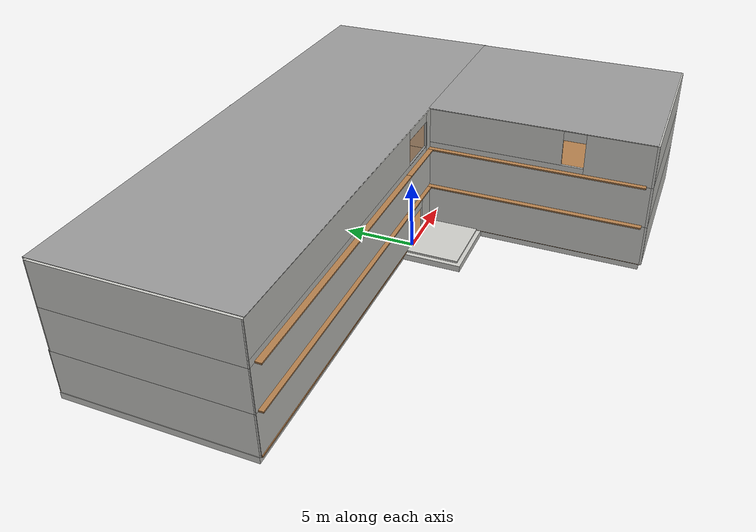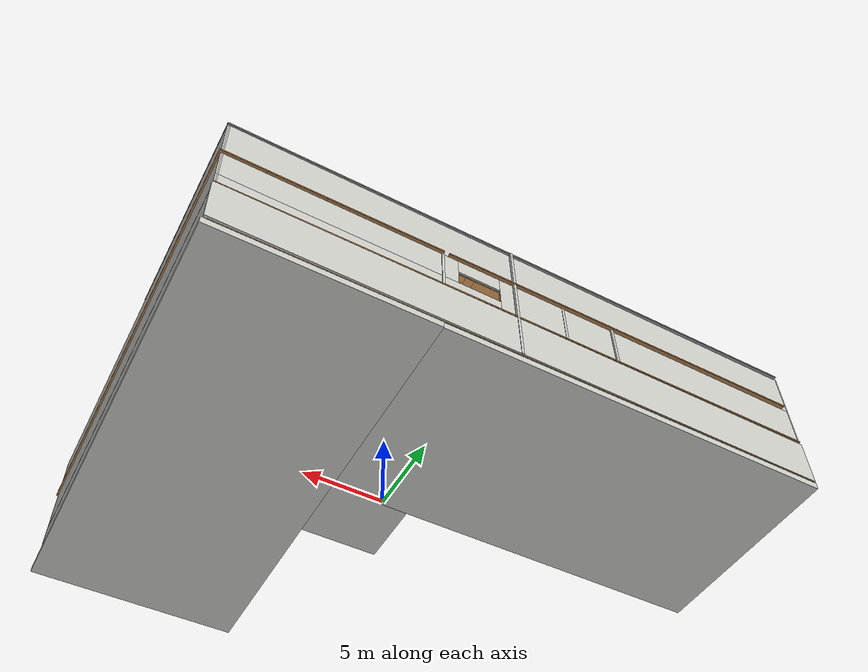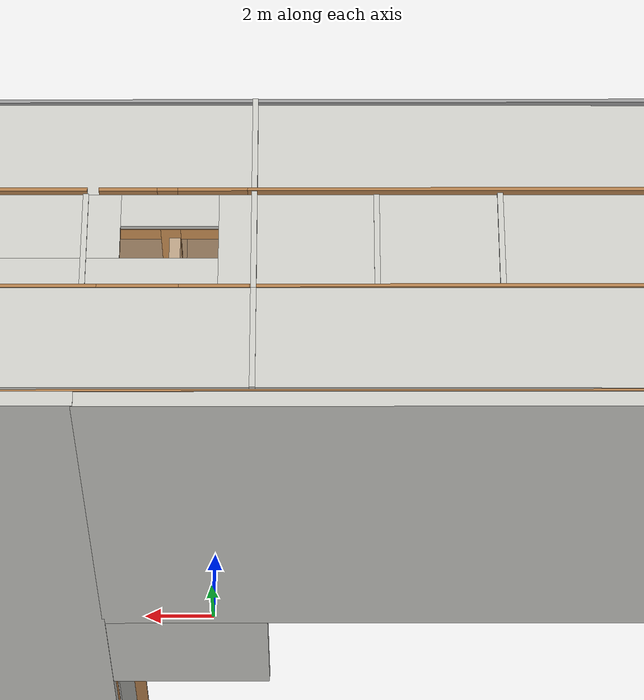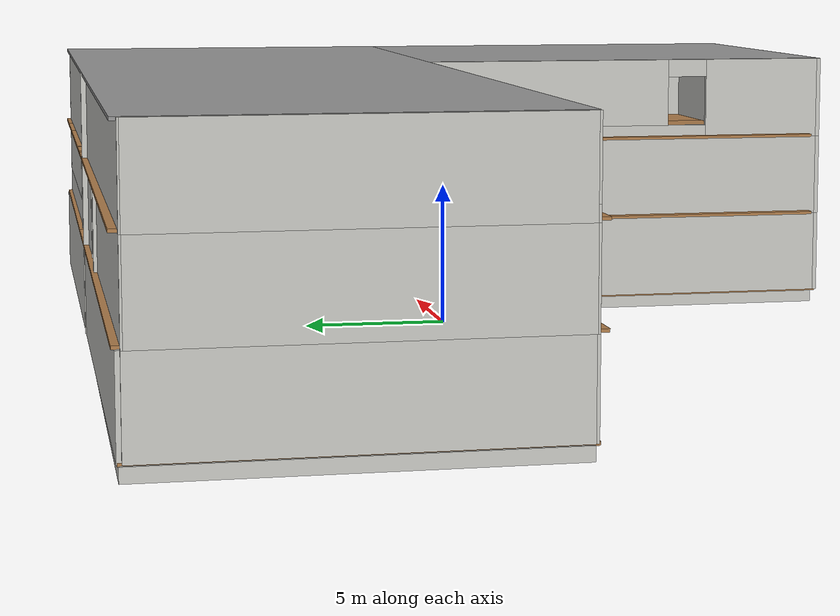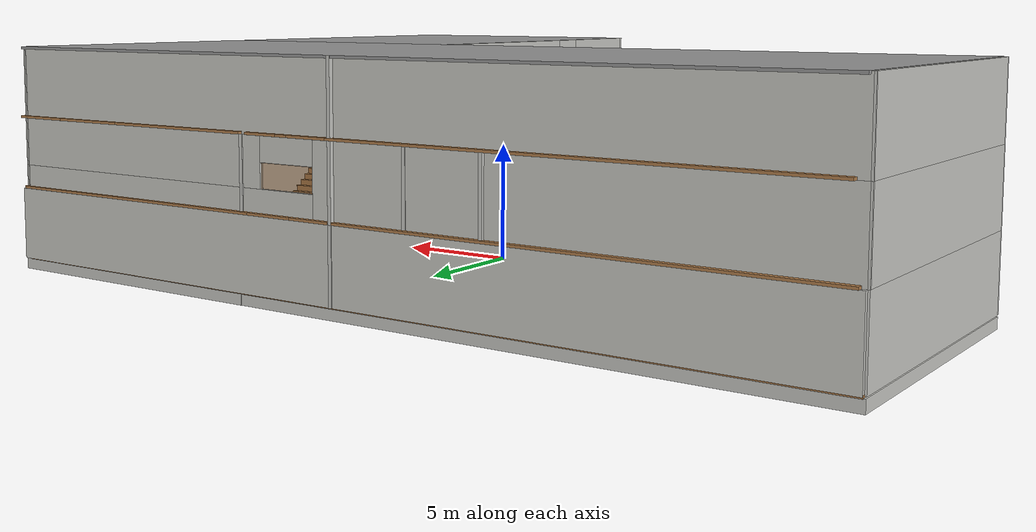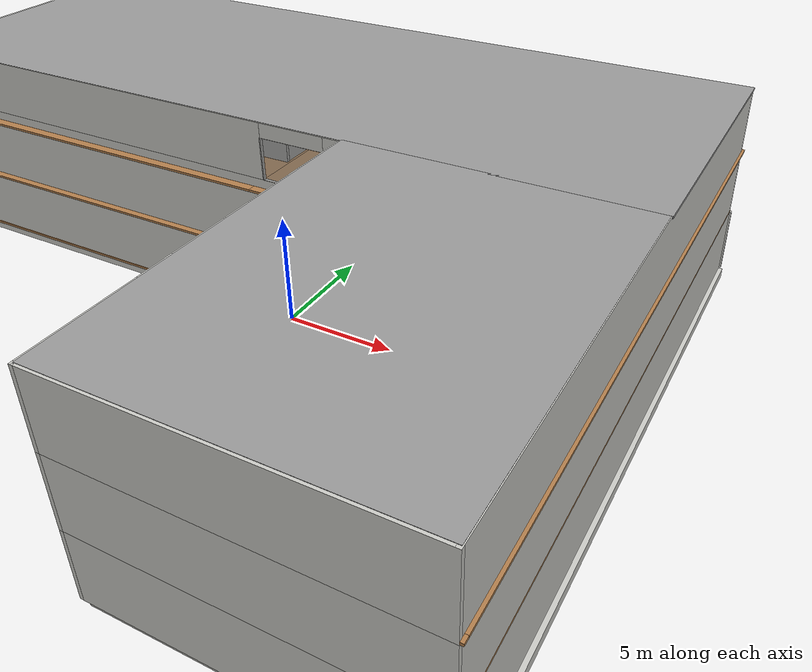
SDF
<?xml version='1.0'?>
<sdf version='1.6'>
  <model name='add_competition_building_with_stair'>
    <link name='link_0'>
      <inertial>
        <mass>26.161</mass>
        <inertia>
          <ixx>37.6217</ixx>
          <ixy>0</ixy>
          <ixz>0</ixz>
          <iyy>49.4924</iyy>
          <iyz>0</iyz>
          <izz>86.2665</izz>
        </inertia>
        <pose frame=''>0 0 0 0 -0 0</pose>
      </inertial>
      <pose frame=''>0.807052 -2.01011 0 0 -0 0</pose>
      <gravity>1</gravity>
      <self_collide>0</self_collide>
      <kinematic>0</kinematic>
      <enable_wind>0</enable_wind>
      <visual name='visual'>
        <pose frame=''>0 0 0 0 -0 0</pose>
        <geometry>
          <box>
            <size>4.74422 4.13069 0.440916</size>
          </box>
        </geometry>
        <material>
          <lighting>1</lighting>
          <script>
            <uri>file://media/materials/scripts/gazebo.material</uri>
            <name>Gazebo/CeilingTiled</name>
          </script>
          <shader type='pixel'>
            <normal_map>__default__</normal_map>
          </shader>
          <ambient>1 1 1 1</ambient>
          <diffuse>1 1 1 1</diffuse>
          <specular>0.01 0.01 0.01 1</specular>
          <emissive>0 0 0 1</emissive>
        </material>
        <transparency>0</transparency>
        <cast_shadows>1</cast_shadows>
      </visual>
      <collision name='collision'>
        <laser_retro>0</laser_retro>
        <max_contacts>10</max_contacts>
        <pose frame=''>0 0 0 0 -0 0</pose>
        <geometry>
          <box>
            <size>4.74422 4.13069 0.440916</size>
          </box>
        </geometry>
        <surface>
          <friction>
            <ode>
              <mu>1</mu>
              <mu2>1</mu2>
              <fdir1>0 0 0</fdir1>
              <slip1>0</slip1>
              <slip2>0</slip2>
            </ode>
            <torsional>
              <coefficient>1</coefficient>
              <patch_radius>0</patch_radius>
              <surface_radius>0</surface_radius>
              <use_patch_radius>1</use_patch_radius>
              <ode>
                <slip>0</slip>
              </ode>
            </torsional>
          </friction>
          <bounce>
            <restitution_coefficient>0</restitution_coefficient>
            <threshold>1e+06</threshold>
          </bounce>
          <contact>
            <collide_without_contact>0</collide_without_contact>
            <collide_without_contact_bitmask>1</collide_without_contact_bitmask>
            <collide_bitmask>1</collide_bitmask>
            <ode>
              <soft_cfm>0</soft_cfm>
              <soft_erp>0.2</soft_erp>
              <kp>1e+13</kp>
              <kd>1</kd>
              <max_vel>0.01</max_vel>
              <min_depth>0</min_depth>
            </ode>
            <bullet>
              <split_impulse>1</split_impulse>
              <split_impulse_penetration_threshold>-0.01</split_impulse_penetration_threshold>
              <soft_cfm>0</soft_cfm>
              <soft_erp>0.2</soft_erp>
              <kp>1e+13</kp>
              <kd>1</kd>
            </bullet>
          </contact>
        </surface>
      </collision>
    </link>
    <link name='link_0_clone'>
      <inertial>
        <mass>0.497616</mass>
        <inertia>
          <ixx>0.613287</ixx>
          <ixy>0</ixy>
          <ixz>0</ixz>
          <iyy>0.811754</iyy>
          <iyz>0</iyz>
          <izz>1.42331</izz>
        </inertia>
        <pose frame=''>0 0 0 0 -0 0</pose>
      </inertial>
      <pose frame=''>0.966685 -1.86699 0.282136 0 -0 0</pose>
      <gravity>1</gravity>
      <self_collide>0</self_collide>
      <kinematic>0</kinematic>
      <enable_wind>0</enable_wind>
      <visual name='visual'>
        <pose frame=''>0 0 0 0 -0 0</pose>
        <geometry>
          <box>
            <size>4.42206 3.84299 0.144334</size>
          </box>
        </geometry>
        <material>
          <lighting>1</lighting>
          <script>
            <uri>file://media/materials/scripts/gazebo.material</uri>
            <name>Gazebo/CeilingTiled</name>
          </script>
          <shader type='pixel'>
            <normal_map>__default__</normal_map>
          </shader>
          <ambient>1 1 1 1</ambient>
          <diffuse>1 1 1 1</diffuse>
          <specular>0.01 0.01 0.01 1</specular>
          <emissive>0 0 0 1</emissive>
        </material>
        <transparency>0</transparency>
        <cast_shadows>1</cast_shadows>
      </visual>
      <collision name='collision'>
        <laser_retro>0</laser_retro>
        <max_contacts>10</max_contacts>
        <pose frame=''>0 0 0 0 -0 0</pose>
        <geometry>
          <box>
            <size>4.42206 3.84299 0.144334</size>
          </box>
        </geometry>
        <surface>
          <friction>
            <ode>
              <mu>1</mu>
              <mu2>1</mu2>
              <fdir1>0 0 0</fdir1>
              <slip1>0</slip1>
              <slip2>0</slip2>
            </ode>
            <torsional>
              <coefficient>1</coefficient>
              <patch_radius>0</patch_radius>
              <surface_radius>0</surface_radius>
              <use_patch_radius>1</use_patch_radius>
              <ode>
                <slip>0</slip>
              </ode>
            </torsional>
          </friction>
          <bounce>
            <restitution_coefficient>0</restitution_coefficient>
            <threshold>1e+06</threshold>
          </bounce>
          <contact>
            <collide_without_contact>0</collide_without_contact>
            <collide_without_contact_bitmask>1</collide_without_contact_bitmask>
            <collide_bitmask>1</collide_bitmask>
            <ode>
              <soft_cfm>0</soft_cfm>
              <soft_erp>0.2</soft_erp>
              <kp>1e+13</kp>
              <kd>1</kd>
              <max_vel>0.01</max_vel>
              <min_depth>0</min_depth>
            </ode>
            <bullet>
              <split_impulse>1</split_impulse>
              <split_impulse_penetration_threshold>-0.01</split_impulse_penetration_threshold>
              <soft_cfm>0</soft_cfm>
              <soft_erp>0.2</soft_erp>
              <kp>1e+13</kp>
              <kd>1</kd>
            </bullet>
          </contact>
        </surface>
      </collision>
    </link>
    <link name='link_2'>
      <inertial>
        <mass>163.316</mass>
        <inertia>
          <ixx>10717.1</ixx>
          <ixy>0</ixy>
          <ixz>0</ixz>
          <iyy>2242.65</iyy>
          <iyz>0</iyz>
          <izz>12954.1</izz>
        </inertia>
        <pose frame=''>0 0 0 0 -0 0</pose>
      </inertial>
      <pose frame=''>9.59679 -1.25874 0 0 -0 0</pose>
      <gravity>1</gravity>
      <self_collide>0</self_collide>
      <kinematic>0</kinematic>
      <enable_wind>0</enable_wind>
      <visual name='visual'>
        <pose frame=''>0 0 0 0 -0 0</pose>
        <geometry>
          <box>
            <size>12.8288 28.0581 0.453943</size>
          </box>
        </geometry>
        <material>
          <lighting>1</lighting>
          <script>
            <uri>file://media/materials/scripts/gazebo.material</uri>
            <name>Gazebo/CeilingTiled</name>
          </script>
          <shader type='pixel'>
            <normal_map>__default__</normal_map>
          </shader>
          <ambient>1 1 1 1</ambient>
          <diffuse>1 1 1 1</diffuse>
          <specular>0.01 0.01 0.01 1</specular>
          <emissive>0 0 0 1</emissive>
        </material>
        <transparency>0</transparency>
        <cast_shadows>1</cast_shadows>
      </visual>
      <collision name='collision'>
        <laser_retro>0</laser_retro>
        <max_contacts>10</max_contacts>
        <pose frame=''>0 0 0 0 -0 0</pose>
        <geometry>
          <box>
            <size>12.8288 28.0581 0.453943</size>
          </box>
        </geometry>
        <surface>
          <friction>
            <ode>
              <mu>1</mu>
              <mu2>1</mu2>
              <fdir1>0 0 0</fdir1>
              <slip1>0</slip1>
              <slip2>0</slip2>
            </ode>
            <torsional>
              <coefficient>1</coefficient>
              <patch_radius>0</patch_radius>
              <surface_radius>0</surface_radius>
              <use_patch_radius>1</use_patch_radius>
              <ode>
                <slip>0</slip>
              </ode>
            </torsional>
          </friction>
          <bounce>
            <restitution_coefficient>0</restitution_coefficient>
            <threshold>1e+06</threshold>
          </bounce>
          <contact>
            <collide_without_contact>0</collide_without_contact>
            <collide_without_contact_bitmask>1</collide_without_contact_bitmask>
            <collide_bitmask>1</collide_bitmask>
            <ode>
              <soft_cfm>0</soft_cfm>
              <soft_erp>0.2</soft_erp>
              <kp>1e+13</kp>
              <kd>1</kd>
              <max_vel>0.01</max_vel>
              <min_depth>0</min_depth>
            </ode>
            <bullet>
              <split_impulse>1</split_impulse>
              <split_impulse_penetration_threshold>-0.01</split_impulse_penetration_threshold>
              <soft_cfm>0</soft_cfm>
              <soft_erp>0.2</soft_erp>
              <kp>1e+13</kp>
              <kd>1</kd>
            </bullet>
          </contact>
        </surface>
      </collision>
    </link>
    <link name='link_2_clone'>
      <inertial>
        <mass>139.72</mass>
        <inertia>
          <ixx>1892.14</ixx>
          <ixy>0</ixy>
          <ixz>0</ixz>
          <iyy>6805.44</iyy>
          <iyz>0</iyz>
          <izz>8692.78</izz>
        </inertia>
        <pose frame=''>0 0 0 0 -0 0</pose>
      </inertial>
      <pose frame=''>-8.83545 6.37789 0 0 -0 0</pose>
      <gravity>1</gravity>
      <self_collide>0</self_collide>
      <kinematic>0</kinematic>
      <enable_wind>0</enable_wind>
      <visual name='visual'>
        <pose frame=''>0 0 0 0 -0 0</pose>
        <geometry>
          <box>
            <size>24.172 12.7398 0.453943</size>
          </box>
        </geometry>
        <material>
          <lighting>1</lighting>
          <script>
            <uri>file://media/materials/scripts/gazebo.material</uri>
            <name>Gazebo/CeilingTiled</name>
          </script>
          <shader type='pixel'>
            <normal_map>__default__</normal_map>
          </shader>
          <ambient>1 1 1 1</ambient>
          <diffuse>1 1 1 1</diffuse>
          <specular>0.01 0.01 0.01 1</specular>
          <emissive>0 0 0 1</emissive>
        </material>
        <transparency>0</transparency>
        <cast_shadows>1</cast_shadows>
      </visual>
      <collision name='collision'>
        <laser_retro>0</laser_retro>
        <max_contacts>10</max_contacts>
        <pose frame=''>0 0 0 0 -0 0</pose>
        <geometry>
          <box>
            <size>24.172 12.7398 0.453943</size>
          </box>
        </geometry>
        <surface>
          <friction>
            <ode>
              <mu>1</mu>
              <mu2>1</mu2>
              <fdir1>0 0 0</fdir1>
              <slip1>0</slip1>
              <slip2>0</slip2>
            </ode>
            <torsional>
              <coefficient>1</coefficient>
              <patch_radius>0</patch_radius>
              <surface_radius>0</surface_radius>
              <use_patch_radius>1</use_patch_radius>
              <ode>
                <slip>0</slip>
              </ode>
            </torsional>
          </friction>
          <bounce>
            <restitution_coefficient>0</restitution_coefficient>
            <threshold>1e+06</threshold>
          </bounce>
          <contact>
            <collide_without_contact>0</collide_without_contact>
            <collide_without_contact_bitmask>1</collide_without_contact_bitmask>
            <collide_bitmask>1</collide_bitmask>
            <ode>
              <soft_cfm>0</soft_cfm>
              <soft_erp>0.2</soft_erp>
              <kp>1e+13</kp>
              <kd>1</kd>
              <max_vel>0.01</max_vel>
              <min_depth>0</min_depth>
            </ode>
            <bullet>
              <split_impulse>1</split_impulse>
              <split_impulse_penetration_threshold>-0.01</split_impulse_penetration_threshold>
              <soft_cfm>0</soft_cfm>
              <soft_erp>0.2</soft_erp>
              <kp>1e+13</kp>
              <kd>1</kd>
            </bullet>
          </contact>
        </surface>
      </collision>
    </link>
    <model name='add_competition_building'>
      <link name='Floor_17'>
        <pose frame=''>-1e-06 0 3 0 -0 0</pose>
        <self_collide>0</self_collide>
        <enable_wind>0</enable_wind>
        <kinematic>0</kinematic>
        <gravity>1</gravity>
        <inertial>
          <mass>1</mass>
          <pose frame=''>0 0 0 0 -0 0</pose>
          <inertia>
            <ixx>1</ixx>
            <ixy>0</ixy>
            <ixz>0</ixz>
            <iyy>1</iyy>
            <iyz>0</iyz>
            <izz>1</izz>
          </inertia>
        </inertial>
        <visual name='Floor_17_Visual_4'>
          <pose frame=''>3.2474 4.68982 0.05 0 -0 0</pose>
          <geometry>
            <box>
              <size>3.99082 7.61431 0.1</size>
            </box>
          </geometry>
          <material>
            <script>
              <uri>file://media/materials/scripts/gazebo.material</uri>
              <name>Gazebo/WoodFloor</name>
            </script>
            <ambient>1 1 1 1</ambient>
            <shader type='pixel'>
              <normal_map>__default__</normal_map>
            </shader>
          </material>
          <meta>
            <layer>1</layer>
          </meta>
          <transparency>0</transparency>
          <cast_shadows>1</cast_shadows>
        </visual>
        <visual name='Floor_17_Visual_2'>
          <pose frame=''>11.809 0.186054 0.05 0 -0 0</pose>
          <geometry>
            <box>
              <size>13.1324 28.0049 0.1</size>
            </box>
          </geometry>
          <material>
            <script>
              <uri>file://media/materials/scripts/gazebo.material</uri>
              <name>Gazebo/WoodFloor</name>
            </script>
            <ambient>1 1 1 1</ambient>
            <shader type='pixel'>
              <normal_map>__default__</normal_map>
            </shader>
          </material>
          <meta>
            <layer>1</layer>
          </meta>
          <transparency>0</transparency>
          <cast_shadows>1</cast_shadows>
        </visual>
        <visual name='Floor_17_Visual_3'>
          <pose frame=''>-8.4406 7.53558 0.05 0 -0 0</pose>
          <geometry>
            <box>
              <size>19.3852 13.3058 0.1</size>
            </box>
          </geometry>
          <material>
            <script>
              <uri>file://media/materials/scripts/gazebo.material</uri>
              <name>Gazebo/WoodFloor</name>
            </script>
            <ambient>1 1 1 1</ambient>
            <shader type='pixel'>
              <normal_map>__default__</normal_map>
            </shader>
          </material>
          <meta>
            <layer>1</layer>
          </meta>
          <transparency>0</transparency>
          <cast_shadows>1</cast_shadows>
        </visual>
        <visual name='Floor_17_Visual_6'>
          <pose frame=''>2.17698 12.9972 0.05 0 -0 0</pose>
          <geometry>
            <box>
              <size>1.85 2.38252 0.1</size>
            </box>
          </geometry>
          <material>
            <script>
              <uri>file://media/materials/scripts/gazebo.material</uri>
              <name>Gazebo/WoodFloor</name>
            </script>
            <ambient>1 1 1 1</ambient>
            <shader type='pixel'>
              <normal_map>__default__</normal_map>
            </shader>
          </material>
          <meta>
            <layer>1</layer>
          </meta>
          <transparency>0</transparency>
          <cast_shadows>1</cast_shadows>
        </visual>
        <visual name='Floor_17_Visual_5'>
          <pose frame=''>4.17239 11.3427 0.05 0 -0 0</pose>
          <geometry>
            <box>
              <size>2.14082 5.69152 0.1</size>
            </box>
          </geometry>
          <material>
            <script>
              <uri>file://media/materials/scripts/gazebo.material</uri>
              <name>Gazebo/WoodFloor</name>
            </script>
            <ambient>1 1 1 1</ambient>
            <shader type='pixel'>
              <normal_map>__default__</normal_map>
            </shader>
          </material>
          <meta>
            <layer>1</layer>
          </meta>
          <transparency>0</transparency>
          <cast_shadows>1</cast_shadows>
        </visual>
        <collision name='Floor_17_Collision_6'>
          <laser_retro>0</laser_retro>
          <max_contacts>10</max_contacts>
          <pose frame=''>2.17698 12.9972 0.05 0 -0 0</pose>
          <geometry>
            <box>
              <size>1.85 2.38252 0.1</size>
            </box>
          </geometry>
          <surface>
            <friction>
              <ode>
                <mu>1</mu>
                <mu2>1</mu2>
                <fdir1>0 0 0</fdir1>
                <slip1>0</slip1>
                <slip2>0</slip2>
              </ode>
              <torsional>
                <coefficient>1</coefficient>
                <patch_radius>0</patch_radius>
                <surface_radius>0</surface_radius>
                <use_patch_radius>1</use_patch_radius>
                <ode>
                  <slip>0</slip>
                </ode>
              </torsional>
            </friction>
            <bounce>
              <restitution_coefficient>0</restitution_coefficient>
              <threshold>1e+06</threshold>
            </bounce>
            <contact>
              <collide_without_contact>0</collide_without_contact>
              <collide_without_contact_bitmask>1</collide_without_contact_bitmask>
              <collide_bitmask>1</collide_bitmask>
              <ode>
                <soft_cfm>0</soft_cfm>
                <soft_erp>0.2</soft_erp>
                <kp>1e+13</kp>
                <kd>1</kd>
                <max_vel>0.01</max_vel>
                <min_depth>0</min_depth>
              </ode>
              <bullet>
                <split_impulse>1</split_impulse>
                <split_impulse_penetration_threshold>-0.01</split_impulse_penetration_threshold>
                <soft_cfm>0</soft_cfm>
                <soft_erp>0.2</soft_erp>
                <kp>1e+13</kp>
                <kd>1</kd>
              </bullet>
            </contact>
          </surface>
        </collision>
        <collision name='Floor_17_Collision_4'>
          <laser_retro>0</laser_retro>
          <max_contacts>10</max_contacts>
          <pose frame=''>3.2474 4.68982 0.05 0 -0 0</pose>
          <geometry>
            <box>
              <size>3.99082 7.61431 0.1</size>
            </box>
          </geometry>
          <surface>
            <friction>
              <ode>
                <mu>1</mu>
                <mu2>1</mu2>
                <fdir1>0 0 0</fdir1>
                <slip1>0</slip1>
                <slip2>0</slip2>
              </ode>
              <torsional>
                <coefficient>1</coefficient>
                <patch_radius>0</patch_radius>
                <surface_radius>0</surface_radius>
                <use_patch_radius>1</use_patch_radius>
                <ode>
                  <slip>0</slip>
                </ode>
              </torsional>
            </friction>
            <bounce>
              <restitution_coefficient>0</restitution_coefficient>
              <threshold>1e+06</threshold>
            </bounce>
            <contact>
              <collide_without_contact>0</collide_without_contact>
              <collide_without_contact_bitmask>1</collide_without_contact_bitmask>
              <collide_bitmask>1</collide_bitmask>
              <ode>
                <soft_cfm>0</soft_cfm>
                <soft_erp>0.2</soft_erp>
                <kp>1e+13</kp>
                <kd>1</kd>
                <max_vel>0.01</max_vel>
                <min_depth>0</min_depth>
              </ode>
              <bullet>
                <split_impulse>1</split_impulse>
                <split_impulse_penetration_threshold>-0.01</split_impulse_penetration_threshold>
                <soft_cfm>0</soft_cfm>
                <soft_erp>0.2</soft_erp>
                <kp>1e+13</kp>
                <kd>1</kd>
              </bullet>
            </contact>
          </surface>
        </collision>
        <collision name='Floor_17_Collision_2'>
          <laser_retro>0</laser_retro>
          <max_contacts>10</max_contacts>
          <pose frame=''>11.809 0.186054 0.05 0 -0 0</pose>
          <geometry>
            <box>
              <size>13.1324 28.0049 0.1</size>
            </box>
          </geometry>
          <surface>
            <friction>
              <ode>
                <mu>1</mu>
                <mu2>1</mu2>
                <fdir1>0 0 0</fdir1>
                <slip1>0</slip1>
                <slip2>0</slip2>
              </ode>
              <torsional>
                <coefficient>1</coefficient>
                <patch_radius>0</patch_radius>
                <surface_radius>0</surface_radius>
                <use_patch_radius>1</use_patch_radius>
                <ode>
                  <slip>0</slip>
                </ode>
              </torsional>
            </friction>
            <bounce>
              <restitution_coefficient>0</restitution_coefficient>
              <threshold>1e+06</threshold>
            </bounce>
            <contact>
              <collide_without_contact>0</collide_without_contact>
              <collide_without_contact_bitmask>1</collide_without_contact_bitmask>
              <collide_bitmask>1</collide_bitmask>
              <ode>
                <soft_cfm>0</soft_cfm>
                <soft_erp>0.2</soft_erp>
                <kp>1e+13</kp>
                <kd>1</kd>
                <max_vel>0.01</max_vel>
                <min_depth>0</min_depth>
              </ode>
              <bullet>
                <split_impulse>1</split_impulse>
                <split_impulse_penetration_threshold>-0.01</split_impulse_penetration_threshold>
                <soft_cfm>0</soft_cfm>
                <soft_erp>0.2</soft_erp>
                <kp>1e+13</kp>
                <kd>1</kd>
              </bullet>
            </contact>
          </surface>
        </collision>
        <collision name='Floor_17_Collision_3'>
          <laser_retro>0</laser_retro>
          <max_contacts>10</max_contacts>
          <pose frame=''>-8.4406 7.53558 0.05 0 -0 0</pose>
          <geometry>
            <box>
              <size>19.3852 13.3058 0.1</size>
            </box>
          </geometry>
          <surface>
            <friction>
              <ode>
                <mu>1</mu>
                <mu2>1</mu2>
                <fdir1>0 0 0</fdir1>
                <slip1>0</slip1>
                <slip2>0</slip2>
              </ode>
              <torsional>
                <coefficient>1</coefficient>
                <patch_radius>0</patch_radius>
                <surface_radius>0</surface_radius>
                <use_patch_radius>1</use_patch_radius>
                <ode>
                  <slip>0</slip>
                </ode>
              </torsional>
            </friction>
            <bounce>
              <restitution_coefficient>0</restitution_coefficient>
              <threshold>1e+06</threshold>
            </bounce>
            <contact>
              <collide_without_contact>0</collide_without_contact>
              <collide_without_contact_bitmask>1</collide_without_contact_bitmask>
              <collide_bitmask>1</collide_bitmask>
              <ode>
                <soft_cfm>0</soft_cfm>
                <soft_erp>0.2</soft_erp>
                <kp>1e+13</kp>
                <kd>1</kd>
                <max_vel>0.01</max_vel>
                <min_depth>0</min_depth>
              </ode>
              <bullet>
                <split_impulse>1</split_impulse>
                <split_impulse_penetration_threshold>-0.01</split_impulse_penetration_threshold>
                <soft_cfm>0</soft_cfm>
                <soft_erp>0.2</soft_erp>
                <kp>1e+13</kp>
                <kd>1</kd>
              </bullet>
            </contact>
          </surface>
        </collision>
        <collision name='Floor_17_Collision_5'>
          <laser_retro>0</laser_retro>
          <max_contacts>10</max_contacts>
          <pose frame=''>4.17239 11.3427 0.05 0 -0 0</pose>
          <geometry>
            <box>
              <size>2.14082 5.69152 0.1</size>
            </box>
          </geometry>
          <surface>
            <friction>
              <ode>
                <mu>1</mu>
                <mu2>1</mu2>
                <fdir1>0 0 0</fdir1>
                <slip1>0</slip1>
                <slip2>0</slip2>
              </ode>
              <torsional>
                <coefficient>1</coefficient>
                <patch_radius>0</patch_radius>
                <surface_radius>0</surface_radius>
                <use_patch_radius>1</use_patch_radius>
                <ode>
                  <slip>0</slip>
                </ode>
              </torsional>
            </friction>
            <bounce>
              <restitution_coefficient>0</restitution_coefficient>
              <threshold>1e+06</threshold>
            </bounce>
            <contact>
              <collide_without_contact>0</collide_without_contact>
              <collide_without_contact_bitmask>1</collide_without_contact_bitmask>
              <collide_bitmask>1</collide_bitmask>
              <ode>
                <soft_cfm>0</soft_cfm>
                <soft_erp>0.2</soft_erp>
                <kp>1e+13</kp>
                <kd>1</kd>
                <max_vel>0.01</max_vel>
                <min_depth>0</min_depth>
              </ode>
              <bullet>
                <split_impulse>1</split_impulse>
                <split_impulse_penetration_threshold>-0.01</split_impulse_penetration_threshold>
                <soft_cfm>0</soft_cfm>
                <soft_erp>0.2</soft_erp>
                <kp>1e+13</kp>
                <kd>1</kd>
              </bullet>
            </contact>
          </surface>
        </collision>
      </link>
      <link name='Floor_19'>
        <pose frame=''>0.111185 0.017212 6 0 -0 0</pose>
        <self_collide>0</self_collide>
        <enable_wind>0</enable_wind>
        <kinematic>0</kinematic>
        <gravity>1</gravity>
        <inertial>
          <mass>1</mass>
          <pose frame=''>0 0 0 0 -0 0</pose>
          <inertia>
            <ixx>1</ixx>
            <ixy>0</ixy>
            <ixz>0</ixz>
            <iyy>1</iyy>
            <iyz>0</iyz>
            <izz>1</izz>
          </inertia>
        </inertial>
        <visual name='Floor_19_Visual_12'>
          <pose frame=''>4.39145 13.0153 0.05 0 -0 0</pose>
          <geometry>
            <box>
              <size>1.54234 2.34643 0.1</size>
            </box>
          </geometry>
          <material>
            <script>
              <uri>file://media/materials/scripts/gazebo.material</uri>
              <name>Gazebo/WoodFloor</name>
            </script>
            <ambient>1 1 1 1</ambient>
            <shader type='pixel'>
              <normal_map>__default__</normal_map>
            </shader>
          </material>
          <meta>
            <layer>2</layer>
          </meta>
          <transparency>0</transparency>
          <cast_shadows>1</cast_shadows>
        </visual>
        <visual name='Floor_19_Visual_7'>
          <pose frame=''>3.19702 4.67446 0.05 0 -0 0</pose>
          <geometry>
            <box>
              <size>3.93119 7.77785 0.1</size>
            </box>
          </geometry>
          <material>
            <script>
              <uri>file://media/materials/scripts/gazebo.material</uri>
              <name>Gazebo/WoodFloor</name>
            </script>
            <ambient>1 1 1 1</ambient>
            <shader type='pixel'>
              <normal_map>__default__</normal_map>
            </shader>
          </material>
          <meta>
            <layer>2</layer>
          </meta>
          <transparency>0</transparency>
          <cast_shadows>1</cast_shadows>
        </visual>
        <visual name='Floor_19_Visual_11'>
          <pose frame=''>2.15643 13.0151 0.05 0 -0 0</pose>
          <geometry>
            <box>
              <size>1.85 2.34685 0.1</size>
            </box>
          </geometry>
          <material>
            <script>
              <uri>file://media/materials/scripts/gazebo.material</uri>
              <name>Gazebo/WoodFloor</name>
            </script>
            <ambient>1 1 1 1</ambient>
            <shader type='pixel'>
              <normal_map>__default__</normal_map>
            </shader>
          </material>
          <meta>
            <layer>2</layer>
          </meta>
          <transparency>0</transparency>
          <cast_shadows>1</cast_shadows>
        </visual>
        <visual name='Floor_19_Visual_3'>
          <pose frame=''>17.0737 0.122308 0.05 0 -0 0</pose>
          <geometry>
            <box>
              <size>2.60309 28.1324 0.1</size>
            </box>
          </geometry>
          <material>
            <script>
              <uri>file://media/materials/scripts/gazebo.material</uri>
              <name>Gazebo/WoodFloor</name>
            </script>
            <ambient>1 1 1 1</ambient>
            <shader type='pixel'>
              <normal_map>__default__</normal_map>
            </shader>
          </material>
          <meta>
            <layer>2</layer>
          </meta>
          <transparency>0</transparency>
          <cast_shadows>1</cast_shadows>
        </visual>
        <visual name='Floor_19_Visual_5'>
          <pose frame=''>14.0846 1.10138 0.05 0 -0 0</pose>
          <geometry>
            <box>
              <size>3.37505 26.1742 0.1</size>
            </box>
          </geometry>
          <material>
            <script>
              <uri>file://media/materials/scripts/gazebo.material</uri>
              <name>Gazebo/WoodFloor</name>
            </script>
            <ambient>1 1 1 1</ambient>
            <shader type='pixel'>
              <normal_map>__default__</normal_map>
            </shader>
          </material>
          <meta>
            <layer>2</layer>
          </meta>
          <transparency>0</transparency>
          <cast_shadows>1</cast_shadows>
        </visual>
        <visual name='Floor_19_Visual_9'>
          <pose frame=''>4.39145 8.57012 0.05 0 -0 0</pose>
          <geometry>
            <box>
              <size>1.54234 0.013466 0.1</size>
            </box>
          </geometry>
          <material>
            <script>
              <uri>file://media/materials/scripts/gazebo.material</uri>
              <name>Gazebo/WoodFloor</name>
            </script>
            <ambient>1 1 1 1</ambient>
            <shader type='pixel'>
              <normal_map>__default__</normal_map>
            </shader>
          </material>
          <meta>
            <layer>2</layer>
          </meta>
          <transparency>0</transparency>
          <cast_shadows>1</cast_shadows>
        </visual>
        <visual name='Floor_19_Visual_6'>
          <pose frame=''>-8.39526 7.48702 0.05 0 -0 0</pose>
          <geometry>
            <box>
              <size>19.2534 13.403 0.1</size>
            </box>
          </geometry>
          <material>
            <script>
              <uri>file://media/materials/scripts/gazebo.material</uri>
              <name>Gazebo/WoodFloor</name>
            </script>
            <ambient>1 1 1 1</ambient>
            <shader type='pixel'>
              <normal_map>__default__</normal_map>
            </shader>
          </material>
          <meta>
            <layer>2</layer>
          </meta>
          <transparency>0</transparency>
          <cast_shadows>1</cast_shadows>
        </visual>
        <visual name='Floor_19_Visual_10'>
          <pose frame=''>8.93367 11.3827 0.05 0 -0 0</pose>
          <geometry>
            <box>
              <size>6.92679 5.61165 0.1</size>
            </box>
          </geometry>
          <material>
            <script>
              <uri>file://media/materials/scripts/gazebo.material</uri>
              <name>Gazebo/WoodFloor</name>
            </script>
            <ambient>1 1 1 1</ambient>
            <shader type='pixel'>
              <normal_map>__default__</normal_map>
            </shader>
          </material>
          <meta>
            <layer>2</layer>
          </meta>
          <transparency>0</transparency>
          <cast_shadows>1</cast_shadows>
        </visual>
        <visual name='Floor_19_Visual_4'>
          <pose frame=''>8.77984 -2.595 0.05 0 -0 0</pose>
          <geometry>
            <box>
              <size>7.23445 22.3437 0.1</size>
            </box>
          </geometry>
          <material>
            <script>
              <uri>file://media/materials/scripts/gazebo.material</uri>
              <name>Gazebo/WoodFloor</name>
            </script>
            <ambient>1 1 1 1</ambient>
            <shader type='pixel'>
              <normal_map>__default__</normal_map>
            </shader>
          </material>
          <meta>
            <layer>2</layer>
          </meta>
          <transparency>0</transparency>
          <cast_shadows>1</cast_shadows>
        </visual>
        <visual name='Floor_19_Visual_8'>
          <pose frame=''>3.35085 11.3759 0.05 0 -0 0</pose>
          <geometry>
            <box>
              <size>0.538854 5.62511 0.1</size>
            </box>
          </geometry>
          <material>
            <script>
              <uri>file://media/materials/scripts/gazebo.material</uri>
              <name>Gazebo/WoodFloor</name>
            </script>
            <ambient>1 1 1 1</ambient>
            <shader type='pixel'>
              <normal_map>__default__</normal_map>
            </shader>
          </material>
          <meta>
            <layer>2</layer>
          </meta>
          <transparency>0</transparency>
          <cast_shadows>1</cast_shadows>
        </visual>
        <visual name='Floor_19_Visual_2'>
          <pose frame=''>15.3861 -14.0662 0.05 0 -0 0</pose>
          <geometry>
            <box>
              <size>5.97814 0.244616 0.1</size>
            </box>
          </geometry>
          <material>
            <script>
              <uri>file://media/materials/scripts/gazebo.material</uri>
              <name>Gazebo/WoodFloor</name>
            </script>
            <ambient>1 1 1 1</ambient>
            <shader type='pixel'>
              <normal_map>__default__</normal_map>
            </shader>
          </material>
          <meta>
            <layer>2</layer>
          </meta>
          <transparency>0</transparency>
          <cast_shadows>1</cast_shadows>
        </visual>
        <collision name='Floor_19_Collision_7'>
          <laser_retro>0</laser_retro>
          <max_contacts>10</max_contacts>
          <pose frame=''>3.19702 4.67446 0.05 0 -0 0</pose>
          <geometry>
            <box>
              <size>3.93119 7.77785 0.1</size>
            </box>
          </geometry>
          <surface>
            <friction>
              <ode>
                <mu>1</mu>
                <mu2>1</mu2>
                <fdir1>0 0 0</fdir1>
                <slip1>0</slip1>
                <slip2>0</slip2>
              </ode>
              <torsional>
                <coefficient>1</coefficient>
                <patch_radius>0</patch_radius>
                <surface_radius>0</surface_radius>
                <use_patch_radius>1</use_patch_radius>
                <ode>
                  <slip>0</slip>
                </ode>
              </torsional>
            </friction>
            <bounce>
              <restitution_coefficient>0</restitution_coefficient>
              <threshold>1e+06</threshold>
            </bounce>
            <contact>
              <collide_without_contact>0</collide_without_contact>
              <collide_without_contact_bitmask>1</collide_without_contact_bitmask>
              <collide_bitmask>1</collide_bitmask>
              <ode>
                <soft_cfm>0</soft_cfm>
                <soft_erp>0.2</soft_erp>
                <kp>1e+13</kp>
                <kd>1</kd>
                <max_vel>0.01</max_vel>
                <min_depth>0</min_depth>
              </ode>
              <bullet>
                <split_impulse>1</split_impulse>
                <split_impulse_penetration_threshold>-0.01</split_impulse_penetration_threshold>
                <soft_cfm>0</soft_cfm>
                <soft_erp>0.2</soft_erp>
                <kp>1e+13</kp>
                <kd>1</kd>
              </bullet>
            </contact>
          </surface>
        </collision>
        <collision name='Floor_19_Collision_4'>
          <laser_retro>0</laser_retro>
          <max_contacts>10</max_contacts>
          <pose frame=''>8.77984 -2.595 0.05 0 -0 0</pose>
          <geometry>
            <box>
              <size>7.23445 22.3437 0.1</size>
            </box>
          </geometry>
          <surface>
            <friction>
              <ode>
                <mu>1</mu>
                <mu2>1</mu2>
                <fdir1>0 0 0</fdir1>
                <slip1>0</slip1>
                <slip2>0</slip2>
              </ode>
              <torsional>
                <coefficient>1</coefficient>
                <patch_radius>0</patch_radius>
                <surface_radius>0</surface_radius>
                <use_patch_radius>1</use_patch_radius>
                <ode>
                  <slip>0</slip>
                </ode>
              </torsional>
            </friction>
            <bounce>
              <restitution_coefficient>0</restitution_coefficient>
              <threshold>1e+06</threshold>
            </bounce>
            <contact>
              <collide_without_contact>0</collide_without_contact>
              <collide_without_contact_bitmask>1</collide_without_contact_bitmask>
              <collide_bitmask>1</collide_bitmask>
              <ode>
                <soft_cfm>0</soft_cfm>
                <soft_erp>0.2</soft_erp>
                <kp>1e+13</kp>
                <kd>1</kd>
                <max_vel>0.01</max_vel>
                <min_depth>0</min_depth>
              </ode>
              <bullet>
                <split_impulse>1</split_impulse>
                <split_impulse_penetration_threshold>-0.01</split_impulse_penetration_threshold>
                <soft_cfm>0</soft_cfm>
                <soft_erp>0.2</soft_erp>
                <kp>1e+13</kp>
                <kd>1</kd>
              </bullet>
            </contact>
          </surface>
        </collision>
        <collision name='Floor_19_Collision_11'>
          <laser_retro>0</laser_retro>
          <max_contacts>10</max_contacts>
          <pose frame=''>2.15643 13.0151 0.05 0 -0 0</pose>
          <geometry>
            <box>
              <size>1.85 2.34685 0.1</size>
            </box>
          </geometry>
          <surface>
            <friction>
              <ode>
                <mu>1</mu>
                <mu2>1</mu2>
                <fdir1>0 0 0</fdir1>
                <slip1>0</slip1>
                <slip2>0</slip2>
              </ode>
              <torsional>
                <coefficient>1</coefficient>
                <patch_radius>0</patch_radius>
                <surface_radius>0</surface_radius>
                <use_patch_radius>1</use_patch_radius>
                <ode>
                  <slip>0</slip>
                </ode>
              </torsional>
            </friction>
            <bounce>
              <restitution_coefficient>0</restitution_coefficient>
              <threshold>1e+06</threshold>
            </bounce>
            <contact>
              <collide_without_contact>0</collide_without_contact>
              <collide_without_contact_bitmask>1</collide_without_contact_bitmask>
              <collide_bitmask>1</collide_bitmask>
              <ode>
                <soft_cfm>0</soft_cfm>
                <soft_erp>0.2</soft_erp>
                <kp>1e+13</kp>
                <kd>1</kd>
                <max_vel>0.01</max_vel>
                <min_depth>0</min_depth>
              </ode>
              <bullet>
                <split_impulse>1</split_impulse>
                <split_impulse_penetration_threshold>-0.01</split_impulse_penetration_threshold>
                <soft_cfm>0</soft_cfm>
                <soft_erp>0.2</soft_erp>
                <kp>1e+13</kp>
                <kd>1</kd>
              </bullet>
            </contact>
          </surface>
        </collision>
        <collision name='Floor_19_Collision_2'>
          <laser_retro>0</laser_retro>
          <max_contacts>10</max_contacts>
          <pose frame=''>15.3861 -14.0662 0.05 0 -0 0</pose>
          <geometry>
            <box>
              <size>5.97814 0.244616 0.1</size>
            </box>
          </geometry>
          <surface>
            <friction>
              <ode>
                <mu>1</mu>
                <mu2>1</mu2>
                <fdir1>0 0 0</fdir1>
                <slip1>0</slip1>
                <slip2>0</slip2>
              </ode>
              <torsional>
                <coefficient>1</coefficient>
                <patch_radius>0</patch_radius>
                <surface_radius>0</surface_radius>
                <use_patch_radius>1</use_patch_radius>
                <ode>
                  <slip>0</slip>
                </ode>
              </torsional>
            </friction>
            <bounce>
              <restitution_coefficient>0</restitution_coefficient>
              <threshold>1e+06</threshold>
            </bounce>
            <contact>
              <collide_without_contact>0</collide_without_contact>
              <collide_without_contact_bitmask>1</collide_without_contact_bitmask>
              <collide_bitmask>1</collide_bitmask>
              <ode>
                <soft_cfm>0</soft_cfm>
                <soft_erp>0.2</soft_erp>
                <kp>1e+13</kp>
                <kd>1</kd>
                <max_vel>0.01</max_vel>
                <min_depth>0</min_depth>
              </ode>
              <bullet>
                <split_impulse>1</split_impulse>
                <split_impulse_penetration_threshold>-0.01</split_impulse_penetration_threshold>
                <soft_cfm>0</soft_cfm>
                <soft_erp>0.2</soft_erp>
                <kp>1e+13</kp>
                <kd>1</kd>
              </bullet>
            </contact>
          </surface>
        </collision>
        <collision name='Floor_19_Collision_8'>
          <laser_retro>0</laser_retro>
          <max_contacts>10</max_contacts>
          <pose frame=''>3.35085 11.3759 0.05 0 -0 0</pose>
          <geometry>
            <box>
              <size>0.538854 5.62511 0.1</size>
            </box>
          </geometry>
          <surface>
            <friction>
              <ode>
                <mu>1</mu>
                <mu2>1</mu2>
                <fdir1>0 0 0</fdir1>
                <slip1>0</slip1>
                <slip2>0</slip2>
              </ode>
              <torsional>
                <coefficient>1</coefficient>
                <patch_radius>0</patch_radius>
                <surface_radius>0</surface_radius>
                <use_patch_radius>1</use_patch_radius>
                <ode>
                  <slip>0</slip>
                </ode>
              </torsional>
            </friction>
            <bounce>
              <restitution_coefficient>0</restitution_coefficient>
              <threshold>1e+06</threshold>
            </bounce>
            <contact>
              <collide_without_contact>0</collide_without_contact>
              <collide_without_contact_bitmask>1</collide_without_contact_bitmask>
              <collide_bitmask>1</collide_bitmask>
              <ode>
                <soft_cfm>0</soft_cfm>
                <soft_erp>0.2</soft_erp>
                <kp>1e+13</kp>
                <kd>1</kd>
                <max_vel>0.01</max_vel>
                <min_depth>0</min_depth>
              </ode>
              <bullet>
                <split_impulse>1</split_impulse>
                <split_impulse_penetration_threshold>-0.01</split_impulse_penetration_threshold>
                <soft_cfm>0</soft_cfm>
                <soft_erp>0.2</soft_erp>
                <kp>1e+13</kp>
                <kd>1</kd>
              </bullet>
            </contact>
          </surface>
        </collision>
        <collision name='Floor_19_Collision_12'>
          <laser_retro>0</laser_retro>
          <max_contacts>10</max_contacts>
          <pose frame=''>4.39145 13.0153 0.05 0 -0 0</pose>
          <geometry>
            <box>
              <size>1.54234 2.34643 0.1</size>
            </box>
          </geometry>
          <surface>
            <friction>
              <ode>
                <mu>1</mu>
                <mu2>1</mu2>
                <fdir1>0 0 0</fdir1>
                <slip1>0</slip1>
                <slip2>0</slip2>
              </ode>
              <torsional>
                <coefficient>1</coefficient>
                <patch_radius>0</patch_radius>
                <surface_radius>0</surface_radius>
                <use_patch_radius>1</use_patch_radius>
                <ode>
                  <slip>0</slip>
                </ode>
              </torsional>
            </friction>
            <bounce>
              <restitution_coefficient>0</restitution_coefficient>
              <threshold>1e+06</threshold>
            </bounce>
            <contact>
              <collide_without_contact>0</collide_without_contact>
              <collide_without_contact_bitmask>1</collide_without_contact_bitmask>
              <collide_bitmask>1</collide_bitmask>
              <ode>
                <soft_cfm>0</soft_cfm>
                <soft_erp>0.2</soft_erp>
                <kp>1e+13</kp>
                <kd>1</kd>
                <max_vel>0.01</max_vel>
                <min_depth>0</min_depth>
              </ode>
              <bullet>
                <split_impulse>1</split_impulse>
                <split_impulse_penetration_threshold>-0.01</split_impulse_penetration_threshold>
                <soft_cfm>0</soft_cfm>
                <soft_erp>0.2</soft_erp>
                <kp>1e+13</kp>
                <kd>1</kd>
              </bullet>
            </contact>
          </surface>
        </collision>
        <collision name='Floor_19_Collision_10'>
          <laser_retro>0</laser_retro>
          <max_contacts>10</max_contacts>
          <pose frame=''>8.93367 11.3827 0.05 0 -0 0</pose>
          <geometry>
            <box>
              <size>6.92679 5.61165 0.1</size>
            </box>
          </geometry>
          <surface>
            <friction>
              <ode>
                <mu>1</mu>
                <mu2>1</mu2>
                <fdir1>0 0 0</fdir1>
                <slip1>0</slip1>
                <slip2>0</slip2>
              </ode>
              <torsional>
                <coefficient>1</coefficient>
                <patch_radius>0</patch_radius>
                <surface_radius>0</surface_radius>
                <use_patch_radius>1</use_patch_radius>
                <ode>
                  <slip>0</slip>
                </ode>
              </torsional>
            </friction>
            <bounce>
              <restitution_coefficient>0</restitution_coefficient>
              <threshold>1e+06</threshold>
            </bounce>
            <contact>
              <collide_without_contact>0</collide_without_contact>
              <collide_without_contact_bitmask>1</collide_without_contact_bitmask>
              <collide_bitmask>1</collide_bitmask>
              <ode>
                <soft_cfm>0</soft_cfm>
                <soft_erp>0.2</soft_erp>
                <kp>1e+13</kp>
                <kd>1</kd>
                <max_vel>0.01</max_vel>
                <min_depth>0</min_depth>
              </ode>
              <bullet>
                <split_impulse>1</split_impulse>
                <split_impulse_penetration_threshold>-0.01</split_impulse_penetration_threshold>
                <soft_cfm>0</soft_cfm>
                <soft_erp>0.2</soft_erp>
                <kp>1e+13</kp>
                <kd>1</kd>
              </bullet>
            </contact>
          </surface>
        </collision>
        <collision name='Floor_19_Collision_9'>
          <laser_retro>0</laser_retro>
          <max_contacts>10</max_contacts>
          <pose frame=''>4.39145 8.57012 0.05 0 -0 0</pose>
          <geometry>
            <box>
              <size>1.54234 0.013466 0.1</size>
            </box>
          </geometry>
          <surface>
            <friction>
              <ode>
                <mu>1</mu>
                <mu2>1</mu2>
                <fdir1>0 0 0</fdir1>
                <slip1>0</slip1>
                <slip2>0</slip2>
              </ode>
              <torsional>
                <coefficient>1</coefficient>
                <patch_radius>0</patch_radius>
                <surface_radius>0</surface_radius>
                <use_patch_radius>1</use_patch_radius>
                <ode>
                  <slip>0</slip>
                </ode>
              </torsional>
            </friction>
            <bounce>
              <restitution_coefficient>0</restitution_coefficient>
              <threshold>1e+06</threshold>
            </bounce>
            <contact>
              <collide_without_contact>0</collide_without_contact>
              <collide_without_contact_bitmask>1</collide_without_contact_bitmask>
              <collide_bitmask>1</collide_bitmask>
              <ode>
                <soft_cfm>0</soft_cfm>
                <soft_erp>0.2</soft_erp>
                <kp>1e+13</kp>
                <kd>1</kd>
                <max_vel>0.01</max_vel>
                <min_depth>0</min_depth>
              </ode>
              <bullet>
                <split_impulse>1</split_impulse>
                <split_impulse_penetration_threshold>-0.01</split_impulse_penetration_threshold>
                <soft_cfm>0</soft_cfm>
                <soft_erp>0.2</soft_erp>
                <kp>1e+13</kp>
                <kd>1</kd>
              </bullet>
            </contact>
          </surface>
        </collision>
        <collision name='Floor_19_Collision_5'>
          <laser_retro>0</laser_retro>
          <max_contacts>10</max_contacts>
          <pose frame=''>14.0846 1.10138 0.05 0 -0 0</pose>
          <geometry>
            <box>
              <size>3.37505 26.1742 0.1</size>
            </box>
          </geometry>
          <surface>
            <friction>
              <ode>
                <mu>1</mu>
                <mu2>1</mu2>
                <fdir1>0 0 0</fdir1>
                <slip1>0</slip1>
                <slip2>0</slip2>
              </ode>
              <torsional>
                <coefficient>1</coefficient>
                <patch_radius>0</patch_radius>
                <surface_radius>0</surface_radius>
                <use_patch_radius>1</use_patch_radius>
                <ode>
                  <slip>0</slip>
                </ode>
              </torsional>
            </friction>
            <bounce>
              <restitution_coefficient>0</restitution_coefficient>
              <threshold>1e+06</threshold>
            </bounce>
            <contact>
              <collide_without_contact>0</collide_without_contact>
              <collide_without_contact_bitmask>1</collide_without_contact_bitmask>
              <collide_bitmask>1</collide_bitmask>
              <ode>
                <soft_cfm>0</soft_cfm>
                <soft_erp>0.2</soft_erp>
                <kp>1e+13</kp>
                <kd>1</kd>
                <max_vel>0.01</max_vel>
                <min_depth>0</min_depth>
              </ode>
              <bullet>
                <split_impulse>1</split_impulse>
                <split_impulse_penetration_threshold>-0.01</split_impulse_penetration_threshold>
                <soft_cfm>0</soft_cfm>
                <soft_erp>0.2</soft_erp>
                <kp>1e+13</kp>
                <kd>1</kd>
              </bullet>
            </contact>
          </surface>
        </collision>
        <collision name='Floor_19_Collision_3'>
          <laser_retro>0</laser_retro>
          <max_contacts>10</max_contacts>
          <pose frame=''>17.0737 0.122308 0.05 0 -0 0</pose>
          <geometry>
            <box>
              <size>2.60309 28.1324 0.1</size>
            </box>
          </geometry>
          <surface>
            <friction>
              <ode>
                <mu>1</mu>
                <mu2>1</mu2>
                <fdir1>0 0 0</fdir1>
                <slip1>0</slip1>
                <slip2>0</slip2>
              </ode>
              <torsional>
                <coefficient>1</coefficient>
                <patch_radius>0</patch_radius>
                <surface_radius>0</surface_radius>
                <use_patch_radius>1</use_patch_radius>
                <ode>
                  <slip>0</slip>
                </ode>
              </torsional>
            </friction>
            <bounce>
              <restitution_coefficient>0</restitution_coefficient>
              <threshold>1e+06</threshold>
            </bounce>
            <contact>
              <collide_without_contact>0</collide_without_contact>
              <collide_without_contact_bitmask>1</collide_without_contact_bitmask>
              <collide_bitmask>1</collide_bitmask>
              <ode>
                <soft_cfm>0</soft_cfm>
                <soft_erp>0.2</soft_erp>
                <kp>1e+13</kp>
                <kd>1</kd>
                <max_vel>0.01</max_vel>
                <min_depth>0</min_depth>
              </ode>
              <bullet>
                <split_impulse>1</split_impulse>
                <split_impulse_penetration_threshold>-0.01</split_impulse_penetration_threshold>
                <soft_cfm>0</soft_cfm>
                <soft_erp>0.2</soft_erp>
                <kp>1e+13</kp>
                <kd>1</kd>
              </bullet>
            </contact>
          </surface>
        </collision>
        <collision name='Floor_19_Collision_6'>
          <laser_retro>0</laser_retro>
          <max_contacts>10</max_contacts>
          <pose frame=''>-8.39526 7.48702 0.05 0 -0 0</pose>
          <geometry>
            <box>
              <size>19.2534 13.403 0.1</size>
            </box>
          </geometry>
          <surface>
            <friction>
              <ode>
                <mu>1</mu>
                <mu2>1</mu2>
                <fdir1>0 0 0</fdir1>
                <slip1>0</slip1>
                <slip2>0</slip2>
              </ode>
              <torsional>
                <coefficient>1</coefficient>
                <patch_radius>0</patch_radius>
                <surface_radius>0</surface_radius>
                <use_patch_radius>1</use_patch_radius>
                <ode>
                  <slip>0</slip>
                </ode>
              </torsional>
            </friction>
            <bounce>
              <restitution_coefficient>0</restitution_coefficient>
              <threshold>1e+06</threshold>
            </bounce>
            <contact>
              <collide_without_contact>0</collide_without_contact>
              <collide_without_contact_bitmask>1</collide_without_contact_bitmask>
              <collide_bitmask>1</collide_bitmask>
              <ode>
                <soft_cfm>0</soft_cfm>
                <soft_erp>0.2</soft_erp>
                <kp>1e+13</kp>
                <kd>1</kd>
                <max_vel>0.01</max_vel>
                <min_depth>0</min_depth>
              </ode>
              <bullet>
                <split_impulse>1</split_impulse>
                <split_impulse_penetration_threshold>-0.01</split_impulse_penetration_threshold>
                <soft_cfm>0</soft_cfm>
                <soft_erp>0.2</soft_erp>
                <kp>1e+13</kp>
                <kd>1</kd>
              </bullet>
            </contact>
          </surface>
        </collision>
      </link>
      <link name='Stairs_15'>
        <self_collide>0</self_collide>
        <enable_wind>0</enable_wind>
        <kinematic>0</kinematic>
        <pose frame=''>0 0 0 0 -0 0</pose>
        <visual name='Stairs_15_Visual_6'>
          <pose frame=''>2.17698 10.2894 1.625 0 -0 -3.14159</pose>
          <geometry>
            <box>
              <size>1.85 0.27575 0.25</size>
            </box>
          </geometry>
          <material>
            <script>
              <uri>file://media/materials/scripts/gazebo.material</uri>
              <name>Gazebo/WoodPallet</name>
            </script>
            <ambient>1 1 1 1</ambient>
            <shader type='pixel'/>
          </material>
          <meta>
            <layer>0</layer>
          </meta>
          <transparency>0</transparency>
          <cast_shadows>1</cast_shadows>
        </visual>
        <visual name='Stairs_15_Visual_4'>
          <pose frame=''>2.17698 9.73785 1.125 0 -0 -3.14159</pose>
          <geometry>
            <box>
              <size>1.85 0.27575 0.25</size>
            </box>
          </geometry>
          <material>
            <script>
              <uri>file://media/materials/scripts/gazebo.material</uri>
              <name>Gazebo/WoodPallet</name>
            </script>
            <ambient>1 1 1 1</ambient>
            <shader type='pixel'/>
          </material>
          <meta>
            <layer>0</layer>
          </meta>
          <transparency>0</transparency>
          <cast_shadows>1</cast_shadows>
        </visual>
        <visual name='Stairs_15_Visual_2'>
          <pose frame=''>2.17698 9.18635 0.625 0 -0 -3.14159</pose>
          <geometry>
            <box>
              <size>1.85 0.27575 0.25</size>
            </box>
          </geometry>
          <material>
            <script>
              <uri>file://media/materials/scripts/gazebo.material</uri>
              <name>Gazebo/WoodPallet</name>
            </script>
            <ambient>1 1 1 1</ambient>
            <shader type='pixel'/>
          </material>
          <meta>
            <layer>0</layer>
          </meta>
          <transparency>0</transparency>
          <cast_shadows>1</cast_shadows>
        </visual>
        <visual name='Stairs_15_Visual_11'>
          <pose frame=''>2.17698 11.6681 2.875 0 -0 -3.14159</pose>
          <geometry>
            <box>
              <size>1.85 0.27575 0.25</size>
            </box>
          </geometry>
          <material>
            <script>
              <uri>file://media/materials/scripts/gazebo.material</uri>
              <name>Gazebo/WoodPallet</name>
            </script>
            <ambient>1 1 1 1</ambient>
            <shader type='pixel'/>
          </material>
          <meta>
            <layer>0</layer>
          </meta>
          <transparency>0</transparency>
          <cast_shadows>1</cast_shadows>
        </visual>
        <visual name='Stairs_15_Visual_3'>
          <pose frame=''>2.17698 9.4621 0.875 0 -0 -3.14159</pose>
          <geometry>
            <box>
              <size>1.85 0.27575 0.25</size>
            </box>
          </geometry>
          <material>
            <script>
              <uri>file://media/materials/scripts/gazebo.material</uri>
              <name>Gazebo/WoodPallet</name>
            </script>
            <ambient>1 1 1 1</ambient>
            <shader type='pixel'/>
          </material>
          <meta>
            <layer>0</layer>
          </meta>
          <transparency>0</transparency>
          <cast_shadows>1</cast_shadows>
        </visual>
        <visual name='Stairs_15_Visual_8'>
          <pose frame=''>2.17698 10.8409 2.125 0 -0 -3.14159</pose>
          <geometry>
            <box>
              <size>1.85 0.27575 0.25</size>
            </box>
          </geometry>
          <material>
            <script>
              <uri>file://media/materials/scripts/gazebo.material</uri>
              <name>Gazebo/WoodPallet</name>
            </script>
            <ambient>1 1 1 1</ambient>
            <shader type='pixel'/>
          </material>
          <meta>
            <layer>0</layer>
          </meta>
          <transparency>0</transparency>
          <cast_shadows>1</cast_shadows>
        </visual>
        <visual name='Stairs_15_Visual_9'>
          <pose frame=''>2.17698 11.1166 2.375 0 -0 -3.14159</pose>
          <geometry>
            <box>
              <size>1.85 0.27575 0.25</size>
            </box>
          </geometry>
          <material>
            <script>
              <uri>file://media/materials/scripts/gazebo.material</uri>
              <name>Gazebo/WoodPallet</name>
            </script>
            <ambient>1 1 1 1</ambient>
            <shader type='pixel'/>
          </material>
          <meta>
            <layer>0</layer>
          </meta>
          <transparency>0</transparency>
          <cast_shadows>1</cast_shadows>
        </visual>
        <visual name='Stairs_15_Visual_7'>
          <pose frame=''>2.17698 10.5651 1.875 0 -0 -3.14159</pose>
          <geometry>
            <box>
              <size>1.85 0.27575 0.25</size>
            </box>
          </geometry>
          <material>
            <script>
              <uri>file://media/materials/scripts/gazebo.material</uri>
              <name>Gazebo/WoodPallet</name>
            </script>
            <ambient>1 1 1 1</ambient>
            <shader type='pixel'/>
          </material>
          <meta>
            <layer>0</layer>
          </meta>
          <transparency>0</transparency>
          <cast_shadows>1</cast_shadows>
        </visual>
        <visual name='Stairs_15_Visual_1'>
          <pose frame=''>2.17698 8.9106 0.375 0 -0 -3.14159</pose>
          <geometry>
            <box>
              <size>1.85 0.27575 0.25</size>
            </box>
          </geometry>
          <material>
            <script>
              <uri>file://media/materials/scripts/gazebo.material</uri>
              <name>Gazebo/WoodPallet</name>
            </script>
            <ambient>1 1 1 1</ambient>
            <shader type='pixel'/>
          </material>
          <meta>
            <layer>0</layer>
          </meta>
          <transparency>0</transparency>
          <cast_shadows>1</cast_shadows>
        </visual>
        <visual name='Stairs_15_Visual_10'>
          <pose frame=''>2.17698 11.3924 2.625 0 -0 -3.14159</pose>
          <geometry>
            <box>
              <size>1.85 0.27575 0.25</size>
            </box>
          </geometry>
          <material>
            <script>
              <uri>file://media/materials/scripts/gazebo.material</uri>
              <name>Gazebo/WoodPallet</name>
            </script>
            <ambient>1 1 1 1</ambient>
            <shader type='pixel'/>
          </material>
          <meta>
            <layer>0</layer>
          </meta>
          <transparency>0</transparency>
          <cast_shadows>1</cast_shadows>
        </visual>
        <visual name='Stairs_15_Visual_5'>
          <pose frame=''>2.17698 10.0136 1.375 0 -0 -3.14159</pose>
          <geometry>
            <box>
              <size>1.85 0.27575 0.25</size>
            </box>
          </geometry>
          <material>
            <script>
              <uri>file://media/materials/scripts/gazebo.material</uri>
              <name>Gazebo/WoodPallet</name>
            </script>
            <ambient>1 1 1 1</ambient>
            <shader type='pixel'/>
          </material>
          <meta>
            <layer>0</layer>
          </meta>
          <transparency>0</transparency>
          <cast_shadows>1</cast_shadows>
        </visual>
        <visual name='Stairs_15_Visual_0'>
          <pose frame=''>2.17698 8.63485 0.125 0 -0 -3.14159</pose>
          <geometry>
            <box>
              <size>1.85 0.27575 0.25</size>
            </box>
          </geometry>
          <material>
            <script>
              <uri>file://media/materials/scripts/gazebo.material</uri>
              <name>Gazebo/WoodPallet</name>
            </script>
            <ambient>1 1 1 1</ambient>
            <shader type='pixel'/>
          </material>
          <meta>
            <layer>0</layer>
          </meta>
          <transparency>0</transparency>
          <cast_shadows>1</cast_shadows>
        </visual>
        <collision name='Stairs_15_Collision_5'>
          <laser_retro>0</laser_retro>
          <max_contacts>10</max_contacts>
          <pose frame=''>2.17698 10.0136 1.375 0 0 -3.14159</pose>
          <geometry>
            <box>
              <size>1.85 0.27575 0.25</size>
            </box>
          </geometry>
          <surface>
            <friction>
              <ode>
                <mu>1</mu>
                <mu2>1</mu2>
                <fdir1>0 0 0</fdir1>
                <slip1>0</slip1>
                <slip2>0</slip2>
              </ode>
              <torsional>
                <coefficient>1</coefficient>
                <patch_radius>0</patch_radius>
                <surface_radius>0</surface_radius>
                <use_patch_radius>1</use_patch_radius>
                <ode>
                  <slip>0</slip>
                </ode>
              </torsional>
            </friction>
            <bounce>
              <restitution_coefficient>0</restitution_coefficient>
              <threshold>1e+06</threshold>
            </bounce>
            <contact>
              <collide_without_contact>0</collide_without_contact>
              <collide_without_contact_bitmask>1</collide_without_contact_bitmask>
              <collide_bitmask>1</collide_bitmask>
              <ode>
                <soft_cfm>0</soft_cfm>
                <soft_erp>0.2</soft_erp>
                <kp>1e+13</kp>
                <kd>1</kd>
                <max_vel>0.01</max_vel>
                <min_depth>0</min_depth>
              </ode>
              <bullet>
                <split_impulse>1</split_impulse>
                <split_impulse_penetration_threshold>-0.01</split_impulse_penetration_threshold>
                <soft_cfm>0</soft_cfm>
                <soft_erp>0.2</soft_erp>
                <kp>1e+13</kp>
                <kd>1</kd>
              </bullet>
            </contact>
          </surface>
        </collision>
        <collision name='Stairs_15_Collision_10'>
          <laser_retro>0</laser_retro>
          <max_contacts>10</max_contacts>
          <pose frame=''>2.17698 11.3924 2.625 0 0 -3.14159</pose>
          <geometry>
            <box>
              <size>1.85 0.27575 0.25</size>
            </box>
          </geometry>
          <surface>
            <friction>
              <ode>
                <mu>1</mu>
                <mu2>1</mu2>
                <fdir1>0 0 0</fdir1>
                <slip1>0</slip1>
                <slip2>0</slip2>
              </ode>
              <torsional>
                <coefficient>1</coefficient>
                <patch_radius>0</patch_radius>
                <surface_radius>0</surface_radius>
                <use_patch_radius>1</use_patch_radius>
                <ode>
                  <slip>0</slip>
                </ode>
              </torsional>
            </friction>
            <bounce>
              <restitution_coefficient>0</restitution_coefficient>
              <threshold>1e+06</threshold>
            </bounce>
            <contact>
              <collide_without_contact>0</collide_without_contact>
              <collide_without_contact_bitmask>1</collide_without_contact_bitmask>
              <collide_bitmask>1</collide_bitmask>
              <ode>
                <soft_cfm>0</soft_cfm>
                <soft_erp>0.2</soft_erp>
                <kp>1e+13</kp>
                <kd>1</kd>
                <max_vel>0.01</max_vel>
                <min_depth>0</min_depth>
              </ode>
              <bullet>
                <split_impulse>1</split_impulse>
                <split_impulse_penetration_threshold>-0.01</split_impulse_penetration_threshold>
                <soft_cfm>0</soft_cfm>
                <soft_erp>0.2</soft_erp>
                <kp>1e+13</kp>
                <kd>1</kd>
              </bullet>
            </contact>
          </surface>
        </collision>
        <collision name='Stairs_15_Collision_9'>
          <laser_retro>0</laser_retro>
          <max_contacts>10</max_contacts>
          <pose frame=''>2.17698 11.1166 2.375 0 0 -3.14159</pose>
          <geometry>
            <box>
              <size>1.85 0.27575 0.25</size>
            </box>
          </geometry>
          <surface>
            <friction>
              <ode>
                <mu>1</mu>
                <mu2>1</mu2>
                <fdir1>0 0 0</fdir1>
                <slip1>0</slip1>
                <slip2>0</slip2>
              </ode>
              <torsional>
                <coefficient>1</coefficient>
                <patch_radius>0</patch_radius>
                <surface_radius>0</surface_radius>
                <use_patch_radius>1</use_patch_radius>
                <ode>
                  <slip>0</slip>
                </ode>
              </torsional>
            </friction>
            <bounce>
              <restitution_coefficient>0</restitution_coefficient>
              <threshold>1e+06</threshold>
            </bounce>
            <contact>
              <collide_without_contact>0</collide_without_contact>
              <collide_without_contact_bitmask>1</collide_without_contact_bitmask>
              <collide_bitmask>1</collide_bitmask>
              <ode>
                <soft_cfm>0</soft_cfm>
                <soft_erp>0.2</soft_erp>
                <kp>1e+13</kp>
                <kd>1</kd>
                <max_vel>0.01</max_vel>
                <min_depth>0</min_depth>
              </ode>
              <bullet>
                <split_impulse>1</split_impulse>
                <split_impulse_penetration_threshold>-0.01</split_impulse_penetration_threshold>
                <soft_cfm>0</soft_cfm>
                <soft_erp>0.2</soft_erp>
                <kp>1e+13</kp>
                <kd>1</kd>
              </bullet>
            </contact>
          </surface>
        </collision>
        <collision name='Stairs_15_Collision_0'>
          <laser_retro>0</laser_retro>
          <max_contacts>10</max_contacts>
          <pose frame=''>2.17698 8.63485 0.125 0 0 -3.14159</pose>
          <geometry>
            <box>
              <size>1.85 0.27575 0.25</size>
            </box>
          </geometry>
          <surface>
            <friction>
              <ode>
                <mu>1</mu>
                <mu2>1</mu2>
                <fdir1>0 0 0</fdir1>
                <slip1>0</slip1>
                <slip2>0</slip2>
              </ode>
              <torsional>
                <coefficient>1</coefficient>
                <patch_radius>0</patch_radius>
                <surface_radius>0</surface_radius>
                <use_patch_radius>1</use_patch_radius>
                <ode>
                  <slip>0</slip>
                </ode>
              </torsional>
            </friction>
            <bounce>
              <restitution_coefficient>0</restitution_coefficient>
              <threshold>1e+06</threshold>
            </bounce>
            <contact>
              <collide_without_contact>0</collide_without_contact>
              <collide_without_contact_bitmask>1</collide_without_contact_bitmask>
              <collide_bitmask>1</collide_bitmask>
              <ode>
                <soft_cfm>0</soft_cfm>
                <soft_erp>0.2</soft_erp>
                <kp>1e+13</kp>
                <kd>1</kd>
                <max_vel>0.01</max_vel>
                <min_depth>0</min_depth>
              </ode>
              <bullet>
                <split_impulse>1</split_impulse>
                <split_impulse_penetration_threshold>-0.01</split_impulse_penetration_threshold>
                <soft_cfm>0</soft_cfm>
                <soft_erp>0.2</soft_erp>
                <kp>1e+13</kp>
                <kd>1</kd>
              </bullet>
            </contact>
          </surface>
        </collision>
        <collision name='Stairs_15_Collision_11'>
          <laser_retro>0</laser_retro>
          <max_contacts>10</max_contacts>
          <pose frame=''>2.17698 11.6681 2.875 0 0 -3.14159</pose>
          <geometry>
            <box>
              <size>1.85 0.27575 0.25</size>
            </box>
          </geometry>
          <surface>
            <friction>
              <ode>
                <mu>1</mu>
                <mu2>1</mu2>
                <fdir1>0 0 0</fdir1>
                <slip1>0</slip1>
                <slip2>0</slip2>
              </ode>
              <torsional>
                <coefficient>1</coefficient>
                <patch_radius>0</patch_radius>
                <surface_radius>0</surface_radius>
                <use_patch_radius>1</use_patch_radius>
                <ode>
                  <slip>0</slip>
                </ode>
              </torsional>
            </friction>
            <bounce>
              <restitution_coefficient>0</restitution_coefficient>
              <threshold>1e+06</threshold>
            </bounce>
            <contact>
              <collide_without_contact>0</collide_without_contact>
              <collide_without_contact_bitmask>1</collide_without_contact_bitmask>
              <collide_bitmask>1</collide_bitmask>
              <ode>
                <soft_cfm>0</soft_cfm>
                <soft_erp>0.2</soft_erp>
                <kp>1e+13</kp>
                <kd>1</kd>
                <max_vel>0.01</max_vel>
                <min_depth>0</min_depth>
              </ode>
              <bullet>
                <split_impulse>1</split_impulse>
                <split_impulse_penetration_threshold>-0.01</split_impulse_penetration_threshold>
                <soft_cfm>0</soft_cfm>
                <soft_erp>0.2</soft_erp>
                <kp>1e+13</kp>
                <kd>1</kd>
              </bullet>
            </contact>
          </surface>
        </collision>
        <collision name='Stairs_15_Collision_3'>
          <laser_retro>0</laser_retro>
          <max_contacts>10</max_contacts>
          <pose frame=''>2.17698 9.4621 0.875 0 0 -3.14159</pose>
          <geometry>
            <box>
              <size>1.85 0.27575 0.25</size>
            </box>
          </geometry>
          <surface>
            <friction>
              <ode>
                <mu>1</mu>
                <mu2>1</mu2>
                <fdir1>0 0 0</fdir1>
                <slip1>0</slip1>
                <slip2>0</slip2>
              </ode>
              <torsional>
                <coefficient>1</coefficient>
                <patch_radius>0</patch_radius>
                <surface_radius>0</surface_radius>
                <use_patch_radius>1</use_patch_radius>
                <ode>
                  <slip>0</slip>
                </ode>
              </torsional>
            </friction>
            <bounce>
              <restitution_coefficient>0</restitution_coefficient>
              <threshold>1e+06</threshold>
            </bounce>
            <contact>
              <collide_without_contact>0</collide_without_contact>
              <collide_without_contact_bitmask>1</collide_without_contact_bitmask>
              <collide_bitmask>1</collide_bitmask>
              <ode>
                <soft_cfm>0</soft_cfm>
                <soft_erp>0.2</soft_erp>
                <kp>1e+13</kp>
                <kd>1</kd>
                <max_vel>0.01</max_vel>
                <min_depth>0</min_depth>
              </ode>
              <bullet>
                <split_impulse>1</split_impulse>
                <split_impulse_penetration_threshold>-0.01</split_impulse_penetration_threshold>
                <soft_cfm>0</soft_cfm>
                <soft_erp>0.2</soft_erp>
                <kp>1e+13</kp>
                <kd>1</kd>
              </bullet>
            </contact>
          </surface>
        </collision>
        <collision name='Stairs_15_Collision_4'>
          <laser_retro>0</laser_retro>
          <max_contacts>10</max_contacts>
          <pose frame=''>2.17698 9.73785 1.125 0 0 -3.14159</pose>
          <geometry>
            <box>
              <size>1.85 0.27575 0.25</size>
            </box>
          </geometry>
          <surface>
            <friction>
              <ode>
                <mu>1</mu>
                <mu2>1</mu2>
                <fdir1>0 0 0</fdir1>
                <slip1>0</slip1>
                <slip2>0</slip2>
              </ode>
              <torsional>
                <coefficient>1</coefficient>
                <patch_radius>0</patch_radius>
                <surface_radius>0</surface_radius>
                <use_patch_radius>1</use_patch_radius>
                <ode>
                  <slip>0</slip>
                </ode>
              </torsional>
            </friction>
            <bounce>
              <restitution_coefficient>0</restitution_coefficient>
              <threshold>1e+06</threshold>
            </bounce>
            <contact>
              <collide_without_contact>0</collide_without_contact>
              <collide_without_contact_bitmask>1</collide_without_contact_bitmask>
              <collide_bitmask>1</collide_bitmask>
              <ode>
                <soft_cfm>0</soft_cfm>
                <soft_erp>0.2</soft_erp>
                <kp>1e+13</kp>
                <kd>1</kd>
                <max_vel>0.01</max_vel>
                <min_depth>0</min_depth>
              </ode>
              <bullet>
                <split_impulse>1</split_impulse>
                <split_impulse_penetration_threshold>-0.01</split_impulse_penetration_threshold>
                <soft_cfm>0</soft_cfm>
                <soft_erp>0.2</soft_erp>
                <kp>1e+13</kp>
                <kd>1</kd>
              </bullet>
            </contact>
          </surface>
        </collision>
        <collision name='Stairs_15_Collision_2'>
          <laser_retro>0</laser_retro>
          <max_contacts>10</max_contacts>
          <pose frame=''>2.17698 9.18635 0.625 0 0 -3.14159</pose>
          <geometry>
            <box>
              <size>1.85 0.27575 0.25</size>
            </box>
          </geometry>
          <surface>
            <friction>
              <ode>
                <mu>1</mu>
                <mu2>1</mu2>
                <fdir1>0 0 0</fdir1>
                <slip1>0</slip1>
                <slip2>0</slip2>
              </ode>
              <torsional>
                <coefficient>1</coefficient>
                <patch_radius>0</patch_radius>
                <surface_radius>0</surface_radius>
                <use_patch_radius>1</use_patch_radius>
                <ode>
                  <slip>0</slip>
                </ode>
              </torsional>
            </friction>
            <bounce>
              <restitution_coefficient>0</restitution_coefficient>
              <threshold>1e+06</threshold>
            </bounce>
            <contact>
              <collide_without_contact>0</collide_without_contact>
              <collide_without_contact_bitmask>1</collide_without_contact_bitmask>
              <collide_bitmask>1</collide_bitmask>
              <ode>
                <soft_cfm>0</soft_cfm>
                <soft_erp>0.2</soft_erp>
                <kp>1e+13</kp>
                <kd>1</kd>
                <max_vel>0.01</max_vel>
                <min_depth>0</min_depth>
              </ode>
              <bullet>
                <split_impulse>1</split_impulse>
                <split_impulse_penetration_threshold>-0.01</split_impulse_penetration_threshold>
                <soft_cfm>0</soft_cfm>
                <soft_erp>0.2</soft_erp>
                <kp>1e+13</kp>
                <kd>1</kd>
              </bullet>
            </contact>
          </surface>
        </collision>
        <collision name='Stairs_15_Collision_6'>
          <laser_retro>0</laser_retro>
          <max_contacts>10</max_contacts>
          <pose frame=''>2.17698 10.2894 1.625 0 0 -3.14159</pose>
          <geometry>
            <box>
              <size>1.85 0.27575 0.25</size>
            </box>
          </geometry>
          <surface>
            <friction>
              <ode>
                <mu>1</mu>
                <mu2>1</mu2>
                <fdir1>0 0 0</fdir1>
                <slip1>0</slip1>
                <slip2>0</slip2>
              </ode>
              <torsional>
                <coefficient>1</coefficient>
                <patch_radius>0</patch_radius>
                <surface_radius>0</surface_radius>
                <use_patch_radius>1</use_patch_radius>
                <ode>
                  <slip>0</slip>
                </ode>
              </torsional>
            </friction>
            <bounce>
              <restitution_coefficient>0</restitution_coefficient>
              <threshold>1e+06</threshold>
            </bounce>
            <contact>
              <collide_without_contact>0</collide_without_contact>
              <collide_without_contact_bitmask>1</collide_without_contact_bitmask>
              <collide_bitmask>1</collide_bitmask>
              <ode>
                <soft_cfm>0</soft_cfm>
                <soft_erp>0.2</soft_erp>
                <kp>1e+13</kp>
                <kd>1</kd>
                <max_vel>0.01</max_vel>
                <min_depth>0</min_depth>
              </ode>
              <bullet>
                <split_impulse>1</split_impulse>
                <split_impulse_penetration_threshold>-0.01</split_impulse_penetration_threshold>
                <soft_cfm>0</soft_cfm>
                <soft_erp>0.2</soft_erp>
                <kp>1e+13</kp>
                <kd>1</kd>
              </bullet>
            </contact>
          </surface>
        </collision>
        <collision name='Stairs_15_Collision_8'>
          <laser_retro>0</laser_retro>
          <max_contacts>10</max_contacts>
          <pose frame=''>2.17698 10.8409 2.125 0 0 -3.14159</pose>
          <geometry>
            <box>
              <size>1.85 0.27575 0.25</size>
            </box>
          </geometry>
          <surface>
            <friction>
              <ode>
                <mu>1</mu>
                <mu2>1</mu2>
                <fdir1>0 0 0</fdir1>
                <slip1>0</slip1>
                <slip2>0</slip2>
              </ode>
              <torsional>
                <coefficient>1</coefficient>
                <patch_radius>0</patch_radius>
                <surface_radius>0</surface_radius>
                <use_patch_radius>1</use_patch_radius>
                <ode>
                  <slip>0</slip>
                </ode>
              </torsional>
            </friction>
            <bounce>
              <restitution_coefficient>0</restitution_coefficient>
              <threshold>1e+06</threshold>
            </bounce>
            <contact>
              <collide_without_contact>0</collide_without_contact>
              <collide_without_contact_bitmask>1</collide_without_contact_bitmask>
              <collide_bitmask>1</collide_bitmask>
              <ode>
                <soft_cfm>0</soft_cfm>
                <soft_erp>0.2</soft_erp>
                <kp>1e+13</kp>
                <kd>1</kd>
                <max_vel>0.01</max_vel>
                <min_depth>0</min_depth>
              </ode>
              <bullet>
                <split_impulse>1</split_impulse>
                <split_impulse_penetration_threshold>-0.01</split_impulse_penetration_threshold>
                <soft_cfm>0</soft_cfm>
                <soft_erp>0.2</soft_erp>
                <kp>1e+13</kp>
                <kd>1</kd>
              </bullet>
            </contact>
          </surface>
        </collision>
        <collision name='Stairs_15_Collision_1'>
          <laser_retro>0</laser_retro>
          <max_contacts>10</max_contacts>
          <pose frame=''>2.17698 8.9106 0.375 0 0 -3.14159</pose>
          <geometry>
            <box>
              <size>1.85 0.27575 0.25</size>
            </box>
          </geometry>
          <surface>
            <friction>
              <ode>
                <mu>1</mu>
                <mu2>1</mu2>
                <fdir1>0 0 0</fdir1>
                <slip1>0</slip1>
                <slip2>0</slip2>
              </ode>
              <torsional>
                <coefficient>1</coefficient>
                <patch_radius>0</patch_radius>
                <surface_radius>0</surface_radius>
                <use_patch_radius>1</use_patch_radius>
                <ode>
                  <slip>0</slip>
                </ode>
              </torsional>
            </friction>
            <bounce>
              <restitution_coefficient>0</restitution_coefficient>
              <threshold>1e+06</threshold>
            </bounce>
            <contact>
              <collide_without_contact>0</collide_without_contact>
              <collide_without_contact_bitmask>1</collide_without_contact_bitmask>
              <collide_bitmask>1</collide_bitmask>
              <ode>
                <soft_cfm>0</soft_cfm>
                <soft_erp>0.2</soft_erp>
                <kp>1e+13</kp>
                <kd>1</kd>
                <max_vel>0.01</max_vel>
                <min_depth>0</min_depth>
              </ode>
              <bullet>
                <split_impulse>1</split_impulse>
                <split_impulse_penetration_threshold>-0.01</split_impulse_penetration_threshold>
                <soft_cfm>0</soft_cfm>
                <soft_erp>0.2</soft_erp>
                <kp>1e+13</kp>
                <kd>1</kd>
              </bullet>
            </contact>
          </surface>
        </collision>
        <collision name='Stairs_15_Collision_7'>
          <laser_retro>0</laser_retro>
          <max_contacts>10</max_contacts>
          <pose frame=''>2.17698 10.5651 1.875 0 0 -3.14159</pose>
          <geometry>
            <box>
              <size>1.85 0.27575 0.25</size>
            </box>
          </geometry>
          <surface>
            <friction>
              <ode>
                <mu>1</mu>
                <mu2>1</mu2>
                <fdir1>0 0 0</fdir1>
                <slip1>0</slip1>
                <slip2>0</slip2>
              </ode>
              <torsional>
                <coefficient>1</coefficient>
                <patch_radius>0</patch_radius>
                <surface_radius>0</surface_radius>
                <use_patch_radius>1</use_patch_radius>
                <ode>
                  <slip>0</slip>
                </ode>
              </torsional>
            </friction>
            <bounce>
              <restitution_coefficient>0</restitution_coefficient>
              <threshold>1e+06</threshold>
            </bounce>
            <contact>
              <collide_without_contact>0</collide_without_contact>
              <collide_without_contact_bitmask>1</collide_without_contact_bitmask>
              <collide_bitmask>1</collide_bitmask>
              <ode>
                <soft_cfm>0</soft_cfm>
                <soft_erp>0.2</soft_erp>
                <kp>1e+13</kp>
                <kd>1</kd>
                <max_vel>0.01</max_vel>
                <min_depth>0</min_depth>
              </ode>
              <bullet>
                <split_impulse>1</split_impulse>
                <split_impulse_penetration_threshold>-0.01</split_impulse_penetration_threshold>
                <soft_cfm>0</soft_cfm>
                <soft_erp>0.2</soft_erp>
                <kp>1e+13</kp>
                <kd>1</kd>
              </bullet>
            </contact>
          </surface>
        </collision>
      </link>
      <link name='Stairs_20'>
        <self_collide>0</self_collide>
        <enable_wind>0</enable_wind>
        <kinematic>0</kinematic>
        <pose frame=''>0 0 0 0 -0 0</pose>
        <visual name='Stairs_20_Visual_11'>
          <pose frame=''>4.54528 9.33874 5.3 0 -0 0</pose>
          <geometry>
            <box>
              <size>1.85 0.217681 0.2</size>
            </box>
          </geometry>
          <material>
            <script>
              <uri>file://media/materials/scripts/gazebo.material</uri>
              <name>Gazebo/WoodPallet</name>
            </script>
            <ambient>1 1 1 1</ambient>
            <shader type='pixel'/>
          </material>
          <meta>
            <layer>1</layer>
          </meta>
          <transparency>0</transparency>
          <cast_shadows>1</cast_shadows>
        </visual>
        <visual name='Stairs_20_Visual_2'>
          <pose frame=''>4.54528 11.2979 3.5 0 -0 0</pose>
          <geometry>
            <box>
              <size>1.85 0.217681 0.2</size>
            </box>
          </geometry>
          <material>
            <script>
              <uri>file://media/materials/scripts/gazebo.material</uri>
              <name>Gazebo/WoodPallet</name>
            </script>
            <ambient>1 1 1 1</ambient>
            <shader type='pixel'/>
          </material>
          <meta>
            <layer>1</layer>
          </meta>
          <transparency>0</transparency>
          <cast_shadows>1</cast_shadows>
        </visual>
        <visual name='Stairs_20_Visual_6'>
          <pose frame=''>4.54528 10.4271 4.3 0 -0 0</pose>
          <geometry>
            <box>
              <size>1.85 0.217681 0.2</size>
            </box>
          </geometry>
          <material>
            <script>
              <uri>file://media/materials/scripts/gazebo.material</uri>
              <name>Gazebo/WoodPallet</name>
            </script>
            <ambient>1 1 1 1</ambient>
            <shader type='pixel'/>
          </material>
          <meta>
            <layer>1</layer>
          </meta>
          <transparency>0</transparency>
          <cast_shadows>1</cast_shadows>
        </visual>
        <visual name='Stairs_20_Visual_4'>
          <pose frame=''>4.54528 10.8625 3.9 0 -0 0</pose>
          <geometry>
            <box>
              <size>1.85 0.217681 0.2</size>
            </box>
          </geometry>
          <material>
            <script>
              <uri>file://media/materials/scripts/gazebo.material</uri>
              <name>Gazebo/WoodPallet</name>
            </script>
            <ambient>1 1 1 1</ambient>
            <shader type='pixel'/>
          </material>
          <meta>
            <layer>1</layer>
          </meta>
          <transparency>0</transparency>
          <cast_shadows>1</cast_shadows>
        </visual>
        <visual name='Stairs_20_Visual_14'>
          <pose frame=''>4.54528 8.6857 5.9 0 -0 0</pose>
          <geometry>
            <box>
              <size>1.85 0.217681 0.2</size>
            </box>
          </geometry>
          <material>
            <script>
              <uri>file://media/materials/scripts/gazebo.material</uri>
              <name>Gazebo/WoodPallet</name>
            </script>
            <ambient>1 1 1 1</ambient>
            <shader type='pixel'/>
          </material>
          <meta>
            <layer>1</layer>
          </meta>
          <transparency>0</transparency>
          <cast_shadows>1</cast_shadows>
        </visual>
        <visual name='Stairs_20_Visual_13'>
          <pose frame=''>4.54528 8.90338 5.7 0 -0 0</pose>
          <geometry>
            <box>
              <size>1.85 0.217681 0.2</size>
            </box>
          </geometry>
          <material>
            <script>
              <uri>file://media/materials/scripts/gazebo.material</uri>
              <name>Gazebo/WoodPallet</name>
            </script>
            <ambient>1 1 1 1</ambient>
            <shader type='pixel'/>
          </material>
          <meta>
            <layer>1</layer>
          </meta>
          <transparency>0</transparency>
          <cast_shadows>1</cast_shadows>
        </visual>
        <visual name='Stairs_20_Visual_12'>
          <pose frame=''>4.54528 9.12106 5.5 0 -0 0</pose>
          <geometry>
            <box>
              <size>1.85 0.217681 0.2</size>
            </box>
          </geometry>
          <material>
            <script>
              <uri>file://media/materials/scripts/gazebo.material</uri>
              <name>Gazebo/WoodPallet</name>
            </script>
            <ambient>1 1 1 1</ambient>
            <shader type='pixel'/>
          </material>
          <meta>
            <layer>1</layer>
          </meta>
          <transparency>0</transparency>
          <cast_shadows>1</cast_shadows>
        </visual>
        <visual name='Stairs_20_Visual_5'>
          <pose frame=''>4.54528 10.6448 4.1 0 -0 0</pose>
          <geometry>
            <box>
              <size>1.85 0.217681 0.2</size>
            </box>
          </geometry>
          <material>
            <script>
              <uri>file://media/materials/scripts/gazebo.material</uri>
              <name>Gazebo/WoodPallet</name>
            </script>
            <ambient>1 1 1 1</ambient>
            <shader type='pixel'/>
          </material>
          <meta>
            <layer>1</layer>
          </meta>
          <transparency>0</transparency>
          <cast_shadows>1</cast_shadows>
        </visual>
        <visual name='Stairs_20_Visual_7'>
          <pose frame=''>4.54528 10.2095 4.5 0 -0 0</pose>
          <geometry>
            <box>
              <size>1.85 0.217681 0.2</size>
            </box>
          </geometry>
          <material>
            <script>
              <uri>file://media/materials/scripts/gazebo.material</uri>
              <name>Gazebo/WoodPallet</name>
            </script>
            <ambient>1 1 1 1</ambient>
            <shader type='pixel'/>
          </material>
          <meta>
            <layer>1</layer>
          </meta>
          <transparency>0</transparency>
          <cast_shadows>1</cast_shadows>
        </visual>
        <visual name='Stairs_20_Visual_9'>
          <pose frame=''>4.54528 9.7741 4.9 0 -0 0</pose>
          <geometry>
            <box>
              <size>1.85 0.217681 0.2</size>
            </box>
          </geometry>
          <material>
            <script>
              <uri>file://media/materials/scripts/gazebo.material</uri>
              <name>Gazebo/WoodPallet</name>
            </script>
            <ambient>1 1 1 1</ambient>
            <shader type='pixel'/>
          </material>
          <meta>
            <layer>1</layer>
          </meta>
          <transparency>0</transparency>
          <cast_shadows>1</cast_shadows>
        </visual>
        <visual name='Stairs_20_Visual_3'>
          <pose frame=''>4.54528 11.0802 3.7 0 -0 0</pose>
          <geometry>
            <box>
              <size>1.85 0.217681 0.2</size>
            </box>
          </geometry>
          <material>
            <script>
              <uri>file://media/materials/scripts/gazebo.material</uri>
              <name>Gazebo/WoodPallet</name>
            </script>
            <ambient>1 1 1 1</ambient>
            <shader type='pixel'/>
          </material>
          <meta>
            <layer>1</layer>
          </meta>
          <transparency>0</transparency>
          <cast_shadows>1</cast_shadows>
        </visual>
        <visual name='Stairs_20_Visual_10'>
          <pose frame=''>4.54528 9.55642 5.1 0 -0 0</pose>
          <geometry>
            <box>
              <size>1.85 0.217681 0.2</size>
            </box>
          </geometry>
          <material>
            <script>
              <uri>file://media/materials/scripts/gazebo.material</uri>
              <name>Gazebo/WoodPallet</name>
            </script>
            <ambient>1 1 1 1</ambient>
            <shader type='pixel'/>
          </material>
          <meta>
            <layer>1</layer>
          </meta>
          <transparency>0</transparency>
          <cast_shadows>1</cast_shadows>
        </visual>
        <visual name='Stairs_20_Visual_1'>
          <pose frame=''>4.54528 11.5156 3.3 0 -0 0</pose>
          <geometry>
            <box>
              <size>1.85 0.217681 0.2</size>
            </box>
          </geometry>
          <material>
            <script>
              <uri>file://media/materials/scripts/gazebo.material</uri>
              <name>Gazebo/WoodPallet</name>
            </script>
            <ambient>1 1 1 1</ambient>
            <shader type='pixel'/>
          </material>
          <meta>
            <layer>1</layer>
          </meta>
          <transparency>0</transparency>
          <cast_shadows>1</cast_shadows>
        </visual>
        <visual name='Stairs_20_Visual_8'>
          <pose frame=''>4.54528 9.99178 4.7 0 -0 0</pose>
          <geometry>
            <box>
              <size>1.85 0.217681 0.2</size>
            </box>
          </geometry>
          <material>
            <script>
              <uri>file://media/materials/scripts/gazebo.material</uri>
              <name>Gazebo/WoodPallet</name>
            </script>
            <ambient>1 1 1 1</ambient>
            <shader type='pixel'/>
          </material>
          <meta>
            <layer>1</layer>
          </meta>
          <transparency>0</transparency>
          <cast_shadows>1</cast_shadows>
        </visual>
        <visual name='Stairs_20_Visual_0'>
          <pose frame=''>4.54528 11.7332 3.1 0 -0 0</pose>
          <geometry>
            <box>
              <size>1.85 0.217681 0.2</size>
            </box>
          </geometry>
          <material>
            <script>
              <uri>file://media/materials/scripts/gazebo.material</uri>
              <name>Gazebo/WoodPallet</name>
            </script>
            <ambient>1 1 1 1</ambient>
            <shader type='pixel'/>
          </material>
          <meta>
            <layer>1</layer>
          </meta>
          <transparency>0</transparency>
          <cast_shadows>1</cast_shadows>
        </visual>
        <collision name='Stairs_20_Collision_6'>
          <laser_retro>0</laser_retro>
          <max_contacts>10</max_contacts>
          <pose frame=''>4.54528 10.4271 4.3 0 -0 0</pose>
          <geometry>
            <box>
              <size>1.85 0.217681 0.2</size>
            </box>
          </geometry>
          <surface>
            <friction>
              <ode>
                <mu>1</mu>
                <mu2>1</mu2>
                <fdir1>0 0 0</fdir1>
                <slip1>0</slip1>
                <slip2>0</slip2>
              </ode>
              <torsional>
                <coefficient>1</coefficient>
                <patch_radius>0</patch_radius>
                <surface_radius>0</surface_radius>
                <use_patch_radius>1</use_patch_radius>
                <ode>
                  <slip>0</slip>
                </ode>
              </torsional>
            </friction>
            <bounce>
              <restitution_coefficient>0</restitution_coefficient>
              <threshold>1e+06</threshold>
            </bounce>
            <contact>
              <collide_without_contact>0</collide_without_contact>
              <collide_without_contact_bitmask>1</collide_without_contact_bitmask>
              <collide_bitmask>1</collide_bitmask>
              <ode>
                <soft_cfm>0</soft_cfm>
                <soft_erp>0.2</soft_erp>
                <kp>1e+13</kp>
                <kd>1</kd>
                <max_vel>0.01</max_vel>
                <min_depth>0</min_depth>
              </ode>
              <bullet>
                <split_impulse>1</split_impulse>
                <split_impulse_penetration_threshold>-0.01</split_impulse_penetration_threshold>
                <soft_cfm>0</soft_cfm>
                <soft_erp>0.2</soft_erp>
                <kp>1e+13</kp>
                <kd>1</kd>
              </bullet>
            </contact>
          </surface>
        </collision>
        <collision name='Stairs_20_Collision_12'>
          <laser_retro>0</laser_retro>
          <max_contacts>10</max_contacts>
          <pose frame=''>4.54528 9.12106 5.5 0 -0 0</pose>
          <geometry>
            <box>
              <size>1.85 0.217681 0.2</size>
            </box>
          </geometry>
          <surface>
            <friction>
              <ode>
                <mu>1</mu>
                <mu2>1</mu2>
                <fdir1>0 0 0</fdir1>
                <slip1>0</slip1>
                <slip2>0</slip2>
              </ode>
              <torsional>
                <coefficient>1</coefficient>
                <patch_radius>0</patch_radius>
                <surface_radius>0</surface_radius>
                <use_patch_radius>1</use_patch_radius>
                <ode>
                  <slip>0</slip>
                </ode>
              </torsional>
            </friction>
            <bounce>
              <restitution_coefficient>0</restitution_coefficient>
              <threshold>1e+06</threshold>
            </bounce>
            <contact>
              <collide_without_contact>0</collide_without_contact>
              <collide_without_contact_bitmask>1</collide_without_contact_bitmask>
              <collide_bitmask>1</collide_bitmask>
              <ode>
                <soft_cfm>0</soft_cfm>
                <soft_erp>0.2</soft_erp>
                <kp>1e+13</kp>
                <kd>1</kd>
                <max_vel>0.01</max_vel>
                <min_depth>0</min_depth>
              </ode>
              <bullet>
                <split_impulse>1</split_impulse>
                <split_impulse_penetration_threshold>-0.01</split_impulse_penetration_threshold>
                <soft_cfm>0</soft_cfm>
                <soft_erp>0.2</soft_erp>
                <kp>1e+13</kp>
                <kd>1</kd>
              </bullet>
            </contact>
          </surface>
        </collision>
        <collision name='Stairs_20_Collision_13'>
          <laser_retro>0</laser_retro>
          <max_contacts>10</max_contacts>
          <pose frame=''>4.54528 8.90338 5.7 0 -0 0</pose>
          <geometry>
            <box>
              <size>1.85 0.217681 0.2</size>
            </box>
          </geometry>
          <surface>
            <friction>
              <ode>
                <mu>1</mu>
                <mu2>1</mu2>
                <fdir1>0 0 0</fdir1>
                <slip1>0</slip1>
                <slip2>0</slip2>
              </ode>
              <torsional>
                <coefficient>1</coefficient>
                <patch_radius>0</patch_radius>
                <surface_radius>0</surface_radius>
                <use_patch_radius>1</use_patch_radius>
                <ode>
                  <slip>0</slip>
                </ode>
              </torsional>
            </friction>
            <bounce>
              <restitution_coefficient>0</restitution_coefficient>
              <threshold>1e+06</threshold>
            </bounce>
            <contact>
              <collide_without_contact>0</collide_without_contact>
              <collide_without_contact_bitmask>1</collide_without_contact_bitmask>
              <collide_bitmask>1</collide_bitmask>
              <ode>
                <soft_cfm>0</soft_cfm>
                <soft_erp>0.2</soft_erp>
                <kp>1e+13</kp>
                <kd>1</kd>
                <max_vel>0.01</max_vel>
                <min_depth>0</min_depth>
              </ode>
              <bullet>
                <split_impulse>1</split_impulse>
                <split_impulse_penetration_threshold>-0.01</split_impulse_penetration_threshold>
                <soft_cfm>0</soft_cfm>
                <soft_erp>0.2</soft_erp>
                <kp>1e+13</kp>
                <kd>1</kd>
              </bullet>
            </contact>
          </surface>
        </collision>
        <collision name='Stairs_20_Collision_14'>
          <laser_retro>0</laser_retro>
          <max_contacts>10</max_contacts>
          <pose frame=''>4.54528 8.6857 5.9 0 -0 0</pose>
          <geometry>
            <box>
              <size>1.85 0.217681 0.2</size>
            </box>
          </geometry>
          <surface>
            <friction>
              <ode>
                <mu>1</mu>
                <mu2>1</mu2>
                <fdir1>0 0 0</fdir1>
                <slip1>0</slip1>
                <slip2>0</slip2>
              </ode>
              <torsional>
                <coefficient>1</coefficient>
                <patch_radius>0</patch_radius>
                <surface_radius>0</surface_radius>
                <use_patch_radius>1</use_patch_radius>
                <ode>
                  <slip>0</slip>
                </ode>
              </torsional>
            </friction>
            <bounce>
              <restitution_coefficient>0</restitution_coefficient>
              <threshold>1e+06</threshold>
            </bounce>
            <contact>
              <collide_without_contact>0</collide_without_contact>
              <collide_without_contact_bitmask>1</collide_without_contact_bitmask>
              <collide_bitmask>1</collide_bitmask>
              <ode>
                <soft_cfm>0</soft_cfm>
                <soft_erp>0.2</soft_erp>
                <kp>1e+13</kp>
                <kd>1</kd>
                <max_vel>0.01</max_vel>
                <min_depth>0</min_depth>
              </ode>
              <bullet>
                <split_impulse>1</split_impulse>
                <split_impulse_penetration_threshold>-0.01</split_impulse_penetration_threshold>
                <soft_cfm>0</soft_cfm>
                <soft_erp>0.2</soft_erp>
                <kp>1e+13</kp>
                <kd>1</kd>
              </bullet>
            </contact>
          </surface>
        </collision>
        <collision name='Stairs_20_Collision_9'>
          <laser_retro>0</laser_retro>
          <max_contacts>10</max_contacts>
          <pose frame=''>4.54528 9.7741 4.9 0 -0 0</pose>
          <geometry>
            <box>
              <size>1.85 0.217681 0.2</size>
            </box>
          </geometry>
          <surface>
            <friction>
              <ode>
                <mu>1</mu>
                <mu2>1</mu2>
                <fdir1>0 0 0</fdir1>
                <slip1>0</slip1>
                <slip2>0</slip2>
              </ode>
              <torsional>
                <coefficient>1</coefficient>
                <patch_radius>0</patch_radius>
                <surface_radius>0</surface_radius>
                <use_patch_radius>1</use_patch_radius>
                <ode>
                  <slip>0</slip>
                </ode>
              </torsional>
            </friction>
            <bounce>
              <restitution_coefficient>0</restitution_coefficient>
              <threshold>1e+06</threshold>
            </bounce>
            <contact>
              <collide_without_contact>0</collide_without_contact>
              <collide_without_contact_bitmask>1</collide_without_contact_bitmask>
              <collide_bitmask>1</collide_bitmask>
              <ode>
                <soft_cfm>0</soft_cfm>
                <soft_erp>0.2</soft_erp>
                <kp>1e+13</kp>
                <kd>1</kd>
                <max_vel>0.01</max_vel>
                <min_depth>0</min_depth>
              </ode>
              <bullet>
                <split_impulse>1</split_impulse>
                <split_impulse_penetration_threshold>-0.01</split_impulse_penetration_threshold>
                <soft_cfm>0</soft_cfm>
                <soft_erp>0.2</soft_erp>
                <kp>1e+13</kp>
                <kd>1</kd>
              </bullet>
            </contact>
          </surface>
        </collision>
        <collision name='Stairs_20_Collision_0'>
          <laser_retro>0</laser_retro>
          <max_contacts>10</max_contacts>
          <pose frame=''>4.54528 11.7332 3.1 0 -0 0</pose>
          <geometry>
            <box>
              <size>1.85 0.217681 0.2</size>
            </box>
          </geometry>
          <surface>
            <friction>
              <ode>
                <mu>1</mu>
                <mu2>1</mu2>
                <fdir1>0 0 0</fdir1>
                <slip1>0</slip1>
                <slip2>0</slip2>
              </ode>
              <torsional>
                <coefficient>1</coefficient>
                <patch_radius>0</patch_radius>
                <surface_radius>0</surface_radius>
                <use_patch_radius>1</use_patch_radius>
                <ode>
                  <slip>0</slip>
                </ode>
              </torsional>
            </friction>
            <bounce>
              <restitution_coefficient>0</restitution_coefficient>
              <threshold>1e+06</threshold>
            </bounce>
            <contact>
              <collide_without_contact>0</collide_without_contact>
              <collide_without_contact_bitmask>1</collide_without_contact_bitmask>
              <collide_bitmask>1</collide_bitmask>
              <ode>
                <soft_cfm>0</soft_cfm>
                <soft_erp>0.2</soft_erp>
                <kp>1e+13</kp>
                <kd>1</kd>
                <max_vel>0.01</max_vel>
                <min_depth>0</min_depth>
              </ode>
              <bullet>
                <split_impulse>1</split_impulse>
                <split_impulse_penetration_threshold>-0.01</split_impulse_penetration_threshold>
                <soft_cfm>0</soft_cfm>
                <soft_erp>0.2</soft_erp>
                <kp>1e+13</kp>
                <kd>1</kd>
              </bullet>
            </contact>
          </surface>
        </collision>
        <collision name='Stairs_20_Collision_2'>
          <laser_retro>0</laser_retro>
          <max_contacts>10</max_contacts>
          <pose frame=''>4.54528 11.2979 3.5 0 -0 0</pose>
          <geometry>
            <box>
              <size>1.85 0.217681 0.2</size>
            </box>
          </geometry>
          <surface>
            <friction>
              <ode>
                <mu>1</mu>
                <mu2>1</mu2>
                <fdir1>0 0 0</fdir1>
                <slip1>0</slip1>
                <slip2>0</slip2>
              </ode>
              <torsional>
                <coefficient>1</coefficient>
                <patch_radius>0</patch_radius>
                <surface_radius>0</surface_radius>
                <use_patch_radius>1</use_patch_radius>
                <ode>
                  <slip>0</slip>
                </ode>
              </torsional>
            </friction>
            <bounce>
              <restitution_coefficient>0</restitution_coefficient>
              <threshold>1e+06</threshold>
            </bounce>
            <contact>
              <collide_without_contact>0</collide_without_contact>
              <collide_without_contact_bitmask>1</collide_without_contact_bitmask>
              <collide_bitmask>1</collide_bitmask>
              <ode>
                <soft_cfm>0</soft_cfm>
                <soft_erp>0.2</soft_erp>
                <kp>1e+13</kp>
                <kd>1</kd>
                <max_vel>0.01</max_vel>
                <min_depth>0</min_depth>
              </ode>
              <bullet>
                <split_impulse>1</split_impulse>
                <split_impulse_penetration_threshold>-0.01</split_impulse_penetration_threshold>
                <soft_cfm>0</soft_cfm>
                <soft_erp>0.2</soft_erp>
                <kp>1e+13</kp>
                <kd>1</kd>
              </bullet>
            </contact>
          </surface>
        </collision>
        <collision name='Stairs_20_Collision_10'>
          <laser_retro>0</laser_retro>
          <max_contacts>10</max_contacts>
          <pose frame=''>4.54528 9.55642 5.1 0 -0 0</pose>
          <geometry>
            <box>
              <size>1.85 0.217681 0.2</size>
            </box>
          </geometry>
          <surface>
            <friction>
              <ode>
                <mu>1</mu>
                <mu2>1</mu2>
                <fdir1>0 0 0</fdir1>
                <slip1>0</slip1>
                <slip2>0</slip2>
              </ode>
              <torsional>
                <coefficient>1</coefficient>
                <patch_radius>0</patch_radius>
                <surface_radius>0</surface_radius>
                <use_patch_radius>1</use_patch_radius>
                <ode>
                  <slip>0</slip>
                </ode>
              </torsional>
            </friction>
            <bounce>
              <restitution_coefficient>0</restitution_coefficient>
              <threshold>1e+06</threshold>
            </bounce>
            <contact>
              <collide_without_contact>0</collide_without_contact>
              <collide_without_contact_bitmask>1</collide_without_contact_bitmask>
              <collide_bitmask>1</collide_bitmask>
              <ode>
                <soft_cfm>0</soft_cfm>
                <soft_erp>0.2</soft_erp>
                <kp>1e+13</kp>
                <kd>1</kd>
                <max_vel>0.01</max_vel>
                <min_depth>0</min_depth>
              </ode>
              <bullet>
                <split_impulse>1</split_impulse>
                <split_impulse_penetration_threshold>-0.01</split_impulse_penetration_threshold>
                <soft_cfm>0</soft_cfm>
                <soft_erp>0.2</soft_erp>
                <kp>1e+13</kp>
                <kd>1</kd>
              </bullet>
            </contact>
          </surface>
        </collision>
        <collision name='Stairs_20_Collision_11'>
          <laser_retro>0</laser_retro>
          <max_contacts>10</max_contacts>
          <pose frame=''>4.54528 9.33874 5.3 0 -0 0</pose>
          <geometry>
            <box>
              <size>1.85 0.217681 0.2</size>
            </box>
          </geometry>
          <surface>
            <friction>
              <ode>
                <mu>1</mu>
                <mu2>1</mu2>
                <fdir1>0 0 0</fdir1>
                <slip1>0</slip1>
                <slip2>0</slip2>
              </ode>
              <torsional>
                <coefficient>1</coefficient>
                <patch_radius>0</patch_radius>
                <surface_radius>0</surface_radius>
                <use_patch_radius>1</use_patch_radius>
                <ode>
                  <slip>0</slip>
                </ode>
              </torsional>
            </friction>
            <bounce>
              <restitution_coefficient>0</restitution_coefficient>
              <threshold>1e+06</threshold>
            </bounce>
            <contact>
              <collide_without_contact>0</collide_without_contact>
              <collide_without_contact_bitmask>1</collide_without_contact_bitmask>
              <collide_bitmask>1</collide_bitmask>
              <ode>
                <soft_cfm>0</soft_cfm>
                <soft_erp>0.2</soft_erp>
                <kp>1e+13</kp>
                <kd>1</kd>
                <max_vel>0.01</max_vel>
                <min_depth>0</min_depth>
              </ode>
              <bullet>
                <split_impulse>1</split_impulse>
                <split_impulse_penetration_threshold>-0.01</split_impulse_penetration_threshold>
                <soft_cfm>0</soft_cfm>
                <soft_erp>0.2</soft_erp>
                <kp>1e+13</kp>
                <kd>1</kd>
              </bullet>
            </contact>
          </surface>
        </collision>
        <collision name='Stairs_20_Collision_8'>
          <laser_retro>0</laser_retro>
          <max_contacts>10</max_contacts>
          <pose frame=''>4.54528 9.99178 4.7 0 -0 0</pose>
          <geometry>
            <box>
              <size>1.85 0.217681 0.2</size>
            </box>
          </geometry>
          <surface>
            <friction>
              <ode>
                <mu>1</mu>
                <mu2>1</mu2>
                <fdir1>0 0 0</fdir1>
                <slip1>0</slip1>
                <slip2>0</slip2>
              </ode>
              <torsional>
                <coefficient>1</coefficient>
                <patch_radius>0</patch_radius>
                <surface_radius>0</surface_radius>
                <use_patch_radius>1</use_patch_radius>
                <ode>
                  <slip>0</slip>
                </ode>
              </torsional>
            </friction>
            <bounce>
              <restitution_coefficient>0</restitution_coefficient>
              <threshold>1e+06</threshold>
            </bounce>
            <contact>
              <collide_without_contact>0</collide_without_contact>
              <collide_without_contact_bitmask>1</collide_without_contact_bitmask>
              <collide_bitmask>1</collide_bitmask>
              <ode>
                <soft_cfm>0</soft_cfm>
                <soft_erp>0.2</soft_erp>
                <kp>1e+13</kp>
                <kd>1</kd>
                <max_vel>0.01</max_vel>
                <min_depth>0</min_depth>
              </ode>
              <bullet>
                <split_impulse>1</split_impulse>
                <split_impulse_penetration_threshold>-0.01</split_impulse_penetration_threshold>
                <soft_cfm>0</soft_cfm>
                <soft_erp>0.2</soft_erp>
                <kp>1e+13</kp>
                <kd>1</kd>
              </bullet>
            </contact>
          </surface>
        </collision>
        <collision name='Stairs_20_Collision_1'>
          <laser_retro>0</laser_retro>
          <max_contacts>10</max_contacts>
          <pose frame=''>4.54528 11.5156 3.3 0 -0 0</pose>
          <geometry>
            <box>
              <size>1.85 0.217681 0.2</size>
            </box>
          </geometry>
          <surface>
            <friction>
              <ode>
                <mu>1</mu>
                <mu2>1</mu2>
                <fdir1>0 0 0</fdir1>
                <slip1>0</slip1>
                <slip2>0</slip2>
              </ode>
              <torsional>
                <coefficient>1</coefficient>
                <patch_radius>0</patch_radius>
                <surface_radius>0</surface_radius>
                <use_patch_radius>1</use_patch_radius>
                <ode>
                  <slip>0</slip>
                </ode>
              </torsional>
            </friction>
            <bounce>
              <restitution_coefficient>0</restitution_coefficient>
              <threshold>1e+06</threshold>
            </bounce>
            <contact>
              <collide_without_contact>0</collide_without_contact>
              <collide_without_contact_bitmask>1</collide_without_contact_bitmask>
              <collide_bitmask>1</collide_bitmask>
              <ode>
                <soft_cfm>0</soft_cfm>
                <soft_erp>0.2</soft_erp>
                <kp>1e+13</kp>
                <kd>1</kd>
                <max_vel>0.01</max_vel>
                <min_depth>0</min_depth>
              </ode>
              <bullet>
                <split_impulse>1</split_impulse>
                <split_impulse_penetration_threshold>-0.01</split_impulse_penetration_threshold>
                <soft_cfm>0</soft_cfm>
                <soft_erp>0.2</soft_erp>
                <kp>1e+13</kp>
                <kd>1</kd>
              </bullet>
            </contact>
          </surface>
        </collision>
        <collision name='Stairs_20_Collision_5'>
          <laser_retro>0</laser_retro>
          <max_contacts>10</max_contacts>
          <pose frame=''>4.54528 10.6448 4.1 0 -0 0</pose>
          <geometry>
            <box>
              <size>1.85 0.217681 0.2</size>
            </box>
          </geometry>
          <surface>
            <friction>
              <ode>
                <mu>1</mu>
                <mu2>1</mu2>
                <fdir1>0 0 0</fdir1>
                <slip1>0</slip1>
                <slip2>0</slip2>
              </ode>
              <torsional>
                <coefficient>1</coefficient>
                <patch_radius>0</patch_radius>
                <surface_radius>0</surface_radius>
                <use_patch_radius>1</use_patch_radius>
                <ode>
                  <slip>0</slip>
                </ode>
              </torsional>
            </friction>
            <bounce>
              <restitution_coefficient>0</restitution_coefficient>
              <threshold>1e+06</threshold>
            </bounce>
            <contact>
              <collide_without_contact>0</collide_without_contact>
              <collide_without_contact_bitmask>1</collide_without_contact_bitmask>
              <collide_bitmask>1</collide_bitmask>
              <ode>
                <soft_cfm>0</soft_cfm>
                <soft_erp>0.2</soft_erp>
                <kp>1e+13</kp>
                <kd>1</kd>
                <max_vel>0.01</max_vel>
                <min_depth>0</min_depth>
              </ode>
              <bullet>
                <split_impulse>1</split_impulse>
                <split_impulse_penetration_threshold>-0.01</split_impulse_penetration_threshold>
                <soft_cfm>0</soft_cfm>
                <soft_erp>0.2</soft_erp>
                <kp>1e+13</kp>
                <kd>1</kd>
              </bullet>
            </contact>
          </surface>
        </collision>
        <collision name='Stairs_20_Collision_7'>
          <laser_retro>0</laser_retro>
          <max_contacts>10</max_contacts>
          <pose frame=''>4.54528 10.2095 4.5 0 -0 0</pose>
          <geometry>
            <box>
              <size>1.85 0.217681 0.2</size>
            </box>
          </geometry>
          <surface>
            <friction>
              <ode>
                <mu>1</mu>
                <mu2>1</mu2>
                <fdir1>0 0 0</fdir1>
                <slip1>0</slip1>
                <slip2>0</slip2>
              </ode>
              <torsional>
                <coefficient>1</coefficient>
                <patch_radius>0</patch_radius>
                <surface_radius>0</surface_radius>
                <use_patch_radius>1</use_patch_radius>
                <ode>
                  <slip>0</slip>
                </ode>
              </torsional>
            </friction>
            <bounce>
              <restitution_coefficient>0</restitution_coefficient>
              <threshold>1e+06</threshold>
            </bounce>
            <contact>
              <collide_without_contact>0</collide_without_contact>
              <collide_without_contact_bitmask>1</collide_without_contact_bitmask>
              <collide_bitmask>1</collide_bitmask>
              <ode>
                <soft_cfm>0</soft_cfm>
                <soft_erp>0.2</soft_erp>
                <kp>1e+13</kp>
                <kd>1</kd>
                <max_vel>0.01</max_vel>
                <min_depth>0</min_depth>
              </ode>
              <bullet>
                <split_impulse>1</split_impulse>
                <split_impulse_penetration_threshold>-0.01</split_impulse_penetration_threshold>
                <soft_cfm>0</soft_cfm>
                <soft_erp>0.2</soft_erp>
                <kp>1e+13</kp>
                <kd>1</kd>
              </bullet>
            </contact>
          </surface>
        </collision>
        <collision name='Stairs_20_Collision_3'>
          <laser_retro>0</laser_retro>
          <max_contacts>10</max_contacts>
          <pose frame=''>4.54528 11.0802 3.7 0 -0 0</pose>
          <geometry>
            <box>
              <size>1.85 0.217681 0.2</size>
            </box>
          </geometry>
          <surface>
            <friction>
              <ode>
                <mu>1</mu>
                <mu2>1</mu2>
                <fdir1>0 0 0</fdir1>
                <slip1>0</slip1>
                <slip2>0</slip2>
              </ode>
              <torsional>
                <coefficient>1</coefficient>
                <patch_radius>0</patch_radius>
                <surface_radius>0</surface_radius>
                <use_patch_radius>1</use_patch_radius>
                <ode>
                  <slip>0</slip>
                </ode>
              </torsional>
            </friction>
            <bounce>
              <restitution_coefficient>0</restitution_coefficient>
              <threshold>1e+06</threshold>
            </bounce>
            <contact>
              <collide_without_contact>0</collide_without_contact>
              <collide_without_contact_bitmask>1</collide_without_contact_bitmask>
              <collide_bitmask>1</collide_bitmask>
              <ode>
                <soft_cfm>0</soft_cfm>
                <soft_erp>0.2</soft_erp>
                <kp>1e+13</kp>
                <kd>1</kd>
                <max_vel>0.01</max_vel>
                <min_depth>0</min_depth>
              </ode>
              <bullet>
                <split_impulse>1</split_impulse>
                <split_impulse_penetration_threshold>-0.01</split_impulse_penetration_threshold>
                <soft_cfm>0</soft_cfm>
                <soft_erp>0.2</soft_erp>
                <kp>1e+13</kp>
                <kd>1</kd>
              </bullet>
            </contact>
          </surface>
        </collision>
        <collision name='Stairs_20_Collision_4'>
          <laser_retro>0</laser_retro>
          <max_contacts>10</max_contacts>
          <pose frame=''>4.54528 10.8625 3.9 0 -0 0</pose>
          <geometry>
            <box>
              <size>1.85 0.217681 0.2</size>
            </box>
          </geometry>
          <surface>
            <friction>
              <ode>
                <mu>1</mu>
                <mu2>1</mu2>
                <fdir1>0 0 0</fdir1>
                <slip1>0</slip1>
                <slip2>0</slip2>
              </ode>
              <torsional>
                <coefficient>1</coefficient>
                <patch_radius>0</patch_radius>
                <surface_radius>0</surface_radius>
                <use_patch_radius>1</use_patch_radius>
                <ode>
                  <slip>0</slip>
                </ode>
              </torsional>
            </friction>
            <bounce>
              <restitution_coefficient>0</restitution_coefficient>
              <threshold>1e+06</threshold>
            </bounce>
            <contact>
              <collide_without_contact>0</collide_without_contact>
              <collide_without_contact_bitmask>1</collide_without_contact_bitmask>
              <collide_bitmask>1</collide_bitmask>
              <ode>
                <soft_cfm>0</soft_cfm>
                <soft_erp>0.2</soft_erp>
                <kp>1e+13</kp>
                <kd>1</kd>
                <max_vel>0.01</max_vel>
                <min_depth>0</min_depth>
              </ode>
              <bullet>
                <split_impulse>1</split_impulse>
                <split_impulse_penetration_threshold>-0.01</split_impulse_penetration_threshold>
                <soft_cfm>0</soft_cfm>
                <soft_erp>0.2</soft_erp>
                <kp>1e+13</kp>
                <kd>1</kd>
              </bullet>
            </contact>
          </surface>
        </collision>
      </link>
      <link name='Stairs_21'>
        <self_collide>0</self_collide>
        <enable_wind>0</enable_wind>
        <kinematic>0</kinematic>
        <pose frame=''>0 0 0 0 -0 0</pose>
        <visual name='Stairs_21_Visual_7'>
          <pose frame=''>14.0846 -12.9648 4.5 0 -0 1.5708</pose>
          <geometry>
            <box>
              <size>1.95815 0.225003 0.2</size>
            </box>
          </geometry>
          <material>
            <script>
              <uri>file://media/materials/scripts/gazebo.material</uri>
              <name>Gazebo/WoodPallet</name>
            </script>
            <ambient>1 1 1 1</ambient>
            <shader type='pixel'/>
          </material>
          <meta>
            <layer>1</layer>
          </meta>
          <transparency>0</transparency>
          <cast_shadows>1</cast_shadows>
        </visual>
        <visual name='Stairs_21_Visual_12'>
          <pose frame=''>15.2096 -12.9648 5.5 0 -0 1.5708</pose>
          <geometry>
            <box>
              <size>1.95815 0.225003 0.2</size>
            </box>
          </geometry>
          <material>
            <script>
              <uri>file://media/materials/scripts/gazebo.material</uri>
              <name>Gazebo/WoodPallet</name>
            </script>
            <ambient>1 1 1 1</ambient>
            <shader type='pixel'/>
          </material>
          <meta>
            <layer>1</layer>
          </meta>
          <transparency>0</transparency>
          <cast_shadows>1</cast_shadows>
        </visual>
        <visual name='Stairs_21_Visual_14'>
          <pose frame=''>15.6596 -12.9648 5.9 0 -0 1.5708</pose>
          <geometry>
            <box>
              <size>1.95815 0.225003 0.2</size>
            </box>
          </geometry>
          <material>
            <script>
              <uri>file://media/materials/scripts/gazebo.material</uri>
              <name>Gazebo/WoodPallet</name>
            </script>
            <ambient>1 1 1 1</ambient>
            <shader type='pixel'/>
          </material>
          <meta>
            <layer>1</layer>
          </meta>
          <transparency>0</transparency>
          <cast_shadows>1</cast_shadows>
        </visual>
        <visual name='Stairs_21_Visual_10'>
          <pose frame=''>14.7596 -12.9648 5.1 0 -0 1.5708</pose>
          <geometry>
            <box>
              <size>1.95815 0.225003 0.2</size>
            </box>
          </geometry>
          <material>
            <script>
              <uri>file://media/materials/scripts/gazebo.material</uri>
              <name>Gazebo/WoodPallet</name>
            </script>
            <ambient>1 1 1 1</ambient>
            <shader type='pixel'/>
          </material>
          <meta>
            <layer>1</layer>
          </meta>
          <transparency>0</transparency>
          <cast_shadows>1</cast_shadows>
        </visual>
        <visual name='Stairs_21_Visual_9'>
          <pose frame=''>14.5346 -12.9648 4.9 0 -0 1.5708</pose>
          <geometry>
            <box>
              <size>1.95815 0.225003 0.2</size>
            </box>
          </geometry>
          <material>
            <script>
              <uri>file://media/materials/scripts/gazebo.material</uri>
              <name>Gazebo/WoodPallet</name>
            </script>
            <ambient>1 1 1 1</ambient>
            <shader type='pixel'/>
          </material>
          <meta>
            <layer>1</layer>
          </meta>
          <transparency>0</transparency>
          <cast_shadows>1</cast_shadows>
        </visual>
        <visual name='Stairs_21_Visual_3'>
          <pose frame=''>13.1846 -12.9648 3.7 0 -0 1.5708</pose>
          <geometry>
            <box>
              <size>1.95815 0.225003 0.2</size>
            </box>
          </geometry>
          <material>
            <script>
              <uri>file://media/materials/scripts/gazebo.material</uri>
              <name>Gazebo/WoodPallet</name>
            </script>
            <ambient>1 1 1 1</ambient>
            <shader type='pixel'/>
          </material>
          <meta>
            <layer>1</layer>
          </meta>
          <transparency>0</transparency>
          <cast_shadows>1</cast_shadows>
        </visual>
        <visual name='Stairs_21_Visual_6'>
          <pose frame=''>13.8596 -12.9648 4.3 0 -0 1.5708</pose>
          <geometry>
            <box>
              <size>1.95815 0.225003 0.2</size>
            </box>
          </geometry>
          <material>
            <script>
              <uri>file://media/materials/scripts/gazebo.material</uri>
              <name>Gazebo/WoodPallet</name>
            </script>
            <ambient>1 1 1 1</ambient>
            <shader type='pixel'/>
          </material>
          <meta>
            <layer>1</layer>
          </meta>
          <transparency>0</transparency>
          <cast_shadows>1</cast_shadows>
        </visual>
        <visual name='Stairs_21_Visual_11'>
          <pose frame=''>14.9846 -12.9648 5.3 0 -0 1.5708</pose>
          <geometry>
            <box>
              <size>1.95815 0.225003 0.2</size>
            </box>
          </geometry>
          <material>
            <script>
              <uri>file://media/materials/scripts/gazebo.material</uri>
              <name>Gazebo/WoodPallet</name>
            </script>
            <ambient>1 1 1 1</ambient>
            <shader type='pixel'/>
          </material>
          <meta>
            <layer>1</layer>
          </meta>
          <transparency>0</transparency>
          <cast_shadows>1</cast_shadows>
        </visual>
        <visual name='Stairs_21_Visual_13'>
          <pose frame=''>15.4346 -12.9648 5.7 0 -0 1.5708</pose>
          <geometry>
            <box>
              <size>1.95815 0.225003 0.2</size>
            </box>
          </geometry>
          <material>
            <script>
              <uri>file://media/materials/scripts/gazebo.material</uri>
              <name>Gazebo/WoodPallet</name>
            </script>
            <ambient>1 1 1 1</ambient>
            <shader type='pixel'/>
          </material>
          <meta>
            <layer>1</layer>
          </meta>
          <transparency>0</transparency>
          <cast_shadows>1</cast_shadows>
        </visual>
        <visual name='Stairs_21_Visual_2'>
          <pose frame=''>12.9596 -12.9648 3.5 0 -0 1.5708</pose>
          <geometry>
            <box>
              <size>1.95815 0.225003 0.2</size>
            </box>
          </geometry>
          <material>
            <script>
              <uri>file://media/materials/scripts/gazebo.material</uri>
              <name>Gazebo/WoodPallet</name>
            </script>
            <ambient>1 1 1 1</ambient>
            <shader type='pixel'/>
          </material>
          <meta>
            <layer>1</layer>
          </meta>
          <transparency>0</transparency>
          <cast_shadows>1</cast_shadows>
        </visual>
        <visual name='Stairs_21_Visual_1'>
          <pose frame=''>12.7346 -12.9648 3.3 0 -0 1.5708</pose>
          <geometry>
            <box>
              <size>1.95815 0.225003 0.2</size>
            </box>
          </geometry>
          <material>
            <script>
              <uri>file://media/materials/scripts/gazebo.material</uri>
              <name>Gazebo/WoodPallet</name>
            </script>
            <ambient>1 1 1 1</ambient>
            <shader type='pixel'/>
          </material>
          <meta>
            <layer>1</layer>
          </meta>
          <transparency>0</transparency>
          <cast_shadows>1</cast_shadows>
        </visual>
        <visual name='Stairs_21_Visual_5'>
          <pose frame=''>13.6346 -12.9648 4.1 0 -0 1.5708</pose>
          <geometry>
            <box>
              <size>1.95815 0.225003 0.2</size>
            </box>
          </geometry>
          <material>
            <script>
              <uri>file://media/materials/scripts/gazebo.material</uri>
              <name>Gazebo/WoodPallet</name>
            </script>
            <ambient>1 1 1 1</ambient>
            <shader type='pixel'/>
          </material>
          <meta>
            <layer>1</layer>
          </meta>
          <transparency>0</transparency>
          <cast_shadows>1</cast_shadows>
        </visual>
        <visual name='Stairs_21_Visual_8'>
          <pose frame=''>14.3096 -12.9648 4.7 0 -0 1.5708</pose>
          <geometry>
            <box>
              <size>1.95815 0.225003 0.2</size>
            </box>
          </geometry>
          <material>
            <script>
              <uri>file://media/materials/scripts/gazebo.material</uri>
              <name>Gazebo/WoodPallet</name>
            </script>
            <ambient>1 1 1 1</ambient>
            <shader type='pixel'/>
          </material>
          <meta>
            <layer>1</layer>
          </meta>
          <transparency>0</transparency>
          <cast_shadows>1</cast_shadows>
        </visual>
        <visual name='Stairs_21_Visual_4'>
          <pose frame=''>13.4096 -12.9648 3.9 0 -0 1.5708</pose>
          <geometry>
            <box>
              <size>1.95815 0.225003 0.2</size>
            </box>
          </geometry>
          <material>
            <script>
              <uri>file://media/materials/scripts/gazebo.material</uri>
              <name>Gazebo/WoodPallet</name>
            </script>
            <ambient>1 1 1 1</ambient>
            <shader type='pixel'/>
          </material>
          <meta>
            <layer>1</layer>
          </meta>
          <transparency>0</transparency>
          <cast_shadows>1</cast_shadows>
        </visual>
        <visual name='Stairs_21_Visual_0'>
          <pose frame=''>12.5096 -12.9648 3.1 0 -0 1.5708</pose>
          <geometry>
            <box>
              <size>1.95815 0.225003 0.2</size>
            </box>
          </geometry>
          <material>
            <script>
              <uri>file://media/materials/scripts/gazebo.material</uri>
              <name>Gazebo/WoodPallet</name>
            </script>
            <ambient>1 1 1 1</ambient>
            <shader type='pixel'/>
          </material>
          <meta>
            <layer>1</layer>
          </meta>
          <transparency>0</transparency>
          <cast_shadows>1</cast_shadows>
        </visual>
        <collision name='Stairs_21_Collision_0'>
          <laser_retro>0</laser_retro>
          <max_contacts>10</max_contacts>
          <pose frame=''>12.5096 -12.9648 3.1 0 -0 1.5708</pose>
          <geometry>
            <box>
              <size>1.95815 0.225003 0.2</size>
            </box>
          </geometry>
          <surface>
            <friction>
              <ode>
                <mu>1</mu>
                <mu2>1</mu2>
                <fdir1>0 0 0</fdir1>
                <slip1>0</slip1>
                <slip2>0</slip2>
              </ode>
              <torsional>
                <coefficient>1</coefficient>
                <patch_radius>0</patch_radius>
                <surface_radius>0</surface_radius>
                <use_patch_radius>1</use_patch_radius>
                <ode>
                  <slip>0</slip>
                </ode>
              </torsional>
            </friction>
            <bounce>
              <restitution_coefficient>0</restitution_coefficient>
              <threshold>1e+06</threshold>
            </bounce>
            <contact>
              <collide_without_contact>0</collide_without_contact>
              <collide_without_contact_bitmask>1</collide_without_contact_bitmask>
              <collide_bitmask>1</collide_bitmask>
              <ode>
                <soft_cfm>0</soft_cfm>
                <soft_erp>0.2</soft_erp>
                <kp>1e+13</kp>
                <kd>1</kd>
                <max_vel>0.01</max_vel>
                <min_depth>0</min_depth>
              </ode>
              <bullet>
                <split_impulse>1</split_impulse>
                <split_impulse_penetration_threshold>-0.01</split_impulse_penetration_threshold>
                <soft_cfm>0</soft_cfm>
                <soft_erp>0.2</soft_erp>
                <kp>1e+13</kp>
                <kd>1</kd>
              </bullet>
            </contact>
          </surface>
        </collision>
        <collision name='Stairs_21_Collision_13'>
          <laser_retro>0</laser_retro>
          <max_contacts>10</max_contacts>
          <pose frame=''>15.4346 -12.9648 5.7 0 -0 1.5708</pose>
          <geometry>
            <box>
              <size>1.95815 0.225003 0.2</size>
            </box>
          </geometry>
          <surface>
            <friction>
              <ode>
                <mu>1</mu>
                <mu2>1</mu2>
                <fdir1>0 0 0</fdir1>
                <slip1>0</slip1>
                <slip2>0</slip2>
              </ode>
              <torsional>
                <coefficient>1</coefficient>
                <patch_radius>0</patch_radius>
                <surface_radius>0</surface_radius>
                <use_patch_radius>1</use_patch_radius>
                <ode>
                  <slip>0</slip>
                </ode>
              </torsional>
            </friction>
            <bounce>
              <restitution_coefficient>0</restitution_coefficient>
              <threshold>1e+06</threshold>
            </bounce>
            <contact>
              <collide_without_contact>0</collide_without_contact>
              <collide_without_contact_bitmask>1</collide_without_contact_bitmask>
              <collide_bitmask>1</collide_bitmask>
              <ode>
                <soft_cfm>0</soft_cfm>
                <soft_erp>0.2</soft_erp>
                <kp>1e+13</kp>
                <kd>1</kd>
                <max_vel>0.01</max_vel>
                <min_depth>0</min_depth>
              </ode>
              <bullet>
                <split_impulse>1</split_impulse>
                <split_impulse_penetration_threshold>-0.01</split_impulse_penetration_threshold>
                <soft_cfm>0</soft_cfm>
                <soft_erp>0.2</soft_erp>
                <kp>1e+13</kp>
                <kd>1</kd>
              </bullet>
            </contact>
          </surface>
        </collision>
        <collision name='Stairs_21_Collision_9'>
          <laser_retro>0</laser_retro>
          <max_contacts>10</max_contacts>
          <pose frame=''>14.5346 -12.9648 4.9 0 -0 1.5708</pose>
          <geometry>
            <box>
              <size>1.95815 0.225003 0.2</size>
            </box>
          </geometry>
          <surface>
            <friction>
              <ode>
                <mu>1</mu>
                <mu2>1</mu2>
                <fdir1>0 0 0</fdir1>
                <slip1>0</slip1>
                <slip2>0</slip2>
              </ode>
              <torsional>
                <coefficient>1</coefficient>
                <patch_radius>0</patch_radius>
                <surface_radius>0</surface_radius>
                <use_patch_radius>1</use_patch_radius>
                <ode>
                  <slip>0</slip>
                </ode>
              </torsional>
            </friction>
            <bounce>
              <restitution_coefficient>0</restitution_coefficient>
              <threshold>1e+06</threshold>
            </bounce>
            <contact>
              <collide_without_contact>0</collide_without_contact>
              <collide_without_contact_bitmask>1</collide_without_contact_bitmask>
              <collide_bitmask>1</collide_bitmask>
              <ode>
                <soft_cfm>0</soft_cfm>
                <soft_erp>0.2</soft_erp>
                <kp>1e+13</kp>
                <kd>1</kd>
                <max_vel>0.01</max_vel>
                <min_depth>0</min_depth>
              </ode>
              <bullet>
                <split_impulse>1</split_impulse>
                <split_impulse_penetration_threshold>-0.01</split_impulse_penetration_threshold>
                <soft_cfm>0</soft_cfm>
                <soft_erp>0.2</soft_erp>
                <kp>1e+13</kp>
                <kd>1</kd>
              </bullet>
            </contact>
          </surface>
        </collision>
        <collision name='Stairs_21_Collision_10'>
          <laser_retro>0</laser_retro>
          <max_contacts>10</max_contacts>
          <pose frame=''>14.7596 -12.9648 5.1 0 -0 1.5708</pose>
          <geometry>
            <box>
              <size>1.95815 0.225003 0.2</size>
            </box>
          </geometry>
          <surface>
            <friction>
              <ode>
                <mu>1</mu>
                <mu2>1</mu2>
                <fdir1>0 0 0</fdir1>
                <slip1>0</slip1>
                <slip2>0</slip2>
              </ode>
              <torsional>
                <coefficient>1</coefficient>
                <patch_radius>0</patch_radius>
                <surface_radius>0</surface_radius>
                <use_patch_radius>1</use_patch_radius>
                <ode>
                  <slip>0</slip>
                </ode>
              </torsional>
            </friction>
            <bounce>
              <restitution_coefficient>0</restitution_coefficient>
              <threshold>1e+06</threshold>
            </bounce>
            <contact>
              <collide_without_contact>0</collide_without_contact>
              <collide_without_contact_bitmask>1</collide_without_contact_bitmask>
              <collide_bitmask>1</collide_bitmask>
              <ode>
                <soft_cfm>0</soft_cfm>
                <soft_erp>0.2</soft_erp>
                <kp>1e+13</kp>
                <kd>1</kd>
                <max_vel>0.01</max_vel>
                <min_depth>0</min_depth>
              </ode>
              <bullet>
                <split_impulse>1</split_impulse>
                <split_impulse_penetration_threshold>-0.01</split_impulse_penetration_threshold>
                <soft_cfm>0</soft_cfm>
                <soft_erp>0.2</soft_erp>
                <kp>1e+13</kp>
                <kd>1</kd>
              </bullet>
            </contact>
          </surface>
        </collision>
        <collision name='Stairs_21_Collision_14'>
          <laser_retro>0</laser_retro>
          <max_contacts>10</max_contacts>
          <pose frame=''>15.6596 -12.9648 5.9 0 -0 1.5708</pose>
          <geometry>
            <box>
              <size>1.95815 0.225003 0.2</size>
            </box>
          </geometry>
          <surface>
            <friction>
              <ode>
                <mu>1</mu>
                <mu2>1</mu2>
                <fdir1>0 0 0</fdir1>
                <slip1>0</slip1>
                <slip2>0</slip2>
              </ode>
              <torsional>
                <coefficient>1</coefficient>
                <patch_radius>0</patch_radius>
                <surface_radius>0</surface_radius>
                <use_patch_radius>1</use_patch_radius>
                <ode>
                  <slip>0</slip>
                </ode>
              </torsional>
            </friction>
            <bounce>
              <restitution_coefficient>0</restitution_coefficient>
              <threshold>1e+06</threshold>
            </bounce>
            <contact>
              <collide_without_contact>0</collide_without_contact>
              <collide_without_contact_bitmask>1</collide_without_contact_bitmask>
              <collide_bitmask>1</collide_bitmask>
              <ode>
                <soft_cfm>0</soft_cfm>
                <soft_erp>0.2</soft_erp>
                <kp>1e+13</kp>
                <kd>1</kd>
                <max_vel>0.01</max_vel>
                <min_depth>0</min_depth>
              </ode>
              <bullet>
                <split_impulse>1</split_impulse>
                <split_impulse_penetration_threshold>-0.01</split_impulse_penetration_threshold>
                <soft_cfm>0</soft_cfm>
                <soft_erp>0.2</soft_erp>
                <kp>1e+13</kp>
                <kd>1</kd>
              </bullet>
            </contact>
          </surface>
        </collision>
        <collision name='Stairs_21_Collision_12'>
          <laser_retro>0</laser_retro>
          <max_contacts>10</max_contacts>
          <pose frame=''>15.2096 -12.9648 5.5 0 -0 1.5708</pose>
          <geometry>
            <box>
              <size>1.95815 0.225003 0.2</size>
            </box>
          </geometry>
          <surface>
            <friction>
              <ode>
                <mu>1</mu>
                <mu2>1</mu2>
                <fdir1>0 0 0</fdir1>
                <slip1>0</slip1>
                <slip2>0</slip2>
              </ode>
              <torsional>
                <coefficient>1</coefficient>
                <patch_radius>0</patch_radius>
                <surface_radius>0</surface_radius>
                <use_patch_radius>1</use_patch_radius>
                <ode>
                  <slip>0</slip>
                </ode>
              </torsional>
            </friction>
            <bounce>
              <restitution_coefficient>0</restitution_coefficient>
              <threshold>1e+06</threshold>
            </bounce>
            <contact>
              <collide_without_contact>0</collide_without_contact>
              <collide_without_contact_bitmask>1</collide_without_contact_bitmask>
              <collide_bitmask>1</collide_bitmask>
              <ode>
                <soft_cfm>0</soft_cfm>
                <soft_erp>0.2</soft_erp>
                <kp>1e+13</kp>
                <kd>1</kd>
                <max_vel>0.01</max_vel>
                <min_depth>0</min_depth>
              </ode>
              <bullet>
                <split_impulse>1</split_impulse>
                <split_impulse_penetration_threshold>-0.01</split_impulse_penetration_threshold>
                <soft_cfm>0</soft_cfm>
                <soft_erp>0.2</soft_erp>
                <kp>1e+13</kp>
                <kd>1</kd>
              </bullet>
            </contact>
          </surface>
        </collision>
        <collision name='Stairs_21_Collision_11'>
          <laser_retro>0</laser_retro>
          <max_contacts>10</max_contacts>
          <pose frame=''>14.9846 -12.9648 5.3 0 -0 1.5708</pose>
          <geometry>
            <box>
              <size>1.95815 0.225003 0.2</size>
            </box>
          </geometry>
          <surface>
            <friction>
              <ode>
                <mu>1</mu>
                <mu2>1</mu2>
                <fdir1>0 0 0</fdir1>
                <slip1>0</slip1>
                <slip2>0</slip2>
              </ode>
              <torsional>
                <coefficient>1</coefficient>
                <patch_radius>0</patch_radius>
                <surface_radius>0</surface_radius>
                <use_patch_radius>1</use_patch_radius>
                <ode>
                  <slip>0</slip>
                </ode>
              </torsional>
            </friction>
            <bounce>
              <restitution_coefficient>0</restitution_coefficient>
              <threshold>1e+06</threshold>
            </bounce>
            <contact>
              <collide_without_contact>0</collide_without_contact>
              <collide_without_contact_bitmask>1</collide_without_contact_bitmask>
              <collide_bitmask>1</collide_bitmask>
              <ode>
                <soft_cfm>0</soft_cfm>
                <soft_erp>0.2</soft_erp>
                <kp>1e+13</kp>
                <kd>1</kd>
                <max_vel>0.01</max_vel>
                <min_depth>0</min_depth>
              </ode>
              <bullet>
                <split_impulse>1</split_impulse>
                <split_impulse_penetration_threshold>-0.01</split_impulse_penetration_threshold>
                <soft_cfm>0</soft_cfm>
                <soft_erp>0.2</soft_erp>
                <kp>1e+13</kp>
                <kd>1</kd>
              </bullet>
            </contact>
          </surface>
        </collision>
        <collision name='Stairs_21_Collision_7'>
          <laser_retro>0</laser_retro>
          <max_contacts>10</max_contacts>
          <pose frame=''>14.0846 -12.9648 4.5 0 -0 1.5708</pose>
          <geometry>
            <box>
              <size>1.95815 0.225003 0.2</size>
            </box>
          </geometry>
          <surface>
            <friction>
              <ode>
                <mu>1</mu>
                <mu2>1</mu2>
                <fdir1>0 0 0</fdir1>
                <slip1>0</slip1>
                <slip2>0</slip2>
              </ode>
              <torsional>
                <coefficient>1</coefficient>
                <patch_radius>0</patch_radius>
                <surface_radius>0</surface_radius>
                <use_patch_radius>1</use_patch_radius>
                <ode>
                  <slip>0</slip>
                </ode>
              </torsional>
            </friction>
            <bounce>
              <restitution_coefficient>0</restitution_coefficient>
              <threshold>1e+06</threshold>
            </bounce>
            <contact>
              <collide_without_contact>0</collide_without_contact>
              <collide_without_contact_bitmask>1</collide_without_contact_bitmask>
              <collide_bitmask>1</collide_bitmask>
              <ode>
                <soft_cfm>0</soft_cfm>
                <soft_erp>0.2</soft_erp>
                <kp>1e+13</kp>
                <kd>1</kd>
                <max_vel>0.01</max_vel>
                <min_depth>0</min_depth>
              </ode>
              <bullet>
                <split_impulse>1</split_impulse>
                <split_impulse_penetration_threshold>-0.01</split_impulse_penetration_threshold>
                <soft_cfm>0</soft_cfm>
                <soft_erp>0.2</soft_erp>
                <kp>1e+13</kp>
                <kd>1</kd>
              </bullet>
            </contact>
          </surface>
        </collision>
        <collision name='Stairs_21_Collision_8'>
          <laser_retro>0</laser_retro>
          <max_contacts>10</max_contacts>
          <pose frame=''>14.3096 -12.9648 4.7 0 -0 1.5708</pose>
          <geometry>
            <box>
              <size>1.95815 0.225003 0.2</size>
            </box>
          </geometry>
          <surface>
            <friction>
              <ode>
                <mu>1</mu>
                <mu2>1</mu2>
                <fdir1>0 0 0</fdir1>
                <slip1>0</slip1>
                <slip2>0</slip2>
              </ode>
              <torsional>
                <coefficient>1</coefficient>
                <patch_radius>0</patch_radius>
                <surface_radius>0</surface_radius>
                <use_patch_radius>1</use_patch_radius>
                <ode>
                  <slip>0</slip>
                </ode>
              </torsional>
            </friction>
            <bounce>
              <restitution_coefficient>0</restitution_coefficient>
              <threshold>1e+06</threshold>
            </bounce>
            <contact>
              <collide_without_contact>0</collide_without_contact>
              <collide_without_contact_bitmask>1</collide_without_contact_bitmask>
              <collide_bitmask>1</collide_bitmask>
              <ode>
                <soft_cfm>0</soft_cfm>
                <soft_erp>0.2</soft_erp>
                <kp>1e+13</kp>
                <kd>1</kd>
                <max_vel>0.01</max_vel>
                <min_depth>0</min_depth>
              </ode>
              <bullet>
                <split_impulse>1</split_impulse>
                <split_impulse_penetration_threshold>-0.01</split_impulse_penetration_threshold>
                <soft_cfm>0</soft_cfm>
                <soft_erp>0.2</soft_erp>
                <kp>1e+13</kp>
                <kd>1</kd>
              </bullet>
            </contact>
          </surface>
        </collision>
        <collision name='Stairs_21_Collision_2'>
          <laser_retro>0</laser_retro>
          <max_contacts>10</max_contacts>
          <pose frame=''>12.9596 -12.9648 3.5 0 -0 1.5708</pose>
          <geometry>
            <box>
              <size>1.95815 0.225003 0.2</size>
            </box>
          </geometry>
          <surface>
            <friction>
              <ode>
                <mu>1</mu>
                <mu2>1</mu2>
                <fdir1>0 0 0</fdir1>
                <slip1>0</slip1>
                <slip2>0</slip2>
              </ode>
              <torsional>
                <coefficient>1</coefficient>
                <patch_radius>0</patch_radius>
                <surface_radius>0</surface_radius>
                <use_patch_radius>1</use_patch_radius>
                <ode>
                  <slip>0</slip>
                </ode>
              </torsional>
            </friction>
            <bounce>
              <restitution_coefficient>0</restitution_coefficient>
              <threshold>1e+06</threshold>
            </bounce>
            <contact>
              <collide_without_contact>0</collide_without_contact>
              <collide_without_contact_bitmask>1</collide_without_contact_bitmask>
              <collide_bitmask>1</collide_bitmask>
              <ode>
                <soft_cfm>0</soft_cfm>
                <soft_erp>0.2</soft_erp>
                <kp>1e+13</kp>
                <kd>1</kd>
                <max_vel>0.01</max_vel>
                <min_depth>0</min_depth>
              </ode>
              <bullet>
                <split_impulse>1</split_impulse>
                <split_impulse_penetration_threshold>-0.01</split_impulse_penetration_threshold>
                <soft_cfm>0</soft_cfm>
                <soft_erp>0.2</soft_erp>
                <kp>1e+13</kp>
                <kd>1</kd>
              </bullet>
            </contact>
          </surface>
        </collision>
        <collision name='Stairs_21_Collision_3'>
          <laser_retro>0</laser_retro>
          <max_contacts>10</max_contacts>
          <pose frame=''>13.1846 -12.9648 3.7 0 -0 1.5708</pose>
          <geometry>
            <box>
              <size>1.95815 0.225003 0.2</size>
            </box>
          </geometry>
          <surface>
            <friction>
              <ode>
                <mu>1</mu>
                <mu2>1</mu2>
                <fdir1>0 0 0</fdir1>
                <slip1>0</slip1>
                <slip2>0</slip2>
              </ode>
              <torsional>
                <coefficient>1</coefficient>
                <patch_radius>0</patch_radius>
                <surface_radius>0</surface_radius>
                <use_patch_radius>1</use_patch_radius>
                <ode>
                  <slip>0</slip>
                </ode>
              </torsional>
            </friction>
            <bounce>
              <restitution_coefficient>0</restitution_coefficient>
              <threshold>1e+06</threshold>
            </bounce>
            <contact>
              <collide_without_contact>0</collide_without_contact>
              <collide_without_contact_bitmask>1</collide_without_contact_bitmask>
              <collide_bitmask>1</collide_bitmask>
              <ode>
                <soft_cfm>0</soft_cfm>
                <soft_erp>0.2</soft_erp>
                <kp>1e+13</kp>
                <kd>1</kd>
                <max_vel>0.01</max_vel>
                <min_depth>0</min_depth>
              </ode>
              <bullet>
                <split_impulse>1</split_impulse>
                <split_impulse_penetration_threshold>-0.01</split_impulse_penetration_threshold>
                <soft_cfm>0</soft_cfm>
                <soft_erp>0.2</soft_erp>
                <kp>1e+13</kp>
                <kd>1</kd>
              </bullet>
            </contact>
          </surface>
        </collision>
        <collision name='Stairs_21_Collision_5'>
          <laser_retro>0</laser_retro>
          <max_contacts>10</max_contacts>
          <pose frame=''>13.6346 -12.9648 4.1 0 -0 1.5708</pose>
          <geometry>
            <box>
              <size>1.95815 0.225003 0.2</size>
            </box>
          </geometry>
          <surface>
            <friction>
              <ode>
                <mu>1</mu>
                <mu2>1</mu2>
                <fdir1>0 0 0</fdir1>
                <slip1>0</slip1>
                <slip2>0</slip2>
              </ode>
              <torsional>
                <coefficient>1</coefficient>
                <patch_radius>0</patch_radius>
                <surface_radius>0</surface_radius>
                <use_patch_radius>1</use_patch_radius>
                <ode>
                  <slip>0</slip>
                </ode>
              </torsional>
            </friction>
            <bounce>
              <restitution_coefficient>0</restitution_coefficient>
              <threshold>1e+06</threshold>
            </bounce>
            <contact>
              <collide_without_contact>0</collide_without_contact>
              <collide_without_contact_bitmask>1</collide_without_contact_bitmask>
              <collide_bitmask>1</collide_bitmask>
              <ode>
                <soft_cfm>0</soft_cfm>
                <soft_erp>0.2</soft_erp>
                <kp>1e+13</kp>
                <kd>1</kd>
                <max_vel>0.01</max_vel>
                <min_depth>0</min_depth>
              </ode>
              <bullet>
                <split_impulse>1</split_impulse>
                <split_impulse_penetration_threshold>-0.01</split_impulse_penetration_threshold>
                <soft_cfm>0</soft_cfm>
                <soft_erp>0.2</soft_erp>
                <kp>1e+13</kp>
                <kd>1</kd>
              </bullet>
            </contact>
          </surface>
        </collision>
        <collision name='Stairs_21_Collision_4'>
          <laser_retro>0</laser_retro>
          <max_contacts>10</max_contacts>
          <pose frame=''>13.4096 -12.9648 3.9 0 -0 1.5708</pose>
          <geometry>
            <box>
              <size>1.95815 0.225003 0.2</size>
            </box>
          </geometry>
          <surface>
            <friction>
              <ode>
                <mu>1</mu>
                <mu2>1</mu2>
                <fdir1>0 0 0</fdir1>
                <slip1>0</slip1>
                <slip2>0</slip2>
              </ode>
              <torsional>
                <coefficient>1</coefficient>
                <patch_radius>0</patch_radius>
                <surface_radius>0</surface_radius>
                <use_patch_radius>1</use_patch_radius>
                <ode>
                  <slip>0</slip>
                </ode>
              </torsional>
            </friction>
            <bounce>
              <restitution_coefficient>0</restitution_coefficient>
              <threshold>1e+06</threshold>
            </bounce>
            <contact>
              <collide_without_contact>0</collide_without_contact>
              <collide_without_contact_bitmask>1</collide_without_contact_bitmask>
              <collide_bitmask>1</collide_bitmask>
              <ode>
                <soft_cfm>0</soft_cfm>
                <soft_erp>0.2</soft_erp>
                <kp>1e+13</kp>
                <kd>1</kd>
                <max_vel>0.01</max_vel>
                <min_depth>0</min_depth>
              </ode>
              <bullet>
                <split_impulse>1</split_impulse>
                <split_impulse_penetration_threshold>-0.01</split_impulse_penetration_threshold>
                <soft_cfm>0</soft_cfm>
                <soft_erp>0.2</soft_erp>
                <kp>1e+13</kp>
                <kd>1</kd>
              </bullet>
            </contact>
          </surface>
        </collision>
        <collision name='Stairs_21_Collision_1'>
          <laser_retro>0</laser_retro>
          <max_contacts>10</max_contacts>
          <pose frame=''>12.7346 -12.9648 3.3 0 -0 1.5708</pose>
          <geometry>
            <box>
              <size>1.95815 0.225003 0.2</size>
            </box>
          </geometry>
          <surface>
            <friction>
              <ode>
                <mu>1</mu>
                <mu2>1</mu2>
                <fdir1>0 0 0</fdir1>
                <slip1>0</slip1>
                <slip2>0</slip2>
              </ode>
              <torsional>
                <coefficient>1</coefficient>
                <patch_radius>0</patch_radius>
                <surface_radius>0</surface_radius>
                <use_patch_radius>1</use_patch_radius>
                <ode>
                  <slip>0</slip>
                </ode>
              </torsional>
            </friction>
            <bounce>
              <restitution_coefficient>0</restitution_coefficient>
              <threshold>1e+06</threshold>
            </bounce>
            <contact>
              <collide_without_contact>0</collide_without_contact>
              <collide_without_contact_bitmask>1</collide_without_contact_bitmask>
              <collide_bitmask>1</collide_bitmask>
              <ode>
                <soft_cfm>0</soft_cfm>
                <soft_erp>0.2</soft_erp>
                <kp>1e+13</kp>
                <kd>1</kd>
                <max_vel>0.01</max_vel>
                <min_depth>0</min_depth>
              </ode>
              <bullet>
                <split_impulse>1</split_impulse>
                <split_impulse_penetration_threshold>-0.01</split_impulse_penetration_threshold>
                <soft_cfm>0</soft_cfm>
                <soft_erp>0.2</soft_erp>
                <kp>1e+13</kp>
                <kd>1</kd>
              </bullet>
            </contact>
          </surface>
        </collision>
        <collision name='Stairs_21_Collision_6'>
          <laser_retro>0</laser_retro>
          <max_contacts>10</max_contacts>
          <pose frame=''>13.8596 -12.9648 4.3 0 -0 1.5708</pose>
          <geometry>
            <box>
              <size>1.95815 0.225003 0.2</size>
            </box>
          </geometry>
          <surface>
            <friction>
              <ode>
                <mu>1</mu>
                <mu2>1</mu2>
                <fdir1>0 0 0</fdir1>
                <slip1>0</slip1>
                <slip2>0</slip2>
              </ode>
              <torsional>
                <coefficient>1</coefficient>
                <patch_radius>0</patch_radius>
                <surface_radius>0</surface_radius>
                <use_patch_radius>1</use_patch_radius>
                <ode>
                  <slip>0</slip>
                </ode>
              </torsional>
            </friction>
            <bounce>
              <restitution_coefficient>0</restitution_coefficient>
              <threshold>1e+06</threshold>
            </bounce>
            <contact>
              <collide_without_contact>0</collide_without_contact>
              <collide_without_contact_bitmask>1</collide_without_contact_bitmask>
              <collide_bitmask>1</collide_bitmask>
              <ode>
                <soft_cfm>0</soft_cfm>
                <soft_erp>0.2</soft_erp>
                <kp>1e+13</kp>
                <kd>1</kd>
                <max_vel>0.01</max_vel>
                <min_depth>0</min_depth>
              </ode>
              <bullet>
                <split_impulse>1</split_impulse>
                <split_impulse_penetration_threshold>-0.01</split_impulse_penetration_threshold>
                <soft_cfm>0</soft_cfm>
                <soft_erp>0.2</soft_erp>
                <kp>1e+13</kp>
                <kd>1</kd>
              </bullet>
            </contact>
          </surface>
        </collision>
      </link>
      <link name='Wall_237'>
        <pose frame=''>0.073942 14.0798 0 0 -0 0.002842</pose>
        <self_collide>0</self_collide>
        <enable_wind>0</enable_wind>
        <kinematic>0</kinematic>
        <visual name='Wall_237_Visual'>
          <pose frame=''>0 0 1.5 0 -0 0</pose>
          <geometry>
            <box>
              <size>36.7501 0.15 3</size>
            </box>
          </geometry>
          <material>
            <script>
              <uri>file://media/materials/scripts/gazebo.material</uri>
              <name>Gazebo/CeilingTiled</name>
            </script>
            <ambient>1 1 1 1</ambient>
            <shader type='pixel'/>
          </material>
          <meta>
            <layer>0</layer>
          </meta>
          <transparency>0</transparency>
          <cast_shadows>1</cast_shadows>
        </visual>
        <collision name='Wall_237_Collision'>
          <laser_retro>0</laser_retro>
          <max_contacts>10</max_contacts>
          <pose frame=''>0 0 1.5 0 -0 0</pose>
          <geometry>
            <box>
              <size>36.7501 0.15 3</size>
            </box>
          </geometry>
          <surface>
            <friction>
              <ode>
                <mu>1</mu>
                <mu2>1</mu2>
                <fdir1>0 0 0</fdir1>
                <slip1>0</slip1>
                <slip2>0</slip2>
              </ode>
              <torsional>
                <coefficient>1</coefficient>
                <patch_radius>0</patch_radius>
                <surface_radius>0</surface_radius>
                <use_patch_radius>1</use_patch_radius>
                <ode>
                  <slip>0</slip>
                </ode>
              </torsional>
            </friction>
            <bounce>
              <restitution_coefficient>0</restitution_coefficient>
              <threshold>1e+06</threshold>
            </bounce>
            <contact>
              <collide_without_contact>0</collide_without_contact>
              <collide_without_contact_bitmask>1</collide_without_contact_bitmask>
              <collide_bitmask>1</collide_bitmask>
              <ode>
                <soft_cfm>0</soft_cfm>
                <soft_erp>0.2</soft_erp>
                <kp>1e+13</kp>
                <kd>1</kd>
                <max_vel>0.01</max_vel>
                <min_depth>0</min_depth>
              </ode>
              <bullet>
                <split_impulse>1</split_impulse>
                <split_impulse_penetration_threshold>-0.01</split_impulse_penetration_threshold>
                <soft_cfm>0</soft_cfm>
                <soft_erp>0.2</soft_erp>
                <kp>1e+13</kp>
                <kd>1</kd>
              </bullet>
            </contact>
          </surface>
        </collision>
      </link>
      <link name='Wall_238'>
        <pose frame=''>18.3 -0.0635 0 0 0 -1.5708</pose>
        <self_collide>0</self_collide>
        <enable_wind>0</enable_wind>
        <kinematic>0</kinematic>
        <visual name='Wall_238_Visual'>
          <pose frame=''>0 0 1.5 0 -0 0</pose>
          <geometry>
            <box>
              <size>28.25 0.15 3</size>
            </box>
          </geometry>
          <material>
            <script>
              <uri>file://media/materials/scripts/gazebo.material</uri>
              <name>Gazebo/CeilingTiled</name>
            </script>
            <ambient>1 1 1 1</ambient>
            <shader type='pixel'/>
          </material>
          <meta>
            <layer>0</layer>
          </meta>
          <transparency>0</transparency>
          <cast_shadows>1</cast_shadows>
        </visual>
        <collision name='Wall_238_Collision'>
          <laser_retro>0</laser_retro>
          <max_contacts>10</max_contacts>
          <pose frame=''>0 0 1.5 0 -0 0</pose>
          <geometry>
            <box>
              <size>28.25 0.15 3</size>
            </box>
          </geometry>
          <surface>
            <friction>
              <ode>
                <mu>1</mu>
                <mu2>1</mu2>
                <fdir1>0 0 0</fdir1>
                <slip1>0</slip1>
                <slip2>0</slip2>
              </ode>
              <torsional>
                <coefficient>1</coefficient>
                <patch_radius>0</patch_radius>
                <surface_radius>0</surface_radius>
                <use_patch_radius>1</use_patch_radius>
                <ode>
                  <slip>0</slip>
                </ode>
              </torsional>
            </friction>
            <bounce>
              <restitution_coefficient>0</restitution_coefficient>
              <threshold>1e+06</threshold>
            </bounce>
            <contact>
              <collide_without_contact>0</collide_without_contact>
              <collide_without_contact_bitmask>1</collide_without_contact_bitmask>
              <collide_bitmask>1</collide_bitmask>
              <ode>
                <soft_cfm>0</soft_cfm>
                <soft_erp>0.2</soft_erp>
                <kp>1e+13</kp>
                <kd>1</kd>
                <max_vel>0.01</max_vel>
                <min_depth>0</min_depth>
              </ode>
              <bullet>
                <split_impulse>1</split_impulse>
                <split_impulse_penetration_threshold>-0.01</split_impulse_penetration_threshold>
                <soft_cfm>0</soft_cfm>
                <soft_erp>0.2</soft_erp>
                <kp>1e+13</kp>
                <kd>1</kd>
              </bullet>
            </contact>
          </surface>
        </collision>
      </link>
      <link name='Wall_239'>
        <pose frame=''>12 -14.1135 0 0 -0 3.14159</pose>
        <self_collide>0</self_collide>
        <enable_wind>0</enable_wind>
        <kinematic>0</kinematic>
        <visual name='Wall_239_Visual'>
          <pose frame=''>0 0 1.5 0 -0 0</pose>
          <geometry>
            <box>
              <size>12.75 0.15 3</size>
            </box>
          </geometry>
          <material>
            <script>
              <uri>file://media/materials/scripts/gazebo.material</uri>
              <name>Gazebo/CeilingTiled</name>
            </script>
            <ambient>1 1 1 1</ambient>
            <shader type='pixel'/>
          </material>
          <meta>
            <layer>0</layer>
          </meta>
          <transparency>0</transparency>
          <cast_shadows>1</cast_shadows>
        </visual>
        <collision name='Wall_239_Collision'>
          <laser_retro>0</laser_retro>
          <max_contacts>10</max_contacts>
          <pose frame=''>0 0 1.5 0 -0 0</pose>
          <geometry>
            <box>
              <size>12.75 0.15 3</size>
            </box>
          </geometry>
          <surface>
            <friction>
              <ode>
                <mu>1</mu>
                <mu2>1</mu2>
                <fdir1>0 0 0</fdir1>
                <slip1>0</slip1>
                <slip2>0</slip2>
              </ode>
              <torsional>
                <coefficient>1</coefficient>
                <patch_radius>0</patch_radius>
                <surface_radius>0</surface_radius>
                <use_patch_radius>1</use_patch_radius>
                <ode>
                  <slip>0</slip>
                </ode>
              </torsional>
            </friction>
            <bounce>
              <restitution_coefficient>0</restitution_coefficient>
              <threshold>1e+06</threshold>
            </bounce>
            <contact>
              <collide_without_contact>0</collide_without_contact>
              <collide_without_contact_bitmask>1</collide_without_contact_bitmask>
              <collide_bitmask>1</collide_bitmask>
              <ode>
                <soft_cfm>0</soft_cfm>
                <soft_erp>0.2</soft_erp>
                <kp>1e+13</kp>
                <kd>1</kd>
                <max_vel>0.01</max_vel>
                <min_depth>0</min_depth>
              </ode>
              <bullet>
                <split_impulse>1</split_impulse>
                <split_impulse_penetration_threshold>-0.01</split_impulse_penetration_threshold>
                <soft_cfm>0</soft_cfm>
                <soft_erp>0.2</soft_erp>
                <kp>1e+13</kp>
                <kd>1</kd>
              </bullet>
            </contact>
          </surface>
        </collision>
      </link>
      <link name='Wall_240'>
        <pose frame=''>5.7 -6.4385 0 0 -0 1.5708</pose>
        <self_collide>0</self_collide>
        <enable_wind>0</enable_wind>
        <kinematic>0</kinematic>
        <visual name='Wall_240_Visual'>
          <pose frame=''>0 0 1.5 0 -0 0</pose>
          <geometry>
            <box>
              <size>15.5 0.15 3</size>
            </box>
          </geometry>
          <material>
            <script>
              <uri>file://media/materials/scripts/gazebo.material</uri>
              <name>Gazebo/CeilingTiled</name>
            </script>
            <ambient>1 1 1 1</ambient>
            <shader type='pixel'/>
          </material>
          <meta>
            <layer>0</layer>
          </meta>
          <transparency>0</transparency>
          <cast_shadows>1</cast_shadows>
        </visual>
        <collision name='Wall_240_Collision'>
          <laser_retro>0</laser_retro>
          <max_contacts>10</max_contacts>
          <pose frame=''>0 0 1.5 0 -0 0</pose>
          <geometry>
            <box>
              <size>15.5 0.15 3</size>
            </box>
          </geometry>
          <surface>
            <friction>
              <ode>
                <mu>1</mu>
                <mu2>1</mu2>
                <fdir1>0 0 0</fdir1>
                <slip1>0</slip1>
                <slip2>0</slip2>
              </ode>
              <torsional>
                <coefficient>1</coefficient>
                <patch_radius>0</patch_radius>
                <surface_radius>0</surface_radius>
                <use_patch_radius>1</use_patch_radius>
                <ode>
                  <slip>0</slip>
                </ode>
              </torsional>
            </friction>
            <bounce>
              <restitution_coefficient>0</restitution_coefficient>
              <threshold>1e+06</threshold>
            </bounce>
            <contact>
              <collide_without_contact>0</collide_without_contact>
              <collide_without_contact_bitmask>1</collide_without_contact_bitmask>
              <collide_bitmask>1</collide_bitmask>
              <ode>
                <soft_cfm>0</soft_cfm>
                <soft_erp>0.2</soft_erp>
                <kp>1e+13</kp>
                <kd>1</kd>
                <max_vel>0.01</max_vel>
                <min_depth>0</min_depth>
              </ode>
              <bullet>
                <split_impulse>1</split_impulse>
                <split_impulse_penetration_threshold>-0.01</split_impulse_penetration_threshold>
                <soft_cfm>0</soft_cfm>
                <soft_erp>0.2</soft_erp>
                <kp>1e+13</kp>
                <kd>1</kd>
              </bullet>
            </contact>
          </surface>
        </collision>
      </link>
      <link name='Wall_241'>
        <pose frame=''>-6.3 1.2595 0 0 -0 3.13968</pose>
        <self_collide>0</self_collide>
        <enable_wind>0</enable_wind>
        <kinematic>0</kinematic>
        <visual name='Wall_241_Visual_2'>
          <pose frame=''>-9.67125 0 2.5 0 -0 0</pose>
          <geometry>
            <box>
              <size>1.6 0.15 1</size>
            </box>
          </geometry>
          <material>
            <script>
              <uri>file://media/materials/scripts/gazebo.material</uri>
              <name>Gazebo/CeilingTiled</name>
            </script>
            <ambient>1 1 1 1</ambient>
            <shader type='pixel'/>
          </material>
          <meta>
            <layer>0</layer>
          </meta>
          <transparency>0</transparency>
          <cast_shadows>1</cast_shadows>
        </visual>
        <visual name='Wall_241_Visual_0'>
          <pose frame=''>-11.2731 0 1.5 0 -0 0</pose>
          <geometry>
            <box>
              <size>1.60377 0.15 3</size>
            </box>
          </geometry>
          <material>
            <script>
              <uri>file://media/materials/scripts/gazebo.material</uri>
              <name>Gazebo/CeilingTiled</name>
            </script>
            <ambient>1 1 1 1</ambient>
            <shader type='pixel'/>
          </material>
          <meta>
            <layer>0</layer>
          </meta>
          <transparency>0</transparency>
          <cast_shadows>1</cast_shadows>
        </visual>
        <visual name='Wall_241_Visual_1'>
          <pose frame=''>1.60189 0 1.5 0 -0 0</pose>
          <geometry>
            <box>
              <size>20.9463 0.15 3</size>
            </box>
          </geometry>
          <material>
            <script>
              <uri>file://media/materials/scripts/gazebo.material</uri>
              <name>Gazebo/CeilingTiled</name>
            </script>
            <ambient>1 1 1 1</ambient>
            <shader type='pixel'/>
          </material>
          <meta>
            <layer>0</layer>
          </meta>
          <transparency>0</transparency>
          <cast_shadows>1</cast_shadows>
        </visual>
        <collision name='Wall_241_Collision_2'>
          <laser_retro>0</laser_retro>
          <max_contacts>10</max_contacts>
          <pose frame=''>-9.67125 0 2.5 0 -0 0</pose>
          <geometry>
            <box>
              <size>1.6 0.15 1</size>
            </box>
          </geometry>
          <surface>
            <friction>
              <ode>
                <mu>1</mu>
                <mu2>1</mu2>
                <fdir1>0 0 0</fdir1>
                <slip1>0</slip1>
                <slip2>0</slip2>
              </ode>
              <torsional>
                <coefficient>1</coefficient>
                <patch_radius>0</patch_radius>
                <surface_radius>0</surface_radius>
                <use_patch_radius>1</use_patch_radius>
                <ode>
                  <slip>0</slip>
                </ode>
              </torsional>
            </friction>
            <bounce>
              <restitution_coefficient>0</restitution_coefficient>
              <threshold>1e+06</threshold>
            </bounce>
            <contact>
              <collide_without_contact>0</collide_without_contact>
              <collide_without_contact_bitmask>1</collide_without_contact_bitmask>
              <collide_bitmask>1</collide_bitmask>
              <ode>
                <soft_cfm>0</soft_cfm>
                <soft_erp>0.2</soft_erp>
                <kp>1e+13</kp>
                <kd>1</kd>
                <max_vel>0.01</max_vel>
                <min_depth>0</min_depth>
              </ode>
              <bullet>
                <split_impulse>1</split_impulse>
                <split_impulse_penetration_threshold>-0.01</split_impulse_penetration_threshold>
                <soft_cfm>0</soft_cfm>
                <soft_erp>0.2</soft_erp>
                <kp>1e+13</kp>
                <kd>1</kd>
              </bullet>
            </contact>
          </surface>
        </collision>
        <collision name='Wall_241_Collision_0'>
          <laser_retro>0</laser_retro>
          <max_contacts>10</max_contacts>
          <pose frame=''>-11.2731 0 1.5 0 -0 0</pose>
          <geometry>
            <box>
              <size>1.60377 0.15 3</size>
            </box>
          </geometry>
          <surface>
            <friction>
              <ode>
                <mu>1</mu>
                <mu2>1</mu2>
                <fdir1>0 0 0</fdir1>
                <slip1>0</slip1>
                <slip2>0</slip2>
              </ode>
              <torsional>
                <coefficient>1</coefficient>
                <patch_radius>0</patch_radius>
                <surface_radius>0</surface_radius>
                <use_patch_radius>1</use_patch_radius>
                <ode>
                  <slip>0</slip>
                </ode>
              </torsional>
            </friction>
            <bounce>
              <restitution_coefficient>0</restitution_coefficient>
              <threshold>1e+06</threshold>
            </bounce>
            <contact>
              <collide_without_contact>0</collide_without_contact>
              <collide_without_contact_bitmask>1</collide_without_contact_bitmask>
              <collide_bitmask>1</collide_bitmask>
              <ode>
                <soft_cfm>0</soft_cfm>
                <soft_erp>0.2</soft_erp>
                <kp>1e+13</kp>
                <kd>1</kd>
                <max_vel>0.01</max_vel>
                <min_depth>0</min_depth>
              </ode>
              <bullet>
                <split_impulse>1</split_impulse>
                <split_impulse_penetration_threshold>-0.01</split_impulse_penetration_threshold>
                <soft_cfm>0</soft_cfm>
                <soft_erp>0.2</soft_erp>
                <kp>1e+13</kp>
                <kd>1</kd>
              </bullet>
            </contact>
          </surface>
        </collision>
        <collision name='Wall_241_Collision_1'>
          <laser_retro>0</laser_retro>
          <max_contacts>10</max_contacts>
          <pose frame=''>1.60189 0 1.5 0 -0 0</pose>
          <geometry>
            <box>
              <size>20.9463 0.15 3</size>
            </box>
          </geometry>
          <surface>
            <friction>
              <ode>
                <mu>1</mu>
                <mu2>1</mu2>
                <fdir1>0 0 0</fdir1>
                <slip1>0</slip1>
                <slip2>0</slip2>
              </ode>
              <torsional>
                <coefficient>1</coefficient>
                <patch_radius>0</patch_radius>
                <surface_radius>0</surface_radius>
                <use_patch_radius>1</use_patch_radius>
                <ode>
                  <slip>0</slip>
                </ode>
              </torsional>
            </friction>
            <bounce>
              <restitution_coefficient>0</restitution_coefficient>
              <threshold>1e+06</threshold>
            </bounce>
            <contact>
              <collide_without_contact>0</collide_without_contact>
              <collide_without_contact_bitmask>1</collide_without_contact_bitmask>
              <collide_bitmask>1</collide_bitmask>
              <ode>
                <soft_cfm>0</soft_cfm>
                <soft_erp>0.2</soft_erp>
                <kp>1e+13</kp>
                <kd>1</kd>
                <max_vel>0.01</max_vel>
                <min_depth>0</min_depth>
              </ode>
              <bullet>
                <split_impulse>1</split_impulse>
                <split_impulse_penetration_threshold>-0.01</split_impulse_penetration_threshold>
                <soft_cfm>0</soft_cfm>
                <soft_erp>0.2</soft_erp>
                <kp>1e+13</kp>
                <kd>1</kd>
              </bullet>
            </contact>
          </surface>
        </collision>
      </link>
      <link name='Wall_242'>
        <pose frame=''>-18.3 7.5825 0 0 -0 1.5708</pose>
        <self_collide>0</self_collide>
        <enable_wind>0</enable_wind>
        <kinematic>0</kinematic>
        <visual name='Wall_242_Visual'>
          <pose frame=''>0 0 1.5 0 -0 0</pose>
          <geometry>
            <box>
              <size>12.75 0.15 3</size>
            </box>
          </geometry>
          <material>
            <script>
              <uri>file://media/materials/scripts/gazebo.material</uri>
              <name>Gazebo/CeilingTiled</name>
            </script>
            <ambient>1 1 1 1</ambient>
            <shader type='pixel'/>
          </material>
          <meta>
            <layer>0</layer>
          </meta>
          <transparency>0</transparency>
          <cast_shadows>1</cast_shadows>
        </visual>
        <collision name='Wall_242_Collision'>
          <laser_retro>0</laser_retro>
          <max_contacts>10</max_contacts>
          <pose frame=''>0 0 1.5 0 -0 0</pose>
          <geometry>
            <box>
              <size>12.75 0.15 3</size>
            </box>
          </geometry>
          <surface>
            <friction>
              <ode>
                <mu>1</mu>
                <mu2>1</mu2>
                <fdir1>0 0 0</fdir1>
                <slip1>0</slip1>
                <slip2>0</slip2>
              </ode>
              <torsional>
                <coefficient>1</coefficient>
                <patch_radius>0</patch_radius>
                <surface_radius>0</surface_radius>
                <use_patch_radius>1</use_patch_radius>
                <ode>
                  <slip>0</slip>
                </ode>
              </torsional>
            </friction>
            <bounce>
              <restitution_coefficient>0</restitution_coefficient>
              <threshold>1e+06</threshold>
            </bounce>
            <contact>
              <collide_without_contact>0</collide_without_contact>
              <collide_without_contact_bitmask>1</collide_without_contact_bitmask>
              <collide_bitmask>1</collide_bitmask>
              <ode>
                <soft_cfm>0</soft_cfm>
                <soft_erp>0.2</soft_erp>
                <kp>1e+13</kp>
                <kd>1</kd>
                <max_vel>0.01</max_vel>
                <min_depth>0</min_depth>
              </ode>
              <bullet>
                <split_impulse>1</split_impulse>
                <split_impulse_penetration_threshold>-0.01</split_impulse_penetration_threshold>
                <soft_cfm>0</soft_cfm>
                <soft_erp>0.2</soft_erp>
                <kp>1e+13</kp>
                <kd>1</kd>
              </bullet>
            </contact>
          </surface>
        </collision>
      </link>
      <link name='Wall_249'>
        <pose frame=''>-5.347 7.7335 0 0 0 -1.5708</pose>
        <self_collide>0</self_collide>
        <enable_wind>0</enable_wind>
        <kinematic>0</kinematic>
        <visual name='Wall_249_Visual_0'>
          <pose frame=''>-6.02366 0 1.5 0 -0 0</pose>
          <geometry>
            <box>
              <size>0.702686 0.15 3</size>
            </box>
          </geometry>
          <material>
            <script>
              <uri>file://media/materials/scripts/gazebo.material</uri>
              <name>Gazebo/CeilingTiled</name>
            </script>
            <ambient>1 1 1 1</ambient>
            <shader type='pixel'/>
          </material>
          <meta>
            <layer>0</layer>
          </meta>
          <transparency>0</transparency>
          <cast_shadows>1</cast_shadows>
        </visual>
        <visual name='Wall_249_Visual_1'>
          <pose frame=''>0.801343 0 1.5 0 -0 0</pose>
          <geometry>
            <box>
              <size>11.1473 0.15 3</size>
            </box>
          </geometry>
          <material>
            <script>
              <uri>file://media/materials/scripts/gazebo.material</uri>
              <name>Gazebo/CeilingTiled</name>
            </script>
            <ambient>1 1 1 1</ambient>
            <shader type='pixel'/>
          </material>
          <meta>
            <layer>0</layer>
          </meta>
          <transparency>0</transparency>
          <cast_shadows>1</cast_shadows>
        </visual>
        <visual name='Wall_249_Visual_2'>
          <pose frame=''>-5.22231 0 2.5 0 -0 0</pose>
          <geometry>
            <box>
              <size>0.9 0.15 1</size>
            </box>
          </geometry>
          <material>
            <script>
              <uri>file://media/materials/scripts/gazebo.material</uri>
              <name>Gazebo/CeilingTiled</name>
            </script>
            <ambient>1 1 1 1</ambient>
            <shader type='pixel'/>
          </material>
          <meta>
            <layer>0</layer>
          </meta>
          <transparency>0</transparency>
          <cast_shadows>1</cast_shadows>
        </visual>
        <collision name='Wall_249_Collision_2'>
          <laser_retro>0</laser_retro>
          <max_contacts>10</max_contacts>
          <pose frame=''>-5.22231 0 2.5 0 -0 0</pose>
          <geometry>
            <box>
              <size>0.9 0.15 1</size>
            </box>
          </geometry>
          <surface>
            <friction>
              <ode>
                <mu>1</mu>
                <mu2>1</mu2>
                <fdir1>0 0 0</fdir1>
                <slip1>0</slip1>
                <slip2>0</slip2>
              </ode>
              <torsional>
                <coefficient>1</coefficient>
                <patch_radius>0</patch_radius>
                <surface_radius>0</surface_radius>
                <use_patch_radius>1</use_patch_radius>
                <ode>
                  <slip>0</slip>
                </ode>
              </torsional>
            </friction>
            <bounce>
              <restitution_coefficient>0</restitution_coefficient>
              <threshold>1e+06</threshold>
            </bounce>
            <contact>
              <collide_without_contact>0</collide_without_contact>
              <collide_without_contact_bitmask>1</collide_without_contact_bitmask>
              <collide_bitmask>1</collide_bitmask>
              <ode>
                <soft_cfm>0</soft_cfm>
                <soft_erp>0.2</soft_erp>
                <kp>1e+13</kp>
                <kd>1</kd>
                <max_vel>0.01</max_vel>
                <min_depth>0</min_depth>
              </ode>
              <bullet>
                <split_impulse>1</split_impulse>
                <split_impulse_penetration_threshold>-0.01</split_impulse_penetration_threshold>
                <soft_cfm>0</soft_cfm>
                <soft_erp>0.2</soft_erp>
                <kp>1e+13</kp>
                <kd>1</kd>
              </bullet>
            </contact>
          </surface>
        </collision>
        <collision name='Wall_249_Collision_1'>
          <laser_retro>0</laser_retro>
          <max_contacts>10</max_contacts>
          <pose frame=''>0.801343 0 1.5 0 -0 0</pose>
          <geometry>
            <box>
              <size>11.1473 0.15 3</size>
            </box>
          </geometry>
          <surface>
            <friction>
              <ode>
                <mu>1</mu>
                <mu2>1</mu2>
                <fdir1>0 0 0</fdir1>
                <slip1>0</slip1>
                <slip2>0</slip2>
              </ode>
              <torsional>
                <coefficient>1</coefficient>
                <patch_radius>0</patch_radius>
                <surface_radius>0</surface_radius>
                <use_patch_radius>1</use_patch_radius>
                <ode>
                  <slip>0</slip>
                </ode>
              </torsional>
            </friction>
            <bounce>
              <restitution_coefficient>0</restitution_coefficient>
              <threshold>1e+06</threshold>
            </bounce>
            <contact>
              <collide_without_contact>0</collide_without_contact>
              <collide_without_contact_bitmask>1</collide_without_contact_bitmask>
              <collide_bitmask>1</collide_bitmask>
              <ode>
                <soft_cfm>0</soft_cfm>
                <soft_erp>0.2</soft_erp>
                <kp>1e+13</kp>
                <kd>1</kd>
                <max_vel>0.01</max_vel>
                <min_depth>0</min_depth>
              </ode>
              <bullet>
                <split_impulse>1</split_impulse>
                <split_impulse_penetration_threshold>-0.01</split_impulse_penetration_threshold>
                <soft_cfm>0</soft_cfm>
                <soft_erp>0.2</soft_erp>
                <kp>1e+13</kp>
                <kd>1</kd>
              </bullet>
            </contact>
          </surface>
        </collision>
        <collision name='Wall_249_Collision_0'>
          <laser_retro>0</laser_retro>
          <max_contacts>10</max_contacts>
          <pose frame=''>-6.02366 0 1.5 0 -0 0</pose>
          <geometry>
            <box>
              <size>0.702686 0.15 3</size>
            </box>
          </geometry>
          <surface>
            <friction>
              <ode>
                <mu>1</mu>
                <mu2>1</mu2>
                <fdir1>0 0 0</fdir1>
                <slip1>0</slip1>
                <slip2>0</slip2>
              </ode>
              <torsional>
                <coefficient>1</coefficient>
                <patch_radius>0</patch_radius>
                <surface_radius>0</surface_radius>
                <use_patch_radius>1</use_patch_radius>
                <ode>
                  <slip>0</slip>
                </ode>
              </torsional>
            </friction>
            <bounce>
              <restitution_coefficient>0</restitution_coefficient>
              <threshold>1e+06</threshold>
            </bounce>
            <contact>
              <collide_without_contact>0</collide_without_contact>
              <collide_without_contact_bitmask>1</collide_without_contact_bitmask>
              <collide_bitmask>1</collide_bitmask>
              <ode>
                <soft_cfm>0</soft_cfm>
                <soft_erp>0.2</soft_erp>
                <kp>1e+13</kp>
                <kd>1</kd>
                <max_vel>0.01</max_vel>
                <min_depth>0</min_depth>
              </ode>
              <bullet>
                <split_impulse>1</split_impulse>
                <split_impulse_penetration_threshold>-0.01</split_impulse_penetration_threshold>
                <soft_cfm>0</soft_cfm>
                <soft_erp>0.2</soft_erp>
                <kp>1e+13</kp>
                <kd>1</kd>
              </bullet>
            </contact>
          </surface>
        </collision>
      </link>
      <link name='Wall_251'>
        <pose frame=''>-2.075 7.6535 0 0 0 -1.5708</pose>
        <self_collide>0</self_collide>
        <enable_wind>0</enable_wind>
        <kinematic>0</kinematic>
        <visual name='Wall_251_Visual_0'>
          <pose frame=''>-2.83173 0 1.5 0 -0 0</pose>
          <geometry>
            <box>
              <size>7.08653 0.15 3</size>
            </box>
          </geometry>
          <material>
            <script>
              <uri>file://media/materials/scripts/gazebo.material</uri>
              <name>Gazebo/CeilingTiled</name>
            </script>
            <ambient>1 1 1 1</ambient>
            <shader type='pixel'/>
          </material>
          <meta>
            <layer>0</layer>
          </meta>
          <transparency>0</transparency>
          <cast_shadows>1</cast_shadows>
        </visual>
        <visual name='Wall_251_Visual_1'>
          <pose frame=''>2.05929 0 1.5 0 -0 0</pose>
          <geometry>
            <box>
              <size>0.895514 0.15 3</size>
            </box>
          </geometry>
          <material>
            <script>
              <uri>file://media/materials/scripts/gazebo.material</uri>
              <name>Gazebo/CeilingTiled</name>
            </script>
            <ambient>1 1 1 1</ambient>
            <shader type='pixel'/>
          </material>
          <meta>
            <layer>0</layer>
          </meta>
          <transparency>0</transparency>
          <cast_shadows>1</cast_shadows>
        </visual>
        <visual name='Wall_251_Visual_3'>
          <pose frame=''>1.16153 0 2.5 0 -0 0</pose>
          <geometry>
            <box>
              <size>0.9 0.15 1</size>
            </box>
          </geometry>
          <material>
            <script>
              <uri>file://media/materials/scripts/gazebo.material</uri>
              <name>Gazebo/CeilingTiled</name>
            </script>
            <ambient>1 1 1 1</ambient>
            <shader type='pixel'/>
          </material>
          <meta>
            <layer>0</layer>
          </meta>
          <transparency>0</transparency>
          <cast_shadows>1</cast_shadows>
        </visual>
        <visual name='Wall_251_Visual_4'>
          <pose frame=''>2.95705 0 2.5 0 -0 0</pose>
          <geometry>
            <box>
              <size>0.9 0.15 1</size>
            </box>
          </geometry>
          <material>
            <script>
              <uri>file://media/materials/scripts/gazebo.material</uri>
              <name>Gazebo/CeilingTiled</name>
            </script>
            <ambient>1 1 1 1</ambient>
            <shader type='pixel'/>
          </material>
          <meta>
            <layer>0</layer>
          </meta>
          <transparency>0</transparency>
          <cast_shadows>1</cast_shadows>
        </visual>
        <visual name='Wall_251_Visual_2'>
          <pose frame=''>4.89102 0 1.5 0 -0 0</pose>
          <geometry>
            <box>
              <size>2.96795 0.15 3</size>
            </box>
          </geometry>
          <material>
            <script>
              <uri>file://media/materials/scripts/gazebo.material</uri>
              <name>Gazebo/CeilingTiled</name>
            </script>
            <ambient>1 1 1 1</ambient>
            <shader type='pixel'/>
          </material>
          <meta>
            <layer>0</layer>
          </meta>
          <transparency>0</transparency>
          <cast_shadows>1</cast_shadows>
        </visual>
        <collision name='Wall_251_Collision_3'>
          <laser_retro>0</laser_retro>
          <max_contacts>10</max_contacts>
          <pose frame=''>1.16153 0 2.5 0 -0 0</pose>
          <geometry>
            <box>
              <size>0.9 0.15 1</size>
            </box>
          </geometry>
          <surface>
            <friction>
              <ode>
                <mu>1</mu>
                <mu2>1</mu2>
                <fdir1>0 0 0</fdir1>
                <slip1>0</slip1>
                <slip2>0</slip2>
              </ode>
              <torsional>
                <coefficient>1</coefficient>
                <patch_radius>0</patch_radius>
                <surface_radius>0</surface_radius>
                <use_patch_radius>1</use_patch_radius>
                <ode>
                  <slip>0</slip>
                </ode>
              </torsional>
            </friction>
            <bounce>
              <restitution_coefficient>0</restitution_coefficient>
              <threshold>1e+06</threshold>
            </bounce>
            <contact>
              <collide_without_contact>0</collide_without_contact>
              <collide_without_contact_bitmask>1</collide_without_contact_bitmask>
              <collide_bitmask>1</collide_bitmask>
              <ode>
                <soft_cfm>0</soft_cfm>
                <soft_erp>0.2</soft_erp>
                <kp>1e+13</kp>
                <kd>1</kd>
                <max_vel>0.01</max_vel>
                <min_depth>0</min_depth>
              </ode>
              <bullet>
                <split_impulse>1</split_impulse>
                <split_impulse_penetration_threshold>-0.01</split_impulse_penetration_threshold>
                <soft_cfm>0</soft_cfm>
                <soft_erp>0.2</soft_erp>
                <kp>1e+13</kp>
                <kd>1</kd>
              </bullet>
            </contact>
          </surface>
        </collision>
        <collision name='Wall_251_Collision_4'>
          <laser_retro>0</laser_retro>
          <max_contacts>10</max_contacts>
          <pose frame=''>2.95705 0 2.5 0 -0 0</pose>
          <geometry>
            <box>
              <size>0.9 0.15 1</size>
            </box>
          </geometry>
          <surface>
            <friction>
              <ode>
                <mu>1</mu>
                <mu2>1</mu2>
                <fdir1>0 0 0</fdir1>
                <slip1>0</slip1>
                <slip2>0</slip2>
              </ode>
              <torsional>
                <coefficient>1</coefficient>
                <patch_radius>0</patch_radius>
                <surface_radius>0</surface_radius>
                <use_patch_radius>1</use_patch_radius>
                <ode>
                  <slip>0</slip>
                </ode>
              </torsional>
            </friction>
            <bounce>
              <restitution_coefficient>0</restitution_coefficient>
              <threshold>1e+06</threshold>
            </bounce>
            <contact>
              <collide_without_contact>0</collide_without_contact>
              <collide_without_contact_bitmask>1</collide_without_contact_bitmask>
              <collide_bitmask>1</collide_bitmask>
              <ode>
                <soft_cfm>0</soft_cfm>
                <soft_erp>0.2</soft_erp>
                <kp>1e+13</kp>
                <kd>1</kd>
                <max_vel>0.01</max_vel>
                <min_depth>0</min_depth>
              </ode>
              <bullet>
                <split_impulse>1</split_impulse>
                <split_impulse_penetration_threshold>-0.01</split_impulse_penetration_threshold>
                <soft_cfm>0</soft_cfm>
                <soft_erp>0.2</soft_erp>
                <kp>1e+13</kp>
                <kd>1</kd>
              </bullet>
            </contact>
          </surface>
        </collision>
        <collision name='Wall_251_Collision_0'>
          <laser_retro>0</laser_retro>
          <max_contacts>10</max_contacts>
          <pose frame=''>-2.83173 0 1.5 0 -0 0</pose>
          <geometry>
            <box>
              <size>7.08653 0.15 3</size>
            </box>
          </geometry>
          <surface>
            <friction>
              <ode>
                <mu>1</mu>
                <mu2>1</mu2>
                <fdir1>0 0 0</fdir1>
                <slip1>0</slip1>
                <slip2>0</slip2>
              </ode>
              <torsional>
                <coefficient>1</coefficient>
                <patch_radius>0</patch_radius>
                <surface_radius>0</surface_radius>
                <use_patch_radius>1</use_patch_radius>
                <ode>
                  <slip>0</slip>
                </ode>
              </torsional>
            </friction>
            <bounce>
              <restitution_coefficient>0</restitution_coefficient>
              <threshold>1e+06</threshold>
            </bounce>
            <contact>
              <collide_without_contact>0</collide_without_contact>
              <collide_without_contact_bitmask>1</collide_without_contact_bitmask>
              <collide_bitmask>1</collide_bitmask>
              <ode>
                <soft_cfm>0</soft_cfm>
                <soft_erp>0.2</soft_erp>
                <kp>1e+13</kp>
                <kd>1</kd>
                <max_vel>0.01</max_vel>
                <min_depth>0</min_depth>
              </ode>
              <bullet>
                <split_impulse>1</split_impulse>
                <split_impulse_penetration_threshold>-0.01</split_impulse_penetration_threshold>
                <soft_cfm>0</soft_cfm>
                <soft_erp>0.2</soft_erp>
                <kp>1e+13</kp>
                <kd>1</kd>
              </bullet>
            </contact>
          </surface>
        </collision>
        <collision name='Wall_251_Collision_1'>
          <laser_retro>0</laser_retro>
          <max_contacts>10</max_contacts>
          <pose frame=''>2.05929 0 1.5 0 -0 0</pose>
          <geometry>
            <box>
              <size>0.895514 0.15 3</size>
            </box>
          </geometry>
          <surface>
            <friction>
              <ode>
                <mu>1</mu>
                <mu2>1</mu2>
                <fdir1>0 0 0</fdir1>
                <slip1>0</slip1>
                <slip2>0</slip2>
              </ode>
              <torsional>
                <coefficient>1</coefficient>
                <patch_radius>0</patch_radius>
                <surface_radius>0</surface_radius>
                <use_patch_radius>1</use_patch_radius>
                <ode>
                  <slip>0</slip>
                </ode>
              </torsional>
            </friction>
            <bounce>
              <restitution_coefficient>0</restitution_coefficient>
              <threshold>1e+06</threshold>
            </bounce>
            <contact>
              <collide_without_contact>0</collide_without_contact>
              <collide_without_contact_bitmask>1</collide_without_contact_bitmask>
              <collide_bitmask>1</collide_bitmask>
              <ode>
                <soft_cfm>0</soft_cfm>
                <soft_erp>0.2</soft_erp>
                <kp>1e+13</kp>
                <kd>1</kd>
                <max_vel>0.01</max_vel>
                <min_depth>0</min_depth>
              </ode>
              <bullet>
                <split_impulse>1</split_impulse>
                <split_impulse_penetration_threshold>-0.01</split_impulse_penetration_threshold>
                <soft_cfm>0</soft_cfm>
                <soft_erp>0.2</soft_erp>
                <kp>1e+13</kp>
                <kd>1</kd>
              </bullet>
            </contact>
          </surface>
        </collision>
        <collision name='Wall_251_Collision_2'>
          <laser_retro>0</laser_retro>
          <max_contacts>10</max_contacts>
          <pose frame=''>4.89102 0 1.5 0 -0 0</pose>
          <geometry>
            <box>
              <size>2.96795 0.15 3</size>
            </box>
          </geometry>
          <surface>
            <friction>
              <ode>
                <mu>1</mu>
                <mu2>1</mu2>
                <fdir1>0 0 0</fdir1>
                <slip1>0</slip1>
                <slip2>0</slip2>
              </ode>
              <torsional>
                <coefficient>1</coefficient>
                <patch_radius>0</patch_radius>
                <surface_radius>0</surface_radius>
                <use_patch_radius>1</use_patch_radius>
                <ode>
                  <slip>0</slip>
                </ode>
              </torsional>
            </friction>
            <bounce>
              <restitution_coefficient>0</restitution_coefficient>
              <threshold>1e+06</threshold>
            </bounce>
            <contact>
              <collide_without_contact>0</collide_without_contact>
              <collide_without_contact_bitmask>1</collide_without_contact_bitmask>
              <collide_bitmask>1</collide_bitmask>
              <ode>
                <soft_cfm>0</soft_cfm>
                <soft_erp>0.2</soft_erp>
                <kp>1e+13</kp>
                <kd>1</kd>
                <max_vel>0.01</max_vel>
                <min_depth>0</min_depth>
              </ode>
              <bullet>
                <split_impulse>1</split_impulse>
                <split_impulse_penetration_threshold>-0.01</split_impulse_penetration_threshold>
                <soft_cfm>0</soft_cfm>
                <soft_erp>0.2</soft_erp>
                <kp>1e+13</kp>
                <kd>1</kd>
              </bullet>
            </contact>
          </surface>
        </collision>
      </link>
      <link name='Wall_253'>
        <pose frame=''>1.156 10.5635 0 0 0 -1.5708</pose>
        <self_collide>0</self_collide>
        <enable_wind>0</enable_wind>
        <kinematic>0</kinematic>
        <visual name='Wall_253_Visual'>
          <pose frame=''>0 0 1.5 0 -0 0</pose>
          <geometry>
            <box>
              <size>7.25 0.15 3</size>
            </box>
          </geometry>
          <material>
            <script>
              <uri>file://media/materials/scripts/gazebo.material</uri>
              <name>Gazebo/CeilingTiled</name>
            </script>
            <ambient>1 1 1 1</ambient>
            <shader type='pixel'/>
          </material>
          <meta>
            <layer>0</layer>
          </meta>
          <transparency>0</transparency>
          <cast_shadows>1</cast_shadows>
        </visual>
        <collision name='Wall_253_Collision'>
          <laser_retro>0</laser_retro>
          <max_contacts>10</max_contacts>
          <pose frame=''>0 0 1.5 0 -0 0</pose>
          <geometry>
            <box>
              <size>7.25 0.15 3</size>
            </box>
          </geometry>
          <surface>
            <friction>
              <ode>
                <mu>1</mu>
                <mu2>1</mu2>
                <fdir1>0 0 0</fdir1>
                <slip1>0</slip1>
                <slip2>0</slip2>
              </ode>
              <torsional>
                <coefficient>1</coefficient>
                <patch_radius>0</patch_radius>
                <surface_radius>0</surface_radius>
                <use_patch_radius>1</use_patch_radius>
                <ode>
                  <slip>0</slip>
                </ode>
              </torsional>
            </friction>
            <bounce>
              <restitution_coefficient>0</restitution_coefficient>
              <threshold>1e+06</threshold>
            </bounce>
            <contact>
              <collide_without_contact>0</collide_without_contact>
              <collide_without_contact_bitmask>1</collide_without_contact_bitmask>
              <collide_bitmask>1</collide_bitmask>
              <ode>
                <soft_cfm>0</soft_cfm>
                <soft_erp>0.2</soft_erp>
                <kp>1e+13</kp>
                <kd>1</kd>
                <max_vel>0.01</max_vel>
                <min_depth>0</min_depth>
              </ode>
              <bullet>
                <split_impulse>1</split_impulse>
                <split_impulse_penetration_threshold>-0.01</split_impulse_penetration_threshold>
                <soft_cfm>0</soft_cfm>
                <soft_erp>0.2</soft_erp>
                <kp>1e+13</kp>
                <kd>1</kd>
              </bullet>
            </contact>
          </surface>
        </collision>
      </link>
      <link name='Wall_256'>
        <pose frame=''>1.117 3.5195 0 0 -0 1.5708</pose>
        <self_collide>0</self_collide>
        <enable_wind>0</enable_wind>
        <kinematic>0</kinematic>
        <visual name='Wall_256_Visual'>
          <pose frame=''>0 0 1.5 0 -0 0</pose>
          <geometry>
            <box>
              <size>4.5 0.15 3</size>
            </box>
          </geometry>
          <material>
            <script>
              <uri>file://media/materials/scripts/gazebo.material</uri>
              <name>Gazebo/CeilingTiled</name>
            </script>
            <ambient>1 1 1 1</ambient>
            <shader type='pixel'/>
          </material>
          <meta>
            <layer>0</layer>
          </meta>
          <transparency>0</transparency>
          <cast_shadows>1</cast_shadows>
        </visual>
        <collision name='Wall_256_Collision'>
          <laser_retro>0</laser_retro>
          <max_contacts>10</max_contacts>
          <pose frame=''>0 0 1.5 0 -0 0</pose>
          <geometry>
            <box>
              <size>4.5 0.15 3</size>
            </box>
          </geometry>
          <surface>
            <friction>
              <ode>
                <mu>1</mu>
                <mu2>1</mu2>
                <fdir1>0 0 0</fdir1>
                <slip1>0</slip1>
                <slip2>0</slip2>
              </ode>
              <torsional>
                <coefficient>1</coefficient>
                <patch_radius>0</patch_radius>
                <surface_radius>0</surface_radius>
                <use_patch_radius>1</use_patch_radius>
                <ode>
                  <slip>0</slip>
                </ode>
              </torsional>
            </friction>
            <bounce>
              <restitution_coefficient>0</restitution_coefficient>
              <threshold>1e+06</threshold>
            </bounce>
            <contact>
              <collide_without_contact>0</collide_without_contact>
              <collide_without_contact_bitmask>1</collide_without_contact_bitmask>
              <collide_bitmask>1</collide_bitmask>
              <ode>
                <soft_cfm>0</soft_cfm>
                <soft_erp>0.2</soft_erp>
                <kp>1e+13</kp>
                <kd>1</kd>
                <max_vel>0.01</max_vel>
                <min_depth>0</min_depth>
              </ode>
              <bullet>
                <split_impulse>1</split_impulse>
                <split_impulse_penetration_threshold>-0.01</split_impulse_penetration_threshold>
                <soft_cfm>0</soft_cfm>
                <soft_erp>0.2</soft_erp>
                <kp>1e+13</kp>
                <kd>1</kd>
              </bullet>
            </contact>
          </surface>
        </collision>
      </link>
      <link name='Wall_257'>
        <pose frame=''>-0.433001 5.6945 0 0 -0 3.14159</pose>
        <self_collide>0</self_collide>
        <enable_wind>0</enable_wind>
        <kinematic>0</kinematic>
        <visual name='Wall_257_Visual'>
          <pose frame=''>0 0 1.5 0 -0 0</pose>
          <geometry>
            <box>
              <size>3.25 0.15 3</size>
            </box>
          </geometry>
          <material>
            <script>
              <uri>file://media/materials/scripts/gazebo.material</uri>
              <name>Gazebo/CeilingTiled</name>
            </script>
            <ambient>1 1 1 1</ambient>
            <shader type='pixel'/>
          </material>
          <meta>
            <layer>0</layer>
          </meta>
          <transparency>0</transparency>
          <cast_shadows>1</cast_shadows>
        </visual>
        <collision name='Wall_257_Collision'>
          <laser_retro>0</laser_retro>
          <max_contacts>10</max_contacts>
          <pose frame=''>0 0 1.5 0 -0 0</pose>
          <geometry>
            <box>
              <size>3.25 0.15 3</size>
            </box>
          </geometry>
          <surface>
            <friction>
              <ode>
                <mu>1</mu>
                <mu2>1</mu2>
                <fdir1>0 0 0</fdir1>
                <slip1>0</slip1>
                <slip2>0</slip2>
              </ode>
              <torsional>
                <coefficient>1</coefficient>
                <patch_radius>0</patch_radius>
                <surface_radius>0</surface_radius>
                <use_patch_radius>1</use_patch_radius>
                <ode>
                  <slip>0</slip>
                </ode>
              </torsional>
            </friction>
            <bounce>
              <restitution_coefficient>0</restitution_coefficient>
              <threshold>1e+06</threshold>
            </bounce>
            <contact>
              <collide_without_contact>0</collide_without_contact>
              <collide_without_contact_bitmask>1</collide_without_contact_bitmask>
              <collide_bitmask>1</collide_bitmask>
              <ode>
                <soft_cfm>0</soft_cfm>
                <soft_erp>0.2</soft_erp>
                <kp>1e+13</kp>
                <kd>1</kd>
                <max_vel>0.01</max_vel>
                <min_depth>0</min_depth>
              </ode>
              <bullet>
                <split_impulse>1</split_impulse>
                <split_impulse_penetration_threshold>-0.01</split_impulse_penetration_threshold>
                <soft_cfm>0</soft_cfm>
                <soft_erp>0.2</soft_erp>
                <kp>1e+13</kp>
                <kd>1</kd>
              </bullet>
            </contact>
          </surface>
        </collision>
      </link>
      <link name='Wall_259'>
        <pose frame=''>-0.479001 7.7685 0 0 -0 3.14159</pose>
        <self_collide>0</self_collide>
        <enable_wind>0</enable_wind>
        <kinematic>0</kinematic>
        <visual name='Wall_259_Visual_0'>
          <pose frame=''>-1.03993 0 1.5 0 -0 0</pose>
          <geometry>
            <box>
              <size>1.42013 0.15 3</size>
            </box>
          </geometry>
          <material>
            <script>
              <uri>file://media/materials/scripts/gazebo.material</uri>
              <name>Gazebo/CeilingTiled</name>
            </script>
            <ambient>1 1 1 1</ambient>
            <shader type='pixel'/>
          </material>
          <meta>
            <layer>0</layer>
          </meta>
          <transparency>0</transparency>
          <cast_shadows>1</cast_shadows>
        </visual>
        <visual name='Wall_259_Visual_1'>
          <pose frame=''>1.16007 0 1.5 0 -0 0</pose>
          <geometry>
            <box>
              <size>1.17987 0.15 3</size>
            </box>
          </geometry>
          <material>
            <script>
              <uri>file://media/materials/scripts/gazebo.material</uri>
              <name>Gazebo/CeilingTiled</name>
            </script>
            <ambient>1 1 1 1</ambient>
            <shader type='pixel'/>
          </material>
          <meta>
            <layer>0</layer>
          </meta>
          <transparency>0</transparency>
          <cast_shadows>1</cast_shadows>
        </visual>
        <visual name='Wall_259_Visual_2'>
          <pose frame=''>0.120132 0 2.5 0 -0 0</pose>
          <geometry>
            <box>
              <size>0.9 0.15 1</size>
            </box>
          </geometry>
          <material>
            <script>
              <uri>file://media/materials/scripts/gazebo.material</uri>
              <name>Gazebo/CeilingTiled</name>
            </script>
            <ambient>1 1 1 1</ambient>
            <shader type='pixel'/>
          </material>
          <meta>
            <layer>0</layer>
          </meta>
          <transparency>0</transparency>
          <cast_shadows>1</cast_shadows>
        </visual>
        <collision name='Wall_259_Collision_1'>
          <laser_retro>0</laser_retro>
          <max_contacts>10</max_contacts>
          <pose frame=''>1.16007 0 1.5 0 -0 0</pose>
          <geometry>
            <box>
              <size>1.17987 0.15 3</size>
            </box>
          </geometry>
          <surface>
            <friction>
              <ode>
                <mu>1</mu>
                <mu2>1</mu2>
                <fdir1>0 0 0</fdir1>
                <slip1>0</slip1>
                <slip2>0</slip2>
              </ode>
              <torsional>
                <coefficient>1</coefficient>
                <patch_radius>0</patch_radius>
                <surface_radius>0</surface_radius>
                <use_patch_radius>1</use_patch_radius>
                <ode>
                  <slip>0</slip>
                </ode>
              </torsional>
            </friction>
            <bounce>
              <restitution_coefficient>0</restitution_coefficient>
              <threshold>1e+06</threshold>
            </bounce>
            <contact>
              <collide_without_contact>0</collide_without_contact>
              <collide_without_contact_bitmask>1</collide_without_contact_bitmask>
              <collide_bitmask>1</collide_bitmask>
              <ode>
                <soft_cfm>0</soft_cfm>
                <soft_erp>0.2</soft_erp>
                <kp>1e+13</kp>
                <kd>1</kd>
                <max_vel>0.01</max_vel>
                <min_depth>0</min_depth>
              </ode>
              <bullet>
                <split_impulse>1</split_impulse>
                <split_impulse_penetration_threshold>-0.01</split_impulse_penetration_threshold>
                <soft_cfm>0</soft_cfm>
                <soft_erp>0.2</soft_erp>
                <kp>1e+13</kp>
                <kd>1</kd>
              </bullet>
            </contact>
          </surface>
        </collision>
        <collision name='Wall_259_Collision_0'>
          <laser_retro>0</laser_retro>
          <max_contacts>10</max_contacts>
          <pose frame=''>-1.03993 0 1.5 0 -0 0</pose>
          <geometry>
            <box>
              <size>1.42013 0.15 3</size>
            </box>
          </geometry>
          <surface>
            <friction>
              <ode>
                <mu>1</mu>
                <mu2>1</mu2>
                <fdir1>0 0 0</fdir1>
                <slip1>0</slip1>
                <slip2>0</slip2>
              </ode>
              <torsional>
                <coefficient>1</coefficient>
                <patch_radius>0</patch_radius>
                <surface_radius>0</surface_radius>
                <use_patch_radius>1</use_patch_radius>
                <ode>
                  <slip>0</slip>
                </ode>
              </torsional>
            </friction>
            <bounce>
              <restitution_coefficient>0</restitution_coefficient>
              <threshold>1e+06</threshold>
            </bounce>
            <contact>
              <collide_without_contact>0</collide_without_contact>
              <collide_without_contact_bitmask>1</collide_without_contact_bitmask>
              <collide_bitmask>1</collide_bitmask>
              <ode>
                <soft_cfm>0</soft_cfm>
                <soft_erp>0.2</soft_erp>
                <kp>1e+13</kp>
                <kd>1</kd>
                <max_vel>0.01</max_vel>
                <min_depth>0</min_depth>
              </ode>
              <bullet>
                <split_impulse>1</split_impulse>
                <split_impulse_penetration_threshold>-0.01</split_impulse_penetration_threshold>
                <soft_cfm>0</soft_cfm>
                <soft_erp>0.2</soft_erp>
                <kp>1e+13</kp>
                <kd>1</kd>
              </bullet>
            </contact>
          </surface>
        </collision>
        <collision name='Wall_259_Collision_2'>
          <laser_retro>0</laser_retro>
          <max_contacts>10</max_contacts>
          <pose frame=''>0.120132 0 2.5 0 -0 0</pose>
          <geometry>
            <box>
              <size>0.9 0.15 1</size>
            </box>
          </geometry>
          <surface>
            <friction>
              <ode>
                <mu>1</mu>
                <mu2>1</mu2>
                <fdir1>0 0 0</fdir1>
                <slip1>0</slip1>
                <slip2>0</slip2>
              </ode>
              <torsional>
                <coefficient>1</coefficient>
                <patch_radius>0</patch_radius>
                <surface_radius>0</surface_radius>
                <use_patch_radius>1</use_patch_radius>
                <ode>
                  <slip>0</slip>
                </ode>
              </torsional>
            </friction>
            <bounce>
              <restitution_coefficient>0</restitution_coefficient>
              <threshold>1e+06</threshold>
            </bounce>
            <contact>
              <collide_without_contact>0</collide_without_contact>
              <collide_without_contact_bitmask>1</collide_without_contact_bitmask>
              <collide_bitmask>1</collide_bitmask>
              <ode>
                <soft_cfm>0</soft_cfm>
                <soft_erp>0.2</soft_erp>
                <kp>1e+13</kp>
                <kd>1</kd>
                <max_vel>0.01</max_vel>
                <min_depth>0</min_depth>
              </ode>
              <bullet>
                <split_impulse>1</split_impulse>
                <split_impulse_penetration_threshold>-0.01</split_impulse_penetration_threshold>
                <soft_cfm>0</soft_cfm>
                <soft_erp>0.2</soft_erp>
                <kp>1e+13</kp>
                <kd>1</kd>
              </bullet>
            </contact>
          </surface>
        </collision>
      </link>
      <link name='Wall_261'>
        <pose frame=''>5.645 8.8435 0 0 0 -1.56691</pose>
        <self_collide>0</self_collide>
        <enable_wind>0</enable_wind>
        <kinematic>0</kinematic>
        <visual name='Wall_261_Visual_0'>
          <pose frame=''>-0.644302 0 1.5 0 -0 0</pose>
          <geometry>
            <box>
              <size>9.16098 0.15 3</size>
            </box>
          </geometry>
          <material>
            <script>
              <uri>file://media/materials/scripts/gazebo.material</uri>
              <name>Gazebo/CeilingTiled</name>
            </script>
            <ambient>1 1 1 1</ambient>
            <shader type='pixel'/>
          </material>
          <meta>
            <layer>0</layer>
          </meta>
          <transparency>0</transparency>
          <cast_shadows>1</cast_shadows>
        </visual>
        <visual name='Wall_261_Visual_2'>
          <pose frame=''>4.38619 0 2.5 0 -0 0</pose>
          <geometry>
            <box>
              <size>0.9 0.15 1</size>
            </box>
          </geometry>
          <material>
            <script>
              <uri>file://media/materials/scripts/gazebo.material</uri>
              <name>Gazebo/CeilingTiled</name>
            </script>
            <ambient>1 1 1 1</ambient>
            <shader type='pixel'/>
          </material>
          <meta>
            <layer>0</layer>
          </meta>
          <transparency>0</transparency>
          <cast_shadows>1</cast_shadows>
        </visual>
        <visual name='Wall_261_Visual_1'>
          <pose frame=''>5.03049 0 1.5 0 -0 0</pose>
          <geometry>
            <box>
              <size>0.388604 0.15 3</size>
            </box>
          </geometry>
          <material>
            <script>
              <uri>file://media/materials/scripts/gazebo.material</uri>
              <name>Gazebo/CeilingTiled</name>
            </script>
            <ambient>1 1 1 1</ambient>
            <shader type='pixel'/>
          </material>
          <meta>
            <layer>0</layer>
          </meta>
          <transparency>0</transparency>
          <cast_shadows>1</cast_shadows>
        </visual>
        <collision name='Wall_261_Collision_0'>
          <laser_retro>0</laser_retro>
          <max_contacts>10</max_contacts>
          <pose frame=''>-0.644302 0 1.5 0 -0 0</pose>
          <geometry>
            <box>
              <size>9.16098 0.15 3</size>
            </box>
          </geometry>
          <surface>
            <friction>
              <ode>
                <mu>1</mu>
                <mu2>1</mu2>
                <fdir1>0 0 0</fdir1>
                <slip1>0</slip1>
                <slip2>0</slip2>
              </ode>
              <torsional>
                <coefficient>1</coefficient>
                <patch_radius>0</patch_radius>
                <surface_radius>0</surface_radius>
                <use_patch_radius>1</use_patch_radius>
                <ode>
                  <slip>0</slip>
                </ode>
              </torsional>
            </friction>
            <bounce>
              <restitution_coefficient>0</restitution_coefficient>
              <threshold>1e+06</threshold>
            </bounce>
            <contact>
              <collide_without_contact>0</collide_without_contact>
              <collide_without_contact_bitmask>1</collide_without_contact_bitmask>
              <collide_bitmask>1</collide_bitmask>
              <ode>
                <soft_cfm>0</soft_cfm>
                <soft_erp>0.2</soft_erp>
                <kp>1e+13</kp>
                <kd>1</kd>
                <max_vel>0.01</max_vel>
                <min_depth>0</min_depth>
              </ode>
              <bullet>
                <split_impulse>1</split_impulse>
                <split_impulse_penetration_threshold>-0.01</split_impulse_penetration_threshold>
                <soft_cfm>0</soft_cfm>
                <soft_erp>0.2</soft_erp>
                <kp>1e+13</kp>
                <kd>1</kd>
              </bullet>
            </contact>
          </surface>
        </collision>
        <collision name='Wall_261_Collision_2'>
          <laser_retro>0</laser_retro>
          <max_contacts>10</max_contacts>
          <pose frame=''>4.38619 0 2.5 0 -0 0</pose>
          <geometry>
            <box>
              <size>0.9 0.15 1</size>
            </box>
          </geometry>
          <surface>
            <friction>
              <ode>
                <mu>1</mu>
                <mu2>1</mu2>
                <fdir1>0 0 0</fdir1>
                <slip1>0</slip1>
                <slip2>0</slip2>
              </ode>
              <torsional>
                <coefficient>1</coefficient>
                <patch_radius>0</patch_radius>
                <surface_radius>0</surface_radius>
                <use_patch_radius>1</use_patch_radius>
                <ode>
                  <slip>0</slip>
                </ode>
              </torsional>
            </friction>
            <bounce>
              <restitution_coefficient>0</restitution_coefficient>
              <threshold>1e+06</threshold>
            </bounce>
            <contact>
              <collide_without_contact>0</collide_without_contact>
              <collide_without_contact_bitmask>1</collide_without_contact_bitmask>
              <collide_bitmask>1</collide_bitmask>
              <ode>
                <soft_cfm>0</soft_cfm>
                <soft_erp>0.2</soft_erp>
                <kp>1e+13</kp>
                <kd>1</kd>
                <max_vel>0.01</max_vel>
                <min_depth>0</min_depth>
              </ode>
              <bullet>
                <split_impulse>1</split_impulse>
                <split_impulse_penetration_threshold>-0.01</split_impulse_penetration_threshold>
                <soft_cfm>0</soft_cfm>
                <soft_erp>0.2</soft_erp>
                <kp>1e+13</kp>
                <kd>1</kd>
              </bullet>
            </contact>
          </surface>
        </collision>
        <collision name='Wall_261_Collision_1'>
          <laser_retro>0</laser_retro>
          <max_contacts>10</max_contacts>
          <pose frame=''>5.03049 0 1.5 0 -0 0</pose>
          <geometry>
            <box>
              <size>0.388604 0.15 3</size>
            </box>
          </geometry>
          <surface>
            <friction>
              <ode>
                <mu>1</mu>
                <mu2>1</mu2>
                <fdir1>0 0 0</fdir1>
                <slip1>0</slip1>
                <slip2>0</slip2>
              </ode>
              <torsional>
                <coefficient>1</coefficient>
                <patch_radius>0</patch_radius>
                <surface_radius>0</surface_radius>
                <use_patch_radius>1</use_patch_radius>
                <ode>
                  <slip>0</slip>
                </ode>
              </torsional>
            </friction>
            <bounce>
              <restitution_coefficient>0</restitution_coefficient>
              <threshold>1e+06</threshold>
            </bounce>
            <contact>
              <collide_without_contact>0</collide_without_contact>
              <collide_without_contact_bitmask>1</collide_without_contact_bitmask>
              <collide_bitmask>1</collide_bitmask>
              <ode>
                <soft_cfm>0</soft_cfm>
                <soft_erp>0.2</soft_erp>
                <kp>1e+13</kp>
                <kd>1</kd>
                <max_vel>0.01</max_vel>
                <min_depth>0</min_depth>
              </ode>
              <bullet>
                <split_impulse>1</split_impulse>
                <split_impulse_penetration_threshold>-0.01</split_impulse_penetration_threshold>
                <soft_cfm>0</soft_cfm>
                <soft_erp>0.2</soft_erp>
                <kp>1e+13</kp>
                <kd>1</kd>
              </bullet>
            </contact>
          </surface>
        </collision>
      </link>
      <link name='Wall_262'>
        <pose frame=''>11.965 3.6935 0 0 -0 0</pose>
        <self_collide>0</self_collide>
        <enable_wind>0</enable_wind>
        <kinematic>0</kinematic>
        <visual name='Wall_262_Visual_4'>
          <pose frame=''>3.07679 0 2.5 0 -0 0</pose>
          <geometry>
            <box>
              <size>1.53841 0.15 1</size>
            </box>
          </geometry>
          <material>
            <script>
              <uri>file://media/materials/scripts/gazebo.material</uri>
              <name>Gazebo/CeilingTiled</name>
            </script>
            <ambient>1 1 1 1</ambient>
            <shader type='pixel'/>
          </material>
          <meta>
            <layer>0</layer>
          </meta>
          <transparency>0</transparency>
          <cast_shadows>1</cast_shadows>
        </visual>
        <visual name='Wall_262_Visual_1'>
          <pose frame=''>0.882268 0 1.5 0 -0 0</pose>
          <geometry>
            <box>
              <size>2.85063 0.15 3</size>
            </box>
          </geometry>
          <material>
            <script>
              <uri>file://media/materials/scripts/gazebo.material</uri>
              <name>Gazebo/CeilingTiled</name>
            </script>
            <ambient>1 1 1 1</ambient>
            <shader type='pixel'/>
          </material>
          <meta>
            <layer>0</layer>
          </meta>
          <transparency>0</transparency>
          <cast_shadows>1</cast_shadows>
        </visual>
        <visual name='Wall_262_Visual_3'>
          <pose frame=''>-0.993046 0 2.5 0 -0 0</pose>
          <geometry>
            <box>
              <size>0.9 0.15 1</size>
            </box>
          </geometry>
          <material>
            <script>
              <uri>file://media/materials/scripts/gazebo.material</uri>
              <name>Gazebo/CeilingTiled</name>
            </script>
            <ambient>1 1 1 1</ambient>
            <shader type='pixel'/>
          </material>
          <meta>
            <layer>0</layer>
          </meta>
          <transparency>0</transparency>
          <cast_shadows>1</cast_shadows>
        </visual>
        <visual name='Wall_262_Visual_2'>
          <pose frame=''>5.11049 0 1.5 0 -0 0</pose>
          <geometry>
            <box>
              <size>2.52901 0.15 3</size>
            </box>
          </geometry>
          <material>
            <script>
              <uri>file://media/materials/scripts/gazebo.material</uri>
              <name>Gazebo/CeilingTiled</name>
            </script>
            <ambient>1 1 1 1</ambient>
            <shader type='pixel'/>
          </material>
          <meta>
            <layer>0</layer>
          </meta>
          <transparency>0</transparency>
          <cast_shadows>1</cast_shadows>
        </visual>
        <visual name='Wall_262_Visual_0'>
          <pose frame=''>-3.90902 0 1.5 0 -0 0</pose>
          <geometry>
            <box>
              <size>4.93195 0.15 3</size>
            </box>
          </geometry>
          <material>
            <script>
              <uri>file://media/materials/scripts/gazebo.material</uri>
              <name>Gazebo/CeilingTiled</name>
            </script>
            <ambient>1 1 1 1</ambient>
            <shader type='pixel'/>
          </material>
          <meta>
            <layer>0</layer>
          </meta>
          <transparency>0</transparency>
          <cast_shadows>1</cast_shadows>
        </visual>
        <collision name='Wall_262_Collision_0'>
          <laser_retro>0</laser_retro>
          <max_contacts>10</max_contacts>
          <pose frame=''>-3.90902 0 1.5 0 -0 0</pose>
          <geometry>
            <box>
              <size>4.93195 0.15 3</size>
            </box>
          </geometry>
          <surface>
            <friction>
              <ode>
                <mu>1</mu>
                <mu2>1</mu2>
                <fdir1>0 0 0</fdir1>
                <slip1>0</slip1>
                <slip2>0</slip2>
              </ode>
              <torsional>
                <coefficient>1</coefficient>
                <patch_radius>0</patch_radius>
                <surface_radius>0</surface_radius>
                <use_patch_radius>1</use_patch_radius>
                <ode>
                  <slip>0</slip>
                </ode>
              </torsional>
            </friction>
            <bounce>
              <restitution_coefficient>0</restitution_coefficient>
              <threshold>1e+06</threshold>
            </bounce>
            <contact>
              <collide_without_contact>0</collide_without_contact>
              <collide_without_contact_bitmask>1</collide_without_contact_bitmask>
              <collide_bitmask>1</collide_bitmask>
              <ode>
                <soft_cfm>0</soft_cfm>
                <soft_erp>0.2</soft_erp>
                <kp>1e+13</kp>
                <kd>1</kd>
                <max_vel>0.01</max_vel>
                <min_depth>0</min_depth>
              </ode>
              <bullet>
                <split_impulse>1</split_impulse>
                <split_impulse_penetration_threshold>-0.01</split_impulse_penetration_threshold>
                <soft_cfm>0</soft_cfm>
                <soft_erp>0.2</soft_erp>
                <kp>1e+13</kp>
                <kd>1</kd>
              </bullet>
            </contact>
          </surface>
        </collision>
        <collision name='Wall_262_Collision_2'>
          <laser_retro>0</laser_retro>
          <max_contacts>10</max_contacts>
          <pose frame=''>5.11049 0 1.5 0 -0 0</pose>
          <geometry>
            <box>
              <size>2.52901 0.15 3</size>
            </box>
          </geometry>
          <surface>
            <friction>
              <ode>
                <mu>1</mu>
                <mu2>1</mu2>
                <fdir1>0 0 0</fdir1>
                <slip1>0</slip1>
                <slip2>0</slip2>
              </ode>
              <torsional>
                <coefficient>1</coefficient>
                <patch_radius>0</patch_radius>
                <surface_radius>0</surface_radius>
                <use_patch_radius>1</use_patch_radius>
                <ode>
                  <slip>0</slip>
                </ode>
              </torsional>
            </friction>
            <bounce>
              <restitution_coefficient>0</restitution_coefficient>
              <threshold>1e+06</threshold>
            </bounce>
            <contact>
              <collide_without_contact>0</collide_without_contact>
              <collide_without_contact_bitmask>1</collide_without_contact_bitmask>
              <collide_bitmask>1</collide_bitmask>
              <ode>
                <soft_cfm>0</soft_cfm>
                <soft_erp>0.2</soft_erp>
                <kp>1e+13</kp>
                <kd>1</kd>
                <max_vel>0.01</max_vel>
                <min_depth>0</min_depth>
              </ode>
              <bullet>
                <split_impulse>1</split_impulse>
                <split_impulse_penetration_threshold>-0.01</split_impulse_penetration_threshold>
                <soft_cfm>0</soft_cfm>
                <soft_erp>0.2</soft_erp>
                <kp>1e+13</kp>
                <kd>1</kd>
              </bullet>
            </contact>
          </surface>
        </collision>
        <collision name='Wall_262_Collision_4'>
          <laser_retro>0</laser_retro>
          <max_contacts>10</max_contacts>
          <pose frame=''>3.07679 0 2.5 0 -0 0</pose>
          <geometry>
            <box>
              <size>1.53841 0.15 1</size>
            </box>
          </geometry>
          <surface>
            <friction>
              <ode>
                <mu>1</mu>
                <mu2>1</mu2>
                <fdir1>0 0 0</fdir1>
                <slip1>0</slip1>
                <slip2>0</slip2>
              </ode>
              <torsional>
                <coefficient>1</coefficient>
                <patch_radius>0</patch_radius>
                <surface_radius>0</surface_radius>
                <use_patch_radius>1</use_patch_radius>
                <ode>
                  <slip>0</slip>
                </ode>
              </torsional>
            </friction>
            <bounce>
              <restitution_coefficient>0</restitution_coefficient>
              <threshold>1e+06</threshold>
            </bounce>
            <contact>
              <collide_without_contact>0</collide_without_contact>
              <collide_without_contact_bitmask>1</collide_without_contact_bitmask>
              <collide_bitmask>1</collide_bitmask>
              <ode>
                <soft_cfm>0</soft_cfm>
                <soft_erp>0.2</soft_erp>
                <kp>1e+13</kp>
                <kd>1</kd>
                <max_vel>0.01</max_vel>
                <min_depth>0</min_depth>
              </ode>
              <bullet>
                <split_impulse>1</split_impulse>
                <split_impulse_penetration_threshold>-0.01</split_impulse_penetration_threshold>
                <soft_cfm>0</soft_cfm>
                <soft_erp>0.2</soft_erp>
                <kp>1e+13</kp>
                <kd>1</kd>
              </bullet>
            </contact>
          </surface>
        </collision>
        <collision name='Wall_262_Collision_3'>
          <laser_retro>0</laser_retro>
          <max_contacts>10</max_contacts>
          <pose frame=''>-0.993046 0 2.5 0 -0 0</pose>
          <geometry>
            <box>
              <size>0.9 0.15 1</size>
            </box>
          </geometry>
          <surface>
            <friction>
              <ode>
                <mu>1</mu>
                <mu2>1</mu2>
                <fdir1>0 0 0</fdir1>
                <slip1>0</slip1>
                <slip2>0</slip2>
              </ode>
              <torsional>
                <coefficient>1</coefficient>
                <patch_radius>0</patch_radius>
                <surface_radius>0</surface_radius>
                <use_patch_radius>1</use_patch_radius>
                <ode>
                  <slip>0</slip>
                </ode>
              </torsional>
            </friction>
            <bounce>
              <restitution_coefficient>0</restitution_coefficient>
              <threshold>1e+06</threshold>
            </bounce>
            <contact>
              <collide_without_contact>0</collide_without_contact>
              <collide_without_contact_bitmask>1</collide_without_contact_bitmask>
              <collide_bitmask>1</collide_bitmask>
              <ode>
                <soft_cfm>0</soft_cfm>
                <soft_erp>0.2</soft_erp>
                <kp>1e+13</kp>
                <kd>1</kd>
                <max_vel>0.01</max_vel>
                <min_depth>0</min_depth>
              </ode>
              <bullet>
                <split_impulse>1</split_impulse>
                <split_impulse_penetration_threshold>-0.01</split_impulse_penetration_threshold>
                <soft_cfm>0</soft_cfm>
                <soft_erp>0.2</soft_erp>
                <kp>1e+13</kp>
                <kd>1</kd>
              </bullet>
            </contact>
          </surface>
        </collision>
        <collision name='Wall_262_Collision_1'>
          <laser_retro>0</laser_retro>
          <max_contacts>10</max_contacts>
          <pose frame=''>0.882268 0 1.5 0 -0 0</pose>
          <geometry>
            <box>
              <size>2.85063 0.15 3</size>
            </box>
          </geometry>
          <surface>
            <friction>
              <ode>
                <mu>1</mu>
                <mu2>1</mu2>
                <fdir1>0 0 0</fdir1>
                <slip1>0</slip1>
                <slip2>0</slip2>
              </ode>
              <torsional>
                <coefficient>1</coefficient>
                <patch_radius>0</patch_radius>
                <surface_radius>0</surface_radius>
                <use_patch_radius>1</use_patch_radius>
                <ode>
                  <slip>0</slip>
                </ode>
              </torsional>
            </friction>
            <bounce>
              <restitution_coefficient>0</restitution_coefficient>
              <threshold>1e+06</threshold>
            </bounce>
            <contact>
              <collide_without_contact>0</collide_without_contact>
              <collide_without_contact_bitmask>1</collide_without_contact_bitmask>
              <collide_bitmask>1</collide_bitmask>
              <ode>
                <soft_cfm>0</soft_cfm>
                <soft_erp>0.2</soft_erp>
                <kp>1e+13</kp>
                <kd>1</kd>
                <max_vel>0.01</max_vel>
                <min_depth>0</min_depth>
              </ode>
              <bullet>
                <split_impulse>1</split_impulse>
                <split_impulse_penetration_threshold>-0.01</split_impulse_penetration_threshold>
                <soft_cfm>0</soft_cfm>
                <soft_erp>0.2</soft_erp>
                <kp>1e+13</kp>
                <kd>1</kd>
              </bullet>
            </contact>
          </surface>
        </collision>
      </link>
      <link name='Wall_264'>
        <pose frame=''>10.75 1.2365 0 0 -0 0</pose>
        <self_collide>0</self_collide>
        <enable_wind>0</enable_wind>
        <kinematic>0</kinematic>
        <visual name='Wall_264_Visual'>
          <pose frame=''>0 0 1.5 0 -0 0</pose>
          <geometry>
            <box>
              <size>10.25 0.15 3</size>
            </box>
          </geometry>
          <material>
            <script>
              <uri>file://media/materials/scripts/gazebo.material</uri>
              <name>Gazebo/CeilingTiled</name>
            </script>
            <ambient>1 1 1 1</ambient>
            <shader type='pixel'/>
          </material>
          <meta>
            <layer>0</layer>
          </meta>
          <transparency>0</transparency>
          <cast_shadows>1</cast_shadows>
        </visual>
        <collision name='Wall_264_Collision'>
          <laser_retro>0</laser_retro>
          <max_contacts>10</max_contacts>
          <pose frame=''>0 0 1.5 0 -0 0</pose>
          <geometry>
            <box>
              <size>10.25 0.15 3</size>
            </box>
          </geometry>
          <surface>
            <friction>
              <ode>
                <mu>1</mu>
                <mu2>1</mu2>
                <fdir1>0 0 0</fdir1>
                <slip1>0</slip1>
                <slip2>0</slip2>
              </ode>
              <torsional>
                <coefficient>1</coefficient>
                <patch_radius>0</patch_radius>
                <surface_radius>0</surface_radius>
                <use_patch_radius>1</use_patch_radius>
                <ode>
                  <slip>0</slip>
                </ode>
              </torsional>
            </friction>
            <bounce>
              <restitution_coefficient>0</restitution_coefficient>
              <threshold>1e+06</threshold>
            </bounce>
            <contact>
              <collide_without_contact>0</collide_without_contact>
              <collide_without_contact_bitmask>1</collide_without_contact_bitmask>
              <collide_bitmask>1</collide_bitmask>
              <ode>
                <soft_cfm>0</soft_cfm>
                <soft_erp>0.2</soft_erp>
                <kp>1e+13</kp>
                <kd>1</kd>
                <max_vel>0.01</max_vel>
                <min_depth>0</min_depth>
              </ode>
              <bullet>
                <split_impulse>1</split_impulse>
                <split_impulse_penetration_threshold>-0.01</split_impulse_penetration_threshold>
                <soft_cfm>0</soft_cfm>
                <soft_erp>0.2</soft_erp>
                <kp>1e+13</kp>
                <kd>1</kd>
              </bullet>
            </contact>
          </surface>
        </collision>
      </link>
      <link name='Wall_265'>
        <pose frame=''>15.8 -5.3135 0 0 0 -1.5708</pose>
        <self_collide>0</self_collide>
        <enable_wind>0</enable_wind>
        <kinematic>0</kinematic>
        <visual name='Wall_265_Visual_1'>
          <pose frame=''>-0.034877 0 1.5 0 -0 0</pose>
          <geometry>
            <box>
              <size>5.64365 0.15 3</size>
            </box>
          </geometry>
          <material>
            <script>
              <uri>file://media/materials/scripts/gazebo.material</uri>
              <name>Gazebo/CeilingTiled</name>
            </script>
            <ambient>1 1 1 1</ambient>
            <shader type='pixel'/>
          </material>
          <meta>
            <layer>0</layer>
          </meta>
          <transparency>0</transparency>
          <cast_shadows>1</cast_shadows>
        </visual>
        <visual name='Wall_265_Visual_3'>
          <pose frame=''>-3.3067 0 2.5 0 -0 0</pose>
          <geometry>
            <box>
              <size>0.9 0.15 1</size>
            </box>
          </geometry>
          <material>
            <script>
              <uri>file://media/materials/scripts/gazebo.material</uri>
              <name>Gazebo/CeilingTiled</name>
            </script>
            <ambient>1 1 1 1</ambient>
            <shader type='pixel'/>
          </material>
          <meta>
            <layer>0</layer>
          </meta>
          <transparency>0</transparency>
          <cast_shadows>1</cast_shadows>
        </visual>
        <visual name='Wall_265_Visual_2'>
          <pose frame=''>5.15597 0 1.5 0 -0 0</pose>
          <geometry>
            <box>
              <size>2.93805 0.15 3</size>
            </box>
          </geometry>
          <material>
            <script>
              <uri>file://media/materials/scripts/gazebo.material</uri>
              <name>Gazebo/CeilingTiled</name>
            </script>
            <ambient>1 1 1 1</ambient>
            <shader type='pixel'/>
          </material>
          <meta>
            <layer>0</layer>
          </meta>
          <transparency>0</transparency>
          <cast_shadows>1</cast_shadows>
        </visual>
        <visual name='Wall_265_Visual_0'>
          <pose frame=''>-5.19085 0 1.5 0 -0 0</pose>
          <geometry>
            <box>
              <size>2.8683 0.15 3</size>
            </box>
          </geometry>
          <material>
            <script>
              <uri>file://media/materials/scripts/gazebo.material</uri>
              <name>Gazebo/CeilingTiled</name>
            </script>
            <ambient>1 1 1 1</ambient>
            <shader type='pixel'/>
          </material>
          <meta>
            <layer>0</layer>
          </meta>
          <transparency>0</transparency>
          <cast_shadows>1</cast_shadows>
        </visual>
        <visual name='Wall_265_Visual_4'>
          <pose frame=''>3.23695 0 2.5 0 -0 0</pose>
          <geometry>
            <box>
              <size>0.9 0.15 1</size>
            </box>
          </geometry>
          <material>
            <script>
              <uri>file://media/materials/scripts/gazebo.material</uri>
              <name>Gazebo/CeilingTiled</name>
            </script>
            <ambient>1 1 1 1</ambient>
            <shader type='pixel'/>
          </material>
          <meta>
            <layer>0</layer>
          </meta>
          <transparency>0</transparency>
          <cast_shadows>1</cast_shadows>
        </visual>
        <collision name='Wall_265_Collision_1'>
          <laser_retro>0</laser_retro>
          <max_contacts>10</max_contacts>
          <pose frame=''>-0.034877 0 1.5 0 -0 0</pose>
          <geometry>
            <box>
              <size>5.64365 0.15 3</size>
            </box>
          </geometry>
          <surface>
            <friction>
              <ode>
                <mu>1</mu>
                <mu2>1</mu2>
                <fdir1>0 0 0</fdir1>
                <slip1>0</slip1>
                <slip2>0</slip2>
              </ode>
              <torsional>
                <coefficient>1</coefficient>
                <patch_radius>0</patch_radius>
                <surface_radius>0</surface_radius>
                <use_patch_radius>1</use_patch_radius>
                <ode>
                  <slip>0</slip>
                </ode>
              </torsional>
            </friction>
            <bounce>
              <restitution_coefficient>0</restitution_coefficient>
              <threshold>1e+06</threshold>
            </bounce>
            <contact>
              <collide_without_contact>0</collide_without_contact>
              <collide_without_contact_bitmask>1</collide_without_contact_bitmask>
              <collide_bitmask>1</collide_bitmask>
              <ode>
                <soft_cfm>0</soft_cfm>
                <soft_erp>0.2</soft_erp>
                <kp>1e+13</kp>
                <kd>1</kd>
                <max_vel>0.01</max_vel>
                <min_depth>0</min_depth>
              </ode>
              <bullet>
                <split_impulse>1</split_impulse>
                <split_impulse_penetration_threshold>-0.01</split_impulse_penetration_threshold>
                <soft_cfm>0</soft_cfm>
                <soft_erp>0.2</soft_erp>
                <kp>1e+13</kp>
                <kd>1</kd>
              </bullet>
            </contact>
          </surface>
        </collision>
        <collision name='Wall_265_Collision_4'>
          <laser_retro>0</laser_retro>
          <max_contacts>10</max_contacts>
          <pose frame=''>3.23695 0 2.5 0 -0 0</pose>
          <geometry>
            <box>
              <size>0.9 0.15 1</size>
            </box>
          </geometry>
          <surface>
            <friction>
              <ode>
                <mu>1</mu>
                <mu2>1</mu2>
                <fdir1>0 0 0</fdir1>
                <slip1>0</slip1>
                <slip2>0</slip2>
              </ode>
              <torsional>
                <coefficient>1</coefficient>
                <patch_radius>0</patch_radius>
                <surface_radius>0</surface_radius>
                <use_patch_radius>1</use_patch_radius>
                <ode>
                  <slip>0</slip>
                </ode>
              </torsional>
            </friction>
            <bounce>
              <restitution_coefficient>0</restitution_coefficient>
              <threshold>1e+06</threshold>
            </bounce>
            <contact>
              <collide_without_contact>0</collide_without_contact>
              <collide_without_contact_bitmask>1</collide_without_contact_bitmask>
              <collide_bitmask>1</collide_bitmask>
              <ode>
                <soft_cfm>0</soft_cfm>
                <soft_erp>0.2</soft_erp>
                <kp>1e+13</kp>
                <kd>1</kd>
                <max_vel>0.01</max_vel>
                <min_depth>0</min_depth>
              </ode>
              <bullet>
                <split_impulse>1</split_impulse>
                <split_impulse_penetration_threshold>-0.01</split_impulse_penetration_threshold>
                <soft_cfm>0</soft_cfm>
                <soft_erp>0.2</soft_erp>
                <kp>1e+13</kp>
                <kd>1</kd>
              </bullet>
            </contact>
          </surface>
        </collision>
        <collision name='Wall_265_Collision_3'>
          <laser_retro>0</laser_retro>
          <max_contacts>10</max_contacts>
          <pose frame=''>-3.3067 0 2.5 0 -0 0</pose>
          <geometry>
            <box>
              <size>0.9 0.15 1</size>
            </box>
          </geometry>
          <surface>
            <friction>
              <ode>
                <mu>1</mu>
                <mu2>1</mu2>
                <fdir1>0 0 0</fdir1>
                <slip1>0</slip1>
                <slip2>0</slip2>
              </ode>
              <torsional>
                <coefficient>1</coefficient>
                <patch_radius>0</patch_radius>
                <surface_radius>0</surface_radius>
                <use_patch_radius>1</use_patch_radius>
                <ode>
                  <slip>0</slip>
                </ode>
              </torsional>
            </friction>
            <bounce>
              <restitution_coefficient>0</restitution_coefficient>
              <threshold>1e+06</threshold>
            </bounce>
            <contact>
              <collide_without_contact>0</collide_without_contact>
              <collide_without_contact_bitmask>1</collide_without_contact_bitmask>
              <collide_bitmask>1</collide_bitmask>
              <ode>
                <soft_cfm>0</soft_cfm>
                <soft_erp>0.2</soft_erp>
                <kp>1e+13</kp>
                <kd>1</kd>
                <max_vel>0.01</max_vel>
                <min_depth>0</min_depth>
              </ode>
              <bullet>
                <split_impulse>1</split_impulse>
                <split_impulse_penetration_threshold>-0.01</split_impulse_penetration_threshold>
                <soft_cfm>0</soft_cfm>
                <soft_erp>0.2</soft_erp>
                <kp>1e+13</kp>
                <kd>1</kd>
              </bullet>
            </contact>
          </surface>
        </collision>
        <collision name='Wall_265_Collision_0'>
          <laser_retro>0</laser_retro>
          <max_contacts>10</max_contacts>
          <pose frame=''>-5.19085 0 1.5 0 -0 0</pose>
          <geometry>
            <box>
              <size>2.8683 0.15 3</size>
            </box>
          </geometry>
          <surface>
            <friction>
              <ode>
                <mu>1</mu>
                <mu2>1</mu2>
                <fdir1>0 0 0</fdir1>
                <slip1>0</slip1>
                <slip2>0</slip2>
              </ode>
              <torsional>
                <coefficient>1</coefficient>
                <patch_radius>0</patch_radius>
                <surface_radius>0</surface_radius>
                <use_patch_radius>1</use_patch_radius>
                <ode>
                  <slip>0</slip>
                </ode>
              </torsional>
            </friction>
            <bounce>
              <restitution_coefficient>0</restitution_coefficient>
              <threshold>1e+06</threshold>
            </bounce>
            <contact>
              <collide_without_contact>0</collide_without_contact>
              <collide_without_contact_bitmask>1</collide_without_contact_bitmask>
              <collide_bitmask>1</collide_bitmask>
              <ode>
                <soft_cfm>0</soft_cfm>
                <soft_erp>0.2</soft_erp>
                <kp>1e+13</kp>
                <kd>1</kd>
                <max_vel>0.01</max_vel>
                <min_depth>0</min_depth>
              </ode>
              <bullet>
                <split_impulse>1</split_impulse>
                <split_impulse_penetration_threshold>-0.01</split_impulse_penetration_threshold>
                <soft_cfm>0</soft_cfm>
                <soft_erp>0.2</soft_erp>
                <kp>1e+13</kp>
                <kd>1</kd>
              </bullet>
            </contact>
          </surface>
        </collision>
        <collision name='Wall_265_Collision_2'>
          <laser_retro>0</laser_retro>
          <max_contacts>10</max_contacts>
          <pose frame=''>5.15597 0 1.5 0 -0 0</pose>
          <geometry>
            <box>
              <size>2.93805 0.15 3</size>
            </box>
          </geometry>
          <surface>
            <friction>
              <ode>
                <mu>1</mu>
                <mu2>1</mu2>
                <fdir1>0 0 0</fdir1>
                <slip1>0</slip1>
                <slip2>0</slip2>
              </ode>
              <torsional>
                <coefficient>1</coefficient>
                <patch_radius>0</patch_radius>
                <surface_radius>0</surface_radius>
                <use_patch_radius>1</use_patch_radius>
                <ode>
                  <slip>0</slip>
                </ode>
              </torsional>
            </friction>
            <bounce>
              <restitution_coefficient>0</restitution_coefficient>
              <threshold>1e+06</threshold>
            </bounce>
            <contact>
              <collide_without_contact>0</collide_without_contact>
              <collide_without_contact_bitmask>1</collide_without_contact_bitmask>
              <collide_bitmask>1</collide_bitmask>
              <ode>
                <soft_cfm>0</soft_cfm>
                <soft_erp>0.2</soft_erp>
                <kp>1e+13</kp>
                <kd>1</kd>
                <max_vel>0.01</max_vel>
                <min_depth>0</min_depth>
              </ode>
              <bullet>
                <split_impulse>1</split_impulse>
                <split_impulse_penetration_threshold>-0.01</split_impulse_penetration_threshold>
                <soft_cfm>0</soft_cfm>
                <soft_erp>0.2</soft_erp>
                <kp>1e+13</kp>
                <kd>1</kd>
              </bullet>
            </contact>
          </surface>
        </collision>
      </link>
      <link name='Wall_267'>
        <pose frame=''>11.9681 -11.7825 0 0 -0 3.14159</pose>
        <self_collide>0</self_collide>
        <enable_wind>0</enable_wind>
        <kinematic>0</kinematic>
        <visual name='Wall_267_Visual'>
          <pose frame=''>0 0 1.5 0 -0 0</pose>
          <geometry>
            <box>
              <size>12.5 0.15 3</size>
            </box>
          </geometry>
          <material>
            <script>
              <uri>file://media/materials/scripts/gazebo.material</uri>
              <name>Gazebo/CeilingTiled</name>
            </script>
            <ambient>1 1 1 1</ambient>
            <shader type='pixel'/>
          </material>
          <meta>
            <layer>0</layer>
          </meta>
          <transparency>0</transparency>
          <cast_shadows>1</cast_shadows>
        </visual>
        <collision name='Wall_267_Collision'>
          <laser_retro>0</laser_retro>
          <max_contacts>10</max_contacts>
          <pose frame=''>0 0 1.5 0 -0 0</pose>
          <geometry>
            <box>
              <size>12.5 0.15 3</size>
            </box>
          </geometry>
          <surface>
            <friction>
              <ode>
                <mu>1</mu>
                <mu2>1</mu2>
                <fdir1>0 0 0</fdir1>
                <slip1>0</slip1>
                <slip2>0</slip2>
              </ode>
              <torsional>
                <coefficient>1</coefficient>
                <patch_radius>0</patch_radius>
                <surface_radius>0</surface_radius>
                <use_patch_radius>1</use_patch_radius>
                <ode>
                  <slip>0</slip>
                </ode>
              </torsional>
            </friction>
            <bounce>
              <restitution_coefficient>0</restitution_coefficient>
              <threshold>1e+06</threshold>
            </bounce>
            <contact>
              <collide_without_contact>0</collide_without_contact>
              <collide_without_contact_bitmask>1</collide_without_contact_bitmask>
              <collide_bitmask>1</collide_bitmask>
              <ode>
                <soft_cfm>0</soft_cfm>
                <soft_erp>0.2</soft_erp>
                <kp>1e+13</kp>
                <kd>1</kd>
                <max_vel>0.01</max_vel>
                <min_depth>0</min_depth>
              </ode>
              <bullet>
                <split_impulse>1</split_impulse>
                <split_impulse_penetration_threshold>-0.01</split_impulse_penetration_threshold>
                <soft_cfm>0</soft_cfm>
                <soft_erp>0.2</soft_erp>
                <kp>1e+13</kp>
                <kd>1</kd>
              </bullet>
            </contact>
          </surface>
        </collision>
      </link>
      <link name='Wall_269'>
        <pose frame=''>11.969 8.7785 0 0 0 -1.5708</pose>
        <self_collide>0</self_collide>
        <enable_wind>0</enable_wind>
        <kinematic>0</kinematic>
        <visual name='Wall_269_Visual'>
          <pose frame=''>0 0 1.5 0 -0 0</pose>
          <geometry>
            <box>
              <size>10.5 0.15 3</size>
            </box>
          </geometry>
          <material>
            <script>
              <uri>file://media/materials/scripts/gazebo.material</uri>
              <name>Gazebo/CeilingTiled</name>
            </script>
            <ambient>1 1 1 1</ambient>
            <shader type='pixel'/>
          </material>
          <meta>
            <layer>0</layer>
          </meta>
          <transparency>0</transparency>
          <cast_shadows>1</cast_shadows>
        </visual>
        <collision name='Wall_269_Collision'>
          <laser_retro>0</laser_retro>
          <max_contacts>10</max_contacts>
          <pose frame=''>0 0 1.5 0 -0 0</pose>
          <geometry>
            <box>
              <size>10.5 0.15 3</size>
            </box>
          </geometry>
          <surface>
            <friction>
              <ode>
                <mu>1</mu>
                <mu2>1</mu2>
                <fdir1>0 0 0</fdir1>
                <slip1>0</slip1>
                <slip2>0</slip2>
              </ode>
              <torsional>
                <coefficient>1</coefficient>
                <patch_radius>0</patch_radius>
                <surface_radius>0</surface_radius>
                <use_patch_radius>1</use_patch_radius>
                <ode>
                  <slip>0</slip>
                </ode>
              </torsional>
            </friction>
            <bounce>
              <restitution_coefficient>0</restitution_coefficient>
              <threshold>1e+06</threshold>
            </bounce>
            <contact>
              <collide_without_contact>0</collide_without_contact>
              <collide_without_contact_bitmask>1</collide_without_contact_bitmask>
              <collide_bitmask>1</collide_bitmask>
              <ode>
                <soft_cfm>0</soft_cfm>
                <soft_erp>0.2</soft_erp>
                <kp>1e+13</kp>
                <kd>1</kd>
                <max_vel>0.01</max_vel>
                <min_depth>0</min_depth>
              </ode>
              <bullet>
                <split_impulse>1</split_impulse>
                <split_impulse_penetration_threshold>-0.01</split_impulse_penetration_threshold>
                <soft_cfm>0</soft_cfm>
                <soft_erp>0.2</soft_erp>
                <kp>1e+13</kp>
                <kd>1</kd>
              </bullet>
            </contact>
          </surface>
        </collision>
      </link>
      <link name='Wall_271'>
        <pose frame=''>15.03 5.4945 0 0 -0 0</pose>
        <self_collide>0</self_collide>
        <enable_wind>0</enable_wind>
        <kinematic>0</kinematic>
        <visual name='Wall_271_Visual'>
          <pose frame=''>0 0 1.5 0 -0 0</pose>
          <geometry>
            <box>
              <size>3 0.15 3</size>
            </box>
          </geometry>
          <material>
            <script>
              <uri>file://media/materials/scripts/gazebo.material</uri>
              <name>Gazebo/CeilingTiled</name>
            </script>
            <ambient>1 1 1 1</ambient>
            <shader type='pixel'/>
          </material>
          <meta>
            <layer>0</layer>
          </meta>
          <transparency>0</transparency>
          <cast_shadows>1</cast_shadows>
        </visual>
        <collision name='Wall_271_Collision'>
          <laser_retro>0</laser_retro>
          <max_contacts>10</max_contacts>
          <pose frame=''>0 0 1.5 0 -0 0</pose>
          <geometry>
            <box>
              <size>3 0.15 3</size>
            </box>
          </geometry>
          <surface>
            <friction>
              <ode>
                <mu>1</mu>
                <mu2>1</mu2>
                <fdir1>0 0 0</fdir1>
                <slip1>0</slip1>
                <slip2>0</slip2>
              </ode>
              <torsional>
                <coefficient>1</coefficient>
                <patch_radius>0</patch_radius>
                <surface_radius>0</surface_radius>
                <use_patch_radius>1</use_patch_radius>
                <ode>
                  <slip>0</slip>
                </ode>
              </torsional>
            </friction>
            <bounce>
              <restitution_coefficient>0</restitution_coefficient>
              <threshold>1e+06</threshold>
            </bounce>
            <contact>
              <collide_without_contact>0</collide_without_contact>
              <collide_without_contact_bitmask>1</collide_without_contact_bitmask>
              <collide_bitmask>1</collide_bitmask>
              <ode>
                <soft_cfm>0</soft_cfm>
                <soft_erp>0.2</soft_erp>
                <kp>1e+13</kp>
                <kd>1</kd>
                <max_vel>0.01</max_vel>
                <min_depth>0</min_depth>
              </ode>
              <bullet>
                <split_impulse>1</split_impulse>
                <split_impulse_penetration_threshold>-0.01</split_impulse_penetration_threshold>
                <soft_cfm>0</soft_cfm>
                <soft_erp>0.2</soft_erp>
                <kp>1e+13</kp>
                <kd>1</kd>
              </bullet>
            </contact>
          </surface>
        </collision>
      </link>
      <link name='Wall_273'>
        <pose frame=''>15.122 9.5895 0 0 -0 1.5708</pose>
        <self_collide>0</self_collide>
        <enable_wind>0</enable_wind>
        <kinematic>0</kinematic>
        <visual name='Wall_273_Visual'>
          <pose frame=''>0 0 1.5 0 -0 0</pose>
          <geometry>
            <box>
              <size>8.5 0.15 3</size>
            </box>
          </geometry>
          <material>
            <script>
              <uri>file://media/materials/scripts/gazebo.material</uri>
              <name>Gazebo/CeilingTiled</name>
            </script>
            <ambient>1 1 1 1</ambient>
            <shader type='pixel'/>
          </material>
          <meta>
            <layer>0</layer>
          </meta>
          <transparency>0</transparency>
          <cast_shadows>1</cast_shadows>
        </visual>
        <collision name='Wall_273_Collision'>
          <laser_retro>0</laser_retro>
          <max_contacts>10</max_contacts>
          <pose frame=''>0 0 1.5 0 -0 0</pose>
          <geometry>
            <box>
              <size>8.5 0.15 3</size>
            </box>
          </geometry>
          <surface>
            <friction>
              <ode>
                <mu>1</mu>
                <mu2>1</mu2>
                <fdir1>0 0 0</fdir1>
                <slip1>0</slip1>
                <slip2>0</slip2>
              </ode>
              <torsional>
                <coefficient>1</coefficient>
                <patch_radius>0</patch_radius>
                <surface_radius>0</surface_radius>
                <use_patch_radius>1</use_patch_radius>
                <ode>
                  <slip>0</slip>
                </ode>
              </torsional>
            </friction>
            <bounce>
              <restitution_coefficient>0</restitution_coefficient>
              <threshold>1e+06</threshold>
            </bounce>
            <contact>
              <collide_without_contact>0</collide_without_contact>
              <collide_without_contact_bitmask>1</collide_without_contact_bitmask>
              <collide_bitmask>1</collide_bitmask>
              <ode>
                <soft_cfm>0</soft_cfm>
                <soft_erp>0.2</soft_erp>
                <kp>1e+13</kp>
                <kd>1</kd>
                <max_vel>0.01</max_vel>
                <min_depth>0</min_depth>
              </ode>
              <bullet>
                <split_impulse>1</split_impulse>
                <split_impulse_penetration_threshold>-0.01</split_impulse_penetration_threshold>
                <soft_cfm>0</soft_cfm>
                <soft_erp>0.2</soft_erp>
                <kp>1e+13</kp>
                <kd>1</kd>
              </bullet>
            </contact>
          </surface>
        </collision>
      </link>
      <link name='Wall_275'>
        <pose frame=''>3.324 10.2305 0 0 0 -1.5708</pose>
        <self_collide>0</self_collide>
        <enable_wind>0</enable_wind>
        <kinematic>0</kinematic>
        <visual name='Wall_275_Visual'>
          <pose frame=''>0 0 1.5 0 -0 0</pose>
          <geometry>
            <box>
              <size>3.5 0.15 3</size>
            </box>
          </geometry>
          <material>
            <script>
              <uri>file://media/materials/scripts/gazebo.material</uri>
              <name>Gazebo/CeilingTiled</name>
            </script>
            <ambient>1 1 1 1</ambient>
            <shader type='pixel'/>
          </material>
          <meta>
            <layer>0</layer>
          </meta>
          <transparency>0</transparency>
          <cast_shadows>1</cast_shadows>
        </visual>
        <collision name='Wall_275_Collision'>
          <laser_retro>0</laser_retro>
          <max_contacts>10</max_contacts>
          <pose frame=''>0 0 1.5 0 -0 0</pose>
          <geometry>
            <box>
              <size>3.5 0.15 3</size>
            </box>
          </geometry>
          <surface>
            <friction>
              <ode>
                <mu>1</mu>
                <mu2>1</mu2>
                <fdir1>0 0 0</fdir1>
                <slip1>0</slip1>
                <slip2>0</slip2>
              </ode>
              <torsional>
                <coefficient>1</coefficient>
                <patch_radius>0</patch_radius>
                <surface_radius>0</surface_radius>
                <use_patch_radius>1</use_patch_radius>
                <ode>
                  <slip>0</slip>
                </ode>
              </torsional>
            </friction>
            <bounce>
              <restitution_coefficient>0</restitution_coefficient>
              <threshold>1e+06</threshold>
            </bounce>
            <contact>
              <collide_without_contact>0</collide_without_contact>
              <collide_without_contact_bitmask>1</collide_without_contact_bitmask>
              <collide_bitmask>1</collide_bitmask>
              <ode>
                <soft_cfm>0</soft_cfm>
                <soft_erp>0.2</soft_erp>
                <kp>1e+13</kp>
                <kd>1</kd>
                <max_vel>0.01</max_vel>
                <min_depth>0</min_depth>
              </ode>
              <bullet>
                <split_impulse>1</split_impulse>
                <split_impulse_penetration_threshold>-0.01</split_impulse_penetration_threshold>
                <soft_cfm>0</soft_cfm>
                <soft_erp>0.2</soft_erp>
                <kp>1e+13</kp>
                <kd>1</kd>
              </bullet>
            </contact>
          </surface>
        </collision>
      </link>
      <link name='Wall_277'>
        <pose frame=''>-1e-06 13.9345 3 0 -0 0.002842</pose>
        <self_collide>0</self_collide>
        <enable_wind>0</enable_wind>
        <kinematic>0</kinematic>
        <visual name='Wall_277_Visual_2'>
          <pose frame=''>11.5277 0 2 0 -0 0</pose>
          <geometry>
            <box>
              <size>13.6948 0.15 2</size>
            </box>
          </geometry>
          <material>
            <script>
              <uri>file://media/materials/scripts/gazebo.material</uri>
              <name>Gazebo/CeilingTiled</name>
            </script>
            <ambient>1 1 1 1</ambient>
            <shader type='pixel'/>
          </material>
          <meta>
            <layer>1</layer>
          </meta>
          <transparency>0</transparency>
          <cast_shadows>1</cast_shadows>
        </visual>
        <visual name='Wall_277_Visual_3'>
          <pose frame=''>3.3848 0 2.5 0 -0 0</pose>
          <geometry>
            <box>
              <size>2.59092 0.15 1</size>
            </box>
          </geometry>
          <material>
            <script>
              <uri>file://media/materials/scripts/gazebo.material</uri>
              <name>Gazebo/CeilingTiled</name>
            </script>
            <ambient>1 1 1 1</ambient>
            <shader type='pixel'/>
          </material>
          <meta>
            <layer>1</layer>
          </meta>
          <transparency>0</transparency>
          <cast_shadows>1</cast_shadows>
        </visual>
        <visual name='Wall_277_Visual_0'>
          <pose frame=''>-8.14287 0 1.5 0 -0 0</pose>
          <geometry>
            <box>
              <size>20.4644 0.15 3</size>
            </box>
          </geometry>
          <material>
            <script>
              <uri>file://media/materials/scripts/gazebo.material</uri>
              <name>Gazebo/CeilingTiled</name>
            </script>
            <ambient>1 1 1 1</ambient>
            <shader type='pixel'/>
          </material>
          <meta>
            <layer>1</layer>
          </meta>
          <transparency>0</transparency>
          <cast_shadows>1</cast_shadows>
        </visual>
        <visual name='Wall_277_Visual_1'>
          <pose frame=''>10.2322 0 0.5 0 -0 0</pose>
          <geometry>
            <box>
              <size>16.2857 0.15 1</size>
            </box>
          </geometry>
          <material>
            <script>
              <uri>file://media/materials/scripts/gazebo.material</uri>
              <name>Gazebo/CeilingTiled</name>
            </script>
            <ambient>1 1 1 1</ambient>
            <shader type='pixel'/>
          </material>
          <meta>
            <layer>1</layer>
          </meta>
          <transparency>0</transparency>
          <cast_shadows>1</cast_shadows>
        </visual>
        <collision name='Wall_277_Collision_2'>
          <laser_retro>0</laser_retro>
          <max_contacts>10</max_contacts>
          <pose frame=''>11.5277 0 2 0 -0 0</pose>
          <geometry>
            <box>
              <size>13.6948 0.15 2</size>
            </box>
          </geometry>
          <surface>
            <friction>
              <ode>
                <mu>1</mu>
                <mu2>1</mu2>
                <fdir1>0 0 0</fdir1>
                <slip1>0</slip1>
                <slip2>0</slip2>
              </ode>
              <torsional>
                <coefficient>1</coefficient>
                <patch_radius>0</patch_radius>
                <surface_radius>0</surface_radius>
                <use_patch_radius>1</use_patch_radius>
                <ode>
                  <slip>0</slip>
                </ode>
              </torsional>
            </friction>
            <bounce>
              <restitution_coefficient>0</restitution_coefficient>
              <threshold>1e+06</threshold>
            </bounce>
            <contact>
              <collide_without_contact>0</collide_without_contact>
              <collide_without_contact_bitmask>1</collide_without_contact_bitmask>
              <collide_bitmask>1</collide_bitmask>
              <ode>
                <soft_cfm>0</soft_cfm>
                <soft_erp>0.2</soft_erp>
                <kp>1e+13</kp>
                <kd>1</kd>
                <max_vel>0.01</max_vel>
                <min_depth>0</min_depth>
              </ode>
              <bullet>
                <split_impulse>1</split_impulse>
                <split_impulse_penetration_threshold>-0.01</split_impulse_penetration_threshold>
                <soft_cfm>0</soft_cfm>
                <soft_erp>0.2</soft_erp>
                <kp>1e+13</kp>
                <kd>1</kd>
              </bullet>
            </contact>
          </surface>
        </collision>
        <collision name='Wall_277_Collision_1'>
          <laser_retro>0</laser_retro>
          <max_contacts>10</max_contacts>
          <pose frame=''>10.2322 0 0.5 0 -0 0</pose>
          <geometry>
            <box>
              <size>16.2857 0.15 1</size>
            </box>
          </geometry>
          <surface>
            <friction>
              <ode>
                <mu>1</mu>
                <mu2>1</mu2>
                <fdir1>0 0 0</fdir1>
                <slip1>0</slip1>
                <slip2>0</slip2>
              </ode>
              <torsional>
                <coefficient>1</coefficient>
                <patch_radius>0</patch_radius>
                <surface_radius>0</surface_radius>
                <use_patch_radius>1</use_patch_radius>
                <ode>
                  <slip>0</slip>
                </ode>
              </torsional>
            </friction>
            <bounce>
              <restitution_coefficient>0</restitution_coefficient>
              <threshold>1e+06</threshold>
            </bounce>
            <contact>
              <collide_without_contact>0</collide_without_contact>
              <collide_without_contact_bitmask>1</collide_without_contact_bitmask>
              <collide_bitmask>1</collide_bitmask>
              <ode>
                <soft_cfm>0</soft_cfm>
                <soft_erp>0.2</soft_erp>
                <kp>1e+13</kp>
                <kd>1</kd>
                <max_vel>0.01</max_vel>
                <min_depth>0</min_depth>
              </ode>
              <bullet>
                <split_impulse>1</split_impulse>
                <split_impulse_penetration_threshold>-0.01</split_impulse_penetration_threshold>
                <soft_cfm>0</soft_cfm>
                <soft_erp>0.2</soft_erp>
                <kp>1e+13</kp>
                <kd>1</kd>
              </bullet>
            </contact>
          </surface>
        </collision>
        <collision name='Wall_277_Collision_3'>
          <laser_retro>0</laser_retro>
          <max_contacts>10</max_contacts>
          <pose frame=''>3.3848 0 2.5 0 -0 0</pose>
          <geometry>
            <box>
              <size>2.59092 0.15 1</size>
            </box>
          </geometry>
          <surface>
            <friction>
              <ode>
                <mu>1</mu>
                <mu2>1</mu2>
                <fdir1>0 0 0</fdir1>
                <slip1>0</slip1>
                <slip2>0</slip2>
              </ode>
              <torsional>
                <coefficient>1</coefficient>
                <patch_radius>0</patch_radius>
                <surface_radius>0</surface_radius>
                <use_patch_radius>1</use_patch_radius>
                <ode>
                  <slip>0</slip>
                </ode>
              </torsional>
            </friction>
            <bounce>
              <restitution_coefficient>0</restitution_coefficient>
              <threshold>1e+06</threshold>
            </bounce>
            <contact>
              <collide_without_contact>0</collide_without_contact>
              <collide_without_contact_bitmask>1</collide_without_contact_bitmask>
              <collide_bitmask>1</collide_bitmask>
              <ode>
                <soft_cfm>0</soft_cfm>
                <soft_erp>0.2</soft_erp>
                <kp>1e+13</kp>
                <kd>1</kd>
                <max_vel>0.01</max_vel>
                <min_depth>0</min_depth>
              </ode>
              <bullet>
                <split_impulse>1</split_impulse>
                <split_impulse_penetration_threshold>-0.01</split_impulse_penetration_threshold>
                <soft_cfm>0</soft_cfm>
                <soft_erp>0.2</soft_erp>
                <kp>1e+13</kp>
                <kd>1</kd>
              </bullet>
            </contact>
          </surface>
        </collision>
        <collision name='Wall_277_Collision_0'>
          <laser_retro>0</laser_retro>
          <max_contacts>10</max_contacts>
          <pose frame=''>-8.14287 0 1.5 0 -0 0</pose>
          <geometry>
            <box>
              <size>20.4644 0.15 3</size>
            </box>
          </geometry>
          <surface>
            <friction>
              <ode>
                <mu>1</mu>
                <mu2>1</mu2>
                <fdir1>0 0 0</fdir1>
                <slip1>0</slip1>
                <slip2>0</slip2>
              </ode>
              <torsional>
                <coefficient>1</coefficient>
                <patch_radius>0</patch_radius>
                <surface_radius>0</surface_radius>
                <use_patch_radius>1</use_patch_radius>
                <ode>
                  <slip>0</slip>
                </ode>
              </torsional>
            </friction>
            <bounce>
              <restitution_coefficient>0</restitution_coefficient>
              <threshold>1e+06</threshold>
            </bounce>
            <contact>
              <collide_without_contact>0</collide_without_contact>
              <collide_without_contact_bitmask>1</collide_without_contact_bitmask>
              <collide_bitmask>1</collide_bitmask>
              <ode>
                <soft_cfm>0</soft_cfm>
                <soft_erp>0.2</soft_erp>
                <kp>1e+13</kp>
                <kd>1</kd>
                <max_vel>0.01</max_vel>
                <min_depth>0</min_depth>
              </ode>
              <bullet>
                <split_impulse>1</split_impulse>
                <split_impulse_penetration_threshold>-0.01</split_impulse_penetration_threshold>
                <soft_cfm>0</soft_cfm>
                <soft_erp>0.2</soft_erp>
                <kp>1e+13</kp>
                <kd>1</kd>
              </bullet>
            </contact>
          </surface>
        </collision>
      </link>
      <link name='Wall_278'>
        <pose frame=''>18.3 -0.0635 3 0 0 -1.5708</pose>
        <self_collide>0</self_collide>
        <enable_wind>0</enable_wind>
        <kinematic>0</kinematic>
        <visual name='Wall_278_Visual'>
          <pose frame=''>0 0 1.5 0 -0 0</pose>
          <geometry>
            <box>
              <size>28.25 0.15 3</size>
            </box>
          </geometry>
          <material>
            <script>
              <uri>file://media/materials/scripts/gazebo.material</uri>
              <name>Gazebo/CeilingTiled</name>
            </script>
            <ambient>1 1 1 1</ambient>
            <shader type='pixel'/>
          </material>
          <meta>
            <layer>1</layer>
          </meta>
          <transparency>0</transparency>
          <cast_shadows>1</cast_shadows>
        </visual>
        <collision name='Wall_278_Collision'>
          <laser_retro>0</laser_retro>
          <max_contacts>10</max_contacts>
          <pose frame=''>0 0 1.5 0 -0 0</pose>
          <geometry>
            <box>
              <size>28.25 0.15 3</size>
            </box>
          </geometry>
          <surface>
            <friction>
              <ode>
                <mu>1</mu>
                <mu2>1</mu2>
                <fdir1>0 0 0</fdir1>
                <slip1>0</slip1>
                <slip2>0</slip2>
              </ode>
              <torsional>
                <coefficient>1</coefficient>
                <patch_radius>0</patch_radius>
                <surface_radius>0</surface_radius>
                <use_patch_radius>1</use_patch_radius>
                <ode>
                  <slip>0</slip>
                </ode>
              </torsional>
            </friction>
            <bounce>
              <restitution_coefficient>0</restitution_coefficient>
              <threshold>1e+06</threshold>
            </bounce>
            <contact>
              <collide_without_contact>0</collide_without_contact>
              <collide_without_contact_bitmask>1</collide_without_contact_bitmask>
              <collide_bitmask>1</collide_bitmask>
              <ode>
                <soft_cfm>0</soft_cfm>
                <soft_erp>0.2</soft_erp>
                <kp>1e+13</kp>
                <kd>1</kd>
                <max_vel>0.01</max_vel>
                <min_depth>0</min_depth>
              </ode>
              <bullet>
                <split_impulse>1</split_impulse>
                <split_impulse_penetration_threshold>-0.01</split_impulse_penetration_threshold>
                <soft_cfm>0</soft_cfm>
                <soft_erp>0.2</soft_erp>
                <kp>1e+13</kp>
                <kd>1</kd>
              </bullet>
            </contact>
          </surface>
        </collision>
      </link>
      <link name='Wall_279'>
        <pose frame=''>12 -14.1135 3 0 -0 3.14159</pose>
        <self_collide>0</self_collide>
        <enable_wind>0</enable_wind>
        <kinematic>0</kinematic>
        <visual name='Wall_279_Visual'>
          <pose frame=''>0 0 1.5 0 -0 0</pose>
          <geometry>
            <box>
              <size>12.75 0.15 3</size>
            </box>
          </geometry>
          <material>
            <script>
              <uri>file://media/materials/scripts/gazebo.material</uri>
              <name>Gazebo/CeilingTiled</name>
            </script>
            <ambient>1 1 1 1</ambient>
            <shader type='pixel'/>
          </material>
          <meta>
            <layer>1</layer>
          </meta>
          <transparency>0</transparency>
          <cast_shadows>1</cast_shadows>
        </visual>
        <collision name='Wall_279_Collision'>
          <laser_retro>0</laser_retro>
          <max_contacts>10</max_contacts>
          <pose frame=''>0 0 1.5 0 -0 0</pose>
          <geometry>
            <box>
              <size>12.75 0.15 3</size>
            </box>
          </geometry>
          <surface>
            <friction>
              <ode>
                <mu>1</mu>
                <mu2>1</mu2>
                <fdir1>0 0 0</fdir1>
                <slip1>0</slip1>
                <slip2>0</slip2>
              </ode>
              <torsional>
                <coefficient>1</coefficient>
                <patch_radius>0</patch_radius>
                <surface_radius>0</surface_radius>
                <use_patch_radius>1</use_patch_radius>
                <ode>
                  <slip>0</slip>
                </ode>
              </torsional>
            </friction>
            <bounce>
              <restitution_coefficient>0</restitution_coefficient>
              <threshold>1e+06</threshold>
            </bounce>
            <contact>
              <collide_without_contact>0</collide_without_contact>
              <collide_without_contact_bitmask>1</collide_without_contact_bitmask>
              <collide_bitmask>1</collide_bitmask>
              <ode>
                <soft_cfm>0</soft_cfm>
                <soft_erp>0.2</soft_erp>
                <kp>1e+13</kp>
                <kd>1</kd>
                <max_vel>0.01</max_vel>
                <min_depth>0</min_depth>
              </ode>
              <bullet>
                <split_impulse>1</split_impulse>
                <split_impulse_penetration_threshold>-0.01</split_impulse_penetration_threshold>
                <soft_cfm>0</soft_cfm>
                <soft_erp>0.2</soft_erp>
                <kp>1e+13</kp>
                <kd>1</kd>
              </bullet>
            </contact>
          </surface>
        </collision>
      </link>
      <link name='Wall_280'>
        <pose frame=''>5.7 -6.4385 3 0 -0 1.5708</pose>
        <self_collide>0</self_collide>
        <enable_wind>0</enable_wind>
        <kinematic>0</kinematic>
        <visual name='Wall_280_Visual'>
          <pose frame=''>0 0 1.5 0 -0 0</pose>
          <geometry>
            <box>
              <size>15.5 0.15 3</size>
            </box>
          </geometry>
          <material>
            <script>
              <uri>file://media/materials/scripts/gazebo.material</uri>
              <name>Gazebo/CeilingTiled</name>
            </script>
            <ambient>1 1 1 1</ambient>
            <shader type='pixel'/>
          </material>
          <meta>
            <layer>1</layer>
          </meta>
          <transparency>0</transparency>
          <cast_shadows>1</cast_shadows>
        </visual>
        <collision name='Wall_280_Collision'>
          <laser_retro>0</laser_retro>
          <max_contacts>10</max_contacts>
          <pose frame=''>0 0 1.5 0 -0 0</pose>
          <geometry>
            <box>
              <size>15.5 0.15 3</size>
            </box>
          </geometry>
          <surface>
            <friction>
              <ode>
                <mu>1</mu>
                <mu2>1</mu2>
                <fdir1>0 0 0</fdir1>
                <slip1>0</slip1>
                <slip2>0</slip2>
              </ode>
              <torsional>
                <coefficient>1</coefficient>
                <patch_radius>0</patch_radius>
                <surface_radius>0</surface_radius>
                <use_patch_radius>1</use_patch_radius>
                <ode>
                  <slip>0</slip>
                </ode>
              </torsional>
            </friction>
            <bounce>
              <restitution_coefficient>0</restitution_coefficient>
              <threshold>1e+06</threshold>
            </bounce>
            <contact>
              <collide_without_contact>0</collide_without_contact>
              <collide_without_contact_bitmask>1</collide_without_contact_bitmask>
              <collide_bitmask>1</collide_bitmask>
              <ode>
                <soft_cfm>0</soft_cfm>
                <soft_erp>0.2</soft_erp>
                <kp>1e+13</kp>
                <kd>1</kd>
                <max_vel>0.01</max_vel>
                <min_depth>0</min_depth>
              </ode>
              <bullet>
                <split_impulse>1</split_impulse>
                <split_impulse_penetration_threshold>-0.01</split_impulse_penetration_threshold>
                <soft_cfm>0</soft_cfm>
                <soft_erp>0.2</soft_erp>
                <kp>1e+13</kp>
                <kd>1</kd>
              </bullet>
            </contact>
          </surface>
        </collision>
      </link>
      <link name='Wall_281'>
        <pose frame=''>-6.3 1.2595 3 0 -0 3.13968</pose>
        <self_collide>0</self_collide>
        <enable_wind>0</enable_wind>
        <kinematic>0</kinematic>
        <visual name='Wall_281_Visual'>
          <pose frame=''>0 0 1.5 0 -0 0</pose>
          <geometry>
            <box>
              <size>24.15 0.15 3</size>
            </box>
          </geometry>
          <material>
            <script>
              <uri>file://media/materials/scripts/gazebo.material</uri>
              <name>Gazebo/CeilingTiled</name>
            </script>
            <ambient>1 1 1 1</ambient>
            <shader type='pixel'/>
          </material>
          <meta>
            <layer>1</layer>
          </meta>
          <transparency>0</transparency>
          <cast_shadows>1</cast_shadows>
        </visual>
        <collision name='Wall_281_Collision'>
          <laser_retro>0</laser_retro>
          <max_contacts>10</max_contacts>
          <pose frame=''>0 0 1.5 0 -0 0</pose>
          <geometry>
            <box>
              <size>24.15 0.15 3</size>
            </box>
          </geometry>
          <surface>
            <friction>
              <ode>
                <mu>1</mu>
                <mu2>1</mu2>
                <fdir1>0 0 0</fdir1>
                <slip1>0</slip1>
                <slip2>0</slip2>
              </ode>
              <torsional>
                <coefficient>1</coefficient>
                <patch_radius>0</patch_radius>
                <surface_radius>0</surface_radius>
                <use_patch_radius>1</use_patch_radius>
                <ode>
                  <slip>0</slip>
                </ode>
              </torsional>
            </friction>
            <bounce>
              <restitution_coefficient>0</restitution_coefficient>
              <threshold>1e+06</threshold>
            </bounce>
            <contact>
              <collide_without_contact>0</collide_without_contact>
              <collide_without_contact_bitmask>1</collide_without_contact_bitmask>
              <collide_bitmask>1</collide_bitmask>
              <ode>
                <soft_cfm>0</soft_cfm>
                <soft_erp>0.2</soft_erp>
                <kp>1e+13</kp>
                <kd>1</kd>
                <max_vel>0.01</max_vel>
                <min_depth>0</min_depth>
              </ode>
              <bullet>
                <split_impulse>1</split_impulse>
                <split_impulse_penetration_threshold>-0.01</split_impulse_penetration_threshold>
                <soft_cfm>0</soft_cfm>
                <soft_erp>0.2</soft_erp>
                <kp>1e+13</kp>
                <kd>1</kd>
              </bullet>
            </contact>
          </surface>
        </collision>
      </link>
      <link name='Wall_282'>
        <pose frame=''>-18.3 7.5825 3 0 -0 1.5708</pose>
        <self_collide>0</self_collide>
        <enable_wind>0</enable_wind>
        <kinematic>0</kinematic>
        <visual name='Wall_282_Visual'>
          <pose frame=''>0 0 1.5 0 -0 0</pose>
          <geometry>
            <box>
              <size>12.75 0.15 3</size>
            </box>
          </geometry>
          <material>
            <script>
              <uri>file://media/materials/scripts/gazebo.material</uri>
              <name>Gazebo/CeilingTiled</name>
            </script>
            <ambient>1 1 1 1</ambient>
            <shader type='pixel'/>
          </material>
          <meta>
            <layer>1</layer>
          </meta>
          <transparency>0</transparency>
          <cast_shadows>1</cast_shadows>
        </visual>
        <collision name='Wall_282_Collision'>
          <laser_retro>0</laser_retro>
          <max_contacts>10</max_contacts>
          <pose frame=''>0 0 1.5 0 -0 0</pose>
          <geometry>
            <box>
              <size>12.75 0.15 3</size>
            </box>
          </geometry>
          <surface>
            <friction>
              <ode>
                <mu>1</mu>
                <mu2>1</mu2>
                <fdir1>0 0 0</fdir1>
                <slip1>0</slip1>
                <slip2>0</slip2>
              </ode>
              <torsional>
                <coefficient>1</coefficient>
                <patch_radius>0</patch_radius>
                <surface_radius>0</surface_radius>
                <use_patch_radius>1</use_patch_radius>
                <ode>
                  <slip>0</slip>
                </ode>
              </torsional>
            </friction>
            <bounce>
              <restitution_coefficient>0</restitution_coefficient>
              <threshold>1e+06</threshold>
            </bounce>
            <contact>
              <collide_without_contact>0</collide_without_contact>
              <collide_without_contact_bitmask>1</collide_without_contact_bitmask>
              <collide_bitmask>1</collide_bitmask>
              <ode>
                <soft_cfm>0</soft_cfm>
                <soft_erp>0.2</soft_erp>
                <kp>1e+13</kp>
                <kd>1</kd>
                <max_vel>0.01</max_vel>
                <min_depth>0</min_depth>
              </ode>
              <bullet>
                <split_impulse>1</split_impulse>
                <split_impulse_penetration_threshold>-0.01</split_impulse_penetration_threshold>
                <soft_cfm>0</soft_cfm>
                <soft_erp>0.2</soft_erp>
                <kp>1e+13</kp>
                <kd>1</kd>
              </bullet>
            </contact>
          </surface>
        </collision>
      </link>
      <link name='Wall_287'>
        <pose frame=''>-5.347 7.7335 3 0 0 -1.5708</pose>
        <self_collide>0</self_collide>
        <enable_wind>0</enable_wind>
        <kinematic>0</kinematic>
        <visual name='Wall_287_Visual'>
          <pose frame=''>0 0 1.5 0 -0 0</pose>
          <geometry>
            <box>
              <size>12.75 0.15 3</size>
            </box>
          </geometry>
          <material>
            <script>
              <uri>file://media/materials/scripts/gazebo.material</uri>
              <name>Gazebo/CeilingTiled</name>
            </script>
            <ambient>1 1 1 1</ambient>
            <shader type='pixel'/>
          </material>
          <meta>
            <layer>1</layer>
          </meta>
          <transparency>0</transparency>
          <cast_shadows>1</cast_shadows>
        </visual>
        <collision name='Wall_287_Collision'>
          <laser_retro>0</laser_retro>
          <max_contacts>10</max_contacts>
          <pose frame=''>0 0 1.5 0 -0 0</pose>
          <geometry>
            <box>
              <size>12.75 0.15 3</size>
            </box>
          </geometry>
          <surface>
            <friction>
              <ode>
                <mu>1</mu>
                <mu2>1</mu2>
                <fdir1>0 0 0</fdir1>
                <slip1>0</slip1>
                <slip2>0</slip2>
              </ode>
              <torsional>
                <coefficient>1</coefficient>
                <patch_radius>0</patch_radius>
                <surface_radius>0</surface_radius>
                <use_patch_radius>1</use_patch_radius>
                <ode>
                  <slip>0</slip>
                </ode>
              </torsional>
            </friction>
            <bounce>
              <restitution_coefficient>0</restitution_coefficient>
              <threshold>1e+06</threshold>
            </bounce>
            <contact>
              <collide_without_contact>0</collide_without_contact>
              <collide_without_contact_bitmask>1</collide_without_contact_bitmask>
              <collide_bitmask>1</collide_bitmask>
              <ode>
                <soft_cfm>0</soft_cfm>
                <soft_erp>0.2</soft_erp>
                <kp>1e+13</kp>
                <kd>1</kd>
                <max_vel>0.01</max_vel>
                <min_depth>0</min_depth>
              </ode>
              <bullet>
                <split_impulse>1</split_impulse>
                <split_impulse_penetration_threshold>-0.01</split_impulse_penetration_threshold>
                <soft_cfm>0</soft_cfm>
                <soft_erp>0.2</soft_erp>
                <kp>1e+13</kp>
                <kd>1</kd>
              </bullet>
            </contact>
          </surface>
        </collision>
      </link>
      <link name='Wall_288'>
        <pose frame=''>-2.075 7.6535 3 0 0 -1.5708</pose>
        <self_collide>0</self_collide>
        <enable_wind>0</enable_wind>
        <kinematic>0</kinematic>
        <visual name='Wall_288_Visual'>
          <pose frame=''>0 0 1.5 0 -0 0</pose>
          <geometry>
            <box>
              <size>12.75 0.15 3</size>
            </box>
          </geometry>
          <material>
            <script>
              <uri>file://media/materials/scripts/gazebo.material</uri>
              <name>Gazebo/CeilingTiled</name>
            </script>
            <ambient>1 1 1 1</ambient>
            <shader type='pixel'/>
          </material>
          <meta>
            <layer>1</layer>
          </meta>
          <transparency>0</transparency>
          <cast_shadows>1</cast_shadows>
        </visual>
        <collision name='Wall_288_Collision'>
          <laser_retro>0</laser_retro>
          <max_contacts>10</max_contacts>
          <pose frame=''>0 0 1.5 0 -0 0</pose>
          <geometry>
            <box>
              <size>12.75 0.15 3</size>
            </box>
          </geometry>
          <surface>
            <friction>
              <ode>
                <mu>1</mu>
                <mu2>1</mu2>
                <fdir1>0 0 0</fdir1>
                <slip1>0</slip1>
                <slip2>0</slip2>
              </ode>
              <torsional>
                <coefficient>1</coefficient>
                <patch_radius>0</patch_radius>
                <surface_radius>0</surface_radius>
                <use_patch_radius>1</use_patch_radius>
                <ode>
                  <slip>0</slip>
                </ode>
              </torsional>
            </friction>
            <bounce>
              <restitution_coefficient>0</restitution_coefficient>
              <threshold>1e+06</threshold>
            </bounce>
            <contact>
              <collide_without_contact>0</collide_without_contact>
              <collide_without_contact_bitmask>1</collide_without_contact_bitmask>
              <collide_bitmask>1</collide_bitmask>
              <ode>
                <soft_cfm>0</soft_cfm>
                <soft_erp>0.2</soft_erp>
                <kp>1e+13</kp>
                <kd>1</kd>
                <max_vel>0.01</max_vel>
                <min_depth>0</min_depth>
              </ode>
              <bullet>
                <split_impulse>1</split_impulse>
                <split_impulse_penetration_threshold>-0.01</split_impulse_penetration_threshold>
                <soft_cfm>0</soft_cfm>
                <soft_erp>0.2</soft_erp>
                <kp>1e+13</kp>
                <kd>1</kd>
              </bullet>
            </contact>
          </surface>
        </collision>
      </link>
      <link name='Wall_289'>
        <pose frame=''>1.156 10.5635 3 0 0 -1.5708</pose>
        <self_collide>0</self_collide>
        <enable_wind>0</enable_wind>
        <kinematic>0</kinematic>
        <visual name='Wall_289_Visual'>
          <pose frame=''>0 0 1.5 0 -0 0</pose>
          <geometry>
            <box>
              <size>7.25 0.15 3</size>
            </box>
          </geometry>
          <material>
            <script>
              <uri>file://media/materials/scripts/gazebo.material</uri>
              <name>Gazebo/CeilingTiled</name>
            </script>
            <ambient>1 1 1 1</ambient>
            <shader type='pixel'/>
          </material>
          <meta>
            <layer>1</layer>
          </meta>
          <transparency>0</transparency>
          <cast_shadows>1</cast_shadows>
        </visual>
        <collision name='Wall_289_Collision'>
          <laser_retro>0</laser_retro>
          <max_contacts>10</max_contacts>
          <pose frame=''>0 0 1.5 0 -0 0</pose>
          <geometry>
            <box>
              <size>7.25 0.15 3</size>
            </box>
          </geometry>
          <surface>
            <friction>
              <ode>
                <mu>1</mu>
                <mu2>1</mu2>
                <fdir1>0 0 0</fdir1>
                <slip1>0</slip1>
                <slip2>0</slip2>
              </ode>
              <torsional>
                <coefficient>1</coefficient>
                <patch_radius>0</patch_radius>
                <surface_radius>0</surface_radius>
                <use_patch_radius>1</use_patch_radius>
                <ode>
                  <slip>0</slip>
                </ode>
              </torsional>
            </friction>
            <bounce>
              <restitution_coefficient>0</restitution_coefficient>
              <threshold>1e+06</threshold>
            </bounce>
            <contact>
              <collide_without_contact>0</collide_without_contact>
              <collide_without_contact_bitmask>1</collide_without_contact_bitmask>
              <collide_bitmask>1</collide_bitmask>
              <ode>
                <soft_cfm>0</soft_cfm>
                <soft_erp>0.2</soft_erp>
                <kp>1e+13</kp>
                <kd>1</kd>
                <max_vel>0.01</max_vel>
                <min_depth>0</min_depth>
              </ode>
              <bullet>
                <split_impulse>1</split_impulse>
                <split_impulse_penetration_threshold>-0.01</split_impulse_penetration_threshold>
                <soft_cfm>0</soft_cfm>
                <soft_erp>0.2</soft_erp>
                <kp>1e+13</kp>
                <kd>1</kd>
              </bullet>
            </contact>
          </surface>
        </collision>
      </link>
      <link name='Wall_290'>
        <pose frame=''>1.117 3.5195 3 0 -0 1.5708</pose>
        <self_collide>0</self_collide>
        <enable_wind>0</enable_wind>
        <kinematic>0</kinematic>
        <visual name='Wall_290_Visual'>
          <pose frame=''>0 0 1.5 0 -0 0</pose>
          <geometry>
            <box>
              <size>4.5 0.15 3</size>
            </box>
          </geometry>
          <material>
            <script>
              <uri>file://media/materials/scripts/gazebo.material</uri>
              <name>Gazebo/CeilingTiled</name>
            </script>
            <ambient>1 1 1 1</ambient>
            <shader type='pixel'/>
          </material>
          <meta>
            <layer>1</layer>
          </meta>
          <transparency>0</transparency>
          <cast_shadows>1</cast_shadows>
        </visual>
        <collision name='Wall_290_Collision'>
          <laser_retro>0</laser_retro>
          <max_contacts>10</max_contacts>
          <pose frame=''>0 0 1.5 0 -0 0</pose>
          <geometry>
            <box>
              <size>4.5 0.15 3</size>
            </box>
          </geometry>
          <surface>
            <friction>
              <ode>
                <mu>1</mu>
                <mu2>1</mu2>
                <fdir1>0 0 0</fdir1>
                <slip1>0</slip1>
                <slip2>0</slip2>
              </ode>
              <torsional>
                <coefficient>1</coefficient>
                <patch_radius>0</patch_radius>
                <surface_radius>0</surface_radius>
                <use_patch_radius>1</use_patch_radius>
                <ode>
                  <slip>0</slip>
                </ode>
              </torsional>
            </friction>
            <bounce>
              <restitution_coefficient>0</restitution_coefficient>
              <threshold>1e+06</threshold>
            </bounce>
            <contact>
              <collide_without_contact>0</collide_without_contact>
              <collide_without_contact_bitmask>1</collide_without_contact_bitmask>
              <collide_bitmask>1</collide_bitmask>
              <ode>
                <soft_cfm>0</soft_cfm>
                <soft_erp>0.2</soft_erp>
                <kp>1e+13</kp>
                <kd>1</kd>
                <max_vel>0.01</max_vel>
                <min_depth>0</min_depth>
              </ode>
              <bullet>
                <split_impulse>1</split_impulse>
                <split_impulse_penetration_threshold>-0.01</split_impulse_penetration_threshold>
                <soft_cfm>0</soft_cfm>
                <soft_erp>0.2</soft_erp>
                <kp>1e+13</kp>
                <kd>1</kd>
              </bullet>
            </contact>
          </surface>
        </collision>
      </link>
      <link name='Wall_291'>
        <pose frame=''>-0.433001 5.6945 3 0 -0 3.14159</pose>
        <self_collide>0</self_collide>
        <enable_wind>0</enable_wind>
        <kinematic>0</kinematic>
        <visual name='Wall_291_Visual'>
          <pose frame=''>0 0 1.5 0 -0 0</pose>
          <geometry>
            <box>
              <size>3.25 0.15 3</size>
            </box>
          </geometry>
          <material>
            <script>
              <uri>file://media/materials/scripts/gazebo.material</uri>
              <name>Gazebo/CeilingTiled</name>
            </script>
            <ambient>1 1 1 1</ambient>
            <shader type='pixel'/>
          </material>
          <meta>
            <layer>1</layer>
          </meta>
          <transparency>0</transparency>
          <cast_shadows>1</cast_shadows>
        </visual>
        <collision name='Wall_291_Collision'>
          <laser_retro>0</laser_retro>
          <max_contacts>10</max_contacts>
          <pose frame=''>0 0 1.5 0 -0 0</pose>
          <geometry>
            <box>
              <size>3.25 0.15 3</size>
            </box>
          </geometry>
          <surface>
            <friction>
              <ode>
                <mu>1</mu>
                <mu2>1</mu2>
                <fdir1>0 0 0</fdir1>
                <slip1>0</slip1>
                <slip2>0</slip2>
              </ode>
              <torsional>
                <coefficient>1</coefficient>
                <patch_radius>0</patch_radius>
                <surface_radius>0</surface_radius>
                <use_patch_radius>1</use_patch_radius>
                <ode>
                  <slip>0</slip>
                </ode>
              </torsional>
            </friction>
            <bounce>
              <restitution_coefficient>0</restitution_coefficient>
              <threshold>1e+06</threshold>
            </bounce>
            <contact>
              <collide_without_contact>0</collide_without_contact>
              <collide_without_contact_bitmask>1</collide_without_contact_bitmask>
              <collide_bitmask>1</collide_bitmask>
              <ode>
                <soft_cfm>0</soft_cfm>
                <soft_erp>0.2</soft_erp>
                <kp>1e+13</kp>
                <kd>1</kd>
                <max_vel>0.01</max_vel>
                <min_depth>0</min_depth>
              </ode>
              <bullet>
                <split_impulse>1</split_impulse>
                <split_impulse_penetration_threshold>-0.01</split_impulse_penetration_threshold>
                <soft_cfm>0</soft_cfm>
                <soft_erp>0.2</soft_erp>
                <kp>1e+13</kp>
                <kd>1</kd>
              </bullet>
            </contact>
          </surface>
        </collision>
      </link>
      <link name='Wall_292'>
        <pose frame=''>-0.479001 7.7685 3 0 -0 3.14159</pose>
        <self_collide>0</self_collide>
        <enable_wind>0</enable_wind>
        <kinematic>0</kinematic>
        <visual name='Wall_292_Visual'>
          <pose frame=''>0 0 1.5 0 -0 0</pose>
          <geometry>
            <box>
              <size>3.5 0.15 3</size>
            </box>
          </geometry>
          <material>
            <script>
              <uri>file://media/materials/scripts/gazebo.material</uri>
              <name>Gazebo/CeilingTiled</name>
            </script>
            <ambient>1 1 1 1</ambient>
            <shader type='pixel'/>
          </material>
          <meta>
            <layer>1</layer>
          </meta>
          <transparency>0</transparency>
          <cast_shadows>1</cast_shadows>
        </visual>
        <collision name='Wall_292_Collision'>
          <laser_retro>0</laser_retro>
          <max_contacts>10</max_contacts>
          <pose frame=''>0 0 1.5 0 -0 0</pose>
          <geometry>
            <box>
              <size>3.5 0.15 3</size>
            </box>
          </geometry>
          <surface>
            <friction>
              <ode>
                <mu>1</mu>
                <mu2>1</mu2>
                <fdir1>0 0 0</fdir1>
                <slip1>0</slip1>
                <slip2>0</slip2>
              </ode>
              <torsional>
                <coefficient>1</coefficient>
                <patch_radius>0</patch_radius>
                <surface_radius>0</surface_radius>
                <use_patch_radius>1</use_patch_radius>
                <ode>
                  <slip>0</slip>
                </ode>
              </torsional>
            </friction>
            <bounce>
              <restitution_coefficient>0</restitution_coefficient>
              <threshold>1e+06</threshold>
            </bounce>
            <contact>
              <collide_without_contact>0</collide_without_contact>
              <collide_without_contact_bitmask>1</collide_without_contact_bitmask>
              <collide_bitmask>1</collide_bitmask>
              <ode>
                <soft_cfm>0</soft_cfm>
                <soft_erp>0.2</soft_erp>
                <kp>1e+13</kp>
                <kd>1</kd>
                <max_vel>0.01</max_vel>
                <min_depth>0</min_depth>
              </ode>
              <bullet>
                <split_impulse>1</split_impulse>
                <split_impulse_penetration_threshold>-0.01</split_impulse_penetration_threshold>
                <soft_cfm>0</soft_cfm>
                <soft_erp>0.2</soft_erp>
                <kp>1e+13</kp>
                <kd>1</kd>
              </bullet>
            </contact>
          </surface>
        </collision>
      </link>
      <link name='Wall_293'>
        <pose frame=''>5.645 8.8435 3 0 0 -1.56691</pose>
        <self_collide>0</self_collide>
        <enable_wind>0</enable_wind>
        <kinematic>0</kinematic>
        <visual name='Wall_293_Visual'>
          <pose frame=''>0 0 1.5 0 -0 0</pose>
          <geometry>
            <box>
              <size>10.4501 0.15 3</size>
            </box>
          </geometry>
          <material>
            <script>
              <uri>file://media/materials/scripts/gazebo.material</uri>
              <name>Gazebo/CeilingTiled</name>
            </script>
            <ambient>1 1 1 1</ambient>
            <shader type='pixel'/>
          </material>
          <meta>
            <layer>1</layer>
          </meta>
          <transparency>0</transparency>
          <cast_shadows>1</cast_shadows>
        </visual>
        <collision name='Wall_293_Collision'>
          <laser_retro>0</laser_retro>
          <max_contacts>10</max_contacts>
          <pose frame=''>0 0 1.5 0 -0 0</pose>
          <geometry>
            <box>
              <size>10.4501 0.15 3</size>
            </box>
          </geometry>
          <surface>
            <friction>
              <ode>
                <mu>1</mu>
                <mu2>1</mu2>
                <fdir1>0 0 0</fdir1>
                <slip1>0</slip1>
                <slip2>0</slip2>
              </ode>
              <torsional>
                <coefficient>1</coefficient>
                <patch_radius>0</patch_radius>
                <surface_radius>0</surface_radius>
                <use_patch_radius>1</use_patch_radius>
                <ode>
                  <slip>0</slip>
                </ode>
              </torsional>
            </friction>
            <bounce>
              <restitution_coefficient>0</restitution_coefficient>
              <threshold>1e+06</threshold>
            </bounce>
            <contact>
              <collide_without_contact>0</collide_without_contact>
              <collide_without_contact_bitmask>1</collide_without_contact_bitmask>
              <collide_bitmask>1</collide_bitmask>
              <ode>
                <soft_cfm>0</soft_cfm>
                <soft_erp>0.2</soft_erp>
                <kp>1e+13</kp>
                <kd>1</kd>
                <max_vel>0.01</max_vel>
                <min_depth>0</min_depth>
              </ode>
              <bullet>
                <split_impulse>1</split_impulse>
                <split_impulse_penetration_threshold>-0.01</split_impulse_penetration_threshold>
                <soft_cfm>0</soft_cfm>
                <soft_erp>0.2</soft_erp>
                <kp>1e+13</kp>
                <kd>1</kd>
              </bullet>
            </contact>
          </surface>
        </collision>
      </link>
      <link name='Wall_294'>
        <pose frame=''>11.965 3.6935 3 0 -0 0</pose>
        <self_collide>0</self_collide>
        <enable_wind>0</enable_wind>
        <kinematic>0</kinematic>
        <visual name='Wall_294_Visual'>
          <pose frame=''>0 0 1.5 0 -0 0</pose>
          <geometry>
            <box>
              <size>12.75 0.15 3</size>
            </box>
          </geometry>
          <material>
            <script>
              <uri>file://media/materials/scripts/gazebo.material</uri>
              <name>Gazebo/CeilingTiled</name>
            </script>
            <ambient>1 1 1 1</ambient>
            <shader type='pixel'/>
          </material>
          <meta>
            <layer>1</layer>
          </meta>
          <transparency>0</transparency>
          <cast_shadows>1</cast_shadows>
        </visual>
        <collision name='Wall_294_Collision'>
          <laser_retro>0</laser_retro>
          <max_contacts>10</max_contacts>
          <pose frame=''>0 0 1.5 0 -0 0</pose>
          <geometry>
            <box>
              <size>12.75 0.15 3</size>
            </box>
          </geometry>
          <surface>
            <friction>
              <ode>
                <mu>1</mu>
                <mu2>1</mu2>
                <fdir1>0 0 0</fdir1>
                <slip1>0</slip1>
                <slip2>0</slip2>
              </ode>
              <torsional>
                <coefficient>1</coefficient>
                <patch_radius>0</patch_radius>
                <surface_radius>0</surface_radius>
                <use_patch_radius>1</use_patch_radius>
                <ode>
                  <slip>0</slip>
                </ode>
              </torsional>
            </friction>
            <bounce>
              <restitution_coefficient>0</restitution_coefficient>
              <threshold>1e+06</threshold>
            </bounce>
            <contact>
              <collide_without_contact>0</collide_without_contact>
              <collide_without_contact_bitmask>1</collide_without_contact_bitmask>
              <collide_bitmask>1</collide_bitmask>
              <ode>
                <soft_cfm>0</soft_cfm>
                <soft_erp>0.2</soft_erp>
                <kp>1e+13</kp>
                <kd>1</kd>
                <max_vel>0.01</max_vel>
                <min_depth>0</min_depth>
              </ode>
              <bullet>
                <split_impulse>1</split_impulse>
                <split_impulse_penetration_threshold>-0.01</split_impulse_penetration_threshold>
                <soft_cfm>0</soft_cfm>
                <soft_erp>0.2</soft_erp>
                <kp>1e+13</kp>
                <kd>1</kd>
              </bullet>
            </contact>
          </surface>
        </collision>
      </link>
      <link name='Wall_295'>
        <pose frame=''>10.75 1.2365 3 0 -0 0</pose>
        <self_collide>0</self_collide>
        <enable_wind>0</enable_wind>
        <kinematic>0</kinematic>
        <visual name='Wall_295_Visual'>
          <pose frame=''>0 0 1.5 0 -0 0</pose>
          <geometry>
            <box>
              <size>10.25 0.15 3</size>
            </box>
          </geometry>
          <material>
            <script>
              <uri>file://media/materials/scripts/gazebo.material</uri>
              <name>Gazebo/CeilingTiled</name>
            </script>
            <ambient>1 1 1 1</ambient>
            <shader type='pixel'/>
          </material>
          <meta>
            <layer>1</layer>
          </meta>
          <transparency>0</transparency>
          <cast_shadows>1</cast_shadows>
        </visual>
        <collision name='Wall_295_Collision'>
          <laser_retro>0</laser_retro>
          <max_contacts>10</max_contacts>
          <pose frame=''>0 0 1.5 0 -0 0</pose>
          <geometry>
            <box>
              <size>10.25 0.15 3</size>
            </box>
          </geometry>
          <surface>
            <friction>
              <ode>
                <mu>1</mu>
                <mu2>1</mu2>
                <fdir1>0 0 0</fdir1>
                <slip1>0</slip1>
                <slip2>0</slip2>
              </ode>
              <torsional>
                <coefficient>1</coefficient>
                <patch_radius>0</patch_radius>
                <surface_radius>0</surface_radius>
                <use_patch_radius>1</use_patch_radius>
                <ode>
                  <slip>0</slip>
                </ode>
              </torsional>
            </friction>
            <bounce>
              <restitution_coefficient>0</restitution_coefficient>
              <threshold>1e+06</threshold>
            </bounce>
            <contact>
              <collide_without_contact>0</collide_without_contact>
              <collide_without_contact_bitmask>1</collide_without_contact_bitmask>
              <collide_bitmask>1</collide_bitmask>
              <ode>
                <soft_cfm>0</soft_cfm>
                <soft_erp>0.2</soft_erp>
                <kp>1e+13</kp>
                <kd>1</kd>
                <max_vel>0.01</max_vel>
                <min_depth>0</min_depth>
              </ode>
              <bullet>
                <split_impulse>1</split_impulse>
                <split_impulse_penetration_threshold>-0.01</split_impulse_penetration_threshold>
                <soft_cfm>0</soft_cfm>
                <soft_erp>0.2</soft_erp>
                <kp>1e+13</kp>
                <kd>1</kd>
              </bullet>
            </contact>
          </surface>
        </collision>
      </link>
      <link name='Wall_296'>
        <pose frame=''>15.8 -5.3135 3 0 0 -1.5708</pose>
        <self_collide>0</self_collide>
        <enable_wind>0</enable_wind>
        <kinematic>0</kinematic>
        <visual name='Wall_296_Visual'>
          <pose frame=''>0 0 1.5 0 -0 0</pose>
          <geometry>
            <box>
              <size>13.25 0.15 3</size>
            </box>
          </geometry>
          <material>
            <script>
              <uri>file://media/materials/scripts/gazebo.material</uri>
              <name>Gazebo/CeilingTiled</name>
            </script>
            <ambient>1 1 1 1</ambient>
            <shader type='pixel'/>
          </material>
          <meta>
            <layer>1</layer>
          </meta>
          <transparency>0</transparency>
          <cast_shadows>1</cast_shadows>
        </visual>
        <collision name='Wall_296_Collision'>
          <laser_retro>0</laser_retro>
          <max_contacts>10</max_contacts>
          <pose frame=''>0 0 1.5 0 -0 0</pose>
          <geometry>
            <box>
              <size>13.25 0.15 3</size>
            </box>
          </geometry>
          <surface>
            <friction>
              <ode>
                <mu>1</mu>
                <mu2>1</mu2>
                <fdir1>0 0 0</fdir1>
                <slip1>0</slip1>
                <slip2>0</slip2>
              </ode>
              <torsional>
                <coefficient>1</coefficient>
                <patch_radius>0</patch_radius>
                <surface_radius>0</surface_radius>
                <use_patch_radius>1</use_patch_radius>
                <ode>
                  <slip>0</slip>
                </ode>
              </torsional>
            </friction>
            <bounce>
              <restitution_coefficient>0</restitution_coefficient>
              <threshold>1e+06</threshold>
            </bounce>
            <contact>
              <collide_without_contact>0</collide_without_contact>
              <collide_without_contact_bitmask>1</collide_without_contact_bitmask>
              <collide_bitmask>1</collide_bitmask>
              <ode>
                <soft_cfm>0</soft_cfm>
                <soft_erp>0.2</soft_erp>
                <kp>1e+13</kp>
                <kd>1</kd>
                <max_vel>0.01</max_vel>
                <min_depth>0</min_depth>
              </ode>
              <bullet>
                <split_impulse>1</split_impulse>
                <split_impulse_penetration_threshold>-0.01</split_impulse_penetration_threshold>
                <soft_cfm>0</soft_cfm>
                <soft_erp>0.2</soft_erp>
                <kp>1e+13</kp>
                <kd>1</kd>
              </bullet>
            </contact>
          </surface>
        </collision>
      </link>
      <link name='Wall_297'>
        <pose frame=''>11.9681 -11.7825 3 0 -0 3.14159</pose>
        <self_collide>0</self_collide>
        <enable_wind>0</enable_wind>
        <kinematic>0</kinematic>
        <visual name='Wall_297_Visual'>
          <pose frame=''>0 0 1.5 0 -0 0</pose>
          <geometry>
            <box>
              <size>12.5 0.15 3</size>
            </box>
          </geometry>
          <material>
            <script>
              <uri>file://media/materials/scripts/gazebo.material</uri>
              <name>Gazebo/CeilingTiled</name>
            </script>
            <ambient>1 1 1 1</ambient>
            <shader type='pixel'/>
          </material>
          <meta>
            <layer>1</layer>
          </meta>
          <transparency>0</transparency>
          <cast_shadows>1</cast_shadows>
        </visual>
        <collision name='Wall_297_Collision'>
          <laser_retro>0</laser_retro>
          <max_contacts>10</max_contacts>
          <pose frame=''>0 0 1.5 0 -0 0</pose>
          <geometry>
            <box>
              <size>12.5 0.15 3</size>
            </box>
          </geometry>
          <surface>
            <friction>
              <ode>
                <mu>1</mu>
                <mu2>1</mu2>
                <fdir1>0 0 0</fdir1>
                <slip1>0</slip1>
                <slip2>0</slip2>
              </ode>
              <torsional>
                <coefficient>1</coefficient>
                <patch_radius>0</patch_radius>
                <surface_radius>0</surface_radius>
                <use_patch_radius>1</use_patch_radius>
                <ode>
                  <slip>0</slip>
                </ode>
              </torsional>
            </friction>
            <bounce>
              <restitution_coefficient>0</restitution_coefficient>
              <threshold>1e+06</threshold>
            </bounce>
            <contact>
              <collide_without_contact>0</collide_without_contact>
              <collide_without_contact_bitmask>1</collide_without_contact_bitmask>
              <collide_bitmask>1</collide_bitmask>
              <ode>
                <soft_cfm>0</soft_cfm>
                <soft_erp>0.2</soft_erp>
                <kp>1e+13</kp>
                <kd>1</kd>
                <max_vel>0.01</max_vel>
                <min_depth>0</min_depth>
              </ode>
              <bullet>
                <split_impulse>1</split_impulse>
                <split_impulse_penetration_threshold>-0.01</split_impulse_penetration_threshold>
                <soft_cfm>0</soft_cfm>
                <soft_erp>0.2</soft_erp>
                <kp>1e+13</kp>
                <kd>1</kd>
              </bullet>
            </contact>
          </surface>
        </collision>
      </link>
      <link name='Wall_298'>
        <pose frame=''>11.969 8.7785 3 0 0 -1.5708</pose>
        <self_collide>0</self_collide>
        <enable_wind>0</enable_wind>
        <kinematic>0</kinematic>
        <visual name='Wall_298_Visual'>
          <pose frame=''>0 0 1.5 0 -0 0</pose>
          <geometry>
            <box>
              <size>10.5 0.15 3</size>
            </box>
          </geometry>
          <material>
            <script>
              <uri>file://media/materials/scripts/gazebo.material</uri>
              <name>Gazebo/CeilingTiled</name>
            </script>
            <ambient>1 1 1 1</ambient>
            <shader type='pixel'/>
          </material>
          <meta>
            <layer>1</layer>
          </meta>
          <transparency>0</transparency>
          <cast_shadows>1</cast_shadows>
        </visual>
        <collision name='Wall_298_Collision'>
          <laser_retro>0</laser_retro>
          <max_contacts>10</max_contacts>
          <pose frame=''>0 0 1.5 0 -0 0</pose>
          <geometry>
            <box>
              <size>10.5 0.15 3</size>
            </box>
          </geometry>
          <surface>
            <friction>
              <ode>
                <mu>1</mu>
                <mu2>1</mu2>
                <fdir1>0 0 0</fdir1>
                <slip1>0</slip1>
                <slip2>0</slip2>
              </ode>
              <torsional>
                <coefficient>1</coefficient>
                <patch_radius>0</patch_radius>
                <surface_radius>0</surface_radius>
                <use_patch_radius>1</use_patch_radius>
                <ode>
                  <slip>0</slip>
                </ode>
              </torsional>
            </friction>
            <bounce>
              <restitution_coefficient>0</restitution_coefficient>
              <threshold>1e+06</threshold>
            </bounce>
            <contact>
              <collide_without_contact>0</collide_without_contact>
              <collide_without_contact_bitmask>1</collide_without_contact_bitmask>
              <collide_bitmask>1</collide_bitmask>
              <ode>
                <soft_cfm>0</soft_cfm>
                <soft_erp>0.2</soft_erp>
                <kp>1e+13</kp>
                <kd>1</kd>
                <max_vel>0.01</max_vel>
                <min_depth>0</min_depth>
              </ode>
              <bullet>
                <split_impulse>1</split_impulse>
                <split_impulse_penetration_threshold>-0.01</split_impulse_penetration_threshold>
                <soft_cfm>0</soft_cfm>
                <soft_erp>0.2</soft_erp>
                <kp>1e+13</kp>
                <kd>1</kd>
              </bullet>
            </contact>
          </surface>
        </collision>
      </link>
      <link name='Wall_299'>
        <pose frame=''>15.03 5.4945 3 0 -0 0</pose>
        <self_collide>0</self_collide>
        <enable_wind>0</enable_wind>
        <kinematic>0</kinematic>
        <visual name='Wall_299_Visual'>
          <pose frame=''>0 0 1.5 0 -0 0</pose>
          <geometry>
            <box>
              <size>3 0.15 3</size>
            </box>
          </geometry>
          <material>
            <script>
              <uri>file://media/materials/scripts/gazebo.material</uri>
              <name>Gazebo/CeilingTiled</name>
            </script>
            <ambient>1 1 1 1</ambient>
            <shader type='pixel'/>
          </material>
          <meta>
            <layer>1</layer>
          </meta>
          <transparency>0</transparency>
          <cast_shadows>1</cast_shadows>
        </visual>
        <collision name='Wall_299_Collision'>
          <laser_retro>0</laser_retro>
          <max_contacts>10</max_contacts>
          <pose frame=''>0 0 1.5 0 -0 0</pose>
          <geometry>
            <box>
              <size>3 0.15 3</size>
            </box>
          </geometry>
          <surface>
            <friction>
              <ode>
                <mu>1</mu>
                <mu2>1</mu2>
                <fdir1>0 0 0</fdir1>
                <slip1>0</slip1>
                <slip2>0</slip2>
              </ode>
              <torsional>
                <coefficient>1</coefficient>
                <patch_radius>0</patch_radius>
                <surface_radius>0</surface_radius>
                <use_patch_radius>1</use_patch_radius>
                <ode>
                  <slip>0</slip>
                </ode>
              </torsional>
            </friction>
            <bounce>
              <restitution_coefficient>0</restitution_coefficient>
              <threshold>1e+06</threshold>
            </bounce>
            <contact>
              <collide_without_contact>0</collide_without_contact>
              <collide_without_contact_bitmask>1</collide_without_contact_bitmask>
              <collide_bitmask>1</collide_bitmask>
              <ode>
                <soft_cfm>0</soft_cfm>
                <soft_erp>0.2</soft_erp>
                <kp>1e+13</kp>
                <kd>1</kd>
                <max_vel>0.01</max_vel>
                <min_depth>0</min_depth>
              </ode>
              <bullet>
                <split_impulse>1</split_impulse>
                <split_impulse_penetration_threshold>-0.01</split_impulse_penetration_threshold>
                <soft_cfm>0</soft_cfm>
                <soft_erp>0.2</soft_erp>
                <kp>1e+13</kp>
                <kd>1</kd>
              </bullet>
            </contact>
          </surface>
        </collision>
      </link>
      <link name='Wall_300'>
        <pose frame=''>15.122 9.5895 3 0 -0 1.5708</pose>
        <self_collide>0</self_collide>
        <enable_wind>0</enable_wind>
        <kinematic>0</kinematic>
        <visual name='Wall_300_Visual'>
          <pose frame=''>0 0 1.5 0 -0 0</pose>
          <geometry>
            <box>
              <size>8.5 0.15 3</size>
            </box>
          </geometry>
          <material>
            <script>
              <uri>file://media/materials/scripts/gazebo.material</uri>
              <name>Gazebo/CeilingTiled</name>
            </script>
            <ambient>1 1 1 1</ambient>
            <shader type='pixel'/>
          </material>
          <meta>
            <layer>1</layer>
          </meta>
          <transparency>0</transparency>
          <cast_shadows>1</cast_shadows>
        </visual>
        <collision name='Wall_300_Collision'>
          <laser_retro>0</laser_retro>
          <max_contacts>10</max_contacts>
          <pose frame=''>0 0 1.5 0 -0 0</pose>
          <geometry>
            <box>
              <size>8.5 0.15 3</size>
            </box>
          </geometry>
          <surface>
            <friction>
              <ode>
                <mu>1</mu>
                <mu2>1</mu2>
                <fdir1>0 0 0</fdir1>
                <slip1>0</slip1>
                <slip2>0</slip2>
              </ode>
              <torsional>
                <coefficient>1</coefficient>
                <patch_radius>0</patch_radius>
                <surface_radius>0</surface_radius>
                <use_patch_radius>1</use_patch_radius>
                <ode>
                  <slip>0</slip>
                </ode>
              </torsional>
            </friction>
            <bounce>
              <restitution_coefficient>0</restitution_coefficient>
              <threshold>1e+06</threshold>
            </bounce>
            <contact>
              <collide_without_contact>0</collide_without_contact>
              <collide_without_contact_bitmask>1</collide_without_contact_bitmask>
              <collide_bitmask>1</collide_bitmask>
              <ode>
                <soft_cfm>0</soft_cfm>
                <soft_erp>0.2</soft_erp>
                <kp>1e+13</kp>
                <kd>1</kd>
                <max_vel>0.01</max_vel>
                <min_depth>0</min_depth>
              </ode>
              <bullet>
                <split_impulse>1</split_impulse>
                <split_impulse_penetration_threshold>-0.01</split_impulse_penetration_threshold>
                <soft_cfm>0</soft_cfm>
                <soft_erp>0.2</soft_erp>
                <kp>1e+13</kp>
                <kd>1</kd>
              </bullet>
            </contact>
          </surface>
        </collision>
      </link>
      <link name='Wall_302'>
        <pose frame=''>3.36 10.1625 3 0 0 -1.5708</pose>
        <self_collide>0</self_collide>
        <enable_wind>0</enable_wind>
        <kinematic>0</kinematic>
        <visual name='Wall_302_Visual'>
          <pose frame=''>0 0 1.5 0 -0 0</pose>
          <geometry>
            <box>
              <size>3.5 0.3 3</size>
            </box>
          </geometry>
          <material>
            <script>
              <uri>file://media/materials/scripts/gazebo.material</uri>
              <name>Gazebo/CeilingTiled</name>
            </script>
            <ambient>1 1 1 1</ambient>
            <shader type='pixel'/>
          </material>
          <meta>
            <layer>1</layer>
          </meta>
          <transparency>0</transparency>
          <cast_shadows>1</cast_shadows>
        </visual>
        <collision name='Wall_302_Collision'>
          <laser_retro>0</laser_retro>
          <max_contacts>10</max_contacts>
          <pose frame=''>0 0 1.5 0 -0 0</pose>
          <geometry>
            <box>
              <size>3.5 0.3 3</size>
            </box>
          </geometry>
          <surface>
            <friction>
              <ode>
                <mu>1</mu>
                <mu2>1</mu2>
                <fdir1>0 0 0</fdir1>
                <slip1>0</slip1>
                <slip2>0</slip2>
              </ode>
              <torsional>
                <coefficient>1</coefficient>
                <patch_radius>0</patch_radius>
                <surface_radius>0</surface_radius>
                <use_patch_radius>1</use_patch_radius>
                <ode>
                  <slip>0</slip>
                </ode>
              </torsional>
            </friction>
            <bounce>
              <restitution_coefficient>0</restitution_coefficient>
              <threshold>1e+06</threshold>
            </bounce>
            <contact>
              <collide_without_contact>0</collide_without_contact>
              <collide_without_contact_bitmask>1</collide_without_contact_bitmask>
              <collide_bitmask>1</collide_bitmask>
              <ode>
                <soft_cfm>0</soft_cfm>
                <soft_erp>0.2</soft_erp>
                <kp>1e+13</kp>
                <kd>1</kd>
                <max_vel>0.01</max_vel>
                <min_depth>0</min_depth>
              </ode>
              <bullet>
                <split_impulse>1</split_impulse>
                <split_impulse_penetration_threshold>-0.01</split_impulse_penetration_threshold>
                <soft_cfm>0</soft_cfm>
                <soft_erp>0.2</soft_erp>
                <kp>1e+13</kp>
                <kd>1</kd>
              </bullet>
            </contact>
          </surface>
        </collision>
      </link>
      <link name='Wall_332'>
        <pose frame=''>-1e-06 13.9345 6 0 -0 0.002842</pose>
        <self_collide>0</self_collide>
        <enable_wind>0</enable_wind>
        <kinematic>0</kinematic>
        <visual name='Wall_332_Visual'>
          <pose frame=''>0 0 1.5 0 -0 0</pose>
          <geometry>
            <box>
              <size>36.7501 0.15 3</size>
            </box>
          </geometry>
          <material>
            <script>
              <uri>file://media/materials/scripts/gazebo.material</uri>
              <name>Gazebo/CeilingTiled</name>
            </script>
            <ambient>1 1 1 1</ambient>
            <shader type='pixel'/>
          </material>
          <meta>
            <layer>2</layer>
          </meta>
          <transparency>0</transparency>
          <cast_shadows>1</cast_shadows>
        </visual>
        <collision name='Wall_332_Collision'>
          <laser_retro>0</laser_retro>
          <max_contacts>10</max_contacts>
          <pose frame=''>0 0 1.5 0 -0 0</pose>
          <geometry>
            <box>
              <size>36.7501 0.15 3</size>
            </box>
          </geometry>
          <surface>
            <friction>
              <ode>
                <mu>1</mu>
                <mu2>1</mu2>
                <fdir1>0 0 0</fdir1>
                <slip1>0</slip1>
                <slip2>0</slip2>
              </ode>
              <torsional>
                <coefficient>1</coefficient>
                <patch_radius>0</patch_radius>
                <surface_radius>0</surface_radius>
                <use_patch_radius>1</use_patch_radius>
                <ode>
                  <slip>0</slip>
                </ode>
              </torsional>
            </friction>
            <bounce>
              <restitution_coefficient>0</restitution_coefficient>
              <threshold>1e+06</threshold>
            </bounce>
            <contact>
              <collide_without_contact>0</collide_without_contact>
              <collide_without_contact_bitmask>1</collide_without_contact_bitmask>
              <collide_bitmask>1</collide_bitmask>
              <ode>
                <soft_cfm>0</soft_cfm>
                <soft_erp>0.2</soft_erp>
                <kp>1e+13</kp>
                <kd>1</kd>
                <max_vel>0.01</max_vel>
                <min_depth>0</min_depth>
              </ode>
              <bullet>
                <split_impulse>1</split_impulse>
                <split_impulse_penetration_threshold>-0.01</split_impulse_penetration_threshold>
                <soft_cfm>0</soft_cfm>
                <soft_erp>0.2</soft_erp>
                <kp>1e+13</kp>
                <kd>1</kd>
              </bullet>
            </contact>
          </surface>
        </collision>
      </link>
      <link name='Wall_333'>
        <pose frame=''>18.3 -0.0635 6 0 0 -1.5708</pose>
        <self_collide>0</self_collide>
        <enable_wind>0</enable_wind>
        <kinematic>0</kinematic>
        <visual name='Wall_333_Visual'>
          <pose frame=''>0 0 1.5 0 -0 0</pose>
          <geometry>
            <box>
              <size>28.25 0.15 3</size>
            </box>
          </geometry>
          <material>
            <script>
              <uri>file://media/materials/scripts/gazebo.material</uri>
              <name>Gazebo/CeilingTiled</name>
            </script>
            <ambient>1 1 1 1</ambient>
            <shader type='pixel'/>
          </material>
          <meta>
            <layer>2</layer>
          </meta>
          <transparency>0</transparency>
          <cast_shadows>1</cast_shadows>
        </visual>
        <collision name='Wall_333_Collision'>
          <laser_retro>0</laser_retro>
          <max_contacts>10</max_contacts>
          <pose frame=''>0 0 1.5 0 -0 0</pose>
          <geometry>
            <box>
              <size>28.25 0.15 3</size>
            </box>
          </geometry>
          <surface>
            <friction>
              <ode>
                <mu>1</mu>
                <mu2>1</mu2>
                <fdir1>0 0 0</fdir1>
                <slip1>0</slip1>
                <slip2>0</slip2>
              </ode>
              <torsional>
                <coefficient>1</coefficient>
                <patch_radius>0</patch_radius>
                <surface_radius>0</surface_radius>
                <use_patch_radius>1</use_patch_radius>
                <ode>
                  <slip>0</slip>
                </ode>
              </torsional>
            </friction>
            <bounce>
              <restitution_coefficient>0</restitution_coefficient>
              <threshold>1e+06</threshold>
            </bounce>
            <contact>
              <collide_without_contact>0</collide_without_contact>
              <collide_without_contact_bitmask>1</collide_without_contact_bitmask>
              <collide_bitmask>1</collide_bitmask>
              <ode>
                <soft_cfm>0</soft_cfm>
                <soft_erp>0.2</soft_erp>
                <kp>1e+13</kp>
                <kd>1</kd>
                <max_vel>0.01</max_vel>
                <min_depth>0</min_depth>
              </ode>
              <bullet>
                <split_impulse>1</split_impulse>
                <split_impulse_penetration_threshold>-0.01</split_impulse_penetration_threshold>
                <soft_cfm>0</soft_cfm>
                <soft_erp>0.2</soft_erp>
                <kp>1e+13</kp>
                <kd>1</kd>
              </bullet>
            </contact>
          </surface>
        </collision>
      </link>
      <link name='Wall_334'>
        <pose frame=''>12 -14.1135 6 0 -0 3.14159</pose>
        <self_collide>0</self_collide>
        <enable_wind>0</enable_wind>
        <kinematic>0</kinematic>
        <visual name='Wall_334_Visual'>
          <pose frame=''>0 0 1.5 0 -0 0</pose>
          <geometry>
            <box>
              <size>12.75 0.15 3</size>
            </box>
          </geometry>
          <material>
            <script>
              <uri>file://media/materials/scripts/gazebo.material</uri>
              <name>Gazebo/CeilingTiled</name>
            </script>
            <ambient>1 1 1 1</ambient>
            <shader type='pixel'/>
          </material>
          <meta>
            <layer>2</layer>
          </meta>
          <transparency>0</transparency>
          <cast_shadows>1</cast_shadows>
        </visual>
        <collision name='Wall_334_Collision'>
          <laser_retro>0</laser_retro>
          <max_contacts>10</max_contacts>
          <pose frame=''>0 0 1.5 0 -0 0</pose>
          <geometry>
            <box>
              <size>12.75 0.15 3</size>
            </box>
          </geometry>
          <surface>
            <friction>
              <ode>
                <mu>1</mu>
                <mu2>1</mu2>
                <fdir1>0 0 0</fdir1>
                <slip1>0</slip1>
                <slip2>0</slip2>
              </ode>
              <torsional>
                <coefficient>1</coefficient>
                <patch_radius>0</patch_radius>
                <surface_radius>0</surface_radius>
                <use_patch_radius>1</use_patch_radius>
                <ode>
                  <slip>0</slip>
                </ode>
              </torsional>
            </friction>
            <bounce>
              <restitution_coefficient>0</restitution_coefficient>
              <threshold>1e+06</threshold>
            </bounce>
            <contact>
              <collide_without_contact>0</collide_without_contact>
              <collide_without_contact_bitmask>1</collide_without_contact_bitmask>
              <collide_bitmask>1</collide_bitmask>
              <ode>
                <soft_cfm>0</soft_cfm>
                <soft_erp>0.2</soft_erp>
                <kp>1e+13</kp>
                <kd>1</kd>
                <max_vel>0.01</max_vel>
                <min_depth>0</min_depth>
              </ode>
              <bullet>
                <split_impulse>1</split_impulse>
                <split_impulse_penetration_threshold>-0.01</split_impulse_penetration_threshold>
                <soft_cfm>0</soft_cfm>
                <soft_erp>0.2</soft_erp>
                <kp>1e+13</kp>
                <kd>1</kd>
              </bullet>
            </contact>
          </surface>
        </collision>
      </link>
      <link name='Wall_335'>
        <pose frame=''>5.7 -6.4385 6 0 -0 1.5708</pose>
        <self_collide>0</self_collide>
        <enable_wind>0</enable_wind>
        <kinematic>0</kinematic>
        <visual name='Wall_335_Visual_1'>
          <pose frame=''>2.29836 0 0.25 0 -0 0</pose>
          <geometry>
            <box>
              <size>10.9033 0.15 0.5</size>
            </box>
          </geometry>
          <material>
            <script>
              <uri>file://media/materials/scripts/gazebo.material</uri>
              <name>Gazebo/CeilingTiled</name>
            </script>
            <ambient>1 1 1 1</ambient>
            <shader type='pixel'/>
          </material>
          <meta>
            <layer>2</layer>
          </meta>
          <transparency>0</transparency>
          <cast_shadows>1</cast_shadows>
        </visual>
        <visual name='Wall_335_Visual_2'>
          <pose frame=''>3.04836 0 1.75 0 -0 0</pose>
          <geometry>
            <box>
              <size>9.40328 0.15 2.5</size>
            </box>
          </geometry>
          <material>
            <script>
              <uri>file://media/materials/scripts/gazebo.material</uri>
              <name>Gazebo/CeilingTiled</name>
            </script>
            <ambient>1 1 1 1</ambient>
            <shader type='pixel'/>
          </material>
          <meta>
            <layer>2</layer>
          </meta>
          <transparency>0</transparency>
          <cast_shadows>1</cast_shadows>
        </visual>
        <visual name='Wall_335_Visual_0'>
          <pose frame=''>-5.45164 0 1.5 0 -0 0</pose>
          <geometry>
            <box>
              <size>4.59672 0.15 3</size>
            </box>
          </geometry>
          <material>
            <script>
              <uri>file://media/materials/scripts/gazebo.material</uri>
              <name>Gazebo/CeilingTiled</name>
            </script>
            <ambient>1 1 1 1</ambient>
            <shader type='pixel'/>
          </material>
          <meta>
            <layer>2</layer>
          </meta>
          <transparency>0</transparency>
          <cast_shadows>1</cast_shadows>
        </visual>
        <visual name='Wall_335_Visual_3'>
          <pose frame=''>-2.40328 0 2.675 0 -0 0</pose>
          <geometry>
            <box>
              <size>1.5 0.15 0.65</size>
            </box>
          </geometry>
          <material>
            <script>
              <uri>file://media/materials/scripts/gazebo.material</uri>
              <name>Gazebo/CeilingTiled</name>
            </script>
            <ambient>1 1 1 1</ambient>
            <shader type='pixel'/>
          </material>
          <meta>
            <layer>2</layer>
          </meta>
          <transparency>0</transparency>
          <cast_shadows>1</cast_shadows>
        </visual>
        <collision name='Wall_335_Collision_1'>
          <laser_retro>0</laser_retro>
          <max_contacts>10</max_contacts>
          <pose frame=''>2.29836 0 0.25 0 -0 0</pose>
          <geometry>
            <box>
              <size>10.9033 0.15 0.5</size>
            </box>
          </geometry>
          <surface>
            <friction>
              <ode>
                <mu>1</mu>
                <mu2>1</mu2>
                <fdir1>0 0 0</fdir1>
                <slip1>0</slip1>
                <slip2>0</slip2>
              </ode>
              <torsional>
                <coefficient>1</coefficient>
                <patch_radius>0</patch_radius>
                <surface_radius>0</surface_radius>
                <use_patch_radius>1</use_patch_radius>
                <ode>
                  <slip>0</slip>
                </ode>
              </torsional>
            </friction>
            <bounce>
              <restitution_coefficient>0</restitution_coefficient>
              <threshold>1e+06</threshold>
            </bounce>
            <contact>
              <collide_without_contact>0</collide_without_contact>
              <collide_without_contact_bitmask>1</collide_without_contact_bitmask>
              <collide_bitmask>1</collide_bitmask>
              <ode>
                <soft_cfm>0</soft_cfm>
                <soft_erp>0.2</soft_erp>
                <kp>1e+13</kp>
                <kd>1</kd>
                <max_vel>0.01</max_vel>
                <min_depth>0</min_depth>
              </ode>
              <bullet>
                <split_impulse>1</split_impulse>
                <split_impulse_penetration_threshold>-0.01</split_impulse_penetration_threshold>
                <soft_cfm>0</soft_cfm>
                <soft_erp>0.2</soft_erp>
                <kp>1e+13</kp>
                <kd>1</kd>
              </bullet>
            </contact>
          </surface>
        </collision>
        <collision name='Wall_335_Collision_3'>
          <laser_retro>0</laser_retro>
          <max_contacts>10</max_contacts>
          <pose frame=''>-2.40328 0 2.675 0 -0 0</pose>
          <geometry>
            <box>
              <size>1.5 0.15 0.65</size>
            </box>
          </geometry>
          <surface>
            <friction>
              <ode>
                <mu>1</mu>
                <mu2>1</mu2>
                <fdir1>0 0 0</fdir1>
                <slip1>0</slip1>
                <slip2>0</slip2>
              </ode>
              <torsional>
                <coefficient>1</coefficient>
                <patch_radius>0</patch_radius>
                <surface_radius>0</surface_radius>
                <use_patch_radius>1</use_patch_radius>
                <ode>
                  <slip>0</slip>
                </ode>
              </torsional>
            </friction>
            <bounce>
              <restitution_coefficient>0</restitution_coefficient>
              <threshold>1e+06</threshold>
            </bounce>
            <contact>
              <collide_without_contact>0</collide_without_contact>
              <collide_without_contact_bitmask>1</collide_without_contact_bitmask>
              <collide_bitmask>1</collide_bitmask>
              <ode>
                <soft_cfm>0</soft_cfm>
                <soft_erp>0.2</soft_erp>
                <kp>1e+13</kp>
                <kd>1</kd>
                <max_vel>0.01</max_vel>
                <min_depth>0</min_depth>
              </ode>
              <bullet>
                <split_impulse>1</split_impulse>
                <split_impulse_penetration_threshold>-0.01</split_impulse_penetration_threshold>
                <soft_cfm>0</soft_cfm>
                <soft_erp>0.2</soft_erp>
                <kp>1e+13</kp>
                <kd>1</kd>
              </bullet>
            </contact>
          </surface>
        </collision>
        <collision name='Wall_335_Collision_2'>
          <laser_retro>0</laser_retro>
          <max_contacts>10</max_contacts>
          <pose frame=''>3.04836 0 1.75 0 -0 0</pose>
          <geometry>
            <box>
              <size>9.40328 0.15 2.5</size>
            </box>
          </geometry>
          <surface>
            <friction>
              <ode>
                <mu>1</mu>
                <mu2>1</mu2>
                <fdir1>0 0 0</fdir1>
                <slip1>0</slip1>
                <slip2>0</slip2>
              </ode>
              <torsional>
                <coefficient>1</coefficient>
                <patch_radius>0</patch_radius>
                <surface_radius>0</surface_radius>
                <use_patch_radius>1</use_patch_radius>
                <ode>
                  <slip>0</slip>
                </ode>
              </torsional>
            </friction>
            <bounce>
              <restitution_coefficient>0</restitution_coefficient>
              <threshold>1e+06</threshold>
            </bounce>
            <contact>
              <collide_without_contact>0</collide_without_contact>
              <collide_without_contact_bitmask>1</collide_without_contact_bitmask>
              <collide_bitmask>1</collide_bitmask>
              <ode>
                <soft_cfm>0</soft_cfm>
                <soft_erp>0.2</soft_erp>
                <kp>1e+13</kp>
                <kd>1</kd>
                <max_vel>0.01</max_vel>
                <min_depth>0</min_depth>
              </ode>
              <bullet>
                <split_impulse>1</split_impulse>
                <split_impulse_penetration_threshold>-0.01</split_impulse_penetration_threshold>
                <soft_cfm>0</soft_cfm>
                <soft_erp>0.2</soft_erp>
                <kp>1e+13</kp>
                <kd>1</kd>
              </bullet>
            </contact>
          </surface>
        </collision>
        <collision name='Wall_335_Collision_0'>
          <laser_retro>0</laser_retro>
          <max_contacts>10</max_contacts>
          <pose frame=''>-5.45164 0 1.5 0 -0 0</pose>
          <geometry>
            <box>
              <size>4.59672 0.15 3</size>
            </box>
          </geometry>
          <surface>
            <friction>
              <ode>
                <mu>1</mu>
                <mu2>1</mu2>
                <fdir1>0 0 0</fdir1>
                <slip1>0</slip1>
                <slip2>0</slip2>
              </ode>
              <torsional>
                <coefficient>1</coefficient>
                <patch_radius>0</patch_radius>
                <surface_radius>0</surface_radius>
                <use_patch_radius>1</use_patch_radius>
                <ode>
                  <slip>0</slip>
                </ode>
              </torsional>
            </friction>
            <bounce>
              <restitution_coefficient>0</restitution_coefficient>
              <threshold>1e+06</threshold>
            </bounce>
            <contact>
              <collide_without_contact>0</collide_without_contact>
              <collide_without_contact_bitmask>1</collide_without_contact_bitmask>
              <collide_bitmask>1</collide_bitmask>
              <ode>
                <soft_cfm>0</soft_cfm>
                <soft_erp>0.2</soft_erp>
                <kp>1e+13</kp>
                <kd>1</kd>
                <max_vel>0.01</max_vel>
                <min_depth>0</min_depth>
              </ode>
              <bullet>
                <split_impulse>1</split_impulse>
                <split_impulse_penetration_threshold>-0.01</split_impulse_penetration_threshold>
                <soft_cfm>0</soft_cfm>
                <soft_erp>0.2</soft_erp>
                <kp>1e+13</kp>
                <kd>1</kd>
              </bullet>
            </contact>
          </surface>
        </collision>
      </link>
      <link name='Wall_336'>
        <pose frame=''>-6.3 1.2595 6 0 -0 3.13968</pose>
        <self_collide>0</self_collide>
        <enable_wind>0</enable_wind>
        <kinematic>0</kinematic>
        <visual name='Wall_336_Visual_0'>
          <pose frame=''>-11.6347 0 1.5 0 -0 0</pose>
          <geometry>
            <box>
              <size>0.880725 0.15 3</size>
            </box>
          </geometry>
          <material>
            <script>
              <uri>file://media/materials/scripts/gazebo.material</uri>
              <name>Gazebo/CeilingTiled</name>
            </script>
            <ambient>1 1 1 1</ambient>
            <shader type='pixel'/>
          </material>
          <meta>
            <layer>2</layer>
          </meta>
          <transparency>0</transparency>
          <cast_shadows>1</cast_shadows>
        </visual>
        <visual name='Wall_336_Visual_1'>
          <pose frame=''>0.440363 0 0.25 0 -0 0</pose>
          <geometry>
            <box>
              <size>23.2693 0.15 0.5</size>
            </box>
          </geometry>
          <material>
            <script>
              <uri>file://media/materials/scripts/gazebo.material</uri>
              <name>Gazebo/CeilingTiled</name>
            </script>
            <ambient>1 1 1 1</ambient>
            <shader type='pixel'/>
          </material>
          <meta>
            <layer>2</layer>
          </meta>
          <transparency>0</transparency>
          <cast_shadows>1</cast_shadows>
        </visual>
        <visual name='Wall_336_Visual_3'>
          <pose frame=''>-9.6943 0 2.675 0 -0 0</pose>
          <geometry>
            <box>
              <size>3 0.15 0.65</size>
            </box>
          </geometry>
          <material>
            <script>
              <uri>file://media/materials/scripts/gazebo.material</uri>
              <name>Gazebo/CeilingTiled</name>
            </script>
            <ambient>1 1 1 1</ambient>
            <shader type='pixel'/>
          </material>
          <meta>
            <layer>2</layer>
          </meta>
          <transparency>0</transparency>
          <cast_shadows>1</cast_shadows>
        </visual>
        <visual name='Wall_336_Visual_2'>
          <pose frame=''>1.94036 0 1.75 0 -0 0</pose>
          <geometry>
            <box>
              <size>20.2693 0.15 2.5</size>
            </box>
          </geometry>
          <material>
            <script>
              <uri>file://media/materials/scripts/gazebo.material</uri>
              <name>Gazebo/CeilingTiled</name>
            </script>
            <ambient>1 1 1 1</ambient>
            <shader type='pixel'/>
          </material>
          <meta>
            <layer>2</layer>
          </meta>
          <transparency>0</transparency>
          <cast_shadows>1</cast_shadows>
        </visual>
        <collision name='Wall_336_Collision_1'>
          <laser_retro>0</laser_retro>
          <max_contacts>10</max_contacts>
          <pose frame=''>0.440363 0 0.25 0 -0 0</pose>
          <geometry>
            <box>
              <size>23.2693 0.15 0.5</size>
            </box>
          </geometry>
          <surface>
            <friction>
              <ode>
                <mu>1</mu>
                <mu2>1</mu2>
                <fdir1>0 0 0</fdir1>
                <slip1>0</slip1>
                <slip2>0</slip2>
              </ode>
              <torsional>
                <coefficient>1</coefficient>
                <patch_radius>0</patch_radius>
                <surface_radius>0</surface_radius>
                <use_patch_radius>1</use_patch_radius>
                <ode>
                  <slip>0</slip>
                </ode>
              </torsional>
            </friction>
            <bounce>
              <restitution_coefficient>0</restitution_coefficient>
              <threshold>1e+06</threshold>
            </bounce>
            <contact>
              <collide_without_contact>0</collide_without_contact>
              <collide_without_contact_bitmask>1</collide_without_contact_bitmask>
              <collide_bitmask>1</collide_bitmask>
              <ode>
                <soft_cfm>0</soft_cfm>
                <soft_erp>0.2</soft_erp>
                <kp>1e+13</kp>
                <kd>1</kd>
                <max_vel>0.01</max_vel>
                <min_depth>0</min_depth>
              </ode>
              <bullet>
                <split_impulse>1</split_impulse>
                <split_impulse_penetration_threshold>-0.01</split_impulse_penetration_threshold>
                <soft_cfm>0</soft_cfm>
                <soft_erp>0.2</soft_erp>
                <kp>1e+13</kp>
                <kd>1</kd>
              </bullet>
            </contact>
          </surface>
        </collision>
        <collision name='Wall_336_Collision_0'>
          <laser_retro>0</laser_retro>
          <max_contacts>10</max_contacts>
          <pose frame=''>-11.6347 0 1.5 0 -0 0</pose>
          <geometry>
            <box>
              <size>0.880725 0.15 3</size>
            </box>
          </geometry>
          <surface>
            <friction>
              <ode>
                <mu>1</mu>
                <mu2>1</mu2>
                <fdir1>0 0 0</fdir1>
                <slip1>0</slip1>
                <slip2>0</slip2>
              </ode>
              <torsional>
                <coefficient>1</coefficient>
                <patch_radius>0</patch_radius>
                <surface_radius>0</surface_radius>
                <use_patch_radius>1</use_patch_radius>
                <ode>
                  <slip>0</slip>
                </ode>
              </torsional>
            </friction>
            <bounce>
              <restitution_coefficient>0</restitution_coefficient>
              <threshold>1e+06</threshold>
            </bounce>
            <contact>
              <collide_without_contact>0</collide_without_contact>
              <collide_without_contact_bitmask>1</collide_without_contact_bitmask>
              <collide_bitmask>1</collide_bitmask>
              <ode>
                <soft_cfm>0</soft_cfm>
                <soft_erp>0.2</soft_erp>
                <kp>1e+13</kp>
                <kd>1</kd>
                <max_vel>0.01</max_vel>
                <min_depth>0</min_depth>
              </ode>
              <bullet>
                <split_impulse>1</split_impulse>
                <split_impulse_penetration_threshold>-0.01</split_impulse_penetration_threshold>
                <soft_cfm>0</soft_cfm>
                <soft_erp>0.2</soft_erp>
                <kp>1e+13</kp>
                <kd>1</kd>
              </bullet>
            </contact>
          </surface>
        </collision>
        <collision name='Wall_336_Collision_3'>
          <laser_retro>0</laser_retro>
          <max_contacts>10</max_contacts>
          <pose frame=''>-9.6943 0 2.675 0 -0 0</pose>
          <geometry>
            <box>
              <size>3 0.15 0.65</size>
            </box>
          </geometry>
          <surface>
            <friction>
              <ode>
                <mu>1</mu>
                <mu2>1</mu2>
                <fdir1>0 0 0</fdir1>
                <slip1>0</slip1>
                <slip2>0</slip2>
              </ode>
              <torsional>
                <coefficient>1</coefficient>
                <patch_radius>0</patch_radius>
                <surface_radius>0</surface_radius>
                <use_patch_radius>1</use_patch_radius>
                <ode>
                  <slip>0</slip>
                </ode>
              </torsional>
            </friction>
            <bounce>
              <restitution_coefficient>0</restitution_coefficient>
              <threshold>1e+06</threshold>
            </bounce>
            <contact>
              <collide_without_contact>0</collide_without_contact>
              <collide_without_contact_bitmask>1</collide_without_contact_bitmask>
              <collide_bitmask>1</collide_bitmask>
              <ode>
                <soft_cfm>0</soft_cfm>
                <soft_erp>0.2</soft_erp>
                <kp>1e+13</kp>
                <kd>1</kd>
                <max_vel>0.01</max_vel>
                <min_depth>0</min_depth>
              </ode>
              <bullet>
                <split_impulse>1</split_impulse>
                <split_impulse_penetration_threshold>-0.01</split_impulse_penetration_threshold>
                <soft_cfm>0</soft_cfm>
                <soft_erp>0.2</soft_erp>
                <kp>1e+13</kp>
                <kd>1</kd>
              </bullet>
            </contact>
          </surface>
        </collision>
        <collision name='Wall_336_Collision_2'>
          <laser_retro>0</laser_retro>
          <max_contacts>10</max_contacts>
          <pose frame=''>1.94036 0 1.75 0 -0 0</pose>
          <geometry>
            <box>
              <size>20.2693 0.15 2.5</size>
            </box>
          </geometry>
          <surface>
            <friction>
              <ode>
                <mu>1</mu>
                <mu2>1</mu2>
                <fdir1>0 0 0</fdir1>
                <slip1>0</slip1>
                <slip2>0</slip2>
              </ode>
              <torsional>
                <coefficient>1</coefficient>
                <patch_radius>0</patch_radius>
                <surface_radius>0</surface_radius>
                <use_patch_radius>1</use_patch_radius>
                <ode>
                  <slip>0</slip>
                </ode>
              </torsional>
            </friction>
            <bounce>
              <restitution_coefficient>0</restitution_coefficient>
              <threshold>1e+06</threshold>
            </bounce>
            <contact>
              <collide_without_contact>0</collide_without_contact>
              <collide_without_contact_bitmask>1</collide_without_contact_bitmask>
              <collide_bitmask>1</collide_bitmask>
              <ode>
                <soft_cfm>0</soft_cfm>
                <soft_erp>0.2</soft_erp>
                <kp>1e+13</kp>
                <kd>1</kd>
                <max_vel>0.01</max_vel>
                <min_depth>0</min_depth>
              </ode>
              <bullet>
                <split_impulse>1</split_impulse>
                <split_impulse_penetration_threshold>-0.01</split_impulse_penetration_threshold>
                <soft_cfm>0</soft_cfm>
                <soft_erp>0.2</soft_erp>
                <kp>1e+13</kp>
                <kd>1</kd>
              </bullet>
            </contact>
          </surface>
        </collision>
      </link>
      <link name='Wall_337'>
        <pose frame=''>-18.3 7.5825 6 0 -0 1.5708</pose>
        <self_collide>0</self_collide>
        <enable_wind>0</enable_wind>
        <kinematic>0</kinematic>
        <visual name='Wall_337_Visual'>
          <pose frame=''>0 0 1.5 0 -0 0</pose>
          <geometry>
            <box>
              <size>12.75 0.15 3</size>
            </box>
          </geometry>
          <material>
            <script>
              <uri>file://media/materials/scripts/gazebo.material</uri>
              <name>Gazebo/CeilingTiled</name>
            </script>
            <ambient>1 1 1 1</ambient>
            <shader type='pixel'/>
          </material>
          <meta>
            <layer>2</layer>
          </meta>
          <transparency>0</transparency>
          <cast_shadows>1</cast_shadows>
        </visual>
        <collision name='Wall_337_Collision'>
          <laser_retro>0</laser_retro>
          <max_contacts>10</max_contacts>
          <pose frame=''>0 0 1.5 0 -0 0</pose>
          <geometry>
            <box>
              <size>12.75 0.15 3</size>
            </box>
          </geometry>
          <surface>
            <friction>
              <ode>
                <mu>1</mu>
                <mu2>1</mu2>
                <fdir1>0 0 0</fdir1>
                <slip1>0</slip1>
                <slip2>0</slip2>
              </ode>
              <torsional>
                <coefficient>1</coefficient>
                <patch_radius>0</patch_radius>
                <surface_radius>0</surface_radius>
                <use_patch_radius>1</use_patch_radius>
                <ode>
                  <slip>0</slip>
                </ode>
              </torsional>
            </friction>
            <bounce>
              <restitution_coefficient>0</restitution_coefficient>
              <threshold>1e+06</threshold>
            </bounce>
            <contact>
              <collide_without_contact>0</collide_without_contact>
              <collide_without_contact_bitmask>1</collide_without_contact_bitmask>
              <collide_bitmask>1</collide_bitmask>
              <ode>
                <soft_cfm>0</soft_cfm>
                <soft_erp>0.2</soft_erp>
                <kp>1e+13</kp>
                <kd>1</kd>
                <max_vel>0.01</max_vel>
                <min_depth>0</min_depth>
              </ode>
              <bullet>
                <split_impulse>1</split_impulse>
                <split_impulse_penetration_threshold>-0.01</split_impulse_penetration_threshold>
                <soft_cfm>0</soft_cfm>
                <soft_erp>0.2</soft_erp>
                <kp>1e+13</kp>
                <kd>1</kd>
              </bullet>
            </contact>
          </surface>
        </collision>
      </link>
      <link name='Wall_344'>
        <pose frame=''>1.156 8.9385 6 0 0 -1.5708</pose>
        <self_collide>0</self_collide>
        <enable_wind>0</enable_wind>
        <kinematic>0</kinematic>
        <visual name='Wall_344_Visual'>
          <pose frame=''>0 0 1.5 0 -0 0</pose>
          <geometry>
            <box>
              <size>10.5 0.15 3</size>
            </box>
          </geometry>
          <material>
            <script>
              <uri>file://media/materials/scripts/gazebo.material</uri>
              <name>Gazebo/CeilingTiled</name>
            </script>
            <ambient>1 1 1 1</ambient>
            <shader type='pixel'/>
          </material>
          <meta>
            <layer>2</layer>
          </meta>
          <transparency>0</transparency>
          <cast_shadows>1</cast_shadows>
        </visual>
        <collision name='Wall_344_Collision'>
          <laser_retro>0</laser_retro>
          <max_contacts>10</max_contacts>
          <pose frame=''>0 0 1.5 0 -0 0</pose>
          <geometry>
            <box>
              <size>10.5 0.15 3</size>
            </box>
          </geometry>
          <surface>
            <friction>
              <ode>
                <mu>1</mu>
                <mu2>1</mu2>
                <fdir1>0 0 0</fdir1>
                <slip1>0</slip1>
                <slip2>0</slip2>
              </ode>
              <torsional>
                <coefficient>1</coefficient>
                <patch_radius>0</patch_radius>
                <surface_radius>0</surface_radius>
                <use_patch_radius>1</use_patch_radius>
                <ode>
                  <slip>0</slip>
                </ode>
              </torsional>
            </friction>
            <bounce>
              <restitution_coefficient>0</restitution_coefficient>
              <threshold>1e+06</threshold>
            </bounce>
            <contact>
              <collide_without_contact>0</collide_without_contact>
              <collide_without_contact_bitmask>1</collide_without_contact_bitmask>
              <collide_bitmask>1</collide_bitmask>
              <ode>
                <soft_cfm>0</soft_cfm>
                <soft_erp>0.2</soft_erp>
                <kp>1e+13</kp>
                <kd>1</kd>
                <max_vel>0.01</max_vel>
                <min_depth>0</min_depth>
              </ode>
              <bullet>
                <split_impulse>1</split_impulse>
                <split_impulse_penetration_threshold>-0.01</split_impulse_penetration_threshold>
                <soft_cfm>0</soft_cfm>
                <soft_erp>0.2</soft_erp>
                <kp>1e+13</kp>
                <kd>1</kd>
              </bullet>
            </contact>
          </surface>
        </collision>
      </link>
      <link name='Wall_349'>
        <pose frame=''>11.965 3.6935 6 0 -0 0</pose>
        <self_collide>0</self_collide>
        <enable_wind>0</enable_wind>
        <kinematic>0</kinematic>
        <visual name='Wall_349_Visual_2'>
          <pose frame=''>5.19738 0 1.5 0 -0 0</pose>
          <geometry>
            <box>
              <size>2.35524 0.15 3</size>
            </box>
          </geometry>
          <material>
            <script>
              <uri>file://media/materials/scripts/gazebo.material</uri>
              <name>Gazebo/CeilingTiled</name>
            </script>
            <ambient>1 1 1 1</ambient>
            <shader type='pixel'/>
          </material>
          <meta>
            <layer>2</layer>
          </meta>
          <transparency>0</transparency>
          <cast_shadows>1</cast_shadows>
        </visual>
        <visual name='Wall_349_Visual_4'>
          <pose frame=''>3.22281 0 2.5 0 -0 0</pose>
          <geometry>
            <box>
              <size>1.59392 0.15 1</size>
            </box>
          </geometry>
          <material>
            <script>
              <uri>file://media/materials/scripts/gazebo.material</uri>
              <name>Gazebo/CeilingTiled</name>
            </script>
            <ambient>1 1 1 1</ambient>
            <shader type='pixel'/>
          </material>
          <meta>
            <layer>2</layer>
          </meta>
          <transparency>0</transparency>
          <cast_shadows>1</cast_shadows>
        </visual>
        <visual name='Wall_349_Visual_1'>
          <pose frame=''>0.962302 0 1.5 0 -0 0</pose>
          <geometry>
            <box>
              <size>2.92709 0.15 3</size>
            </box>
          </geometry>
          <material>
            <script>
              <uri>file://media/materials/scripts/gazebo.material</uri>
              <name>Gazebo/CeilingTiled</name>
            </script>
            <ambient>1 1 1 1</ambient>
            <shader type='pixel'/>
          </material>
          <meta>
            <layer>2</layer>
          </meta>
          <transparency>0</transparency>
          <cast_shadows>1</cast_shadows>
        </visual>
        <visual name='Wall_349_Visual_0'>
          <pose frame=''>-3.80312 0 1.5 0 -0 0</pose>
          <geometry>
            <box>
              <size>5.14376 0.15 3</size>
            </box>
          </geometry>
          <material>
            <script>
              <uri>file://media/materials/scripts/gazebo.material</uri>
              <name>Gazebo/CeilingTiled</name>
            </script>
            <ambient>1 1 1 1</ambient>
            <shader type='pixel'/>
          </material>
          <meta>
            <layer>2</layer>
          </meta>
          <transparency>0</transparency>
          <cast_shadows>1</cast_shadows>
        </visual>
        <visual name='Wall_349_Visual_3'>
          <pose frame=''>-0.866241 0 2.5 0 -0 0</pose>
          <geometry>
            <box>
              <size>0.73 0.15 1</size>
            </box>
          </geometry>
          <material>
            <script>
              <uri>file://media/materials/scripts/gazebo.material</uri>
              <name>Gazebo/CeilingTiled</name>
            </script>
            <ambient>1 1 1 1</ambient>
            <shader type='pixel'/>
          </material>
          <meta>
            <layer>2</layer>
          </meta>
          <transparency>0</transparency>
          <cast_shadows>1</cast_shadows>
        </visual>
        <collision name='Wall_349_Collision_1'>
          <laser_retro>0</laser_retro>
          <max_contacts>10</max_contacts>
          <pose frame=''>0.962302 0 1.5 0 -0 0</pose>
          <geometry>
            <box>
              <size>2.92709 0.15 3</size>
            </box>
          </geometry>
          <surface>
            <friction>
              <ode>
                <mu>1</mu>
                <mu2>1</mu2>
                <fdir1>0 0 0</fdir1>
                <slip1>0</slip1>
                <slip2>0</slip2>
              </ode>
              <torsional>
                <coefficient>1</coefficient>
                <patch_radius>0</patch_radius>
                <surface_radius>0</surface_radius>
                <use_patch_radius>1</use_patch_radius>
                <ode>
                  <slip>0</slip>
                </ode>
              </torsional>
            </friction>
            <bounce>
              <restitution_coefficient>0</restitution_coefficient>
              <threshold>1e+06</threshold>
            </bounce>
            <contact>
              <collide_without_contact>0</collide_without_contact>
              <collide_without_contact_bitmask>1</collide_without_contact_bitmask>
              <collide_bitmask>1</collide_bitmask>
              <ode>
                <soft_cfm>0</soft_cfm>
                <soft_erp>0.2</soft_erp>
                <kp>1e+13</kp>
                <kd>1</kd>
                <max_vel>0.01</max_vel>
                <min_depth>0</min_depth>
              </ode>
              <bullet>
                <split_impulse>1</split_impulse>
                <split_impulse_penetration_threshold>-0.01</split_impulse_penetration_threshold>
                <soft_cfm>0</soft_cfm>
                <soft_erp>0.2</soft_erp>
                <kp>1e+13</kp>
                <kd>1</kd>
              </bullet>
            </contact>
          </surface>
        </collision>
        <collision name='Wall_349_Collision_3'>
          <laser_retro>0</laser_retro>
          <max_contacts>10</max_contacts>
          <pose frame=''>-0.866241 0 2.5 0 -0 0</pose>
          <geometry>
            <box>
              <size>0.73 0.15 1</size>
            </box>
          </geometry>
          <surface>
            <friction>
              <ode>
                <mu>1</mu>
                <mu2>1</mu2>
                <fdir1>0 0 0</fdir1>
                <slip1>0</slip1>
                <slip2>0</slip2>
              </ode>
              <torsional>
                <coefficient>1</coefficient>
                <patch_radius>0</patch_radius>
                <surface_radius>0</surface_radius>
                <use_patch_radius>1</use_patch_radius>
                <ode>
                  <slip>0</slip>
                </ode>
              </torsional>
            </friction>
            <bounce>
              <restitution_coefficient>0</restitution_coefficient>
              <threshold>1e+06</threshold>
            </bounce>
            <contact>
              <collide_without_contact>0</collide_without_contact>
              <collide_without_contact_bitmask>1</collide_without_contact_bitmask>
              <collide_bitmask>1</collide_bitmask>
              <ode>
                <soft_cfm>0</soft_cfm>
                <soft_erp>0.2</soft_erp>
                <kp>1e+13</kp>
                <kd>1</kd>
                <max_vel>0.01</max_vel>
                <min_depth>0</min_depth>
              </ode>
              <bullet>
                <split_impulse>1</split_impulse>
                <split_impulse_penetration_threshold>-0.01</split_impulse_penetration_threshold>
                <soft_cfm>0</soft_cfm>
                <soft_erp>0.2</soft_erp>
                <kp>1e+13</kp>
                <kd>1</kd>
              </bullet>
            </contact>
          </surface>
        </collision>
        <collision name='Wall_349_Collision_0'>
          <laser_retro>0</laser_retro>
          <max_contacts>10</max_contacts>
          <pose frame=''>-3.80312 0 1.5 0 -0 0</pose>
          <geometry>
            <box>
              <size>5.14376 0.15 3</size>
            </box>
          </geometry>
          <surface>
            <friction>
              <ode>
                <mu>1</mu>
                <mu2>1</mu2>
                <fdir1>0 0 0</fdir1>
                <slip1>0</slip1>
                <slip2>0</slip2>
              </ode>
              <torsional>
                <coefficient>1</coefficient>
                <patch_radius>0</patch_radius>
                <surface_radius>0</surface_radius>
                <use_patch_radius>1</use_patch_radius>
                <ode>
                  <slip>0</slip>
                </ode>
              </torsional>
            </friction>
            <bounce>
              <restitution_coefficient>0</restitution_coefficient>
              <threshold>1e+06</threshold>
            </bounce>
            <contact>
              <collide_without_contact>0</collide_without_contact>
              <collide_without_contact_bitmask>1</collide_without_contact_bitmask>
              <collide_bitmask>1</collide_bitmask>
              <ode>
                <soft_cfm>0</soft_cfm>
                <soft_erp>0.2</soft_erp>
                <kp>1e+13</kp>
                <kd>1</kd>
                <max_vel>0.01</max_vel>
                <min_depth>0</min_depth>
              </ode>
              <bullet>
                <split_impulse>1</split_impulse>
                <split_impulse_penetration_threshold>-0.01</split_impulse_penetration_threshold>
                <soft_cfm>0</soft_cfm>
                <soft_erp>0.2</soft_erp>
                <kp>1e+13</kp>
                <kd>1</kd>
              </bullet>
            </contact>
          </surface>
        </collision>
        <collision name='Wall_349_Collision_4'>
          <laser_retro>0</laser_retro>
          <max_contacts>10</max_contacts>
          <pose frame=''>3.22281 0 2.5 0 -0 0</pose>
          <geometry>
            <box>
              <size>1.59392 0.15 1</size>
            </box>
          </geometry>
          <surface>
            <friction>
              <ode>
                <mu>1</mu>
                <mu2>1</mu2>
                <fdir1>0 0 0</fdir1>
                <slip1>0</slip1>
                <slip2>0</slip2>
              </ode>
              <torsional>
                <coefficient>1</coefficient>
                <patch_radius>0</patch_radius>
                <surface_radius>0</surface_radius>
                <use_patch_radius>1</use_patch_radius>
                <ode>
                  <slip>0</slip>
                </ode>
              </torsional>
            </friction>
            <bounce>
              <restitution_coefficient>0</restitution_coefficient>
              <threshold>1e+06</threshold>
            </bounce>
            <contact>
              <collide_without_contact>0</collide_without_contact>
              <collide_without_contact_bitmask>1</collide_without_contact_bitmask>
              <collide_bitmask>1</collide_bitmask>
              <ode>
                <soft_cfm>0</soft_cfm>
                <soft_erp>0.2</soft_erp>
                <kp>1e+13</kp>
                <kd>1</kd>
                <max_vel>0.01</max_vel>
                <min_depth>0</min_depth>
              </ode>
              <bullet>
                <split_impulse>1</split_impulse>
                <split_impulse_penetration_threshold>-0.01</split_impulse_penetration_threshold>
                <soft_cfm>0</soft_cfm>
                <soft_erp>0.2</soft_erp>
                <kp>1e+13</kp>
                <kd>1</kd>
              </bullet>
            </contact>
          </surface>
        </collision>
        <collision name='Wall_349_Collision_2'>
          <laser_retro>0</laser_retro>
          <max_contacts>10</max_contacts>
          <pose frame=''>5.19738 0 1.5 0 -0 0</pose>
          <geometry>
            <box>
              <size>2.35524 0.15 3</size>
            </box>
          </geometry>
          <surface>
            <friction>
              <ode>
                <mu>1</mu>
                <mu2>1</mu2>
                <fdir1>0 0 0</fdir1>
                <slip1>0</slip1>
                <slip2>0</slip2>
              </ode>
              <torsional>
                <coefficient>1</coefficient>
                <patch_radius>0</patch_radius>
                <surface_radius>0</surface_radius>
                <use_patch_radius>1</use_patch_radius>
                <ode>
                  <slip>0</slip>
                </ode>
              </torsional>
            </friction>
            <bounce>
              <restitution_coefficient>0</restitution_coefficient>
              <threshold>1e+06</threshold>
            </bounce>
            <contact>
              <collide_without_contact>0</collide_without_contact>
              <collide_without_contact_bitmask>1</collide_without_contact_bitmask>
              <collide_bitmask>1</collide_bitmask>
              <ode>
                <soft_cfm>0</soft_cfm>
                <soft_erp>0.2</soft_erp>
                <kp>1e+13</kp>
                <kd>1</kd>
                <max_vel>0.01</max_vel>
                <min_depth>0</min_depth>
              </ode>
              <bullet>
                <split_impulse>1</split_impulse>
                <split_impulse_penetration_threshold>-0.01</split_impulse_penetration_threshold>
                <soft_cfm>0</soft_cfm>
                <soft_erp>0.2</soft_erp>
                <kp>1e+13</kp>
                <kd>1</kd>
              </bullet>
            </contact>
          </surface>
        </collision>
      </link>
      <link name='Wall_350'>
        <pose frame=''>10.75 1.2365 6 0 -0 0</pose>
        <self_collide>0</self_collide>
        <enable_wind>0</enable_wind>
        <kinematic>0</kinematic>
        <visual name='Wall_350_Visual'>
          <pose frame=''>0 0 1.5 0 -0 0</pose>
          <geometry>
            <box>
              <size>10.25 0.15 3</size>
            </box>
          </geometry>
          <material>
            <script>
              <uri>file://media/materials/scripts/gazebo.material</uri>
              <name>Gazebo/CeilingTiled</name>
            </script>
            <ambient>1 1 1 1</ambient>
            <shader type='pixel'/>
          </material>
          <meta>
            <layer>2</layer>
          </meta>
          <transparency>0</transparency>
          <cast_shadows>1</cast_shadows>
        </visual>
        <collision name='Wall_350_Collision'>
          <laser_retro>0</laser_retro>
          <max_contacts>10</max_contacts>
          <pose frame=''>0 0 1.5 0 -0 0</pose>
          <geometry>
            <box>
              <size>10.25 0.15 3</size>
            </box>
          </geometry>
          <surface>
            <friction>
              <ode>
                <mu>1</mu>
                <mu2>1</mu2>
                <fdir1>0 0 0</fdir1>
                <slip1>0</slip1>
                <slip2>0</slip2>
              </ode>
              <torsional>
                <coefficient>1</coefficient>
                <patch_radius>0</patch_radius>
                <surface_radius>0</surface_radius>
                <use_patch_radius>1</use_patch_radius>
                <ode>
                  <slip>0</slip>
                </ode>
              </torsional>
            </friction>
            <bounce>
              <restitution_coefficient>0</restitution_coefficient>
              <threshold>1e+06</threshold>
            </bounce>
            <contact>
              <collide_without_contact>0</collide_without_contact>
              <collide_without_contact_bitmask>1</collide_without_contact_bitmask>
              <collide_bitmask>1</collide_bitmask>
              <ode>
                <soft_cfm>0</soft_cfm>
                <soft_erp>0.2</soft_erp>
                <kp>1e+13</kp>
                <kd>1</kd>
                <max_vel>0.01</max_vel>
                <min_depth>0</min_depth>
              </ode>
              <bullet>
                <split_impulse>1</split_impulse>
                <split_impulse_penetration_threshold>-0.01</split_impulse_penetration_threshold>
                <soft_cfm>0</soft_cfm>
                <soft_erp>0.2</soft_erp>
                <kp>1e+13</kp>
                <kd>1</kd>
              </bullet>
            </contact>
          </surface>
        </collision>
      </link>
      <link name='Wall_351'>
        <pose frame=''>15.8 -5.3135 6 0 0 -1.5708</pose>
        <self_collide>0</self_collide>
        <enable_wind>0</enable_wind>
        <kinematic>0</kinematic>
        <visual name='Wall_351_Visual_2'>
          <pose frame=''>5.20157 0 1.5 0 -0 0</pose>
          <geometry>
            <box>
              <size>2.84685 0.15 3</size>
            </box>
          </geometry>
          <material>
            <script>
              <uri>file://media/materials/scripts/gazebo.material</uri>
              <name>Gazebo/CeilingTiled</name>
            </script>
            <ambient>1 1 1 1</ambient>
            <shader type='pixel'/>
          </material>
          <meta>
            <layer>2</layer>
          </meta>
          <transparency>0</transparency>
          <cast_shadows>1</cast_shadows>
        </visual>
        <visual name='Wall_351_Visual_1'>
          <pose frame=''>0.090675 0 1.5 0 -0 0</pose>
          <geometry>
            <box>
              <size>5.69494 0.15 3</size>
            </box>
          </geometry>
          <material>
            <script>
              <uri>file://media/materials/scripts/gazebo.material</uri>
              <name>Gazebo/CeilingTiled</name>
            </script>
            <ambient>1 1 1 1</ambient>
            <shader type='pixel'/>
          </material>
          <meta>
            <layer>2</layer>
          </meta>
          <transparency>0</transparency>
          <cast_shadows>1</cast_shadows>
        </visual>
        <visual name='Wall_351_Visual_4'>
          <pose frame=''>3.35815 0 2.5 0 -0 0</pose>
          <geometry>
            <box>
              <size>0.84 0.15 1</size>
            </box>
          </geometry>
          <material>
            <script>
              <uri>file://media/materials/scripts/gazebo.material</uri>
              <name>Gazebo/CeilingTiled</name>
            </script>
            <ambient>1 1 1 1</ambient>
            <shader type='pixel'/>
          </material>
          <meta>
            <layer>2</layer>
          </meta>
          <transparency>0</transparency>
          <cast_shadows>1</cast_shadows>
        </visual>
        <visual name='Wall_351_Visual_0'>
          <pose frame=''>-5.1109 0 1.5 0 -0 0</pose>
          <geometry>
            <box>
              <size>3.0282 0.15 3</size>
            </box>
          </geometry>
          <material>
            <script>
              <uri>file://media/materials/scripts/gazebo.material</uri>
              <name>Gazebo/CeilingTiled</name>
            </script>
            <ambient>1 1 1 1</ambient>
            <shader type='pixel'/>
          </material>
          <meta>
            <layer>2</layer>
          </meta>
          <transparency>0</transparency>
          <cast_shadows>1</cast_shadows>
        </visual>
        <visual name='Wall_351_Visual_3'>
          <pose frame=''>-3.1768 0 2.5 0 -0 0</pose>
          <geometry>
            <box>
              <size>0.84 0.15 1</size>
            </box>
          </geometry>
          <material>
            <script>
              <uri>file://media/materials/scripts/gazebo.material</uri>
              <name>Gazebo/CeilingTiled</name>
            </script>
            <ambient>1 1 1 1</ambient>
            <shader type='pixel'/>
          </material>
          <meta>
            <layer>2</layer>
          </meta>
          <transparency>0</transparency>
          <cast_shadows>1</cast_shadows>
        </visual>
        <collision name='Wall_351_Collision_3'>
          <laser_retro>0</laser_retro>
          <max_contacts>10</max_contacts>
          <pose frame=''>-3.1768 0 2.5 0 -0 0</pose>
          <geometry>
            <box>
              <size>0.84 0.15 1</size>
            </box>
          </geometry>
          <surface>
            <friction>
              <ode>
                <mu>1</mu>
                <mu2>1</mu2>
                <fdir1>0 0 0</fdir1>
                <slip1>0</slip1>
                <slip2>0</slip2>
              </ode>
              <torsional>
                <coefficient>1</coefficient>
                <patch_radius>0</patch_radius>
                <surface_radius>0</surface_radius>
                <use_patch_radius>1</use_patch_radius>
                <ode>
                  <slip>0</slip>
                </ode>
              </torsional>
            </friction>
            <bounce>
              <restitution_coefficient>0</restitution_coefficient>
              <threshold>1e+06</threshold>
            </bounce>
            <contact>
              <collide_without_contact>0</collide_without_contact>
              <collide_without_contact_bitmask>1</collide_without_contact_bitmask>
              <collide_bitmask>1</collide_bitmask>
              <ode>
                <soft_cfm>0</soft_cfm>
                <soft_erp>0.2</soft_erp>
                <kp>1e+13</kp>
                <kd>1</kd>
                <max_vel>0.01</max_vel>
                <min_depth>0</min_depth>
              </ode>
              <bullet>
                <split_impulse>1</split_impulse>
                <split_impulse_penetration_threshold>-0.01</split_impulse_penetration_threshold>
                <soft_cfm>0</soft_cfm>
                <soft_erp>0.2</soft_erp>
                <kp>1e+13</kp>
                <kd>1</kd>
              </bullet>
            </contact>
          </surface>
        </collision>
        <collision name='Wall_351_Collision_1'>
          <laser_retro>0</laser_retro>
          <max_contacts>10</max_contacts>
          <pose frame=''>0.090675 0 1.5 0 -0 0</pose>
          <geometry>
            <box>
              <size>5.69494 0.15 3</size>
            </box>
          </geometry>
          <surface>
            <friction>
              <ode>
                <mu>1</mu>
                <mu2>1</mu2>
                <fdir1>0 0 0</fdir1>
                <slip1>0</slip1>
                <slip2>0</slip2>
              </ode>
              <torsional>
                <coefficient>1</coefficient>
                <patch_radius>0</patch_radius>
                <surface_radius>0</surface_radius>
                <use_patch_radius>1</use_patch_radius>
                <ode>
                  <slip>0</slip>
                </ode>
              </torsional>
            </friction>
            <bounce>
              <restitution_coefficient>0</restitution_coefficient>
              <threshold>1e+06</threshold>
            </bounce>
            <contact>
              <collide_without_contact>0</collide_without_contact>
              <collide_without_contact_bitmask>1</collide_without_contact_bitmask>
              <collide_bitmask>1</collide_bitmask>
              <ode>
                <soft_cfm>0</soft_cfm>
                <soft_erp>0.2</soft_erp>
                <kp>1e+13</kp>
                <kd>1</kd>
                <max_vel>0.01</max_vel>
                <min_depth>0</min_depth>
              </ode>
              <bullet>
                <split_impulse>1</split_impulse>
                <split_impulse_penetration_threshold>-0.01</split_impulse_penetration_threshold>
                <soft_cfm>0</soft_cfm>
                <soft_erp>0.2</soft_erp>
                <kp>1e+13</kp>
                <kd>1</kd>
              </bullet>
            </contact>
          </surface>
        </collision>
        <collision name='Wall_351_Collision_0'>
          <laser_retro>0</laser_retro>
          <max_contacts>10</max_contacts>
          <pose frame=''>-5.1109 0 1.5 0 -0 0</pose>
          <geometry>
            <box>
              <size>3.0282 0.15 3</size>
            </box>
          </geometry>
          <surface>
            <friction>
              <ode>
                <mu>1</mu>
                <mu2>1</mu2>
                <fdir1>0 0 0</fdir1>
                <slip1>0</slip1>
                <slip2>0</slip2>
              </ode>
              <torsional>
                <coefficient>1</coefficient>
                <patch_radius>0</patch_radius>
                <surface_radius>0</surface_radius>
                <use_patch_radius>1</use_patch_radius>
                <ode>
                  <slip>0</slip>
                </ode>
              </torsional>
            </friction>
            <bounce>
              <restitution_coefficient>0</restitution_coefficient>
              <threshold>1e+06</threshold>
            </bounce>
            <contact>
              <collide_without_contact>0</collide_without_contact>
              <collide_without_contact_bitmask>1</collide_without_contact_bitmask>
              <collide_bitmask>1</collide_bitmask>
              <ode>
                <soft_cfm>0</soft_cfm>
                <soft_erp>0.2</soft_erp>
                <kp>1e+13</kp>
                <kd>1</kd>
                <max_vel>0.01</max_vel>
                <min_depth>0</min_depth>
              </ode>
              <bullet>
                <split_impulse>1</split_impulse>
                <split_impulse_penetration_threshold>-0.01</split_impulse_penetration_threshold>
                <soft_cfm>0</soft_cfm>
                <soft_erp>0.2</soft_erp>
                <kp>1e+13</kp>
                <kd>1</kd>
              </bullet>
            </contact>
          </surface>
        </collision>
        <collision name='Wall_351_Collision_2'>
          <laser_retro>0</laser_retro>
          <max_contacts>10</max_contacts>
          <pose frame=''>5.20157 0 1.5 0 -0 0</pose>
          <geometry>
            <box>
              <size>2.84685 0.15 3</size>
            </box>
          </geometry>
          <surface>
            <friction>
              <ode>
                <mu>1</mu>
                <mu2>1</mu2>
                <fdir1>0 0 0</fdir1>
                <slip1>0</slip1>
                <slip2>0</slip2>
              </ode>
              <torsional>
                <coefficient>1</coefficient>
                <patch_radius>0</patch_radius>
                <surface_radius>0</surface_radius>
                <use_patch_radius>1</use_patch_radius>
                <ode>
                  <slip>0</slip>
                </ode>
              </torsional>
            </friction>
            <bounce>
              <restitution_coefficient>0</restitution_coefficient>
              <threshold>1e+06</threshold>
            </bounce>
            <contact>
              <collide_without_contact>0</collide_without_contact>
              <collide_without_contact_bitmask>1</collide_without_contact_bitmask>
              <collide_bitmask>1</collide_bitmask>
              <ode>
                <soft_cfm>0</soft_cfm>
                <soft_erp>0.2</soft_erp>
                <kp>1e+13</kp>
                <kd>1</kd>
                <max_vel>0.01</max_vel>
                <min_depth>0</min_depth>
              </ode>
              <bullet>
                <split_impulse>1</split_impulse>
                <split_impulse_penetration_threshold>-0.01</split_impulse_penetration_threshold>
                <soft_cfm>0</soft_cfm>
                <soft_erp>0.2</soft_erp>
                <kp>1e+13</kp>
                <kd>1</kd>
              </bullet>
            </contact>
          </surface>
        </collision>
        <collision name='Wall_351_Collision_4'>
          <laser_retro>0</laser_retro>
          <max_contacts>10</max_contacts>
          <pose frame=''>3.35815 0 2.5 0 -0 0</pose>
          <geometry>
            <box>
              <size>0.84 0.15 1</size>
            </box>
          </geometry>
          <surface>
            <friction>
              <ode>
                <mu>1</mu>
                <mu2>1</mu2>
                <fdir1>0 0 0</fdir1>
                <slip1>0</slip1>
                <slip2>0</slip2>
              </ode>
              <torsional>
                <coefficient>1</coefficient>
                <patch_radius>0</patch_radius>
                <surface_radius>0</surface_radius>
                <use_patch_radius>1</use_patch_radius>
                <ode>
                  <slip>0</slip>
                </ode>
              </torsional>
            </friction>
            <bounce>
              <restitution_coefficient>0</restitution_coefficient>
              <threshold>1e+06</threshold>
            </bounce>
            <contact>
              <collide_without_contact>0</collide_without_contact>
              <collide_without_contact_bitmask>1</collide_without_contact_bitmask>
              <collide_bitmask>1</collide_bitmask>
              <ode>
                <soft_cfm>0</soft_cfm>
                <soft_erp>0.2</soft_erp>
                <kp>1e+13</kp>
                <kd>1</kd>
                <max_vel>0.01</max_vel>
                <min_depth>0</min_depth>
              </ode>
              <bullet>
                <split_impulse>1</split_impulse>
                <split_impulse_penetration_threshold>-0.01</split_impulse_penetration_threshold>
                <soft_cfm>0</soft_cfm>
                <soft_erp>0.2</soft_erp>
                <kp>1e+13</kp>
                <kd>1</kd>
              </bullet>
            </contact>
          </surface>
        </collision>
      </link>
      <link name='Wall_352'>
        <pose frame=''>10.8431 -11.7825 6 0 -0 3.14159</pose>
        <self_collide>0</self_collide>
        <enable_wind>0</enable_wind>
        <kinematic>0</kinematic>
        <visual name='Wall_352_Visual'>
          <pose frame=''>0 0 1.5 0 -0 0</pose>
          <geometry>
            <box>
              <size>10.25 0.15 3</size>
            </box>
          </geometry>
          <material>
            <script>
              <uri>file://media/materials/scripts/gazebo.material</uri>
              <name>Gazebo/CeilingTiled</name>
            </script>
            <ambient>1 1 1 1</ambient>
            <shader type='pixel'/>
          </material>
          <meta>
            <layer>2</layer>
          </meta>
          <transparency>0</transparency>
          <cast_shadows>1</cast_shadows>
        </visual>
        <collision name='Wall_352_Collision'>
          <laser_retro>0</laser_retro>
          <max_contacts>10</max_contacts>
          <pose frame=''>0 0 1.5 0 -0 0</pose>
          <geometry>
            <box>
              <size>10.25 0.15 3</size>
            </box>
          </geometry>
          <surface>
            <friction>
              <ode>
                <mu>1</mu>
                <mu2>1</mu2>
                <fdir1>0 0 0</fdir1>
                <slip1>0</slip1>
                <slip2>0</slip2>
              </ode>
              <torsional>
                <coefficient>1</coefficient>
                <patch_radius>0</patch_radius>
                <surface_radius>0</surface_radius>
                <use_patch_radius>1</use_patch_radius>
                <ode>
                  <slip>0</slip>
                </ode>
              </torsional>
            </friction>
            <bounce>
              <restitution_coefficient>0</restitution_coefficient>
              <threshold>1e+06</threshold>
            </bounce>
            <contact>
              <collide_without_contact>0</collide_without_contact>
              <collide_without_contact_bitmask>1</collide_without_contact_bitmask>
              <collide_bitmask>1</collide_bitmask>
              <ode>
                <soft_cfm>0</soft_cfm>
                <soft_erp>0.2</soft_erp>
                <kp>1e+13</kp>
                <kd>1</kd>
                <max_vel>0.01</max_vel>
                <min_depth>0</min_depth>
              </ode>
              <bullet>
                <split_impulse>1</split_impulse>
                <split_impulse_penetration_threshold>-0.01</split_impulse_penetration_threshold>
                <soft_cfm>0</soft_cfm>
                <soft_erp>0.2</soft_erp>
                <kp>1e+13</kp>
                <kd>1</kd>
              </bullet>
            </contact>
          </surface>
        </collision>
      </link>
      <link name='Wall_353'>
        <pose frame=''>11.969 8.7785 6 0 0 -1.5708</pose>
        <self_collide>0</self_collide>
        <enable_wind>0</enable_wind>
        <kinematic>0</kinematic>
        <visual name='Wall_353_Visual'>
          <pose frame=''>0 0 1.5 0 -0 0</pose>
          <geometry>
            <box>
              <size>10.5 0.15 3</size>
            </box>
          </geometry>
          <material>
            <script>
              <uri>file://media/materials/scripts/gazebo.material</uri>
              <name>Gazebo/CeilingTiled</name>
            </script>
            <ambient>1 1 1 1</ambient>
            <shader type='pixel'/>
          </material>
          <meta>
            <layer>2</layer>
          </meta>
          <transparency>0</transparency>
          <cast_shadows>1</cast_shadows>
        </visual>
        <collision name='Wall_353_Collision'>
          <laser_retro>0</laser_retro>
          <max_contacts>10</max_contacts>
          <pose frame=''>0 0 1.5 0 -0 0</pose>
          <geometry>
            <box>
              <size>10.5 0.15 3</size>
            </box>
          </geometry>
          <surface>
            <friction>
              <ode>
                <mu>1</mu>
                <mu2>1</mu2>
                <fdir1>0 0 0</fdir1>
                <slip1>0</slip1>
                <slip2>0</slip2>
              </ode>
              <torsional>
                <coefficient>1</coefficient>
                <patch_radius>0</patch_radius>
                <surface_radius>0</surface_radius>
                <use_patch_radius>1</use_patch_radius>
                <ode>
                  <slip>0</slip>
                </ode>
              </torsional>
            </friction>
            <bounce>
              <restitution_coefficient>0</restitution_coefficient>
              <threshold>1e+06</threshold>
            </bounce>
            <contact>
              <collide_without_contact>0</collide_without_contact>
              <collide_without_contact_bitmask>1</collide_without_contact_bitmask>
              <collide_bitmask>1</collide_bitmask>
              <ode>
                <soft_cfm>0</soft_cfm>
                <soft_erp>0.2</soft_erp>
                <kp>1e+13</kp>
                <kd>1</kd>
                <max_vel>0.01</max_vel>
                <min_depth>0</min_depth>
              </ode>
              <bullet>
                <split_impulse>1</split_impulse>
                <split_impulse_penetration_threshold>-0.01</split_impulse_penetration_threshold>
                <soft_cfm>0</soft_cfm>
                <soft_erp>0.2</soft_erp>
                <kp>1e+13</kp>
                <kd>1</kd>
              </bullet>
            </contact>
          </surface>
        </collision>
      </link>
      <link name='Wall_354'>
        <pose frame=''>15.03 5.4945 6 0 -0 0</pose>
        <self_collide>0</self_collide>
        <enable_wind>0</enable_wind>
        <kinematic>0</kinematic>
        <visual name='Wall_354_Visual'>
          <pose frame=''>0 0 1.5 0 -0 0</pose>
          <geometry>
            <box>
              <size>3 0.15 3</size>
            </box>
          </geometry>
          <material>
            <script>
              <uri>file://media/materials/scripts/gazebo.material</uri>
              <name>Gazebo/CeilingTiled</name>
            </script>
            <ambient>1 1 1 1</ambient>
            <shader type='pixel'/>
          </material>
          <meta>
            <layer>2</layer>
          </meta>
          <transparency>0</transparency>
          <cast_shadows>1</cast_shadows>
        </visual>
        <collision name='Wall_354_Collision'>
          <laser_retro>0</laser_retro>
          <max_contacts>10</max_contacts>
          <pose frame=''>0 0 1.5 0 -0 0</pose>
          <geometry>
            <box>
              <size>3 0.15 3</size>
            </box>
          </geometry>
          <surface>
            <friction>
              <ode>
                <mu>1</mu>
                <mu2>1</mu2>
                <fdir1>0 0 0</fdir1>
                <slip1>0</slip1>
                <slip2>0</slip2>
              </ode>
              <torsional>
                <coefficient>1</coefficient>
                <patch_radius>0</patch_radius>
                <surface_radius>0</surface_radius>
                <use_patch_radius>1</use_patch_radius>
                <ode>
                  <slip>0</slip>
                </ode>
              </torsional>
            </friction>
            <bounce>
              <restitution_coefficient>0</restitution_coefficient>
              <threshold>1e+06</threshold>
            </bounce>
            <contact>
              <collide_without_contact>0</collide_without_contact>
              <collide_without_contact_bitmask>1</collide_without_contact_bitmask>
              <collide_bitmask>1</collide_bitmask>
              <ode>
                <soft_cfm>0</soft_cfm>
                <soft_erp>0.2</soft_erp>
                <kp>1e+13</kp>
                <kd>1</kd>
                <max_vel>0.01</max_vel>
                <min_depth>0</min_depth>
              </ode>
              <bullet>
                <split_impulse>1</split_impulse>
                <split_impulse_penetration_threshold>-0.01</split_impulse_penetration_threshold>
                <soft_cfm>0</soft_cfm>
                <soft_erp>0.2</soft_erp>
                <kp>1e+13</kp>
                <kd>1</kd>
              </bullet>
            </contact>
          </surface>
        </collision>
      </link>
      <link name='Wall_355'>
        <pose frame=''>15.122 9.5895 6 0 -0 1.5708</pose>
        <self_collide>0</self_collide>
        <enable_wind>0</enable_wind>
        <kinematic>0</kinematic>
        <visual name='Wall_355_Visual'>
          <pose frame=''>0 0 1.5 0 -0 0</pose>
          <geometry>
            <box>
              <size>8.5 0.15 3</size>
            </box>
          </geometry>
          <material>
            <script>
              <uri>file://media/materials/scripts/gazebo.material</uri>
              <name>Gazebo/CeilingTiled</name>
            </script>
            <ambient>1 1 1 1</ambient>
            <shader type='pixel'/>
          </material>
          <meta>
            <layer>2</layer>
          </meta>
          <transparency>0</transparency>
          <cast_shadows>1</cast_shadows>
        </visual>
        <collision name='Wall_355_Collision'>
          <laser_retro>0</laser_retro>
          <max_contacts>10</max_contacts>
          <pose frame=''>0 0 1.5 0 -0 0</pose>
          <geometry>
            <box>
              <size>8.5 0.15 3</size>
            </box>
          </geometry>
          <surface>
            <friction>
              <ode>
                <mu>1</mu>
                <mu2>1</mu2>
                <fdir1>0 0 0</fdir1>
                <slip1>0</slip1>
                <slip2>0</slip2>
              </ode>
              <torsional>
                <coefficient>1</coefficient>
                <patch_radius>0</patch_radius>
                <surface_radius>0</surface_radius>
                <use_patch_radius>1</use_patch_radius>
                <ode>
                  <slip>0</slip>
                </ode>
              </torsional>
            </friction>
            <bounce>
              <restitution_coefficient>0</restitution_coefficient>
              <threshold>1e+06</threshold>
            </bounce>
            <contact>
              <collide_without_contact>0</collide_without_contact>
              <collide_without_contact_bitmask>1</collide_without_contact_bitmask>
              <collide_bitmask>1</collide_bitmask>
              <ode>
                <soft_cfm>0</soft_cfm>
                <soft_erp>0.2</soft_erp>
                <kp>1e+13</kp>
                <kd>1</kd>
                <max_vel>0.01</max_vel>
                <min_depth>0</min_depth>
              </ode>
              <bullet>
                <split_impulse>1</split_impulse>
                <split_impulse_penetration_threshold>-0.01</split_impulse_penetration_threshold>
                <soft_cfm>0</soft_cfm>
                <soft_erp>0.2</soft_erp>
                <kp>1e+13</kp>
                <kd>1</kd>
              </bullet>
            </contact>
          </surface>
        </collision>
      </link>
      <link name='Wall_356'>
        <pose frame=''>3.36 10.2125 6 0 0 -1.5708</pose>
        <self_collide>0</self_collide>
        <enable_wind>0</enable_wind>
        <kinematic>0</kinematic>
        <visual name='Wall_356_Visual'>
          <pose frame=''>0 0 1.5 0 -0 0</pose>
          <geometry>
            <box>
              <size>3.4 0.3 3</size>
            </box>
          </geometry>
          <material>
            <script>
              <uri>file://media/materials/scripts/gazebo.material</uri>
              <name>Gazebo/CeilingTiled</name>
            </script>
            <ambient>1 1 1 1</ambient>
            <shader type='pixel'/>
          </material>
          <meta>
            <layer>2</layer>
          </meta>
          <transparency>0</transparency>
          <cast_shadows>1</cast_shadows>
        </visual>
        <collision name='Wall_356_Collision'>
          <laser_retro>0</laser_retro>
          <max_contacts>10</max_contacts>
          <pose frame=''>0 0 1.5 0 -0 0</pose>
          <geometry>
            <box>
              <size>3.4 0.3 3</size>
            </box>
          </geometry>
          <surface>
            <friction>
              <ode>
                <mu>1</mu>
                <mu2>1</mu2>
                <fdir1>0 0 0</fdir1>
                <slip1>0</slip1>
                <slip2>0</slip2>
              </ode>
              <torsional>
                <coefficient>1</coefficient>
                <patch_radius>0</patch_radius>
                <surface_radius>0</surface_radius>
                <use_patch_radius>1</use_patch_radius>
                <ode>
                  <slip>0</slip>
                </ode>
              </torsional>
            </friction>
            <bounce>
              <restitution_coefficient>0</restitution_coefficient>
              <threshold>1e+06</threshold>
            </bounce>
            <contact>
              <collide_without_contact>0</collide_without_contact>
              <collide_without_contact_bitmask>1</collide_without_contact_bitmask>
              <collide_bitmask>1</collide_bitmask>
              <ode>
                <soft_cfm>0</soft_cfm>
                <soft_erp>0.2</soft_erp>
                <kp>1e+13</kp>
                <kd>1</kd>
                <max_vel>0.01</max_vel>
                <min_depth>0</min_depth>
              </ode>
              <bullet>
                <split_impulse>1</split_impulse>
                <split_impulse_penetration_threshold>-0.01</split_impulse_penetration_threshold>
                <soft_cfm>0</soft_cfm>
                <soft_erp>0.2</soft_erp>
                <kp>1e+13</kp>
                <kd>1</kd>
              </bullet>
            </contact>
          </surface>
        </collision>
      </link>
      <link name='Wall_357'>
        <pose frame=''>3.30192 8.31387 3 0 -0 0</pose>
        <self_collide>0</self_collide>
        <enable_wind>0</enable_wind>
        <kinematic>0</kinematic>
        <visual name='Wall_357_Visual'>
          <pose frame=''>0 0 1.25 0 -0 0</pose>
          <geometry>
            <box>
              <size>4.5 0.15 2.5</size>
            </box>
          </geometry>
          <material>
            <script>
              <uri>file://media/materials/scripts/gazebo.material</uri>
              <name>Gazebo/CeilingTiled</name>
            </script>
            <ambient>1 1 1 1</ambient>
            <shader type='pixel'/>
          </material>
          <meta>
            <layer>1</layer>
          </meta>
          <transparency>0</transparency>
          <cast_shadows>1</cast_shadows>
        </visual>
        <collision name='Wall_357_Collision'>
          <laser_retro>0</laser_retro>
          <max_contacts>10</max_contacts>
          <pose frame=''>0 0 1.25 0 -0 0</pose>
          <geometry>
            <box>
              <size>4.5 0.15 2.5</size>
            </box>
          </geometry>
          <surface>
            <friction>
              <ode>
                <mu>1</mu>
                <mu2>1</mu2>
                <fdir1>0 0 0</fdir1>
                <slip1>0</slip1>
                <slip2>0</slip2>
              </ode>
              <torsional>
                <coefficient>1</coefficient>
                <patch_radius>0</patch_radius>
                <surface_radius>0</surface_radius>
                <use_patch_radius>1</use_patch_radius>
                <ode>
                  <slip>0</slip>
                </ode>
              </torsional>
            </friction>
            <bounce>
              <restitution_coefficient>0</restitution_coefficient>
              <threshold>1e+06</threshold>
            </bounce>
            <contact>
              <collide_without_contact>0</collide_without_contact>
              <collide_without_contact_bitmask>1</collide_without_contact_bitmask>
              <collide_bitmask>1</collide_bitmask>
              <ode>
                <soft_cfm>0</soft_cfm>
                <soft_erp>0.2</soft_erp>
                <kp>1e+13</kp>
                <kd>1</kd>
                <max_vel>0.01</max_vel>
                <min_depth>0</min_depth>
              </ode>
              <bullet>
                <split_impulse>1</split_impulse>
                <split_impulse_penetration_threshold>-0.01</split_impulse_penetration_threshold>
                <soft_cfm>0</soft_cfm>
                <soft_erp>0.2</soft_erp>
                <kp>1e+13</kp>
                <kd>1</kd>
              </bullet>
            </contact>
          </surface>
        </collision>
      </link>
      <link name='Wall_361'>
        <pose frame=''>5.665 8.7435 6 0 -0 1.5708</pose>
        <self_collide>0</self_collide>
        <enable_wind>0</enable_wind>
        <kinematic>0</kinematic>
        <visual name='Wall_361_Visual_2'>
          <pose frame=''>-4.34898 0 2.25 0 -0 0</pose>
          <geometry>
            <box>
              <size>0.82 0.15 0.5</size>
            </box>
          </geometry>
          <material>
            <script>
              <uri>file://media/materials/scripts/gazebo.material</uri>
              <name>Gazebo/CeilingTiled</name>
            </script>
            <ambient>1 1 1 1</ambient>
            <shader type='pixel'/>
          </material>
          <meta>
            <layer>2</layer>
          </meta>
          <transparency>0</transparency>
          <cast_shadows>1</cast_shadows>
        </visual>
        <visual name='Wall_361_Visual_1'>
          <pose frame=''>0.593008 0 1.25 0 -0 0</pose>
          <geometry>
            <box>
              <size>9.06398 0.15 2.5</size>
            </box>
          </geometry>
          <material>
            <script>
              <uri>file://media/materials/scripts/gazebo.material</uri>
              <name>Gazebo/CeilingTiled</name>
            </script>
            <ambient>1 1 1 1</ambient>
            <shader type='pixel'/>
          </material>
          <meta>
            <layer>2</layer>
          </meta>
          <transparency>0</transparency>
          <cast_shadows>1</cast_shadows>
        </visual>
        <visual name='Wall_361_Visual_0'>
          <pose frame=''>-4.94199 0 1.25 0 -0 0</pose>
          <geometry>
            <box>
              <size>0.366017 0.15 2.5</size>
            </box>
          </geometry>
          <material>
            <script>
              <uri>file://media/materials/scripts/gazebo.material</uri>
              <name>Gazebo/CeilingTiled</name>
            </script>
            <ambient>1 1 1 1</ambient>
            <shader type='pixel'/>
          </material>
          <meta>
            <layer>2</layer>
          </meta>
          <transparency>0</transparency>
          <cast_shadows>1</cast_shadows>
        </visual>
        <collision name='Wall_361_Collision_1'>
          <laser_retro>0</laser_retro>
          <max_contacts>10</max_contacts>
          <pose frame=''>0.593008 0 1.25 0 -0 0</pose>
          <geometry>
            <box>
              <size>9.06398 0.15 2.5</size>
            </box>
          </geometry>
          <surface>
            <friction>
              <ode>
                <mu>1</mu>
                <mu2>1</mu2>
                <fdir1>0 0 0</fdir1>
                <slip1>0</slip1>
                <slip2>0</slip2>
              </ode>
              <torsional>
                <coefficient>1</coefficient>
                <patch_radius>0</patch_radius>
                <surface_radius>0</surface_radius>
                <use_patch_radius>1</use_patch_radius>
                <ode>
                  <slip>0</slip>
                </ode>
              </torsional>
            </friction>
            <bounce>
              <restitution_coefficient>0</restitution_coefficient>
              <threshold>1e+06</threshold>
            </bounce>
            <contact>
              <collide_without_contact>0</collide_without_contact>
              <collide_without_contact_bitmask>1</collide_without_contact_bitmask>
              <collide_bitmask>1</collide_bitmask>
              <ode>
                <soft_cfm>0</soft_cfm>
                <soft_erp>0.2</soft_erp>
                <kp>1e+13</kp>
                <kd>1</kd>
                <max_vel>0.01</max_vel>
                <min_depth>0</min_depth>
              </ode>
              <bullet>
                <split_impulse>1</split_impulse>
                <split_impulse_penetration_threshold>-0.01</split_impulse_penetration_threshold>
                <soft_cfm>0</soft_cfm>
                <soft_erp>0.2</soft_erp>
                <kp>1e+13</kp>
                <kd>1</kd>
              </bullet>
            </contact>
          </surface>
        </collision>
        <collision name='Wall_361_Collision_0'>
          <laser_retro>0</laser_retro>
          <max_contacts>10</max_contacts>
          <pose frame=''>-4.94199 0 1.25 0 -0 0</pose>
          <geometry>
            <box>
              <size>0.366017 0.15 2.5</size>
            </box>
          </geometry>
          <surface>
            <friction>
              <ode>
                <mu>1</mu>
                <mu2>1</mu2>
                <fdir1>0 0 0</fdir1>
                <slip1>0</slip1>
                <slip2>0</slip2>
              </ode>
              <torsional>
                <coefficient>1</coefficient>
                <patch_radius>0</patch_radius>
                <surface_radius>0</surface_radius>
                <use_patch_radius>1</use_patch_radius>
                <ode>
                  <slip>0</slip>
                </ode>
              </torsional>
            </friction>
            <bounce>
              <restitution_coefficient>0</restitution_coefficient>
              <threshold>1e+06</threshold>
            </bounce>
            <contact>
              <collide_without_contact>0</collide_without_contact>
              <collide_without_contact_bitmask>1</collide_without_contact_bitmask>
              <collide_bitmask>1</collide_bitmask>
              <ode>
                <soft_cfm>0</soft_cfm>
                <soft_erp>0.2</soft_erp>
                <kp>1e+13</kp>
                <kd>1</kd>
                <max_vel>0.01</max_vel>
                <min_depth>0</min_depth>
              </ode>
              <bullet>
                <split_impulse>1</split_impulse>
                <split_impulse_penetration_threshold>-0.01</split_impulse_penetration_threshold>
                <soft_cfm>0</soft_cfm>
                <soft_erp>0.2</soft_erp>
                <kp>1e+13</kp>
                <kd>1</kd>
              </bullet>
            </contact>
          </surface>
        </collision>
        <collision name='Wall_361_Collision_2'>
          <laser_retro>0</laser_retro>
          <max_contacts>10</max_contacts>
          <pose frame=''>-4.34898 0 2.25 0 -0 0</pose>
          <geometry>
            <box>
              <size>0.82 0.15 0.5</size>
            </box>
          </geometry>
          <surface>
            <friction>
              <ode>
                <mu>1</mu>
                <mu2>1</mu2>
                <fdir1>0 0 0</fdir1>
                <slip1>0</slip1>
                <slip2>0</slip2>
              </ode>
              <torsional>
                <coefficient>1</coefficient>
                <patch_radius>0</patch_radius>
                <surface_radius>0</surface_radius>
                <use_patch_radius>1</use_patch_radius>
                <ode>
                  <slip>0</slip>
                </ode>
              </torsional>
            </friction>
            <bounce>
              <restitution_coefficient>0</restitution_coefficient>
              <threshold>1e+06</threshold>
            </bounce>
            <contact>
              <collide_without_contact>0</collide_without_contact>
              <collide_without_contact_bitmask>1</collide_without_contact_bitmask>
              <collide_bitmask>1</collide_bitmask>
              <ode>
                <soft_cfm>0</soft_cfm>
                <soft_erp>0.2</soft_erp>
                <kp>1e+13</kp>
                <kd>1</kd>
                <max_vel>0.01</max_vel>
                <min_depth>0</min_depth>
              </ode>
              <bullet>
                <split_impulse>1</split_impulse>
                <split_impulse_penetration_threshold>-0.01</split_impulse_penetration_threshold>
                <soft_cfm>0</soft_cfm>
                <soft_erp>0.2</soft_erp>
                <kp>1e+13</kp>
                <kd>1</kd>
              </bullet>
            </contact>
          </surface>
        </collision>
      </link>
      <link name='Wall_363'>
        <pose frame=''>10.674 -5.3175 6 0 -0 3.14159</pose>
        <self_collide>0</self_collide>
        <enable_wind>0</enable_wind>
        <kinematic>0</kinematic>
        <visual name='Wall_363_Visual'>
          <pose frame=''>0 0 1.5 0 -0 0</pose>
          <geometry>
            <box>
              <size>10 0.15 3</size>
            </box>
          </geometry>
          <material>
            <script>
              <uri>file://media/materials/scripts/gazebo.material</uri>
              <name>Gazebo/CeilingTiled</name>
            </script>
            <ambient>1 1 1 1</ambient>
            <shader type='pixel'/>
          </material>
          <meta>
            <layer>2</layer>
          </meta>
          <transparency>0</transparency>
          <cast_shadows>1</cast_shadows>
        </visual>
        <collision name='Wall_363_Collision'>
          <laser_retro>0</laser_retro>
          <max_contacts>10</max_contacts>
          <pose frame=''>0 0 1.5 0 -0 0</pose>
          <geometry>
            <box>
              <size>10 0.15 3</size>
            </box>
          </geometry>
          <surface>
            <friction>
              <ode>
                <mu>1</mu>
                <mu2>1</mu2>
                <fdir1>0 0 0</fdir1>
                <slip1>0</slip1>
                <slip2>0</slip2>
              </ode>
              <torsional>
                <coefficient>1</coefficient>
                <patch_radius>0</patch_radius>
                <surface_radius>0</surface_radius>
                <use_patch_radius>1</use_patch_radius>
                <ode>
                  <slip>0</slip>
                </ode>
              </torsional>
            </friction>
            <bounce>
              <restitution_coefficient>0</restitution_coefficient>
              <threshold>1e+06</threshold>
            </bounce>
            <contact>
              <collide_without_contact>0</collide_without_contact>
              <collide_without_contact_bitmask>1</collide_without_contact_bitmask>
              <collide_bitmask>1</collide_bitmask>
              <ode>
                <soft_cfm>0</soft_cfm>
                <soft_erp>0.2</soft_erp>
                <kp>1e+13</kp>
                <kd>1</kd>
                <max_vel>0.01</max_vel>
                <min_depth>0</min_depth>
              </ode>
              <bullet>
                <split_impulse>1</split_impulse>
                <split_impulse_penetration_threshold>-0.01</split_impulse_penetration_threshold>
                <soft_cfm>0</soft_cfm>
                <soft_erp>0.2</soft_erp>
                <kp>1e+13</kp>
                <kd>1</kd>
              </bullet>
            </contact>
          </surface>
        </collision>
      </link>
      <link name='Wall_365'>
        <pose frame=''>10.548 -2.0385 6 0 -0 1.5708</pose>
        <self_collide>0</self_collide>
        <enable_wind>0</enable_wind>
        <kinematic>0</kinematic>
        <visual name='Wall_365_Visual_0'>
          <pose frame=''>-1.85393 0 1.5 0 -0 0</pose>
          <geometry>
            <box>
              <size>2.79214 0.15 3</size>
            </box>
          </geometry>
          <material>
            <script>
              <uri>file://media/materials/scripts/gazebo.material</uri>
              <name>Gazebo/CeilingTiled</name>
            </script>
            <ambient>1 1 1 1</ambient>
            <shader type='pixel'/>
          </material>
          <meta>
            <layer>2</layer>
          </meta>
          <transparency>0</transparency>
          <cast_shadows>1</cast_shadows>
        </visual>
        <visual name='Wall_365_Visual_1'>
          <pose frame=''>1.81607 0 1.5 0 -0 0</pose>
          <geometry>
            <box>
              <size>2.86786 0.15 3</size>
            </box>
          </geometry>
          <material>
            <script>
              <uri>file://media/materials/scripts/gazebo.material</uri>
              <name>Gazebo/CeilingTiled</name>
            </script>
            <ambient>1 1 1 1</ambient>
            <shader type='pixel'/>
          </material>
          <meta>
            <layer>2</layer>
          </meta>
          <transparency>0</transparency>
          <cast_shadows>1</cast_shadows>
        </visual>
        <visual name='Wall_365_Visual_2'>
          <pose frame=''>-0.037863 0 2.5 0 -0 0</pose>
          <geometry>
            <box>
              <size>0.84 0.15 1</size>
            </box>
          </geometry>
          <material>
            <script>
              <uri>file://media/materials/scripts/gazebo.material</uri>
              <name>Gazebo/CeilingTiled</name>
            </script>
            <ambient>1 1 1 1</ambient>
            <shader type='pixel'/>
          </material>
          <meta>
            <layer>2</layer>
          </meta>
          <transparency>0</transparency>
          <cast_shadows>1</cast_shadows>
        </visual>
        <collision name='Wall_365_Collision_0'>
          <laser_retro>0</laser_retro>
          <max_contacts>10</max_contacts>
          <pose frame=''>-1.85393 0 1.5 0 -0 0</pose>
          <geometry>
            <box>
              <size>2.79214 0.15 3</size>
            </box>
          </geometry>
          <surface>
            <friction>
              <ode>
                <mu>1</mu>
                <mu2>1</mu2>
                <fdir1>0 0 0</fdir1>
                <slip1>0</slip1>
                <slip2>0</slip2>
              </ode>
              <torsional>
                <coefficient>1</coefficient>
                <patch_radius>0</patch_radius>
                <surface_radius>0</surface_radius>
                <use_patch_radius>1</use_patch_radius>
                <ode>
                  <slip>0</slip>
                </ode>
              </torsional>
            </friction>
            <bounce>
              <restitution_coefficient>0</restitution_coefficient>
              <threshold>1e+06</threshold>
            </bounce>
            <contact>
              <collide_without_contact>0</collide_without_contact>
              <collide_without_contact_bitmask>1</collide_without_contact_bitmask>
              <collide_bitmask>1</collide_bitmask>
              <ode>
                <soft_cfm>0</soft_cfm>
                <soft_erp>0.2</soft_erp>
                <kp>1e+13</kp>
                <kd>1</kd>
                <max_vel>0.01</max_vel>
                <min_depth>0</min_depth>
              </ode>
              <bullet>
                <split_impulse>1</split_impulse>
                <split_impulse_penetration_threshold>-0.01</split_impulse_penetration_threshold>
                <soft_cfm>0</soft_cfm>
                <soft_erp>0.2</soft_erp>
                <kp>1e+13</kp>
                <kd>1</kd>
              </bullet>
            </contact>
          </surface>
        </collision>
        <collision name='Wall_365_Collision_1'>
          <laser_retro>0</laser_retro>
          <max_contacts>10</max_contacts>
          <pose frame=''>1.81607 0 1.5 0 -0 0</pose>
          <geometry>
            <box>
              <size>2.86786 0.15 3</size>
            </box>
          </geometry>
          <surface>
            <friction>
              <ode>
                <mu>1</mu>
                <mu2>1</mu2>
                <fdir1>0 0 0</fdir1>
                <slip1>0</slip1>
                <slip2>0</slip2>
              </ode>
              <torsional>
                <coefficient>1</coefficient>
                <patch_radius>0</patch_radius>
                <surface_radius>0</surface_radius>
                <use_patch_radius>1</use_patch_radius>
                <ode>
                  <slip>0</slip>
                </ode>
              </torsional>
            </friction>
            <bounce>
              <restitution_coefficient>0</restitution_coefficient>
              <threshold>1e+06</threshold>
            </bounce>
            <contact>
              <collide_without_contact>0</collide_without_contact>
              <collide_without_contact_bitmask>1</collide_without_contact_bitmask>
              <collide_bitmask>1</collide_bitmask>
              <ode>
                <soft_cfm>0</soft_cfm>
                <soft_erp>0.2</soft_erp>
                <kp>1e+13</kp>
                <kd>1</kd>
                <max_vel>0.01</max_vel>
                <min_depth>0</min_depth>
              </ode>
              <bullet>
                <split_impulse>1</split_impulse>
                <split_impulse_penetration_threshold>-0.01</split_impulse_penetration_threshold>
                <soft_cfm>0</soft_cfm>
                <soft_erp>0.2</soft_erp>
                <kp>1e+13</kp>
                <kd>1</kd>
              </bullet>
            </contact>
          </surface>
        </collision>
        <collision name='Wall_365_Collision_2'>
          <laser_retro>0</laser_retro>
          <max_contacts>10</max_contacts>
          <pose frame=''>-0.037863 0 2.5 0 -0 0</pose>
          <geometry>
            <box>
              <size>0.84 0.15 1</size>
            </box>
          </geometry>
          <surface>
            <friction>
              <ode>
                <mu>1</mu>
                <mu2>1</mu2>
                <fdir1>0 0 0</fdir1>
                <slip1>0</slip1>
                <slip2>0</slip2>
              </ode>
              <torsional>
                <coefficient>1</coefficient>
                <patch_radius>0</patch_radius>
                <surface_radius>0</surface_radius>
                <use_patch_radius>1</use_patch_radius>
                <ode>
                  <slip>0</slip>
                </ode>
              </torsional>
            </friction>
            <bounce>
              <restitution_coefficient>0</restitution_coefficient>
              <threshold>1e+06</threshold>
            </bounce>
            <contact>
              <collide_without_contact>0</collide_without_contact>
              <collide_without_contact_bitmask>1</collide_without_contact_bitmask>
              <collide_bitmask>1</collide_bitmask>
              <ode>
                <soft_cfm>0</soft_cfm>
                <soft_erp>0.2</soft_erp>
                <kp>1e+13</kp>
                <kd>1</kd>
                <max_vel>0.01</max_vel>
                <min_depth>0</min_depth>
              </ode>
              <bullet>
                <split_impulse>1</split_impulse>
                <split_impulse_penetration_threshold>-0.01</split_impulse_penetration_threshold>
                <soft_cfm>0</soft_cfm>
                <soft_erp>0.2</soft_erp>
                <kp>1e+13</kp>
                <kd>1</kd>
              </bullet>
            </contact>
          </surface>
        </collision>
      </link>
      <link name='Wall_367'>
        <pose frame=''>-8.492 3.7395 6 0 -0 3.14159</pose>
        <self_collide>0</self_collide>
        <enable_wind>0</enable_wind>
        <kinematic>0</kinematic>
        <visual name='Wall_367_Visual_0'>
          <pose frame=''>-8.28142 0 1.5 0 -0 0</pose>
          <geometry>
            <box>
              <size>2.93716 0.15 3</size>
            </box>
          </geometry>
          <material>
            <script>
              <uri>file://media/materials/scripts/gazebo.material</uri>
              <name>Gazebo/CeilingTiled</name>
            </script>
            <ambient>1 1 1 1</ambient>
            <shader type='pixel'/>
          </material>
          <meta>
            <layer>2</layer>
          </meta>
          <transparency>0</transparency>
          <cast_shadows>1</cast_shadows>
        </visual>
        <visual name='Wall_367_Visual_1'>
          <pose frame=''>-3.17092 0 1.5 0 -0 0</pose>
          <geometry>
            <box>
              <size>5.64385 0.15 3</size>
            </box>
          </geometry>
          <material>
            <script>
              <uri>file://media/materials/scripts/gazebo.material</uri>
              <name>Gazebo/CeilingTiled</name>
            </script>
            <ambient>1 1 1 1</ambient>
            <shader type='pixel'/>
          </material>
          <meta>
            <layer>2</layer>
          </meta>
          <transparency>0</transparency>
          <cast_shadows>1</cast_shadows>
        </visual>
        <visual name='Wall_367_Visual_2'>
          <pose frame=''>3.31288 0 1.5 0 -0 0</pose>
          <geometry>
            <box>
              <size>5.68375 0.15 3</size>
            </box>
          </geometry>
          <material>
            <script>
              <uri>file://media/materials/scripts/gazebo.material</uri>
              <name>Gazebo/CeilingTiled</name>
            </script>
            <ambient>1 1 1 1</ambient>
            <shader type='pixel'/>
          </material>
          <meta>
            <layer>2</layer>
          </meta>
          <transparency>0</transparency>
          <cast_shadows>1</cast_shadows>
        </visual>
        <visual name='Wall_367_Visual_4'>
          <pose frame=''>-6.40284 0 2.5 0 -0 0</pose>
          <geometry>
            <box>
              <size>0.82 0.15 1</size>
            </box>
          </geometry>
          <material>
            <script>
              <uri>file://media/materials/scripts/gazebo.material</uri>
              <name>Gazebo/CeilingTiled</name>
            </script>
            <ambient>1 1 1 1</ambient>
            <shader type='pixel'/>
          </material>
          <meta>
            <layer>2</layer>
          </meta>
          <transparency>0</transparency>
          <cast_shadows>1</cast_shadows>
        </visual>
        <visual name='Wall_367_Visual_3'>
          <pose frame=''>8.36238 0 1.5 0 -0 0</pose>
          <geometry>
            <box>
              <size>2.77525 0.15 3</size>
            </box>
          </geometry>
          <material>
            <script>
              <uri>file://media/materials/scripts/gazebo.material</uri>
              <name>Gazebo/CeilingTiled</name>
            </script>
            <ambient>1 1 1 1</ambient>
            <shader type='pixel'/>
          </material>
          <meta>
            <layer>2</layer>
          </meta>
          <transparency>0</transparency>
          <cast_shadows>1</cast_shadows>
        </visual>
        <visual name='Wall_367_Visual_5'>
          <pose frame=''>0.061006 0 2.5 0 -0 0</pose>
          <geometry>
            <box>
              <size>0.82 0.15 1</size>
            </box>
          </geometry>
          <material>
            <script>
              <uri>file://media/materials/scripts/gazebo.material</uri>
              <name>Gazebo/CeilingTiled</name>
            </script>
            <ambient>1 1 1 1</ambient>
            <shader type='pixel'/>
          </material>
          <meta>
            <layer>2</layer>
          </meta>
          <transparency>0</transparency>
          <cast_shadows>1</cast_shadows>
        </visual>
        <visual name='Wall_367_Visual_6'>
          <pose frame=''>6.56475 0 2.5 0 -0 0</pose>
          <geometry>
            <box>
              <size>0.82 0.15 1</size>
            </box>
          </geometry>
          <material>
            <script>
              <uri>file://media/materials/scripts/gazebo.material</uri>
              <name>Gazebo/CeilingTiled</name>
            </script>
            <ambient>1 1 1 1</ambient>
            <shader type='pixel'/>
          </material>
          <meta>
            <layer>2</layer>
          </meta>
          <transparency>0</transparency>
          <cast_shadows>1</cast_shadows>
        </visual>
        <collision name='Wall_367_Collision_6'>
          <laser_retro>0</laser_retro>
          <max_contacts>10</max_contacts>
          <pose frame=''>6.56475 0 2.5 0 -0 0</pose>
          <geometry>
            <box>
              <size>0.82 0.15 1</size>
            </box>
          </geometry>
          <surface>
            <friction>
              <ode>
                <mu>1</mu>
                <mu2>1</mu2>
                <fdir1>0 0 0</fdir1>
                <slip1>0</slip1>
                <slip2>0</slip2>
              </ode>
              <torsional>
                <coefficient>1</coefficient>
                <patch_radius>0</patch_radius>
                <surface_radius>0</surface_radius>
                <use_patch_radius>1</use_patch_radius>
                <ode>
                  <slip>0</slip>
                </ode>
              </torsional>
            </friction>
            <bounce>
              <restitution_coefficient>0</restitution_coefficient>
              <threshold>1e+06</threshold>
            </bounce>
            <contact>
              <collide_without_contact>0</collide_without_contact>
              <collide_without_contact_bitmask>1</collide_without_contact_bitmask>
              <collide_bitmask>1</collide_bitmask>
              <ode>
                <soft_cfm>0</soft_cfm>
                <soft_erp>0.2</soft_erp>
                <kp>1e+13</kp>
                <kd>1</kd>
                <max_vel>0.01</max_vel>
                <min_depth>0</min_depth>
              </ode>
              <bullet>
                <split_impulse>1</split_impulse>
                <split_impulse_penetration_threshold>-0.01</split_impulse_penetration_threshold>
                <soft_cfm>0</soft_cfm>
                <soft_erp>0.2</soft_erp>
                <kp>1e+13</kp>
                <kd>1</kd>
              </bullet>
            </contact>
          </surface>
        </collision>
        <collision name='Wall_367_Collision_2'>
          <laser_retro>0</laser_retro>
          <max_contacts>10</max_contacts>
          <pose frame=''>3.31288 0 1.5 0 -0 0</pose>
          <geometry>
            <box>
              <size>5.68375 0.15 3</size>
            </box>
          </geometry>
          <surface>
            <friction>
              <ode>
                <mu>1</mu>
                <mu2>1</mu2>
                <fdir1>0 0 0</fdir1>
                <slip1>0</slip1>
                <slip2>0</slip2>
              </ode>
              <torsional>
                <coefficient>1</coefficient>
                <patch_radius>0</patch_radius>
                <surface_radius>0</surface_radius>
                <use_patch_radius>1</use_patch_radius>
                <ode>
                  <slip>0</slip>
                </ode>
              </torsional>
            </friction>
            <bounce>
              <restitution_coefficient>0</restitution_coefficient>
              <threshold>1e+06</threshold>
            </bounce>
            <contact>
              <collide_without_contact>0</collide_without_contact>
              <collide_without_contact_bitmask>1</collide_without_contact_bitmask>
              <collide_bitmask>1</collide_bitmask>
              <ode>
                <soft_cfm>0</soft_cfm>
                <soft_erp>0.2</soft_erp>
                <kp>1e+13</kp>
                <kd>1</kd>
                <max_vel>0.01</max_vel>
                <min_depth>0</min_depth>
              </ode>
              <bullet>
                <split_impulse>1</split_impulse>
                <split_impulse_penetration_threshold>-0.01</split_impulse_penetration_threshold>
                <soft_cfm>0</soft_cfm>
                <soft_erp>0.2</soft_erp>
                <kp>1e+13</kp>
                <kd>1</kd>
              </bullet>
            </contact>
          </surface>
        </collision>
        <collision name='Wall_367_Collision_3'>
          <laser_retro>0</laser_retro>
          <max_contacts>10</max_contacts>
          <pose frame=''>8.36238 0 1.5 0 -0 0</pose>
          <geometry>
            <box>
              <size>2.77525 0.15 3</size>
            </box>
          </geometry>
          <surface>
            <friction>
              <ode>
                <mu>1</mu>
                <mu2>1</mu2>
                <fdir1>0 0 0</fdir1>
                <slip1>0</slip1>
                <slip2>0</slip2>
              </ode>
              <torsional>
                <coefficient>1</coefficient>
                <patch_radius>0</patch_radius>
                <surface_radius>0</surface_radius>
                <use_patch_radius>1</use_patch_radius>
                <ode>
                  <slip>0</slip>
                </ode>
              </torsional>
            </friction>
            <bounce>
              <restitution_coefficient>0</restitution_coefficient>
              <threshold>1e+06</threshold>
            </bounce>
            <contact>
              <collide_without_contact>0</collide_without_contact>
              <collide_without_contact_bitmask>1</collide_without_contact_bitmask>
              <collide_bitmask>1</collide_bitmask>
              <ode>
                <soft_cfm>0</soft_cfm>
                <soft_erp>0.2</soft_erp>
                <kp>1e+13</kp>
                <kd>1</kd>
                <max_vel>0.01</max_vel>
                <min_depth>0</min_depth>
              </ode>
              <bullet>
                <split_impulse>1</split_impulse>
                <split_impulse_penetration_threshold>-0.01</split_impulse_penetration_threshold>
                <soft_cfm>0</soft_cfm>
                <soft_erp>0.2</soft_erp>
                <kp>1e+13</kp>
                <kd>1</kd>
              </bullet>
            </contact>
          </surface>
        </collision>
        <collision name='Wall_367_Collision_5'>
          <laser_retro>0</laser_retro>
          <max_contacts>10</max_contacts>
          <pose frame=''>0.061006 0 2.5 0 -0 0</pose>
          <geometry>
            <box>
              <size>0.82 0.15 1</size>
            </box>
          </geometry>
          <surface>
            <friction>
              <ode>
                <mu>1</mu>
                <mu2>1</mu2>
                <fdir1>0 0 0</fdir1>
                <slip1>0</slip1>
                <slip2>0</slip2>
              </ode>
              <torsional>
                <coefficient>1</coefficient>
                <patch_radius>0</patch_radius>
                <surface_radius>0</surface_radius>
                <use_patch_radius>1</use_patch_radius>
                <ode>
                  <slip>0</slip>
                </ode>
              </torsional>
            </friction>
            <bounce>
              <restitution_coefficient>0</restitution_coefficient>
              <threshold>1e+06</threshold>
            </bounce>
            <contact>
              <collide_without_contact>0</collide_without_contact>
              <collide_without_contact_bitmask>1</collide_without_contact_bitmask>
              <collide_bitmask>1</collide_bitmask>
              <ode>
                <soft_cfm>0</soft_cfm>
                <soft_erp>0.2</soft_erp>
                <kp>1e+13</kp>
                <kd>1</kd>
                <max_vel>0.01</max_vel>
                <min_depth>0</min_depth>
              </ode>
              <bullet>
                <split_impulse>1</split_impulse>
                <split_impulse_penetration_threshold>-0.01</split_impulse_penetration_threshold>
                <soft_cfm>0</soft_cfm>
                <soft_erp>0.2</soft_erp>
                <kp>1e+13</kp>
                <kd>1</kd>
              </bullet>
            </contact>
          </surface>
        </collision>
        <collision name='Wall_367_Collision_4'>
          <laser_retro>0</laser_retro>
          <max_contacts>10</max_contacts>
          <pose frame=''>-6.40284 0 2.5 0 -0 0</pose>
          <geometry>
            <box>
              <size>0.82 0.15 1</size>
            </box>
          </geometry>
          <surface>
            <friction>
              <ode>
                <mu>1</mu>
                <mu2>1</mu2>
                <fdir1>0 0 0</fdir1>
                <slip1>0</slip1>
                <slip2>0</slip2>
              </ode>
              <torsional>
                <coefficient>1</coefficient>
                <patch_radius>0</patch_radius>
                <surface_radius>0</surface_radius>
                <use_patch_radius>1</use_patch_radius>
                <ode>
                  <slip>0</slip>
                </ode>
              </torsional>
            </friction>
            <bounce>
              <restitution_coefficient>0</restitution_coefficient>
              <threshold>1e+06</threshold>
            </bounce>
            <contact>
              <collide_without_contact>0</collide_without_contact>
              <collide_without_contact_bitmask>1</collide_without_contact_bitmask>
              <collide_bitmask>1</collide_bitmask>
              <ode>
                <soft_cfm>0</soft_cfm>
                <soft_erp>0.2</soft_erp>
                <kp>1e+13</kp>
                <kd>1</kd>
                <max_vel>0.01</max_vel>
                <min_depth>0</min_depth>
              </ode>
              <bullet>
                <split_impulse>1</split_impulse>
                <split_impulse_penetration_threshold>-0.01</split_impulse_penetration_threshold>
                <soft_cfm>0</soft_cfm>
                <soft_erp>0.2</soft_erp>
                <kp>1e+13</kp>
                <kd>1</kd>
              </bullet>
            </contact>
          </surface>
        </collision>
        <collision name='Wall_367_Collision_1'>
          <laser_retro>0</laser_retro>
          <max_contacts>10</max_contacts>
          <pose frame=''>-3.17092 0 1.5 0 -0 0</pose>
          <geometry>
            <box>
              <size>5.64385 0.15 3</size>
            </box>
          </geometry>
          <surface>
            <friction>
              <ode>
                <mu>1</mu>
                <mu2>1</mu2>
                <fdir1>0 0 0</fdir1>
                <slip1>0</slip1>
                <slip2>0</slip2>
              </ode>
              <torsional>
                <coefficient>1</coefficient>
                <patch_radius>0</patch_radius>
                <surface_radius>0</surface_radius>
                <use_patch_radius>1</use_patch_radius>
                <ode>
                  <slip>0</slip>
                </ode>
              </torsional>
            </friction>
            <bounce>
              <restitution_coefficient>0</restitution_coefficient>
              <threshold>1e+06</threshold>
            </bounce>
            <contact>
              <collide_without_contact>0</collide_without_contact>
              <collide_without_contact_bitmask>1</collide_without_contact_bitmask>
              <collide_bitmask>1</collide_bitmask>
              <ode>
                <soft_cfm>0</soft_cfm>
                <soft_erp>0.2</soft_erp>
                <kp>1e+13</kp>
                <kd>1</kd>
                <max_vel>0.01</max_vel>
                <min_depth>0</min_depth>
              </ode>
              <bullet>
                <split_impulse>1</split_impulse>
                <split_impulse_penetration_threshold>-0.01</split_impulse_penetration_threshold>
                <soft_cfm>0</soft_cfm>
                <soft_erp>0.2</soft_erp>
                <kp>1e+13</kp>
                <kd>1</kd>
              </bullet>
            </contact>
          </surface>
        </collision>
        <collision name='Wall_367_Collision_0'>
          <laser_retro>0</laser_retro>
          <max_contacts>10</max_contacts>
          <pose frame=''>-8.28142 0 1.5 0 -0 0</pose>
          <geometry>
            <box>
              <size>2.93716 0.15 3</size>
            </box>
          </geometry>
          <surface>
            <friction>
              <ode>
                <mu>1</mu>
                <mu2>1</mu2>
                <fdir1>0 0 0</fdir1>
                <slip1>0</slip1>
                <slip2>0</slip2>
              </ode>
              <torsional>
                <coefficient>1</coefficient>
                <patch_radius>0</patch_radius>
                <surface_radius>0</surface_radius>
                <use_patch_radius>1</use_patch_radius>
                <ode>
                  <slip>0</slip>
                </ode>
              </torsional>
            </friction>
            <bounce>
              <restitution_coefficient>0</restitution_coefficient>
              <threshold>1e+06</threshold>
            </bounce>
            <contact>
              <collide_without_contact>0</collide_without_contact>
              <collide_without_contact_bitmask>1</collide_without_contact_bitmask>
              <collide_bitmask>1</collide_bitmask>
              <ode>
                <soft_cfm>0</soft_cfm>
                <soft_erp>0.2</soft_erp>
                <kp>1e+13</kp>
                <kd>1</kd>
                <max_vel>0.01</max_vel>
                <min_depth>0</min_depth>
              </ode>
              <bullet>
                <split_impulse>1</split_impulse>
                <split_impulse_penetration_threshold>-0.01</split_impulse_penetration_threshold>
                <soft_cfm>0</soft_cfm>
                <soft_erp>0.2</soft_erp>
                <kp>1e+13</kp>
                <kd>1</kd>
              </bullet>
            </contact>
          </surface>
        </collision>
      </link>
      <link name='Wall_369'>
        <pose frame=''>-5.28118 8.8245 6 0 0 -1.5708</pose>
        <self_collide>0</self_collide>
        <enable_wind>0</enable_wind>
        <kinematic>0</kinematic>
        <visual name='Wall_369_Visual'>
          <pose frame=''>0 0 1.25 0 -0 0</pose>
          <geometry>
            <box>
              <size>10.25 0.15 2.5</size>
            </box>
          </geometry>
          <material>
            <script>
              <uri>file://media/materials/scripts/gazebo.material</uri>
              <name>Gazebo/CeilingTiled</name>
            </script>
            <ambient>1 1 1 1</ambient>
            <shader type='pixel'/>
          </material>
          <meta>
            <layer>2</layer>
          </meta>
          <transparency>0</transparency>
          <cast_shadows>1</cast_shadows>
        </visual>
        <collision name='Wall_369_Collision'>
          <laser_retro>0</laser_retro>
          <max_contacts>10</max_contacts>
          <pose frame=''>0 0 1.25 0 -0 0</pose>
          <geometry>
            <box>
              <size>10.25 0.15 2.5</size>
            </box>
          </geometry>
          <surface>
            <friction>
              <ode>
                <mu>1</mu>
                <mu2>1</mu2>
                <fdir1>0 0 0</fdir1>
                <slip1>0</slip1>
                <slip2>0</slip2>
              </ode>
              <torsional>
                <coefficient>1</coefficient>
                <patch_radius>0</patch_radius>
                <surface_radius>0</surface_radius>
                <use_patch_radius>1</use_patch_radius>
                <ode>
                  <slip>0</slip>
                </ode>
              </torsional>
            </friction>
            <bounce>
              <restitution_coefficient>0</restitution_coefficient>
              <threshold>1e+06</threshold>
            </bounce>
            <contact>
              <collide_without_contact>0</collide_without_contact>
              <collide_without_contact_bitmask>1</collide_without_contact_bitmask>
              <collide_bitmask>1</collide_bitmask>
              <ode>
                <soft_cfm>0</soft_cfm>
                <soft_erp>0.2</soft_erp>
                <kp>1e+13</kp>
                <kd>1</kd>
                <max_vel>0.01</max_vel>
                <min_depth>0</min_depth>
              </ode>
              <bullet>
                <split_impulse>1</split_impulse>
                <split_impulse_penetration_threshold>-0.01</split_impulse_penetration_threshold>
                <soft_cfm>0</soft_cfm>
                <soft_erp>0.2</soft_erp>
                <kp>1e+13</kp>
                <kd>1</kd>
              </bullet>
            </contact>
          </surface>
        </collision>
      </link>
      <link name='Wall_371'>
        <pose frame=''>-11.8248 8.8245 6 0 0 -1.5708</pose>
        <self_collide>0</self_collide>
        <enable_wind>0</enable_wind>
        <kinematic>0</kinematic>
        <visual name='Wall_371_Visual'>
          <pose frame=''>0 0 1.25 0 -0 0</pose>
          <geometry>
            <box>
              <size>10.25 0.15 2.5</size>
            </box>
          </geometry>
          <material>
            <script>
              <uri>file://media/materials/scripts/gazebo.material</uri>
              <name>Gazebo/CeilingTiled</name>
            </script>
            <ambient>1 1 1 1</ambient>
            <shader type='pixel'/>
          </material>
          <meta>
            <layer>2</layer>
          </meta>
          <transparency>0</transparency>
          <cast_shadows>1</cast_shadows>
        </visual>
        <collision name='Wall_371_Collision'>
          <laser_retro>0</laser_retro>
          <max_contacts>10</max_contacts>
          <pose frame=''>0 0 1.25 0 -0 0</pose>
          <geometry>
            <box>
              <size>10.25 0.15 2.5</size>
            </box>
          </geometry>
          <surface>
            <friction>
              <ode>
                <mu>1</mu>
                <mu2>1</mu2>
                <fdir1>0 0 0</fdir1>
                <slip1>0</slip1>
                <slip2>0</slip2>
              </ode>
              <torsional>
                <coefficient>1</coefficient>
                <patch_radius>0</patch_radius>
                <surface_radius>0</surface_radius>
                <use_patch_radius>1</use_patch_radius>
                <ode>
                  <slip>0</slip>
                </ode>
              </torsional>
            </friction>
            <bounce>
              <restitution_coefficient>0</restitution_coefficient>
              <threshold>1e+06</threshold>
            </bounce>
            <contact>
              <collide_without_contact>0</collide_without_contact>
              <collide_without_contact_bitmask>1</collide_without_contact_bitmask>
              <collide_bitmask>1</collide_bitmask>
              <ode>
                <soft_cfm>0</soft_cfm>
                <soft_erp>0.2</soft_erp>
                <kp>1e+13</kp>
                <kd>1</kd>
                <max_vel>0.01</max_vel>
                <min_depth>0</min_depth>
              </ode>
              <bullet>
                <split_impulse>1</split_impulse>
                <split_impulse_penetration_threshold>-0.01</split_impulse_penetration_threshold>
                <soft_cfm>0</soft_cfm>
                <soft_erp>0.2</soft_erp>
                <kp>1e+13</kp>
                <kd>1</kd>
              </bullet>
            </contact>
          </surface>
        </collision>
      </link>
      <link name='Wall_373'>
        <pose frame=''>8.901 10.3234 6 0 -0 0</pose>
        <self_collide>0</self_collide>
        <enable_wind>0</enable_wind>
        <kinematic>0</kinematic>
        <visual name='Wall_373_Visual_1'>
          <pose frame=''>0.621553 0 1.25 0 -0 0</pose>
          <geometry>
            <box>
              <size>5.00689 0.15 2.5</size>
            </box>
          </geometry>
          <material>
            <script>
              <uri>file://media/materials/scripts/gazebo.material</uri>
              <name>Gazebo/CeilingTiled</name>
            </script>
            <ambient>1 1 1 1</ambient>
            <shader type='pixel'/>
          </material>
          <meta>
            <layer>2</layer>
          </meta>
          <transparency>0</transparency>
          <cast_shadows>1</cast_shadows>
        </visual>
        <visual name='Wall_373_Visual_2'>
          <pose frame=''>-2.29189 0 2.25 0 -0 0</pose>
          <geometry>
            <box>
              <size>0.82 0.15 0.5</size>
            </box>
          </geometry>
          <material>
            <script>
              <uri>file://media/materials/scripts/gazebo.material</uri>
              <name>Gazebo/CeilingTiled</name>
            </script>
            <ambient>1 1 1 1</ambient>
            <shader type='pixel'/>
          </material>
          <meta>
            <layer>2</layer>
          </meta>
          <transparency>0</transparency>
          <cast_shadows>1</cast_shadows>
        </visual>
        <visual name='Wall_373_Visual_0'>
          <pose frame=''>-2.91345 0 1.25 0 -0 0</pose>
          <geometry>
            <box>
              <size>0.423106 0.15 2.5</size>
            </box>
          </geometry>
          <material>
            <script>
              <uri>file://media/materials/scripts/gazebo.material</uri>
              <name>Gazebo/CeilingTiled</name>
            </script>
            <ambient>1 1 1 1</ambient>
            <shader type='pixel'/>
          </material>
          <meta>
            <layer>2</layer>
          </meta>
          <transparency>0</transparency>
          <cast_shadows>1</cast_shadows>
        </visual>
        <collision name='Wall_373_Collision_0'>
          <laser_retro>0</laser_retro>
          <max_contacts>10</max_contacts>
          <pose frame=''>-2.91345 0 1.25 0 -0 0</pose>
          <geometry>
            <box>
              <size>0.423106 0.15 2.5</size>
            </box>
          </geometry>
          <surface>
            <friction>
              <ode>
                <mu>1</mu>
                <mu2>1</mu2>
                <fdir1>0 0 0</fdir1>
                <slip1>0</slip1>
                <slip2>0</slip2>
              </ode>
              <torsional>
                <coefficient>1</coefficient>
                <patch_radius>0</patch_radius>
                <surface_radius>0</surface_radius>
                <use_patch_radius>1</use_patch_radius>
                <ode>
                  <slip>0</slip>
                </ode>
              </torsional>
            </friction>
            <bounce>
              <restitution_coefficient>0</restitution_coefficient>
              <threshold>1e+06</threshold>
            </bounce>
            <contact>
              <collide_without_contact>0</collide_without_contact>
              <collide_without_contact_bitmask>1</collide_without_contact_bitmask>
              <collide_bitmask>1</collide_bitmask>
              <ode>
                <soft_cfm>0</soft_cfm>
                <soft_erp>0.2</soft_erp>
                <kp>1e+13</kp>
                <kd>1</kd>
                <max_vel>0.01</max_vel>
                <min_depth>0</min_depth>
              </ode>
              <bullet>
                <split_impulse>1</split_impulse>
                <split_impulse_penetration_threshold>-0.01</split_impulse_penetration_threshold>
                <soft_cfm>0</soft_cfm>
                <soft_erp>0.2</soft_erp>
                <kp>1e+13</kp>
                <kd>1</kd>
              </bullet>
            </contact>
          </surface>
        </collision>
        <collision name='Wall_373_Collision_1'>
          <laser_retro>0</laser_retro>
          <max_contacts>10</max_contacts>
          <pose frame=''>0.621553 0 1.25 0 -0 0</pose>
          <geometry>
            <box>
              <size>5.00689 0.15 2.5</size>
            </box>
          </geometry>
          <surface>
            <friction>
              <ode>
                <mu>1</mu>
                <mu2>1</mu2>
                <fdir1>0 0 0</fdir1>
                <slip1>0</slip1>
                <slip2>0</slip2>
              </ode>
              <torsional>
                <coefficient>1</coefficient>
                <patch_radius>0</patch_radius>
                <surface_radius>0</surface_radius>
                <use_patch_radius>1</use_patch_radius>
                <ode>
                  <slip>0</slip>
                </ode>
              </torsional>
            </friction>
            <bounce>
              <restitution_coefficient>0</restitution_coefficient>
              <threshold>1e+06</threshold>
            </bounce>
            <contact>
              <collide_without_contact>0</collide_without_contact>
              <collide_without_contact_bitmask>1</collide_without_contact_bitmask>
              <collide_bitmask>1</collide_bitmask>
              <ode>
                <soft_cfm>0</soft_cfm>
                <soft_erp>0.2</soft_erp>
                <kp>1e+13</kp>
                <kd>1</kd>
                <max_vel>0.01</max_vel>
                <min_depth>0</min_depth>
              </ode>
              <bullet>
                <split_impulse>1</split_impulse>
                <split_impulse_penetration_threshold>-0.01</split_impulse_penetration_threshold>
                <soft_cfm>0</soft_cfm>
                <soft_erp>0.2</soft_erp>
                <kp>1e+13</kp>
                <kd>1</kd>
              </bullet>
            </contact>
          </surface>
        </collision>
        <collision name='Wall_373_Collision_2'>
          <laser_retro>0</laser_retro>
          <max_contacts>10</max_contacts>
          <pose frame=''>-2.29189 0 2.25 0 -0 0</pose>
          <geometry>
            <box>
              <size>0.82 0.15 0.5</size>
            </box>
          </geometry>
          <surface>
            <friction>
              <ode>
                <mu>1</mu>
                <mu2>1</mu2>
                <fdir1>0 0 0</fdir1>
                <slip1>0</slip1>
                <slip2>0</slip2>
              </ode>
              <torsional>
                <coefficient>1</coefficient>
                <patch_radius>0</patch_radius>
                <surface_radius>0</surface_radius>
                <use_patch_radius>1</use_patch_radius>
                <ode>
                  <slip>0</slip>
                </ode>
              </torsional>
            </friction>
            <bounce>
              <restitution_coefficient>0</restitution_coefficient>
              <threshold>1e+06</threshold>
            </bounce>
            <contact>
              <collide_without_contact>0</collide_without_contact>
              <collide_without_contact_bitmask>1</collide_without_contact_bitmask>
              <collide_bitmask>1</collide_bitmask>
              <ode>
                <soft_cfm>0</soft_cfm>
                <soft_erp>0.2</soft_erp>
                <kp>1e+13</kp>
                <kd>1</kd>
                <max_vel>0.01</max_vel>
                <min_depth>0</min_depth>
              </ode>
              <bullet>
                <split_impulse>1</split_impulse>
                <split_impulse_penetration_threshold>-0.01</split_impulse_penetration_threshold>
                <soft_cfm>0</soft_cfm>
                <soft_erp>0.2</soft_erp>
                <kp>1e+13</kp>
                <kd>1</kd>
              </bullet>
            </contact>
          </surface>
        </collision>
      </link>
      <link name='link_1'>
        <inertial>
          <mass>0.247014</mass>
          <inertia>
            <ixx>0.0207589</ixx>
            <ixy>0</ixy>
            <ixz>0</ixz>
            <iyy>0.168844</iyy>
            <iyz>0</iyz>
            <izz>0.148434</izz>
          </inertia>
          <pose frame=''>0 0 0 0 -0 0</pose>
        </inertial>
        <pose frame=''>3.34192 13.9047 4.45994 0 -0 0</pose>
        <gravity>1</gravity>
        <self_collide>0</self_collide>
        <kinematic>0</kinematic>
        <enable_wind>0</enable_wind>
        <visual name='visual'>
          <pose frame=''>0 0 0 0 -0 0</pose>
          <geometry>
            <box>
              <size>2.68375 0.092046 1</size>
            </box>
          </geometry>
          <material>
            <lighting>1</lighting>
            <script>
              <uri>file://media/materials/scripts/gazebo.material</uri>
              <name>Gazebo/WoodPallet</name>
            </script>
            <shader type='pixel'>
              <normal_map>__default__</normal_map>
            </shader>
            <ambient>0.3 0.3 0.3 1</ambient>
            <diffuse>0.7 0.7 0.7 1</diffuse>
            <specular>0.01 0.01 0.01 1</specular>
            <emissive>0 0 0 1</emissive>
          </material>
          <transparency>0.5</transparency>
          <cast_shadows>1</cast_shadows>
        </visual>
        <collision name='collision'>
          <laser_retro>0</laser_retro>
          <max_contacts>10</max_contacts>
          <pose frame=''>0 0 0 0 -0 0</pose>
          <geometry>
            <box>
              <size>2.68375 0.092046 1</size>
            </box>
          </geometry>
          <surface>
            <friction>
              <ode>
                <mu>1</mu>
                <mu2>1</mu2>
                <fdir1>0 0 0</fdir1>
                <slip1>0</slip1>
                <slip2>0</slip2>
              </ode>
              <torsional>
                <coefficient>1</coefficient>
                <patch_radius>0</patch_radius>
                <surface_radius>0</surface_radius>
                <use_patch_radius>1</use_patch_radius>
                <ode>
                  <slip>0</slip>
                </ode>
              </torsional>
            </friction>
            <bounce>
              <restitution_coefficient>0</restitution_coefficient>
              <threshold>1e+06</threshold>
            </bounce>
            <contact>
              <collide_without_contact>0</collide_without_contact>
              <collide_without_contact_bitmask>1</collide_without_contact_bitmask>
              <collide_bitmask>1</collide_bitmask>
              <ode>
                <soft_cfm>0</soft_cfm>
                <soft_erp>0.2</soft_erp>
                <kp>1e+13</kp>
                <kd>1</kd>
                <max_vel>0.01</max_vel>
                <min_depth>0</min_depth>
              </ode>
              <bullet>
                <split_impulse>1</split_impulse>
                <split_impulse_penetration_threshold>-0.01</split_impulse_penetration_threshold>
                <soft_cfm>0</soft_cfm>
                <soft_erp>0.2</soft_erp>
                <kp>1e+13</kp>
                <kd>1</kd>
              </bullet>
            </contact>
          </surface>
        </collision>
      </link>
      <link name='link_1_clone'>
        <inertial>
          <mass>0.199587</mass>
          <inertia>
            <ixx>0.0567923</ixx>
            <ixy>0</ixy>
            <ixz>0</ixz>
            <iyy>0.208386</iyy>
            <iyz>0</iyz>
            <izz>0.151637</izz>
          </inertia>
          <pose frame=''>0 0 0 0 -0 0</pose>
        </inertial>
        <pose frame=''>3.381 1.15629 7.43318 0 -0 0</pose>
        <gravity>1</gravity>
        <self_collide>0</self_collide>
        <kinematic>0</kinematic>
        <enable_wind>0</enable_wind>
        <visual name='visual'>
          <pose frame=''>0 0 0 0 -0 0</pose>
          <geometry>
            <box>
              <size>3.01923 0.035768 1.84751</size>
            </box>
          </geometry>
          <material>
            <lighting>1</lighting>
            <script>
              <uri>file://media/materials/scripts/gazebo.material</uri>
              <name>Gazebo/Grey</name>
            </script>
            <shader type='pixel'>
              <normal_map>__default__</normal_map>
            </shader>
            <ambient>0.3 0.3 0.3 1</ambient>
            <diffuse>0.7 0.7 0.7 1</diffuse>
            <specular>0.01 0.01 0.01 1</specular>
            <emissive>0 0 0 1</emissive>
          </material>
          <transparency>0.5</transparency>
          <cast_shadows>1</cast_shadows>
        </visual>
        <collision name='collision'>
          <laser_retro>0</laser_retro>
          <max_contacts>10</max_contacts>
          <pose frame=''>0 0 0 0 -0 0</pose>
          <geometry>
            <box>
              <size>3.01923 0.035768 1.84751</size>
            </box>
          </geometry>
          <surface>
            <friction>
              <ode>
                <mu>1</mu>
                <mu2>1</mu2>
                <fdir1>0 0 0</fdir1>
                <slip1>0</slip1>
                <slip2>0</slip2>
              </ode>
              <torsional>
                <coefficient>1</coefficient>
                <patch_radius>0</patch_radius>
                <surface_radius>0</surface_radius>
                <use_patch_radius>1</use_patch_radius>
                <ode>
                  <slip>0</slip>
                </ode>
              </torsional>
            </friction>
            <bounce>
              <restitution_coefficient>0</restitution_coefficient>
              <threshold>1e+06</threshold>
            </bounce>
            <contact>
              <collide_without_contact>0</collide_without_contact>
              <collide_without_contact_bitmask>1</collide_without_contact_bitmask>
              <collide_bitmask>1</collide_bitmask>
              <ode>
                <soft_cfm>0</soft_cfm>
                <soft_erp>0.2</soft_erp>
                <kp>1e+13</kp>
                <kd>1</kd>
                <max_vel>0.01</max_vel>
                <min_depth>0</min_depth>
              </ode>
              <bullet>
                <split_impulse>1</split_impulse>
                <split_impulse_penetration_threshold>-0.01</split_impulse_penetration_threshold>
                <soft_cfm>0</soft_cfm>
                <soft_erp>0.2</soft_erp>
                <kp>1e+13</kp>
                <kd>1</kd>
              </bullet>
            </contact>
          </surface>
        </collision>
      </link>
      <link name='link_4'>
        <inertial>
          <mass>50.7151</mass>
          <inertia>
            <ixx>705.798</ixx>
            <ixy>0</ixy>
            <ixz>0</ixz>
            <iyy>5665.83</iyy>
            <iyz>0</iyz>
            <izz>6371.53</izz>
          </inertia>
          <pose frame=''>0 0 0 0 -0 0</pose>
        </inertial>
        <pose frame=''>0.094554 7.68479 8.95946 0 -0 0</pose>
        <self_collide>0</self_collide>
        <enable_wind>0</enable_wind>
        <kinematic>0</kinematic>
        <visual name='visual'>
          <pose frame=''>0 0 0 0 -0 0</pose>
          <geometry>
            <box>
              <size>36.6144 12.9225 0.107361</size>
            </box>
          </geometry>
          <material>
            <lighting>1</lighting>
            <script>
              <uri>file://media/materials/scripts/gazebo.material</uri>
              <name>Gazebo/Grey</name>
            </script>
            <shader type='pixel'/>
          </material>
          <transparency>0</transparency>
          <cast_shadows>1</cast_shadows>
        </visual>
        <collision name='collision'>
          <laser_retro>0</laser_retro>
          <max_contacts>10</max_contacts>
          <pose frame=''>0 0 0 0 -0 0</pose>
          <geometry>
            <box>
              <size>36.6144 12.9225 0.107361</size>
            </box>
          </geometry>
          <surface>
            <friction>
              <ode>
                <mu>1</mu>
                <mu2>1</mu2>
                <fdir1>0 0 0</fdir1>
                <slip1>0</slip1>
                <slip2>0</slip2>
              </ode>
              <torsional>
                <coefficient>1</coefficient>
                <patch_radius>0</patch_radius>
                <surface_radius>0</surface_radius>
                <use_patch_radius>1</use_patch_radius>
                <ode>
                  <slip>0</slip>
                </ode>
              </torsional>
            </friction>
            <bounce>
              <restitution_coefficient>0</restitution_coefficient>
              <threshold>1e+06</threshold>
            </bounce>
            <contact>
              <collide_without_contact>0</collide_without_contact>
              <collide_without_contact_bitmask>1</collide_without_contact_bitmask>
              <collide_bitmask>1</collide_bitmask>
              <ode>
                <soft_cfm>0</soft_cfm>
                <soft_erp>0.2</soft_erp>
                <kp>1e+13</kp>
                <kd>1</kd>
                <max_vel>0.01</max_vel>
                <min_depth>0</min_depth>
              </ode>
              <bullet>
                <split_impulse>1</split_impulse>
                <split_impulse_penetration_threshold>-0.01</split_impulse_penetration_threshold>
                <soft_cfm>0</soft_cfm>
                <soft_erp>0.2</soft_erp>
                <kp>1e+13</kp>
                <kd>1</kd>
              </bullet>
            </contact>
          </surface>
        </collision>
      </link>
      <link name='link_4_clone'>
        <inertial>
          <mass>20.8847</mass>
          <inertia>
            <ixx>412.915</ixx>
            <ixy>0</ixy>
            <ixz>0</ixz>
            <iyy>278.522</iyy>
            <iyz>0</iyz>
            <izz>691.397</izz>
          </inertia>
          <pose frame=''>0 0 0 0 -0 0</pose>
        </inertial>
        <pose frame=''>12.017 -6.38992 8.95946 0 -0 0</pose>
        <self_collide>0</self_collide>
        <enable_wind>0</enable_wind>
        <kinematic>0</kinematic>
        <gravity>1</gravity>
        <visual name='visual'>
          <pose frame=''>0 0 0 0 -0 0</pose>
          <geometry>
            <box>
              <size>12.65 15.4027 0.107361</size>
            </box>
          </geometry>
          <material>
            <lighting>1</lighting>
            <script>
              <uri>file://media/materials/scripts/gazebo.material</uri>
              <name>Gazebo/Grey</name>
            </script>
            <shader type='pixel'>
              <normal_map>__default__</normal_map>
            </shader>
            <ambient>0.3 0.3 0.3 1</ambient>
            <diffuse>0.7 0.7 0.7 1</diffuse>
            <specular>0.01 0.01 0.01 1</specular>
            <emissive>0 0 0 1</emissive>
          </material>
          <transparency>0</transparency>
          <cast_shadows>1</cast_shadows>
        </visual>
        <collision name='collision'>
          <laser_retro>0</laser_retro>
          <max_contacts>10</max_contacts>
          <pose frame=''>0 0 0 0 -0 0</pose>
          <geometry>
            <box>
              <size>12.65 15.4027 0.107361</size>
            </box>
          </geometry>
          <surface>
            <friction>
              <ode>
                <mu>1</mu>
                <mu2>1</mu2>
                <fdir1>0 0 0</fdir1>
                <slip1>0</slip1>
                <slip2>0</slip2>
              </ode>
              <torsional>
                <coefficient>1</coefficient>
                <patch_radius>0</patch_radius>
                <surface_radius>0</surface_radius>
                <use_patch_radius>1</use_patch_radius>
                <ode>
                  <slip>0</slip>
                </ode>
              </torsional>
            </friction>
            <bounce>
              <restitution_coefficient>0</restitution_coefficient>
              <threshold>1e+06</threshold>
            </bounce>
            <contact>
              <collide_without_contact>0</collide_without_contact>
              <collide_without_contact_bitmask>1</collide_without_contact_bitmask>
              <collide_bitmask>1</collide_bitmask>
              <ode>
                <soft_cfm>0</soft_cfm>
                <soft_erp>0.2</soft_erp>
                <kp>1e+13</kp>
                <kd>1</kd>
                <max_vel>0.01</max_vel>
                <min_depth>0</min_depth>
              </ode>
              <bullet>
                <split_impulse>1</split_impulse>
                <split_impulse_penetration_threshold>-0.01</split_impulse_penetration_threshold>
                <soft_cfm>0</soft_cfm>
                <soft_erp>0.2</soft_erp>
                <kp>1e+13</kp>
                <kd>1</kd>
              </bullet>
            </contact>
          </surface>
        </collision>
      </link>
      <link name='link_4_clone_0'>
        <inertial>
          <mass>50.7151</mass>
          <inertia>
            <ixx>705.798</ixx>
            <ixy>0</ixy>
            <ixz>0</ixz>
            <iyy>5665.83</iyy>
            <iyz>0</iyz>
            <izz>6371.53</izz>
          </inertia>
          <pose frame=''>0 0 0 0 -0 0</pose>
        </inertial>
        <pose frame=''>0 7.61508 0 0 -0 0</pose>
        <self_collide>0</self_collide>
        <enable_wind>0</enable_wind>
        <kinematic>0</kinematic>
        <gravity>1</gravity>
        <visual name='visual'>
          <pose frame=''>0 0 0 0 -0 0</pose>
          <geometry>
            <box>
              <size>36.6144 12.9225 0.107361</size>
            </box>
          </geometry>
          <material>
            <lighting>1</lighting>
            <script>
              <uri>file://media/materials/scripts/gazebo.material</uri>
              <name>Gazebo/WoodFloor</name>
            </script>
            <shader type='pixel'>
              <normal_map>__default__</normal_map>
            </shader>
            <ambient>1 1 1 1</ambient>
            <diffuse>1 1 1 1</diffuse>
            <specular>0.01 0.01 0.01 1</specular>
            <emissive>0 0 0 1</emissive>
          </material>
          <transparency>0</transparency>
          <cast_shadows>1</cast_shadows>
        </visual>
        <collision name='collision'>
          <laser_retro>0</laser_retro>
          <max_contacts>10</max_contacts>
          <pose frame=''>0 0 0 0 -0 0</pose>
          <geometry>
            <box>
              <size>36.6144 12.9225 0.107361</size>
            </box>
          </geometry>
          <surface>
            <friction>
              <ode>
                <mu>1</mu>
                <mu2>1</mu2>
                <fdir1>0 0 0</fdir1>
                <slip1>0</slip1>
                <slip2>0</slip2>
              </ode>
              <torsional>
                <coefficient>1</coefficient>
                <patch_radius>0</patch_radius>
                <surface_radius>0</surface_radius>
                <use_patch_radius>1</use_patch_radius>
                <ode>
                  <slip>0</slip>
                </ode>
              </torsional>
            </friction>
            <bounce>
              <restitution_coefficient>0</restitution_coefficient>
              <threshold>1e+06</threshold>
            </bounce>
            <contact>
              <collide_without_contact>0</collide_without_contact>
              <collide_without_contact_bitmask>1</collide_without_contact_bitmask>
              <collide_bitmask>1</collide_bitmask>
              <ode>
                <soft_cfm>0</soft_cfm>
                <soft_erp>0.2</soft_erp>
                <kp>1e+13</kp>
                <kd>1</kd>
                <max_vel>0.01</max_vel>
                <min_depth>0</min_depth>
              </ode>
              <bullet>
                <split_impulse>1</split_impulse>
                <split_impulse_penetration_threshold>-0.01</split_impulse_penetration_threshold>
                <soft_cfm>0</soft_cfm>
                <soft_erp>0.2</soft_erp>
                <kp>1e+13</kp>
                <kd>1</kd>
              </bullet>
            </contact>
          </surface>
        </collision>
      </link>
      <link name='link_4_clone_clone'>
        <inertial>
          <mass>20.8847</mass>
          <inertia>
            <ixx>412.915</ixx>
            <ixy>0</ixy>
            <ixz>0</ixz>
            <iyy>278.522</iyy>
            <iyz>0</iyz>
            <izz>691.397</izz>
          </inertia>
          <pose frame=''>0 0 0 0 -0 0</pose>
        </inertial>
        <pose frame=''>11.9903 -6.4242 0 0 -0 0</pose>
        <self_collide>0</self_collide>
        <enable_wind>0</enable_wind>
        <kinematic>0</kinematic>
        <gravity>1</gravity>
        <visual name='visual'>
          <pose frame=''>0 0 0 0 -0 0</pose>
          <geometry>
            <box>
              <size>12.65 15.4027 0.107361</size>
            </box>
          </geometry>
          <material>
            <lighting>1</lighting>
            <script>
              <uri>file://media/materials/scripts/gazebo.material</uri>
              <name>Gazebo/WoodFloor</name>
            </script>
            <shader type='pixel'>
              <normal_map>__default__</normal_map>
            </shader>
            <ambient>1 1 1 1</ambient>
            <diffuse>1 1 1 1</diffuse>
            <specular>0.01 0.01 0.01 1</specular>
            <emissive>0 0 0 1</emissive>
          </material>
          <transparency>0</transparency>
          <cast_shadows>1</cast_shadows>
        </visual>
        <collision name='collision'>
          <laser_retro>0</laser_retro>
          <max_contacts>10</max_contacts>
          <pose frame=''>0 0 0 0 -0 0</pose>
          <geometry>
            <box>
              <size>12.65 15.4027 0.107361</size>
            </box>
          </geometry>
          <surface>
            <friction>
              <ode>
                <mu>1</mu>
                <mu2>1</mu2>
                <fdir1>0 0 0</fdir1>
                <slip1>0</slip1>
                <slip2>0</slip2>
              </ode>
              <torsional>
                <coefficient>1</coefficient>
                <patch_radius>0</patch_radius>
                <surface_radius>0</surface_radius>
                <use_patch_radius>1</use_patch_radius>
                <ode>
                  <slip>0</slip>
                </ode>
              </torsional>
            </friction>
            <bounce>
              <restitution_coefficient>0</restitution_coefficient>
              <threshold>1e+06</threshold>
            </bounce>
            <contact>
              <collide_without_contact>0</collide_without_contact>
              <collide_without_contact_bitmask>1</collide_without_contact_bitmask>
              <collide_bitmask>1</collide_bitmask>
              <ode>
                <soft_cfm>0</soft_cfm>
                <soft_erp>0.2</soft_erp>
                <kp>1e+13</kp>
                <kd>1</kd>
                <max_vel>0.01</max_vel>
                <min_depth>0</min_depth>
              </ode>
              <bullet>
                <split_impulse>1</split_impulse>
                <split_impulse_penetration_threshold>-0.01</split_impulse_penetration_threshold>
                <soft_cfm>0</soft_cfm>
                <soft_erp>0.2</soft_erp>
                <kp>1e+13</kp>
                <kd>1</kd>
              </bullet>
            </contact>
          </surface>
        </collision>
      </link>
      <static>1</static>
      <allow_auto_disable>1</allow_auto_disable>
      <pose frame=''>-2.53508 -1.29946 0.259434 0 -0 0</pose>
    </model>
    <static>1</static>
    <allow_auto_disable>1</allow_auto_disable>
  </model>
</sdf>
